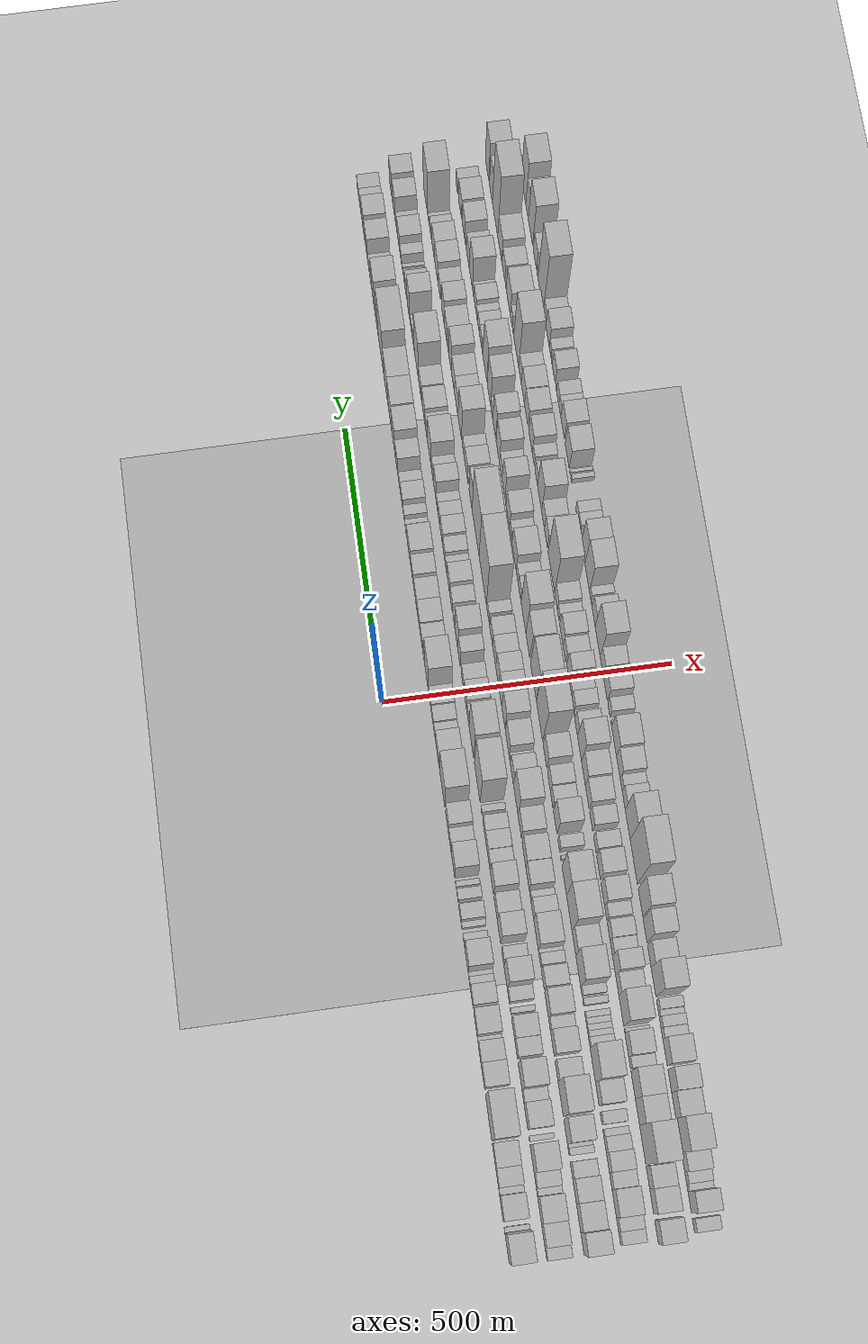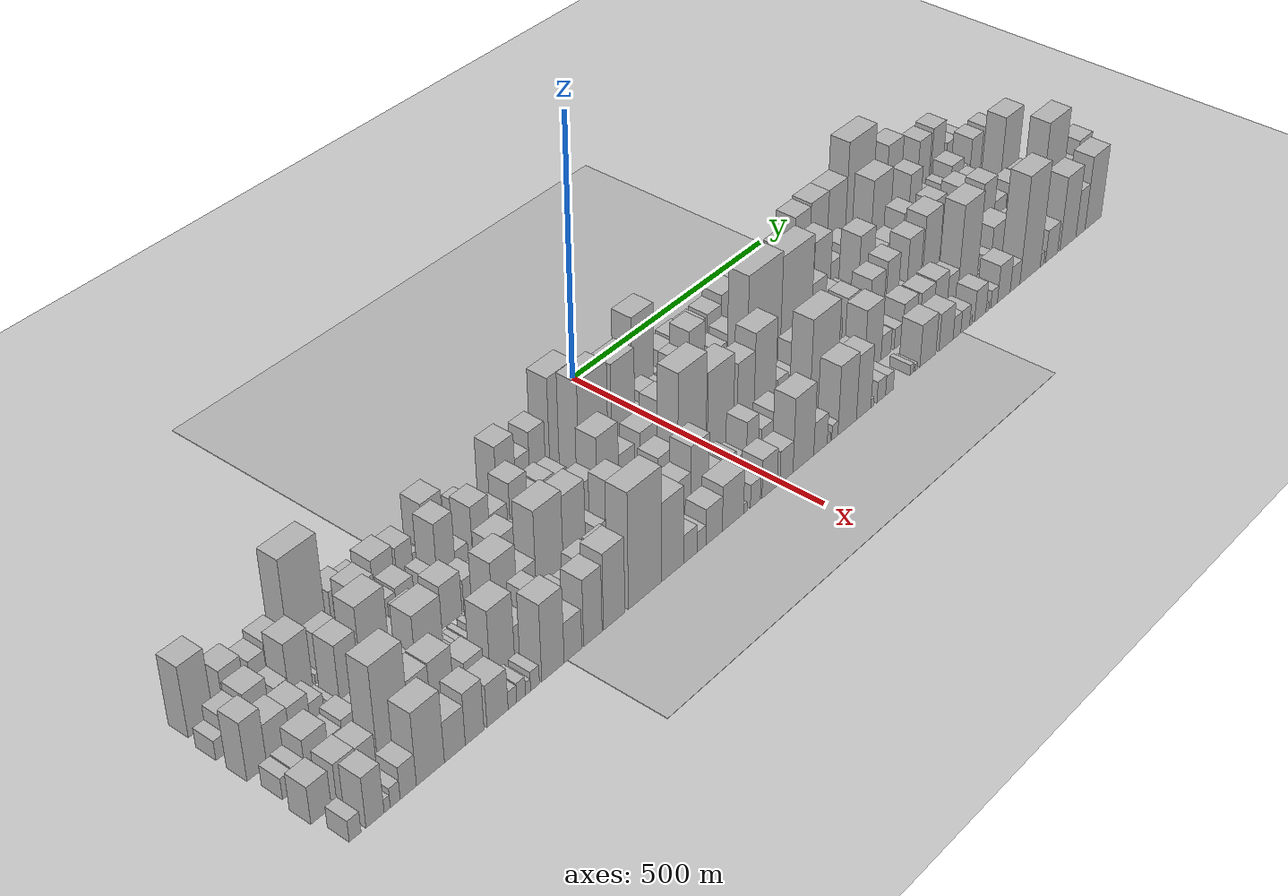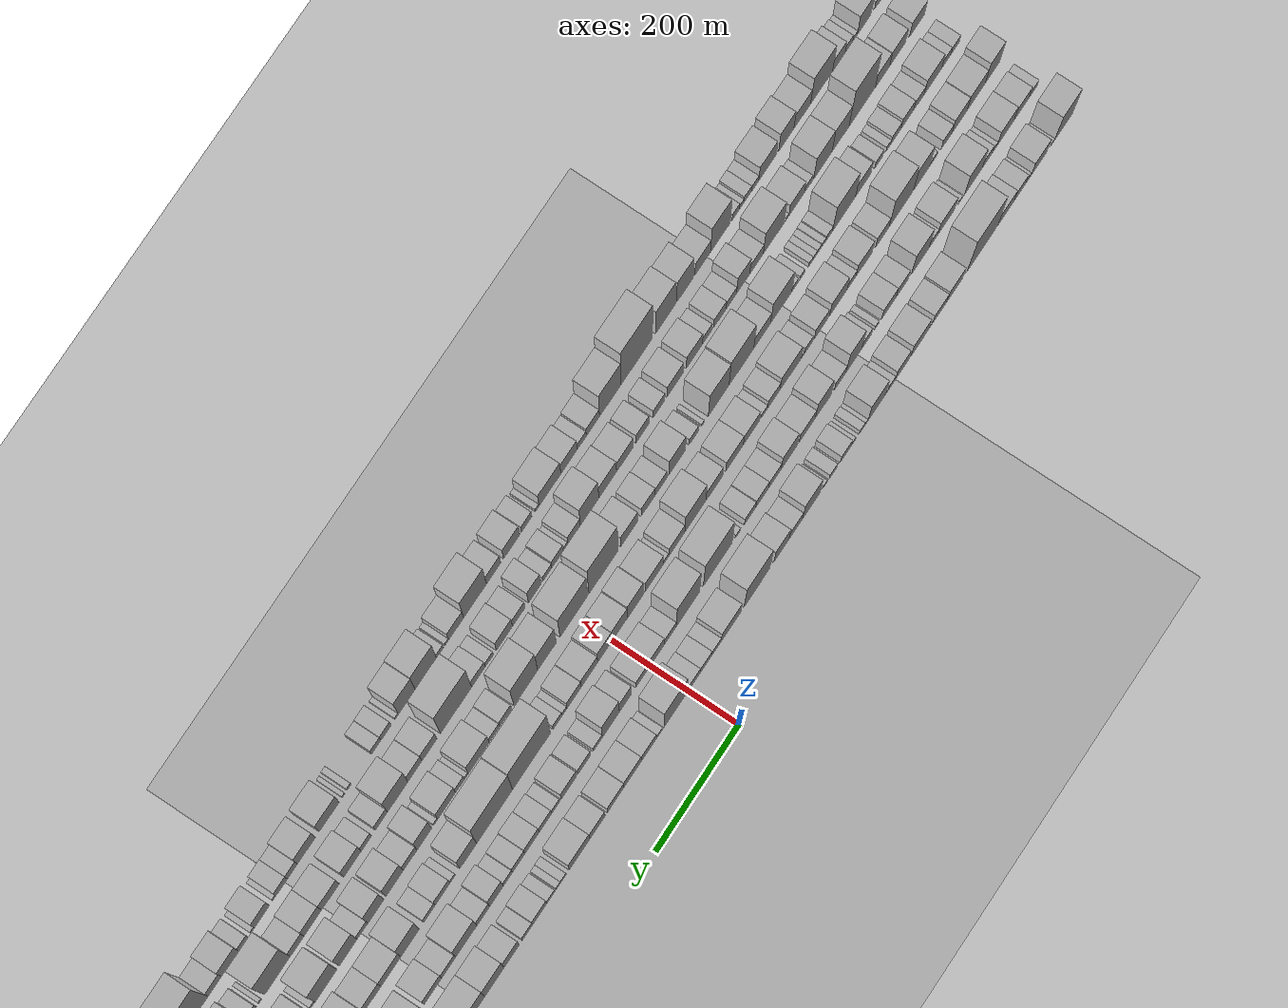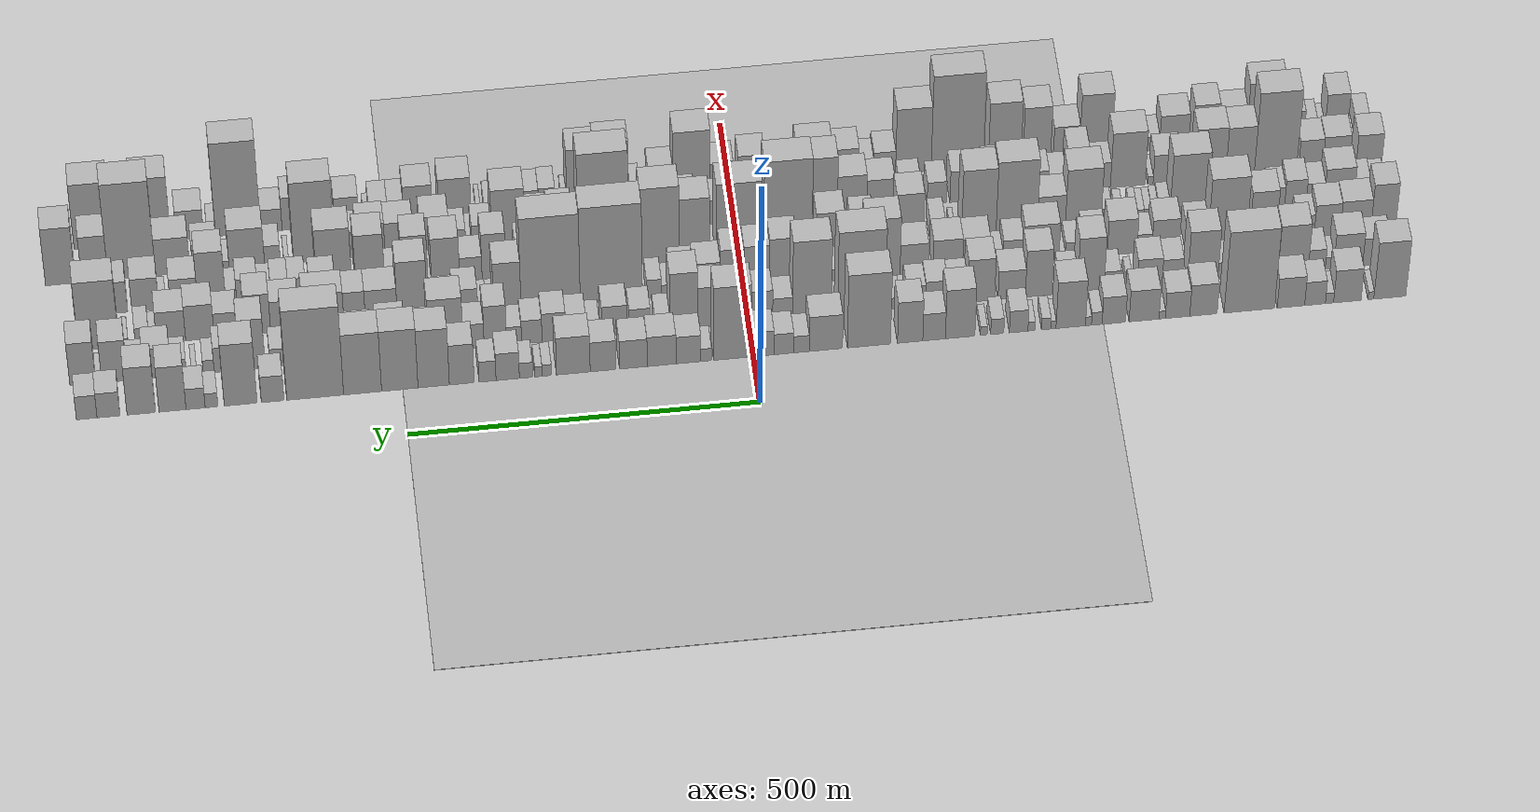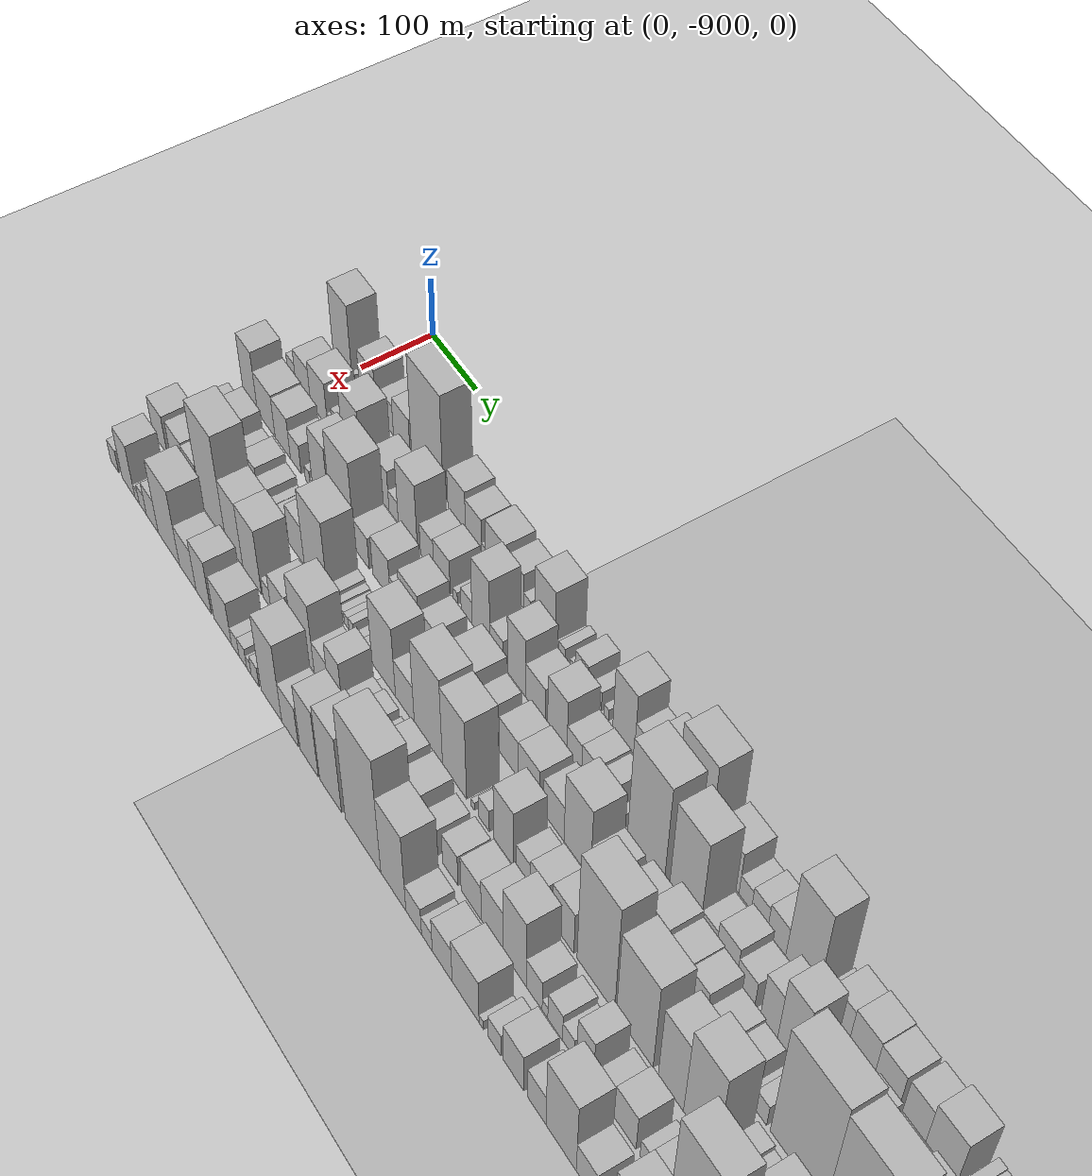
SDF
<?xml version="1.0" encoding="utf-8"?>

<sdf version="1.6">

   <world name="default">

      <gui fullscreen="0">

         <camera name="user_camera">

            <pose>-15 0 4.57585 0 0 0</pose>

            <view_controller>orbit</view_controller>

         </camera>

      </gui>

      <scene>

         <sky>

           <clouds>

             <speed>12</speed>

           </clouds>

         </sky>

         <ambient>0.4 0.4 0.4 1</ambient>

         <background>0.7 0.7 0.7 1</background>

         <shadows>1</shadows>

      </scene>

      <gravity>0 0 -9.8066</gravity>

      <magnetic_field>6e-06 2.3e-05 -4.2e-05</magnetic_field>

      <physics default="0" name="default_physics" type="ode">

         <ode>

            <solver>

               <type>quick</type>

               <iters>10</iters>

               <sor>1.0</sor>

               <use_dynamic_moi_rescaling>0</use_dynamic_moi_rescaling>

            </solver>

            <constraints>

               <cfm>0</cfm>

               <erp>0.2</erp>

               <contact_max_correcting_vel>100</contact_max_correcting_vel>

               <contact_surface_layer>0.001</contact_surface_layer>

            </constraints>

         </ode>

         <max_step_size>0.004</max_step_size>

         <real_time_factor>1</real_time_factor>

         <real_time_update_rate>250</real_time_update_rate>

      </physics>

      <light name="sun" type="directional">

         <cast_shadows>1</cast_shadows>

         <pose>0 0 10 0 0 0</pose>

         <diffuse>0.8 0.8 0.8 1</diffuse>

         <specular>0.2 0.2 0.2 1</specular>

         <attenuation>

            <range>1000</range>

            <constant>0.9</constant>

            <linear>0.01</linear>

            <quadratic>0.001</quadratic>

         </attenuation>

         <direction>-0.5 0.1 -0.9</direction>

      </light>

      <include>

         <name>ground_plane_1</name>

         <uri>model://HANNAS_ground_plane</uri>

         <pose>0 0 0  0 0 0</pose>

      </include>

      <include>

         <name>ground_plane_2</name>

         <uri>model://HANNAS_ground_plane</uri>

         <pose>100 0 0  0 0 0</pose>

      </include>

      <model name="building_1">

         <static>1</static>

         <pose frame="">100.0000 -911.9034 0 0.000000 0.000000 0.000000</pose>

         <link name="link">

            <pose frame="">0 0 66.00 0 0 0</pose>

            <collision name="collision">

               <geometry>

                  <box>

                     <size>40.0000 46.1933 132.0000</size>

                  </box>

               </geometry>

               <max_contacts>10</max_contacts>

               <surface>

                  <contact>

                     <ode/>

                  </contact>

                  <bounce/>

                  <friction>

                     <torsional>

                        <ode/>

                     </torsional>

                     <ode/>

                  </friction>

               </surface>

            </collision>

            <visual name="visual">

               <cast_shadows>0</cast_shadows>

               <geometry>

                  <box>

                     <size>40.0000 46.1933 132.0000</size>

                  </box>

               </geometry>

               <material>

                  <script>

                     <uri>model://HANNAS_wall/materials/scripts</uri>

                     <uri>model://HANNAS_wall/materials/textures</uri>

                     <name>vrc/HANNAS_wall</name>

                  </script>

               </material>

            </visual>

            <self_collide>0</self_collide>

            <enable_wind>0</enable_wind>

            <kinematic>0</kinematic>

         </link>

      </model>

      <model name="building_2">

         <static>1</static>

         <pose frame="">100.0000 -884.6747 0 0.000000 0.000000 0.000000</pose>

         <link name="link">

            <pose frame="">0 0 9.00 0 0 0</pose>

            <collision name="collision">

               <geometry>

                  <box>

                     <size>40.0000 8.2640 18.0000</size>

                  </box>

               </geometry>

               <max_contacts>10</max_contacts>

               <surface>

                  <contact>

                     <ode/>

                  </contact>

                  <bounce/>

                  <friction>

                     <torsional>

                        <ode/>

                     </torsional>

                     <ode/>

                  </friction>

               </surface>

            </collision>

            <visual name="visual">

               <cast_shadows>0</cast_shadows>

               <geometry>

                  <box>

                     <size>40.0000 8.2640 18.0000</size>

                  </box>

               </geometry>

               <material>

                  <script>

                     <uri>model://HANNAS_wall/materials/scripts</uri>

                     <uri>model://HANNAS_wall/materials/textures</uri>

                     <name>vrc/HANNAS_wall</name>

                  </script>

               </material>

            </visual>

            <self_collide>0</self_collide>

            <enable_wind>0</enable_wind>

            <kinematic>0</kinematic>

         </link>

      </model>

      <model name="building_3">

         <static>1</static>

         <pose frame="">100.0000 -850.7324 0 0.000000 0.000000 0.000000</pose>

         <link name="link">

            <pose frame="">0 0 37.50 0 0 0</pose>

            <collision name="collision">

               <geometry>

                  <box>

                     <size>40.0000 39.6207 75.0000</size>

                  </box>

               </geometry>

               <max_contacts>10</max_contacts>

               <surface>

                  <contact>

                     <ode/>

                  </contact>

                  <bounce/>

                  <friction>

                     <torsional>

                        <ode/>

                     </torsional>

                     <ode/>

                  </friction>

               </surface>

            </collision>

            <visual name="visual">

               <cast_shadows>0</cast_shadows>

               <geometry>

                  <box>

                     <size>40.0000 39.6207 75.0000</size>

                  </box>

               </geometry>

               <material>

                  <script>

                     <uri>model://HANNAS_wall/materials/scripts</uri>

                     <uri>model://HANNAS_wall/materials/textures</uri>

                     <name>vrc/HANNAS_wall</name>

                  </script>

               </material>

            </visual>

            <self_collide>0</self_collide>

            <enable_wind>0</enable_wind>

            <kinematic>0</kinematic>

         </link>

      </model>

      <model name="building_4">

         <static>1</static>

         <pose frame="">100.0000 -825.0080 0 0.000000 0.000000 0.000000</pose>

         <link name="link">

            <pose frame="">0 0 12.00 0 0 0</pose>

            <collision name="collision">

               <geometry>

                  <box>

                     <size>40.0000 11.8280 24.0000</size>

                  </box>

               </geometry>

               <max_contacts>10</max_contacts>

               <surface>

                  <contact>

                     <ode/>

                  </contact>

                  <bounce/>

                  <friction>

                     <torsional>

                        <ode/>

                     </torsional>

                     <ode/>

                  </friction>

               </surface>

            </collision>

            <visual name="visual">

               <cast_shadows>0</cast_shadows>

               <geometry>

                  <box>

                     <size>40.0000 11.8280 24.0000</size>

                  </box>

               </geometry>

               <material>

                  <script>

                     <uri>model://HANNAS_wall/materials/scripts</uri>

                     <uri>model://HANNAS_wall/materials/textures</uri>

                     <name>vrc/HANNAS_wall</name>

                  </script>

               </material>

            </visual>

            <self_collide>0</self_collide>

            <enable_wind>0</enable_wind>

            <kinematic>0</kinematic>

         </link>

      </model>

      <model name="building_5">

         <static>1</static>

         <pose frame="">100.0000 -804.1436 0 0.000000 0.000000 0.000000</pose>

         <link name="link">

            <pose frame="">0 0 27.00 0 0 0</pose>

            <collision name="collision">

               <geometry>

                  <box>

                     <size>40.0000 29.9008 54.0000</size>

                  </box>

               </geometry>

               <max_contacts>10</max_contacts>

               <surface>

                  <contact>

                     <ode/>

                  </contact>

                  <bounce/>

                  <friction>

                     <torsional>

                        <ode/>

                     </torsional>

                     <ode/>

                  </friction>

               </surface>

            </collision>

            <visual name="visual">

               <cast_shadows>0</cast_shadows>

               <geometry>

                  <box>

                     <size>40.0000 29.9008 54.0000</size>

                  </box>

               </geometry>

               <material>

                  <script>

                     <uri>model://HANNAS_wall/materials/scripts</uri>

                     <uri>model://HANNAS_wall/materials/textures</uri>

                     <name>vrc/HANNAS_wall</name>

                  </script>

               </material>

            </visual>

            <self_collide>0</self_collide>

            <enable_wind>0</enable_wind>

            <kinematic>0</kinematic>

         </link>

      </model>

      <model name="building_6">

         <static>1</static>

         <pose frame="">100.0000 -769.4569 0 0.000000 0.000000 0.000000</pose>

         <link name="link">

            <pose frame="">0 0 34.50 0 0 0</pose>

            <collision name="collision">

               <geometry>

                  <box>

                     <size>40.0000 39.4728 69.0000</size>

                  </box>

               </geometry>

               <max_contacts>10</max_contacts>

               <surface>

                  <contact>

                     <ode/>

                  </contact>

                  <bounce/>

                  <friction>

                     <torsional>

                        <ode/>

                     </torsional>

                     <ode/>

                  </friction>

               </surface>

            </collision>

            <visual name="visual">

               <cast_shadows>0</cast_shadows>

               <geometry>

                  <box>

                     <size>40.0000 39.4728 69.0000</size>

                  </box>

               </geometry>

               <material>

                  <script>

                     <uri>model://HANNAS_wall/materials/scripts</uri>

                     <uri>model://HANNAS_wall/materials/textures</uri>

                     <name>vrc/HANNAS_wall</name>

                  </script>

               </material>

            </visual>

            <self_collide>0</self_collide>

            <enable_wind>0</enable_wind>

            <kinematic>0</kinematic>

         </link>

      </model>

      <model name="building_7">

         <static>1</static>

         <pose frame="">100.0000 -709.4943 0 0.000000 0.000000 0.000000</pose>

         <link name="link">

            <pose frame="">0 0 94.50 0 0 0</pose>

            <collision name="collision">

               <geometry>

                  <box>

                     <size>40.0000 72.4522 189.0000</size>

                  </box>

               </geometry>

               <max_contacts>10</max_contacts>

               <surface>

                  <contact>

                     <ode/>

                  </contact>

                  <bounce/>

                  <friction>

                     <torsional>

                        <ode/>

                     </torsional>

                     <ode/>

                  </friction>

               </surface>

            </collision>

            <visual name="visual">

               <cast_shadows>0</cast_shadows>

               <geometry>

                  <box>

                     <size>40.0000 72.4522 189.0000</size>

                  </box>

               </geometry>

               <material>

                  <script>

                     <uri>model://HANNAS_wall/materials/scripts</uri>

                     <uri>model://HANNAS_wall/materials/textures</uri>

                     <name>vrc/HANNAS_wall</name>

                  </script>

               </material>

            </visual>

            <self_collide>0</self_collide>

            <enable_wind>0</enable_wind>

            <kinematic>0</kinematic>

         </link>

      </model>

      <model name="building_8">

         <static>1</static>

         <pose frame="">100.0000 -643.5530 0 0.000000 0.000000 0.000000</pose>

         <link name="link">

            <pose frame="">0 0 36.00 0 0 0</pose>

            <collision name="collision">

               <geometry>

                  <box>

                     <size>40.0000 39.4304 72.0000</size>

                  </box>

               </geometry>

               <max_contacts>10</max_contacts>

               <surface>

                  <contact>

                     <ode/>

                  </contact>

                  <bounce/>

                  <friction>

                     <torsional>

                        <ode/>

                     </torsional>

                     <ode/>

                  </friction>

               </surface>

            </collision>

            <visual name="visual">

               <cast_shadows>0</cast_shadows>

               <geometry>

                  <box>

                     <size>40.0000 39.4304 72.0000</size>

                  </box>

               </geometry>

               <material>

                  <script>

                     <uri>model://HANNAS_wall/materials/scripts</uri>

                     <uri>model://HANNAS_wall/materials/textures</uri>

                     <name>vrc/HANNAS_wall</name>

                  </script>

               </material>

            </visual>

            <self_collide>0</self_collide>

            <enable_wind>0</enable_wind>

            <kinematic>0</kinematic>

         </link>

      </model>

      <model name="building_9">

         <static>1</static>

         <pose frame="">100.0000 -606.2515 0 0.000000 0.000000 0.000000</pose>

         <link name="link">

            <pose frame="">0 0 30.00 0 0 0</pose>

            <collision name="collision">

               <geometry>

                  <box>

                     <size>40.0000 35.1727 60.0000</size>

                  </box>

               </geometry>

               <max_contacts>10</max_contacts>

               <surface>

                  <contact>

                     <ode/>

                  </contact>

                  <bounce/>

                  <friction>

                     <torsional>

                        <ode/>

                     </torsional>

                     <ode/>

                  </friction>

               </surface>

            </collision>

            <visual name="visual">

               <cast_shadows>0</cast_shadows>

               <geometry>

                  <box>

                     <size>40.0000 35.1727 60.0000</size>

                  </box>

               </geometry>

               <material>

                  <script>

                     <uri>model://HANNAS_wall/materials/scripts</uri>

                     <uri>model://HANNAS_wall/materials/textures</uri>

                     <name>vrc/HANNAS_wall</name>

                  </script>

               </material>

            </visual>

            <self_collide>0</self_collide>

            <enable_wind>0</enable_wind>

            <kinematic>0</kinematic>

         </link>

      </model>

      <model name="building_10">

         <static>1</static>

         <pose frame="">100.0000 -584.1855 0 0.000000 0.000000 0.000000</pose>

         <link name="link">

            <pose frame="">0 0 9.00 0 0 0</pose>

            <collision name="collision">

               <geometry>

                  <box>

                     <size>40.0000 8.9594 18.0000</size>

                  </box>

               </geometry>

               <max_contacts>10</max_contacts>

               <surface>

                  <contact>

                     <ode/>

                  </contact>

                  <bounce/>

                  <friction>

                     <torsional>

                        <ode/>

                     </torsional>

                     <ode/>

                  </friction>

               </surface>

            </collision>

            <visual name="visual">

               <cast_shadows>0</cast_shadows>

               <geometry>

                  <box>

                     <size>40.0000 8.9594 18.0000</size>

                  </box>

               </geometry>

               <material>

                  <script>

                     <uri>model://HANNAS_wall/materials/scripts</uri>

                     <uri>model://HANNAS_wall/materials/textures</uri>

                     <name>vrc/HANNAS_wall</name>

                  </script>

               </material>

            </visual>

            <self_collide>0</self_collide>

            <enable_wind>0</enable_wind>

            <kinematic>0</kinematic>

         </link>

      </model>

      <model name="building_11">

         <static>1</static>

         <pose frame="">100.0000 -558.2118 0 0.000000 0.000000 0.000000</pose>

         <link name="link">

            <pose frame="">0 0 36.00 0 0 0</pose>

            <collision name="collision">

               <geometry>

                  <box>

                     <size>40.0000 42.9881 72.0000</size>

                  </box>

               </geometry>

               <max_contacts>10</max_contacts>

               <surface>

                  <contact>

                     <ode/>

                  </contact>

                  <bounce/>

                  <friction>

                     <torsional>

                        <ode/>

                     </torsional>

                     <ode/>

                  </friction>

               </surface>

            </collision>

            <visual name="visual">

               <cast_shadows>0</cast_shadows>

               <geometry>

                  <box>

                     <size>40.0000 42.9881 72.0000</size>

                  </box>

               </geometry>

               <material>

                  <script>

                     <uri>model://HANNAS_wall/materials/scripts</uri>

                     <uri>model://HANNAS_wall/materials/textures</uri>

                     <name>vrc/HANNAS_wall</name>

                  </script>

               </material>

            </visual>

            <self_collide>0</self_collide>

            <enable_wind>0</enable_wind>

            <kinematic>0</kinematic>

         </link>

      </model>

      <model name="building_12">

         <static>1</static>

         <pose frame="">100.0000 -514.8309 0 0.000000 0.000000 0.000000</pose>

         <link name="link">

            <pose frame="">0 0 31.50 0 0 0</pose>

            <collision name="collision">

               <geometry>

                  <box>

                     <size>40.0000 33.7736 63.0000</size>

                  </box>

               </geometry>

               <max_contacts>10</max_contacts>

               <surface>

                  <contact>

                     <ode/>

                  </contact>

                  <bounce/>

                  <friction>

                     <torsional>

                        <ode/>

                     </torsional>

                     <ode/>

                  </friction>

               </surface>

            </collision>

            <visual name="visual">

               <cast_shadows>0</cast_shadows>

               <geometry>

                  <box>

                     <size>40.0000 33.7736 63.0000</size>

                  </box>

               </geometry>

               <material>

                  <script>

                     <uri>model://HANNAS_wall/materials/scripts</uri>

                     <uri>model://HANNAS_wall/materials/textures</uri>

                     <name>vrc/HANNAS_wall</name>

                  </script>

               </material>

            </visual>

            <self_collide>0</self_collide>

            <enable_wind>0</enable_wind>

            <kinematic>0</kinematic>

         </link>

      </model>

      <model name="building_13">

         <static>1</static>

         <pose frame="">100.0000 -490.3333 0 0.000000 0.000000 0.000000</pose>

         <link name="link">

            <pose frame="">0 0 15.00 0 0 0</pose>

            <collision name="collision">

               <geometry>

                  <box>

                     <size>40.0000 15.2217 30.0000</size>

                  </box>

               </geometry>

               <max_contacts>10</max_contacts>

               <surface>

                  <contact>

                     <ode/>

                  </contact>

                  <bounce/>

                  <friction>

                     <torsional>

                        <ode/>

                     </torsional>

                     <ode/>

                  </friction>

               </surface>

            </collision>

            <visual name="visual">

               <cast_shadows>0</cast_shadows>

               <geometry>

                  <box>

                     <size>40.0000 15.2217 30.0000</size>

                  </box>

               </geometry>

               <material>

                  <script>

                     <uri>model://HANNAS_wall/materials/scripts</uri>

                     <uri>model://HANNAS_wall/materials/textures</uri>

                     <name>vrc/HANNAS_wall</name>

                  </script>

               </material>

            </visual>

            <self_collide>0</self_collide>

            <enable_wind>0</enable_wind>

            <kinematic>0</kinematic>

         </link>

      </model>

      <model name="building_14">

         <static>1</static>

         <pose frame="">100.0000 -478.3659 0 0.000000 0.000000 0.000000</pose>

         <link name="link">

            <pose frame="">0 0 10.50 0 0 0</pose>

            <collision name="collision">

               <geometry>

                  <box>

                     <size>40.0000 8.7132 21.0000</size>

                  </box>

               </geometry>

               <max_contacts>10</max_contacts>

               <surface>

                  <contact>

                     <ode/>

                  </contact>

                  <bounce/>

                  <friction>

                     <torsional>

                        <ode/>

                     </torsional>

                     <ode/>

                  </friction>

               </surface>

            </collision>

            <visual name="visual">

               <cast_shadows>0</cast_shadows>

               <geometry>

                  <box>

                     <size>40.0000 8.7132 21.0000</size>

                  </box>

               </geometry>

               <material>

                  <script>

                     <uri>model://HANNAS_wall/materials/scripts</uri>

                     <uri>model://HANNAS_wall/materials/textures</uri>

                     <name>vrc/HANNAS_wall</name>

                  </script>

               </material>

            </visual>

            <self_collide>0</self_collide>

            <enable_wind>0</enable_wind>

            <kinematic>0</kinematic>

         </link>

      </model>

      <model name="building_15">

         <static>1</static>

         <pose frame="">100.0000 -452.8902 0 0.000000 0.000000 0.000000</pose>

         <link name="link">

            <pose frame="">0 0 54.00 0 0 0</pose>

            <collision name="collision">

               <geometry>

                  <box>

                     <size>40.0000 42.2380 108.0000</size>

                  </box>

               </geometry>

               <max_contacts>10</max_contacts>

               <surface>

                  <contact>

                     <ode/>

                  </contact>

                  <bounce/>

                  <friction>

                     <torsional>

                        <ode/>

                     </torsional>

                     <ode/>

                  </friction>

               </surface>

            </collision>

            <visual name="visual">

               <cast_shadows>0</cast_shadows>

               <geometry>

                  <box>

                     <size>40.0000 42.2380 108.0000</size>

                  </box>

               </geometry>

               <material>

                  <script>

                     <uri>model://HANNAS_wall/materials/scripts</uri>

                     <uri>model://HANNAS_wall/materials/textures</uri>

                     <name>vrc/HANNAS_wall</name>

                  </script>

               </material>

            </visual>

            <self_collide>0</self_collide>

            <enable_wind>0</enable_wind>

            <kinematic>0</kinematic>

         </link>

      </model>

      <model name="building_16">

         <static>1</static>

         <pose frame="">100.0000 -427.9753 0 0.000000 0.000000 0.000000</pose>

         <link name="link">

            <pose frame="">0 0 9.00 0 0 0</pose>

            <collision name="collision">

               <geometry>

                  <box>

                     <size>40.0000 7.5918 18.0000</size>

                  </box>

               </geometry>

               <max_contacts>10</max_contacts>

               <surface>

                  <contact>

                     <ode/>

                  </contact>

                  <bounce/>

                  <friction>

                     <torsional>

                        <ode/>

                     </torsional>

                     <ode/>

                  </friction>

               </surface>

            </collision>

            <visual name="visual">

               <cast_shadows>0</cast_shadows>

               <geometry>

                  <box>

                     <size>40.0000 7.5918 18.0000</size>

                  </box>

               </geometry>

               <material>

                  <script>

                     <uri>model://HANNAS_wall/materials/scripts</uri>

                     <uri>model://HANNAS_wall/materials/textures</uri>

                     <name>vrc/HANNAS_wall</name>

                  </script>

               </material>

            </visual>

            <self_collide>0</self_collide>

            <enable_wind>0</enable_wind>

            <kinematic>0</kinematic>

         </link>

      </model>

      <model name="building_17">

         <static>1</static>

         <pose frame="">100.0000 -417.6089 0 0.000000 0.000000 0.000000</pose>

         <link name="link">

            <pose frame="">0 0 13.50 0 0 0</pose>

            <collision name="collision">

               <geometry>

                  <box>

                     <size>40.0000 13.1411 27.0000</size>

                  </box>

               </geometry>

               <max_contacts>10</max_contacts>

               <surface>

                  <contact>

                     <ode/>

                  </contact>

                  <bounce/>

                  <friction>

                     <torsional>

                        <ode/>

                     </torsional>

                     <ode/>

                  </friction>

               </surface>

            </collision>

            <visual name="visual">

               <cast_shadows>0</cast_shadows>

               <geometry>

                  <box>

                     <size>40.0000 13.1411 27.0000</size>

                  </box>

               </geometry>

               <material>

                  <script>

                     <uri>model://HANNAS_wall/materials/scripts</uri>

                     <uri>model://HANNAS_wall/materials/textures</uri>

                     <name>vrc/HANNAS_wall</name>

                  </script>

               </material>

            </visual>

            <self_collide>0</self_collide>

            <enable_wind>0</enable_wind>

            <kinematic>0</kinematic>

         </link>

      </model>

      <model name="building_18">

         <static>1</static>

         <pose frame="">100.0000 -396.8019 0 0.000000 0.000000 0.000000</pose>

         <link name="link">

            <pose frame="">0 0 10.50 0 0 0</pose>

            <collision name="collision">

               <geometry>

                  <box>

                     <size>40.0000 10.4727 21.0000</size>

                  </box>

               </geometry>

               <max_contacts>10</max_contacts>

               <surface>

                  <contact>

                     <ode/>

                  </contact>

                  <bounce/>

                  <friction>

                     <torsional>

                        <ode/>

                     </torsional>

                     <ode/>

                  </friction>

               </surface>

            </collision>

            <visual name="visual">

               <cast_shadows>0</cast_shadows>

               <geometry>

                  <box>

                     <size>40.0000 10.4727 21.0000</size>

                  </box>

               </geometry>

               <material>

                  <script>

                     <uri>model://HANNAS_wall/materials/scripts</uri>

                     <uri>model://HANNAS_wall/materials/textures</uri>

                     <name>vrc/HANNAS_wall</name>

                  </script>

               </material>

            </visual>

            <self_collide>0</self_collide>

            <enable_wind>0</enable_wind>

            <kinematic>0</kinematic>

         </link>

      </model>

      <model name="building_19">

         <static>1</static>

         <pose frame="">100.0000 -378.2339 0 0.000000 0.000000 0.000000</pose>

         <link name="link">

            <pose frame="">0 0 25.50 0 0 0</pose>

            <collision name="collision">

               <geometry>

                  <box>

                     <size>40.0000 26.6633 51.0000</size>

                  </box>

               </geometry>

               <max_contacts>10</max_contacts>

               <surface>

                  <contact>

                     <ode/>

                  </contact>

                  <bounce/>

                  <friction>

                     <torsional>

                        <ode/>

                     </torsional>

                     <ode/>

                  </friction>

               </surface>

            </collision>

            <visual name="visual">

               <cast_shadows>0</cast_shadows>

               <geometry>

                  <box>

                     <size>40.0000 26.6633 51.0000</size>

                  </box>

               </geometry>

               <material>

                  <script>

                     <uri>model://HANNAS_wall/materials/scripts</uri>

                     <uri>model://HANNAS_wall/materials/textures</uri>

                     <name>vrc/HANNAS_wall</name>

                  </script>

               </material>

            </visual>

            <self_collide>0</self_collide>

            <enable_wind>0</enable_wind>

            <kinematic>0</kinematic>

         </link>

      </model>

      <model name="building_20">

         <static>1</static>

         <pose frame="">100.0000 -347.5182 0 0.000000 0.000000 0.000000</pose>

         <link name="link">

            <pose frame="">0 0 18.00 0 0 0</pose>

            <collision name="collision">

               <geometry>

                  <box>

                     <size>40.0000 18.7680 36.0000</size>

                  </box>

               </geometry>

               <max_contacts>10</max_contacts>

               <surface>

                  <contact>

                     <ode/>

                  </contact>

                  <bounce/>

                  <friction>

                     <torsional>

                        <ode/>

                     </torsional>

                     <ode/>

                  </friction>

               </surface>

            </collision>

            <visual name="visual">

               <cast_shadows>0</cast_shadows>

               <geometry>

                  <box>

                     <size>40.0000 18.7680 36.0000</size>

                  </box>

               </geometry>

               <material>

                  <script>

                     <uri>model://HANNAS_wall/materials/scripts</uri>

                     <uri>model://HANNAS_wall/materials/textures</uri>

                     <name>vrc/HANNAS_wall</name>

                  </script>

               </material>

            </visual>

            <self_collide>0</self_collide>

            <enable_wind>0</enable_wind>

            <kinematic>0</kinematic>

         </link>

      </model>

      <model name="building_21">

         <static>1</static>

         <pose frame="">100.0000 -328.2891 0 0.000000 0.000000 0.000000</pose>

         <link name="link">

            <pose frame="">0 0 10.50 0 0 0</pose>

            <collision name="collision">

               <geometry>

                  <box>

                     <size>40.0000 9.6902 21.0000</size>

                  </box>

               </geometry>

               <max_contacts>10</max_contacts>

               <surface>

                  <contact>

                     <ode/>

                  </contact>

                  <bounce/>

                  <friction>

                     <torsional>

                        <ode/>

                     </torsional>

                     <ode/>

                  </friction>

               </surface>

            </collision>

            <visual name="visual">

               <cast_shadows>0</cast_shadows>

               <geometry>

                  <box>

                     <size>40.0000 9.6902 21.0000</size>

                  </box>

               </geometry>

               <material>

                  <script>

                     <uri>model://HANNAS_wall/materials/scripts</uri>

                     <uri>model://HANNAS_wall/materials/textures</uri>

                     <name>vrc/HANNAS_wall</name>

                  </script>

               </material>

            </visual>

            <self_collide>0</self_collide>

            <enable_wind>0</enable_wind>

            <kinematic>0</kinematic>

         </link>

      </model>

      <model name="building_22">

         <static>1</static>

         <pose frame="">100.0000 -294.3488 0 0.000000 0.000000 0.000000</pose>

         <link name="link">

            <pose frame="">0 0 57.00 0 0 0</pose>

            <collision name="collision">

               <geometry>

                  <box>

                     <size>40.0000 42.1904 114.0000</size>

                  </box>

               </geometry>

               <max_contacts>10</max_contacts>

               <surface>

                  <contact>

                     <ode/>

                  </contact>

                  <bounce/>

                  <friction>

                     <torsional>

                        <ode/>

                     </torsional>

                     <ode/>

                  </friction>

               </surface>

            </collision>

            <visual name="visual">

               <cast_shadows>0</cast_shadows>

               <geometry>

                  <box>

                     <size>40.0000 42.1904 114.0000</size>

                  </box>

               </geometry>

               <material>

                  <script>

                     <uri>model://HANNAS_wall/materials/scripts</uri>

                     <uri>model://HANNAS_wall/materials/textures</uri>

                     <name>vrc/HANNAS_wall</name>

                  </script>

               </material>

            </visual>

            <self_collide>0</self_collide>

            <enable_wind>0</enable_wind>

            <kinematic>0</kinematic>

         </link>

      </model>

      <model name="building_23">

         <static>1</static>

         <pose frame="">100.0000 -257.0880 0 0.000000 0.000000 0.000000</pose>

         <link name="link">

            <pose frame="">0 0 31.50 0 0 0</pose>

            <collision name="collision">

               <geometry>

                  <box>

                     <size>40.0000 32.3312 63.0000</size>

                  </box>

               </geometry>

               <max_contacts>10</max_contacts>

               <surface>

                  <contact>

                     <ode/>

                  </contact>

                  <bounce/>

                  <friction>

                     <torsional>

                        <ode/>

                     </torsional>

                     <ode/>

                  </friction>

               </surface>

            </collision>

            <visual name="visual">

               <cast_shadows>0</cast_shadows>

               <geometry>

                  <box>

                     <size>40.0000 32.3312 63.0000</size>

                  </box>

               </geometry>

               <material>

                  <script>

                     <uri>model://HANNAS_wall/materials/scripts</uri>

                     <uri>model://HANNAS_wall/materials/textures</uri>

                     <name>vrc/HANNAS_wall</name>

                  </script>

               </material>

            </visual>

            <self_collide>0</self_collide>

            <enable_wind>0</enable_wind>

            <kinematic>0</kinematic>

         </link>

      </model>

      <model name="building_24">

         <static>1</static>

         <pose frame="">100.0000 -222.8376 0 0.000000 0.000000 0.000000</pose>

         <link name="link">

            <pose frame="">0 0 48.00 0 0 0</pose>

            <collision name="collision">

               <geometry>

                  <box>

                     <size>40.0000 36.1696 96.0000</size>

                  </box>

               </geometry>

               <max_contacts>10</max_contacts>

               <surface>

                  <contact>

                     <ode/>

                  </contact>

                  <bounce/>

                  <friction>

                     <torsional>

                        <ode/>

                     </torsional>

                     <ode/>

                  </friction>

               </surface>

            </collision>

            <visual name="visual">

               <cast_shadows>0</cast_shadows>

               <geometry>

                  <box>

                     <size>40.0000 36.1696 96.0000</size>

                  </box>

               </geometry>

               <material>

                  <script>

                     <uri>model://HANNAS_wall/materials/scripts</uri>

                     <uri>model://HANNAS_wall/materials/textures</uri>

                     <name>vrc/HANNAS_wall</name>

                  </script>

               </material>

            </visual>

            <self_collide>0</self_collide>

            <enable_wind>0</enable_wind>

            <kinematic>0</kinematic>

         </link>

      </model>

      <model name="building_25">

         <static>1</static>

         <pose frame="">100.0000 -163.9431 0 0.000000 0.000000 0.000000</pose>

         <link name="link">

            <pose frame="">0 0 85.50 0 0 0</pose>

            <collision name="collision">

               <geometry>

                  <box>

                     <size>40.0000 61.6196 171.0000</size>

                  </box>

               </geometry>

               <max_contacts>10</max_contacts>

               <surface>

                  <contact>

                     <ode/>

                  </contact>

                  <bounce/>

                  <friction>

                     <torsional>

                        <ode/>

                     </torsional>

                     <ode/>

                  </friction>

               </surface>

            </collision>

            <visual name="visual">

               <cast_shadows>0</cast_shadows>

               <geometry>

                  <box>

                     <size>40.0000 61.6196 171.0000</size>

                  </box>

               </geometry>

               <material>

                  <script>

                     <uri>model://HANNAS_wall/materials/scripts</uri>

                     <uri>model://HANNAS_wall/materials/textures</uri>

                     <name>vrc/HANNAS_wall</name>

                  </script>

               </material>

            </visual>

            <self_collide>0</self_collide>

            <enable_wind>0</enable_wind>

            <kinematic>0</kinematic>

         </link>

      </model>

      <model name="building_26">

         <static>1</static>

         <pose frame="">100.0000 -102.3194 0 0.000000 0.000000 0.000000</pose>

         <link name="link">

            <pose frame="">0 0 40.50 0 0 0</pose>

            <collision name="collision">

               <geometry>

                  <box>

                     <size>40.0000 47.6278 81.0000</size>

                  </box>

               </geometry>

               <max_contacts>10</max_contacts>

               <surface>

                  <contact>

                     <ode/>

                  </contact>

                  <bounce/>

                  <friction>

                     <torsional>

                        <ode/>

                     </torsional>

                     <ode/>

                  </friction>

               </surface>

            </collision>

            <visual name="visual">

               <cast_shadows>0</cast_shadows>

               <geometry>

                  <box>

                     <size>40.0000 47.6278 81.0000</size>

                  </box>

               </geometry>

               <material>

                  <script>

                     <uri>model://HANNAS_wall/materials/scripts</uri>

                     <uri>model://HANNAS_wall/materials/textures</uri>

                     <name>vrc/HANNAS_wall</name>

                  </script>

               </material>

            </visual>

            <self_collide>0</self_collide>

            <enable_wind>0</enable_wind>

            <kinematic>0</kinematic>

         </link>

      </model>

      <model name="building_27">

         <static>1</static>

         <pose frame="">100.0000 -67.4744 0 0.000000 0.000000 0.000000</pose>

         <link name="link">

            <pose frame="">0 0 19.50 0 0 0</pose>

            <collision name="collision">

               <geometry>

                  <box>

                     <size>40.0000 22.0623 39.0000</size>

                  </box>

               </geometry>

               <max_contacts>10</max_contacts>

               <surface>

                  <contact>

                     <ode/>

                  </contact>

                  <bounce/>

                  <friction>

                     <torsional>

                        <ode/>

                     </torsional>

                     <ode/>

                  </friction>

               </surface>

            </collision>

            <visual name="visual">

               <cast_shadows>0</cast_shadows>

               <geometry>

                  <box>

                     <size>40.0000 22.0623 39.0000</size>

                  </box>

               </geometry>

               <material>

                  <script>

                     <uri>model://HANNAS_wall/materials/scripts</uri>

                     <uri>model://HANNAS_wall/materials/textures</uri>

                     <name>vrc/HANNAS_wall</name>

                  </script>

               </material>

            </visual>

            <self_collide>0</self_collide>

            <enable_wind>0</enable_wind>

            <kinematic>0</kinematic>

         </link>

      </model>

      <model name="building_28">

         <static>1</static>

         <pose frame="">100.0000 -42.3867 0 0.000000 0.000000 0.000000</pose>

         <link name="link">

            <pose frame="">0 0 24.00 0 0 0</pose>

            <collision name="collision">

               <geometry>

                  <box>

                     <size>40.0000 28.1130 48.0000</size>

                  </box>

               </geometry>

               <max_contacts>10</max_contacts>

               <surface>

                  <contact>

                     <ode/>

                  </contact>

                  <bounce/>

                  <friction>

                     <torsional>

                        <ode/>

                     </torsional>

                     <ode/>

                  </friction>

               </surface>

            </collision>

            <visual name="visual">

               <cast_shadows>0</cast_shadows>

               <geometry>

                  <box>

                     <size>40.0000 28.1130 48.0000</size>

                  </box>

               </geometry>

               <material>

                  <script>

                     <uri>model://HANNAS_wall/materials/scripts</uri>

                     <uri>model://HANNAS_wall/materials/textures</uri>

                     <name>vrc/HANNAS_wall</name>

                  </script>

               </material>

            </visual>

            <self_collide>0</self_collide>

            <enable_wind>0</enable_wind>

            <kinematic>0</kinematic>

         </link>

      </model>

      <model name="building_29">

         <static>1</static>

         <pose frame="">100.0000 -12.2893 0 0.000000 0.000000 0.000000</pose>

         <link name="link">

            <pose frame="">0 0 28.50 0 0 0</pose>

            <collision name="collision">

               <geometry>

                  <box>

                     <size>40.0000 32.0819 57.0000</size>

                  </box>

               </geometry>

               <max_contacts>10</max_contacts>

               <surface>

                  <contact>

                     <ode/>

                  </contact>

                  <bounce/>

                  <friction>

                     <torsional>

                        <ode/>

                     </torsional>

                     <ode/>

                  </friction>

               </surface>

            </collision>

            <visual name="visual">

               <cast_shadows>0</cast_shadows>

               <geometry>

                  <box>

                     <size>40.0000 32.0819 57.0000</size>

                  </box>

               </geometry>

               <material>

                  <script>

                     <uri>model://HANNAS_wall/materials/scripts</uri>

                     <uri>model://HANNAS_wall/materials/textures</uri>

                     <name>vrc/HANNAS_wall</name>

                  </script>

               </material>

            </visual>

            <self_collide>0</self_collide>

            <enable_wind>0</enable_wind>

            <kinematic>0</kinematic>

         </link>

      </model>

      <model name="building_30">

         <static>1</static>

         <pose frame="">100.0000 30.7416 0 0.000000 0.000000 0.000000</pose>

         <link name="link">

            <pose frame="">0 0 85.50 0 0 0</pose>

            <collision name="collision">

               <geometry>

                  <box>

                     <size>40.0000 53.9798 171.0000</size>

                  </box>

               </geometry>

               <max_contacts>10</max_contacts>

               <surface>

                  <contact>

                     <ode/>

                  </contact>

                  <bounce/>

                  <friction>

                     <torsional>

                        <ode/>

                     </torsional>

                     <ode/>

                  </friction>

               </surface>

            </collision>

            <visual name="visual">

               <cast_shadows>0</cast_shadows>

               <geometry>

                  <box>

                     <size>40.0000 53.9798 171.0000</size>

                  </box>

               </geometry>

               <material>

                  <script>

                     <uri>model://HANNAS_wall/materials/scripts</uri>

                     <uri>model://HANNAS_wall/materials/textures</uri>

                     <name>vrc/HANNAS_wall</name>

                  </script>

               </material>

            </visual>

            <self_collide>0</self_collide>

            <enable_wind>0</enable_wind>

            <kinematic>0</kinematic>

         </link>

      </model>

      <model name="building_31">

         <static>1</static>

         <pose frame="">100.0000 68.3412 0 0.000000 0.000000 0.000000</pose>

         <link name="link">

            <pose frame="">0 0 15.00 0 0 0</pose>

            <collision name="collision">

               <geometry>

                  <box>

                     <size>40.0000 15.2195 30.0000</size>

                  </box>

               </geometry>

               <max_contacts>10</max_contacts>

               <surface>

                  <contact>

                     <ode/>

                  </contact>

                  <bounce/>

                  <friction>

                     <torsional>

                        <ode/>

                     </torsional>

                     <ode/>

                  </friction>

               </surface>

            </collision>

            <visual name="visual">

               <cast_shadows>0</cast_shadows>

               <geometry>

                  <box>

                     <size>40.0000 15.2195 30.0000</size>

                  </box>

               </geometry>

               <material>

                  <script>

                     <uri>model://HANNAS_wall/materials/scripts</uri>

                     <uri>model://HANNAS_wall/materials/textures</uri>

                     <name>vrc/HANNAS_wall</name>

                  </script>

               </material>

            </visual>

            <self_collide>0</self_collide>

            <enable_wind>0</enable_wind>

            <kinematic>0</kinematic>

         </link>

      </model>

      <model name="building_32">

         <static>1</static>

         <pose frame="">100.0000 93.6684 0 0.000000 0.000000 0.000000</pose>

         <link name="link">

            <pose frame="">0 0 31.50 0 0 0</pose>

            <collision name="collision">

               <geometry>

                  <box>

                     <size>40.0000 35.4347 63.0000</size>

                  </box>

               </geometry>

               <max_contacts>10</max_contacts>

               <surface>

                  <contact>

                     <ode/>

                  </contact>

                  <bounce/>

                  <friction>

                     <torsional>

                        <ode/>

                     </torsional>

                     <ode/>

                  </friction>

               </surface>

            </collision>

            <visual name="visual">

               <cast_shadows>0</cast_shadows>

               <geometry>

                  <box>

                     <size>40.0000 35.4347 63.0000</size>

                  </box>

               </geometry>

               <material>

                  <script>

                     <uri>model://HANNAS_wall/materials/scripts</uri>

                     <uri>model://HANNAS_wall/materials/textures</uri>

                     <name>vrc/HANNAS_wall</name>

                  </script>

               </material>

            </visual>

            <self_collide>0</self_collide>

            <enable_wind>0</enable_wind>

            <kinematic>0</kinematic>

         </link>

      </model>

      <model name="building_33">

         <static>1</static>

         <pose frame="">100.0000 131.9155 0 0.000000 0.000000 0.000000</pose>

         <link name="link">

            <pose frame="">0 0 34.50 0 0 0</pose>

            <collision name="collision">

               <geometry>

                  <box>

                     <size>40.0000 41.0596 69.0000</size>

                  </box>

               </geometry>

               <max_contacts>10</max_contacts>

               <surface>

                  <contact>

                     <ode/>

                  </contact>

                  <bounce/>

                  <friction>

                     <torsional>

                        <ode/>

                     </torsional>

                     <ode/>

                  </friction>

               </surface>

            </collision>

            <visual name="visual">

               <cast_shadows>0</cast_shadows>

               <geometry>

                  <box>

                     <size>40.0000 41.0596 69.0000</size>

                  </box>

               </geometry>

               <material>

                  <script>

                     <uri>model://HANNAS_wall/materials/scripts</uri>

                     <uri>model://HANNAS_wall/materials/textures</uri>

                     <name>vrc/HANNAS_wall</name>

                  </script>

               </material>

            </visual>

            <self_collide>0</self_collide>

            <enable_wind>0</enable_wind>

            <kinematic>0</kinematic>

         </link>

      </model>

      <model name="building_34">

         <static>1</static>

         <pose frame="">100.0000 172.2062 0 0.000000 0.000000 0.000000</pose>

         <link name="link">

            <pose frame="">0 0 33.00 0 0 0</pose>

            <collision name="collision">

               <geometry>

                  <box>

                     <size>40.0000 39.5216 66.0000</size>

                  </box>

               </geometry>

               <max_contacts>10</max_contacts>

               <surface>

                  <contact>

                     <ode/>

                  </contact>

                  <bounce/>

                  <friction>

                     <torsional>

                        <ode/>

                     </torsional>

                     <ode/>

                  </friction>

               </surface>

            </collision>

            <visual name="visual">

               <cast_shadows>0</cast_shadows>

               <geometry>

                  <box>

                     <size>40.0000 39.5216 66.0000</size>

                  </box>

               </geometry>

               <material>

                  <script>

                     <uri>model://HANNAS_wall/materials/scripts</uri>

                     <uri>model://HANNAS_wall/materials/textures</uri>

                     <name>vrc/HANNAS_wall</name>

                  </script>

               </material>

            </visual>

            <self_collide>0</self_collide>

            <enable_wind>0</enable_wind>

            <kinematic>0</kinematic>

         </link>

      </model>

      <model name="building_35">

         <static>1</static>

         <pose frame="">100.0000 215.3011 0 0.000000 0.000000 0.000000</pose>

         <link name="link">

            <pose frame="">0 0 34.50 0 0 0</pose>

            <collision name="collision">

               <geometry>

                  <box>

                     <size>40.0000 36.6681 69.0000</size>

                  </box>

               </geometry>

               <max_contacts>10</max_contacts>

               <surface>

                  <contact>

                     <ode/>

                  </contact>

                  <bounce/>

                  <friction>

                     <torsional>

                        <ode/>

                     </torsional>

                     <ode/>

                  </friction>

               </surface>

            </collision>

            <visual name="visual">

               <cast_shadows>0</cast_shadows>

               <geometry>

                  <box>

                     <size>40.0000 36.6681 69.0000</size>

                  </box>

               </geometry>

               <material>

                  <script>

                     <uri>model://HANNAS_wall/materials/scripts</uri>

                     <uri>model://HANNAS_wall/materials/textures</uri>

                     <name>vrc/HANNAS_wall</name>

                  </script>

               </material>

            </visual>

            <self_collide>0</self_collide>

            <enable_wind>0</enable_wind>

            <kinematic>0</kinematic>

         </link>

      </model>

      <model name="building_36">

         <static>1</static>

         <pose frame="">100.0000 257.6188 0 0.000000 0.000000 0.000000</pose>

         <link name="link">

            <pose frame="">0 0 43.50 0 0 0</pose>

            <collision name="collision">

               <geometry>

                  <box>

                     <size>40.0000 47.9673 87.0000</size>

                  </box>

               </geometry>

               <max_contacts>10</max_contacts>

               <surface>

                  <contact>

                     <ode/>

                  </contact>

                  <bounce/>

                  <friction>

                     <torsional>

                        <ode/>

                     </torsional>

                     <ode/>

                  </friction>

               </surface>

            </collision>

            <visual name="visual">

               <cast_shadows>0</cast_shadows>

               <geometry>

                  <box>

                     <size>40.0000 47.9673 87.0000</size>

                  </box>

               </geometry>

               <material>

                  <script>

                     <uri>model://HANNAS_wall/materials/scripts</uri>

                     <uri>model://HANNAS_wall/materials/textures</uri>

                     <name>vrc/HANNAS_wall</name>

                  </script>

               </material>

            </visual>

            <self_collide>0</self_collide>

            <enable_wind>0</enable_wind>

            <kinematic>0</kinematic>

         </link>

      </model>

      <model name="building_37">

         <static>1</static>

         <pose frame="">100.0000 295.2699 0 0.000000 0.000000 0.000000</pose>

         <link name="link">

            <pose frame="">0 0 13.50 0 0 0</pose>

            <collision name="collision">

               <geometry>

                  <box>

                     <size>40.0000 13.3350 27.0000</size>

                  </box>

               </geometry>

               <max_contacts>10</max_contacts>

               <surface>

                  <contact>

                     <ode/>

                  </contact>

                  <bounce/>

                  <friction>

                     <torsional>

                        <ode/>

                     </torsional>

                     <ode/>

                  </friction>

               </surface>

            </collision>

            <visual name="visual">

               <cast_shadows>0</cast_shadows>

               <geometry>

                  <box>

                     <size>40.0000 13.3350 27.0000</size>

                  </box>

               </geometry>

               <material>

                  <script>

                     <uri>model://HANNAS_wall/materials/scripts</uri>

                     <uri>model://HANNAS_wall/materials/textures</uri>

                     <name>vrc/HANNAS_wall</name>

                  </script>

               </material>

            </visual>

            <self_collide>0</self_collide>

            <enable_wind>0</enable_wind>

            <kinematic>0</kinematic>

         </link>

      </model>

      <model name="building_38">

         <static>1</static>

         <pose frame="">100.0000 307.1243 0 0.000000 0.000000 0.000000</pose>

         <link name="link">

            <pose frame="">0 0 12.00 0 0 0</pose>

            <collision name="collision">

               <geometry>

                  <box>

                     <size>40.0000 10.3738 24.0000</size>

                  </box>

               </geometry>

               <max_contacts>10</max_contacts>

               <surface>

                  <contact>

                     <ode/>

                  </contact>

                  <bounce/>

                  <friction>

                     <torsional>

                        <ode/>

                     </torsional>

                     <ode/>

                  </friction>

               </surface>

            </collision>

            <visual name="visual">

               <cast_shadows>0</cast_shadows>

               <geometry>

                  <box>

                     <size>40.0000 10.3738 24.0000</size>

                  </box>

               </geometry>

               <material>

                  <script>

                     <uri>model://HANNAS_wall/materials/scripts</uri>

                     <uri>model://HANNAS_wall/materials/textures</uri>

                     <name>vrc/HANNAS_wall</name>

                  </script>

               </material>

            </visual>

            <self_collide>0</self_collide>

            <enable_wind>0</enable_wind>

            <kinematic>0</kinematic>

         </link>

      </model>

      <model name="building_39">

         <static>1</static>

         <pose frame="">100.0000 324.8237 0 0.000000 0.000000 0.000000</pose>

         <link name="link">

            <pose frame="">0 0 18.00 0 0 0</pose>

            <collision name="collision">

               <geometry>

                  <box>

                     <size>40.0000 19.0250 36.0000</size>

                  </box>

               </geometry>

               <max_contacts>10</max_contacts>

               <surface>

                  <contact>

                     <ode/>

                  </contact>

                  <bounce/>

                  <friction>

                     <torsional>

                        <ode/>

                     </torsional>

                     <ode/>

                  </friction>

               </surface>

            </collision>

            <visual name="visual">

               <cast_shadows>0</cast_shadows>

               <geometry>

                  <box>

                     <size>40.0000 19.0250 36.0000</size>

                  </box>

               </geometry>

               <material>

                  <script>

                     <uri>model://HANNAS_wall/materials/scripts</uri>

                     <uri>model://HANNAS_wall/materials/textures</uri>

                     <name>vrc/HANNAS_wall</name>

                  </script>

               </material>

            </visual>

            <self_collide>0</self_collide>

            <enable_wind>0</enable_wind>

            <kinematic>0</kinematic>

         </link>

      </model>

      <model name="building_40">

         <static>1</static>

         <pose frame="">100.0000 350.9183 0 0.000000 0.000000 0.000000</pose>

         <link name="link">

            <pose frame="">0 0 31.50 0 0 0</pose>

            <collision name="collision">

               <geometry>

                  <box>

                     <size>40.0000 33.1642 63.0000</size>

                  </box>

               </geometry>

               <max_contacts>10</max_contacts>

               <surface>

                  <contact>

                     <ode/>

                  </contact>

                  <bounce/>

                  <friction>

                     <torsional>

                        <ode/>

                     </torsional>

                     <ode/>

                  </friction>

               </surface>

            </collision>

            <visual name="visual">

               <cast_shadows>0</cast_shadows>

               <geometry>

                  <box>

                     <size>40.0000 33.1642 63.0000</size>

                  </box>

               </geometry>

               <material>

                  <script>

                     <uri>model://HANNAS_wall/materials/scripts</uri>

                     <uri>model://HANNAS_wall/materials/textures</uri>

                     <name>vrc/HANNAS_wall</name>

                  </script>

               </material>

            </visual>

            <self_collide>0</self_collide>

            <enable_wind>0</enable_wind>

            <kinematic>0</kinematic>

         </link>

      </model>

      <model name="building_41">

         <static>1</static>

         <pose frame="">100.0000 379.5309 0 0.000000 0.000000 0.000000</pose>

         <link name="link">

            <pose frame="">0 0 24.00 0 0 0</pose>

            <collision name="collision">

               <geometry>

                  <box>

                     <size>40.0000 24.0609 48.0000</size>

                  </box>

               </geometry>

               <max_contacts>10</max_contacts>

               <surface>

                  <contact>

                     <ode/>

                  </contact>

                  <bounce/>

                  <friction>

                     <torsional>

                        <ode/>

                     </torsional>

                     <ode/>

                  </friction>

               </surface>

            </collision>

            <visual name="visual">

               <cast_shadows>0</cast_shadows>

               <geometry>

                  <box>

                     <size>40.0000 24.0609 48.0000</size>

                  </box>

               </geometry>

               <material>

                  <script>

                     <uri>model://HANNAS_wall/materials/scripts</uri>

                     <uri>model://HANNAS_wall/materials/textures</uri>

                     <name>vrc/HANNAS_wall</name>

                  </script>

               </material>

            </visual>

            <self_collide>0</self_collide>

            <enable_wind>0</enable_wind>

            <kinematic>0</kinematic>

         </link>

      </model>

      <model name="building_42">

         <static>1</static>

         <pose frame="">100.0000 416.1725 0 0.000000 0.000000 0.000000</pose>

         <link name="link">

            <pose frame="">0 0 46.50 0 0 0</pose>

            <collision name="collision">

               <geometry>

                  <box>

                     <size>40.0000 35.2223 93.0000</size>

                  </box>

               </geometry>

               <max_contacts>10</max_contacts>

               <surface>

                  <contact>

                     <ode/>

                  </contact>

                  <bounce/>

                  <friction>

                     <torsional>

                        <ode/>

                     </torsional>

                     <ode/>

                  </friction>

               </surface>

            </collision>

            <visual name="visual">

               <cast_shadows>0</cast_shadows>

               <geometry>

                  <box>

                     <size>40.0000 35.2223 93.0000</size>

                  </box>

               </geometry>

               <material>

                  <script>

                     <uri>model://HANNAS_wall/materials/scripts</uri>

                     <uri>model://HANNAS_wall/materials/textures</uri>

                     <name>vrc/HANNAS_wall</name>

                  </script>

               </material>

            </visual>

            <self_collide>0</self_collide>

            <enable_wind>0</enable_wind>

            <kinematic>0</kinematic>

         </link>

      </model>

      <model name="building_43">

         <static>1</static>

         <pose frame="">100.0000 456.0497 0 0.000000 0.000000 0.000000</pose>

         <link name="link">

            <pose frame="">0 0 67.50 0 0 0</pose>

            <collision name="collision">

               <geometry>

                  <box>

                     <size>40.0000 44.5321 135.0000</size>

                  </box>

               </geometry>

               <max_contacts>10</max_contacts>

               <surface>

                  <contact>

                     <ode/>

                  </contact>

                  <bounce/>

                  <friction>

                     <torsional>

                        <ode/>

                     </torsional>

                     <ode/>

                  </friction>

               </surface>

            </collision>

            <visual name="visual">

               <cast_shadows>0</cast_shadows>

               <geometry>

                  <box>

                     <size>40.0000 44.5321 135.0000</size>

                  </box>

               </geometry>

               <material>

                  <script>

                     <uri>model://HANNAS_wall/materials/scripts</uri>

                     <uri>model://HANNAS_wall/materials/textures</uri>

                     <name>vrc/HANNAS_wall</name>

                  </script>

               </material>

            </visual>

            <self_collide>0</self_collide>

            <enable_wind>0</enable_wind>

            <kinematic>0</kinematic>

         </link>

      </model>

      <model name="building_44">

         <static>1</static>

         <pose frame="">100.0000 504.1337 0 0.000000 0.000000 0.000000</pose>

         <link name="link">

            <pose frame="">0 0 70.50 0 0 0</pose>

            <collision name="collision">

               <geometry>

                  <box>

                     <size>40.0000 51.6360 141.0000</size>

                  </box>

               </geometry>

               <max_contacts>10</max_contacts>

               <surface>

                  <contact>

                     <ode/>

                  </contact>

                  <bounce/>

                  <friction>

                     <torsional>

                        <ode/>

                     </torsional>

                     <ode/>

                  </friction>

               </surface>

            </collision>

            <visual name="visual">

               <cast_shadows>0</cast_shadows>

               <geometry>

                  <box>

                     <size>40.0000 51.6360 141.0000</size>

                  </box>

               </geometry>

               <material>

                  <script>

                     <uri>model://HANNAS_wall/materials/scripts</uri>

                     <uri>model://HANNAS_wall/materials/textures</uri>

                     <name>vrc/HANNAS_wall</name>

                  </script>

               </material>

            </visual>

            <self_collide>0</self_collide>

            <enable_wind>0</enable_wind>

            <kinematic>0</kinematic>

         </link>

      </model>

      <model name="building_45">

         <static>1</static>

         <pose frame="">100.0000 556.8525 0 0.000000 0.000000 0.000000</pose>

         <link name="link">

            <pose frame="">0 0 70.50 0 0 0</pose>

            <collision name="collision">

               <geometry>

                  <box>

                     <size>40.0000 53.8015 141.0000</size>

                  </box>

               </geometry>

               <max_contacts>10</max_contacts>

               <surface>

                  <contact>

                     <ode/>

                  </contact>

                  <bounce/>

                  <friction>

                     <torsional>

                        <ode/>

                     </torsional>

                     <ode/>

                  </friction>

               </surface>

            </collision>

            <visual name="visual">

               <cast_shadows>0</cast_shadows>

               <geometry>

                  <box>

                     <size>40.0000 53.8015 141.0000</size>

                  </box>

               </geometry>

               <material>

                  <script>

                     <uri>model://HANNAS_wall/materials/scripts</uri>

                     <uri>model://HANNAS_wall/materials/textures</uri>

                     <name>vrc/HANNAS_wall</name>

                  </script>

               </material>

            </visual>

            <self_collide>0</self_collide>

            <enable_wind>0</enable_wind>

            <kinematic>0</kinematic>

         </link>

      </model>

      <model name="building_46">

         <static>1</static>

         <pose frame="">100.0000 624.0056 0 0.000000 0.000000 0.000000</pose>

         <link name="link">

            <pose frame="">0 0 105.00 0 0 0</pose>

            <collision name="collision">

               <geometry>

                  <box>

                     <size>40.0000 80.5047 210.0000</size>

                  </box>

               </geometry>

               <max_contacts>10</max_contacts>

               <surface>

                  <contact>

                     <ode/>

                  </contact>

                  <bounce/>

                  <friction>

                     <torsional>

                        <ode/>

                     </torsional>

                     <ode/>

                  </friction>

               </surface>

            </collision>

            <visual name="visual">

               <cast_shadows>0</cast_shadows>

               <geometry>

                  <box>

                     <size>40.0000 80.5047 210.0000</size>

                  </box>

               </geometry>

               <material>

                  <script>

                     <uri>model://HANNAS_wall/materials/scripts</uri>

                     <uri>model://HANNAS_wall/materials/textures</uri>

                     <name>vrc/HANNAS_wall</name>

                  </script>

               </material>

            </visual>

            <self_collide>0</self_collide>

            <enable_wind>0</enable_wind>

            <kinematic>0</kinematic>

         </link>

      </model>

      <model name="building_47">

         <static>1</static>

         <pose frame="">100.0000 684.2631 0 0.000000 0.000000 0.000000</pose>

         <link name="link">

            <pose frame="">0 0 30.00 0 0 0</pose>

            <collision name="collision">

               <geometry>

                  <box>

                     <size>40.0000 32.0104 60.0000</size>

                  </box>

               </geometry>

               <max_contacts>10</max_contacts>

               <surface>

                  <contact>

                     <ode/>

                  </contact>

                  <bounce/>

                  <friction>

                     <torsional>

                        <ode/>

                     </torsional>

                     <ode/>

                  </friction>

               </surface>

            </collision>

            <visual name="visual">

               <cast_shadows>0</cast_shadows>

               <geometry>

                  <box>

                     <size>40.0000 32.0104 60.0000</size>

                  </box>

               </geometry>

               <material>

                  <script>

                     <uri>model://HANNAS_wall/materials/scripts</uri>

                     <uri>model://HANNAS_wall/materials/textures</uri>

                     <name>vrc/HANNAS_wall</name>

                  </script>

               </material>

            </visual>

            <self_collide>0</self_collide>

            <enable_wind>0</enable_wind>

            <kinematic>0</kinematic>

         </link>

      </model>

      <model name="building_48">

         <static>1</static>

         <pose frame="">100.0000 729.4753 0 0.000000 0.000000 0.000000</pose>

         <link name="link">

            <pose frame="">0 0 72.00 0 0 0</pose>

            <collision name="collision">

               <geometry>

                  <box>

                     <size>40.0000 46.4140 144.0000</size>

                  </box>

               </geometry>

               <max_contacts>10</max_contacts>

               <surface>

                  <contact>

                     <ode/>

                  </contact>

                  <bounce/>

                  <friction>

                     <torsional>

                        <ode/>

                     </torsional>

                     <ode/>

                  </friction>

               </surface>

            </collision>

            <visual name="visual">

               <cast_shadows>0</cast_shadows>

               <geometry>

                  <box>

                     <size>40.0000 46.4140 144.0000</size>

                  </box>

               </geometry>

               <material>

                  <script>

                     <uri>model://HANNAS_wall/materials/scripts</uri>

                     <uri>model://HANNAS_wall/materials/textures</uri>

                     <name>vrc/HANNAS_wall</name>

                  </script>

               </material>

            </visual>

            <self_collide>0</self_collide>

            <enable_wind>0</enable_wind>

            <kinematic>0</kinematic>

         </link>

      </model>

      <model name="building_49">

         <static>1</static>

         <pose frame="">100.0000 770.7109 0 0.000000 0.000000 0.000000</pose>

         <link name="link">

            <pose frame="">0 0 16.50 0 0 0</pose>

            <collision name="collision">

               <geometry>

                  <box>

                     <size>40.0000 18.0574 33.0000</size>

                  </box>

               </geometry>

               <max_contacts>10</max_contacts>

               <surface>

                  <contact>

                     <ode/>

                  </contact>

                  <bounce/>

                  <friction>

                     <torsional>

                        <ode/>

                     </torsional>

                     <ode/>

                  </friction>

               </surface>

            </collision>

            <visual name="visual">

               <cast_shadows>0</cast_shadows>

               <geometry>

                  <box>

                     <size>40.0000 18.0574 33.0000</size>

                  </box>

               </geometry>

               <material>

                  <script>

                     <uri>model://HANNAS_wall/materials/scripts</uri>

                     <uri>model://HANNAS_wall/materials/textures</uri>

                     <name>vrc/HANNAS_wall</name>

                  </script>

               </material>

            </visual>

            <self_collide>0</self_collide>

            <enable_wind>0</enable_wind>

            <kinematic>0</kinematic>

         </link>

      </model>

      <model name="building_50">

         <static>1</static>

         <pose frame="">100.0000 793.2319 0 0.000000 0.000000 0.000000</pose>

         <link name="link">

            <pose frame="">0 0 24.00 0 0 0</pose>

            <collision name="collision">

               <geometry>

                  <box>

                     <size>40.0000 26.9845 48.0000</size>

                  </box>

               </geometry>

               <max_contacts>10</max_contacts>

               <surface>

                  <contact>

                     <ode/>

                  </contact>

                  <bounce/>

                  <friction>

                     <torsional>

                        <ode/>

                     </torsional>

                     <ode/>

                  </friction>

               </surface>

            </collision>

            <visual name="visual">

               <cast_shadows>0</cast_shadows>

               <geometry>

                  <box>

                     <size>40.0000 26.9845 48.0000</size>

                  </box>

               </geometry>

               <material>

                  <script>

                     <uri>model://HANNAS_wall/materials/scripts</uri>

                     <uri>model://HANNAS_wall/materials/textures</uri>

                     <name>vrc/HANNAS_wall</name>

                  </script>

               </material>

            </visual>

            <self_collide>0</self_collide>

            <enable_wind>0</enable_wind>

            <kinematic>0</kinematic>

         </link>

      </model>

      <model name="building_51">

         <static>1</static>

         <pose frame="">100.0000 825.8351 0 0.000000 0.000000 0.000000</pose>

         <link name="link">

            <pose frame="">0 0 52.50 0 0 0</pose>

            <collision name="collision">

               <geometry>

                  <box>

                     <size>40.0000 38.2219 105.0000</size>

                  </box>

               </geometry>

               <max_contacts>10</max_contacts>

               <surface>

                  <contact>

                     <ode/>

                  </contact>

                  <bounce/>

                  <friction>

                     <torsional>

                        <ode/>

                     </torsional>

                     <ode/>

                  </friction>

               </surface>

            </collision>

            <visual name="visual">

               <cast_shadows>0</cast_shadows>

               <geometry>

                  <box>

                     <size>40.0000 38.2219 105.0000</size>

                  </box>

               </geometry>

               <material>

                  <script>

                     <uri>model://HANNAS_wall/materials/scripts</uri>

                     <uri>model://HANNAS_wall/materials/textures</uri>

                     <name>vrc/HANNAS_wall</name>

                  </script>

               </material>

            </visual>

            <self_collide>0</self_collide>

            <enable_wind>0</enable_wind>

            <kinematic>0</kinematic>

         </link>

      </model>

      <model name="building_52">

         <static>1</static>

         <pose frame="">100.0000 870.0385 0 0.000000 0.000000 0.000000</pose>

         <link name="link">

            <pose frame="">0 0 55.50 0 0 0</pose>

            <collision name="collision">

               <geometry>

                  <box>

                     <size>40.0000 40.1848 111.0000</size>

                  </box>

               </geometry>

               <max_contacts>10</max_contacts>

               <surface>

                  <contact>

                     <ode/>

                  </contact>

                  <bounce/>

                  <friction>

                     <torsional>

                        <ode/>

                     </torsional>

                     <ode/>

                  </friction>

               </surface>

            </collision>

            <visual name="visual">

               <cast_shadows>0</cast_shadows>

               <geometry>

                  <box>

                     <size>40.0000 40.1848 111.0000</size>

                  </box>

               </geometry>

               <material>

                  <script>

                     <uri>model://HANNAS_wall/materials/scripts</uri>

                     <uri>model://HANNAS_wall/materials/textures</uri>

                     <name>vrc/HANNAS_wall</name>

                  </script>

               </material>

            </visual>

            <self_collide>0</self_collide>

            <enable_wind>0</enable_wind>

            <kinematic>0</kinematic>

         </link>

      </model>

      <model name="building_53">

         <static>1</static>

         <pose frame="">100.0000 916.3152 0 0.000000 0.000000 0.000000</pose>

         <link name="link">

            <pose frame="">0 0 28.50 0 0 0</pose>

            <collision name="collision">

               <geometry>

                  <box>

                     <size>40.0000 32.3685 57.0000</size>

                  </box>

               </geometry>

               <max_contacts>10</max_contacts>

               <surface>

                  <contact>

                     <ode/>

                  </contact>

                  <bounce/>

                  <friction>

                     <torsional>

                        <ode/>

                     </torsional>

                     <ode/>

                  </friction>

               </surface>

            </collision>

            <visual name="visual">

               <cast_shadows>0</cast_shadows>

               <geometry>

                  <box>

                     <size>40.0000 32.3685 57.0000</size>

                  </box>

               </geometry>

               <material>

                  <script>

                     <uri>model://HANNAS_wall/materials/scripts</uri>

                     <uri>model://HANNAS_wall/materials/textures</uri>

                     <name>vrc/HANNAS_wall</name>

                  </script>

               </material>

            </visual>

            <self_collide>0</self_collide>

            <enable_wind>0</enable_wind>

            <kinematic>0</kinematic>

         </link>

      </model>

      <model name="building_54">

         <static>1</static>

         <pose frame="">100.0000 947.0214 0 0.000000 0.000000 0.000000</pose>

         <link name="link">

            <pose frame="">0 0 27.00 0 0 0</pose>

            <collision name="collision">

               <geometry>

                  <box>

                     <size>40.0000 29.0439 54.0000</size>

                  </box>

               </geometry>

               <max_contacts>10</max_contacts>

               <surface>

                  <contact>

                     <ode/>

                  </contact>

                  <bounce/>

                  <friction>

                     <torsional>

                        <ode/>

                     </torsional>

                     <ode/>

                  </friction>

               </surface>

            </collision>

            <visual name="visual">

               <cast_shadows>0</cast_shadows>

               <geometry>

                  <box>

                     <size>40.0000 29.0439 54.0000</size>

                  </box>

               </geometry>

               <material>

                  <script>

                     <uri>model://HANNAS_wall/materials/scripts</uri>

                     <uri>model://HANNAS_wall/materials/textures</uri>

                     <name>vrc/HANNAS_wall</name>

                  </script>

               </material>

            </visual>

            <self_collide>0</self_collide>

            <enable_wind>0</enable_wind>

            <kinematic>0</kinematic>

         </link>

      </model>

      <model name="building_55">

         <static>1</static>

         <pose frame="">160.0000 -929.8320 0 0.000000 0.000000 0.000000</pose>

         <link name="link">

            <pose frame="">0 0 18.00 0 0 0</pose>

            <collision name="collision">

               <geometry>

                  <box>

                     <size>40.0000 20.3360 36.0000</size>

                  </box>

               </geometry>

               <max_contacts>10</max_contacts>

               <surface>

                  <contact>

                     <ode/>

                  </contact>

                  <bounce/>

                  <friction>

                     <torsional>

                        <ode/>

                     </torsional>

                     <ode/>

                  </friction>

               </surface>

            </collision>

            <visual name="visual">

               <cast_shadows>0</cast_shadows>

               <geometry>

                  <box>

                     <size>40.0000 20.3360 36.0000</size>

                  </box>

               </geometry>

               <material>

                  <script>

                     <uri>model://HANNAS_wall/materials/scripts</uri>

                     <uri>model://HANNAS_wall/materials/textures</uri>

                     <name>vrc/HANNAS_wall</name>

                  </script>

               </material>

            </visual>

            <self_collide>0</self_collide>

            <enable_wind>0</enable_wind>

            <kinematic>0</kinematic>

         </link>

      </model>

      <model name="building_56">

         <static>1</static>

         <pose frame="">160.0000 -901.0765 0 0.000000 0.000000 0.000000</pose>

         <link name="link">

            <pose frame="">0 0 31.50 0 0 0</pose>

            <collision name="collision">

               <geometry>

                  <box>

                     <size>40.0000 37.1749 63.0000</size>

                  </box>

               </geometry>

               <max_contacts>10</max_contacts>

               <surface>

                  <contact>

                     <ode/>

                  </contact>

                  <bounce/>

                  <friction>

                     <torsional>

                        <ode/>

                     </torsional>

                     <ode/>

                  </friction>

               </surface>

            </collision>

            <visual name="visual">

               <cast_shadows>0</cast_shadows>

               <geometry>

                  <box>

                     <size>40.0000 37.1749 63.0000</size>

                  </box>

               </geometry>

               <material>

                  <script>

                     <uri>model://HANNAS_wall/materials/scripts</uri>

                     <uri>model://HANNAS_wall/materials/textures</uri>

                     <name>vrc/HANNAS_wall</name>

                  </script>

               </material>

            </visual>

            <self_collide>0</self_collide>

            <enable_wind>0</enable_wind>

            <kinematic>0</kinematic>

         </link>

      </model>

      <model name="building_57">

         <static>1</static>

         <pose frame="">160.0000 -861.5806 0 0.000000 0.000000 0.000000</pose>

         <link name="link">

            <pose frame="">0 0 39.00 0 0 0</pose>

            <collision name="collision">

               <geometry>

                  <box>

                     <size>40.0000 41.8168 78.0000</size>

                  </box>

               </geometry>

               <max_contacts>10</max_contacts>

               <surface>

                  <contact>

                     <ode/>

                  </contact>

                  <bounce/>

                  <friction>

                     <torsional>

                        <ode/>

                     </torsional>

                     <ode/>

                  </friction>

               </surface>

            </collision>

            <visual name="visual">

               <cast_shadows>0</cast_shadows>

               <geometry>

                  <box>

                     <size>40.0000 41.8168 78.0000</size>

                  </box>

               </geometry>

               <material>

                  <script>

                     <uri>model://HANNAS_wall/materials/scripts</uri>

                     <uri>model://HANNAS_wall/materials/textures</uri>

                     <name>vrc/HANNAS_wall</name>

                  </script>

               </material>

            </visual>

            <self_collide>0</self_collide>

            <enable_wind>0</enable_wind>

            <kinematic>0</kinematic>

         </link>

      </model>

      <model name="building_58">

         <static>1</static>

         <pose frame="">160.0000 -834.5997 0 0.000000 0.000000 0.000000</pose>

         <link name="link">

            <pose frame="">0 0 13.50 0 0 0</pose>

            <collision name="collision">

               <geometry>

                  <box>

                     <size>40.0000 12.1451 27.0000</size>

                  </box>

               </geometry>

               <max_contacts>10</max_contacts>

               <surface>

                  <contact>

                     <ode/>

                  </contact>

                  <bounce/>

                  <friction>

                     <torsional>

                        <ode/>

                     </torsional>

                     <ode/>

                  </friction>

               </surface>

            </collision>

            <visual name="visual">

               <cast_shadows>0</cast_shadows>

               <geometry>

                  <box>

                     <size>40.0000 12.1451 27.0000</size>

                  </box>

               </geometry>

               <material>

                  <script>

                     <uri>model://HANNAS_wall/materials/scripts</uri>

                     <uri>model://HANNAS_wall/materials/textures</uri>

                     <name>vrc/HANNAS_wall</name>

                  </script>

               </material>

            </visual>

            <self_collide>0</self_collide>

            <enable_wind>0</enable_wind>

            <kinematic>0</kinematic>

         </link>

      </model>

      <model name="building_59">

         <static>1</static>

         <pose frame="">160.0000 -816.1241 0 0.000000 0.000000 0.000000</pose>

         <link name="link">

            <pose frame="">0 0 24.00 0 0 0</pose>

            <collision name="collision">

               <geometry>

                  <box>

                     <size>40.0000 24.8060 48.0000</size>

                  </box>

               </geometry>

               <max_contacts>10</max_contacts>

               <surface>

                  <contact>

                     <ode/>

                  </contact>

                  <bounce/>

                  <friction>

                     <torsional>

                        <ode/>

                     </torsional>

                     <ode/>

                  </friction>

               </surface>

            </collision>

            <visual name="visual">

               <cast_shadows>0</cast_shadows>

               <geometry>

                  <box>

                     <size>40.0000 24.8060 48.0000</size>

                  </box>

               </geometry>

               <material>

                  <script>

                     <uri>model://HANNAS_wall/materials/scripts</uri>

                     <uri>model://HANNAS_wall/materials/textures</uri>

                     <name>vrc/HANNAS_wall</name>

                  </script>

               </material>

            </visual>

            <self_collide>0</self_collide>

            <enable_wind>0</enable_wind>

            <kinematic>0</kinematic>

         </link>

      </model>

      <model name="building_60">

         <static>1</static>

         <pose frame="">160.0000 -781.9410 0 0.000000 0.000000 0.000000</pose>

         <link name="link">

            <pose frame="">0 0 55.50 0 0 0</pose>

            <collision name="collision">

               <geometry>

                  <box>

                     <size>40.0000 43.5602 111.0000</size>

                  </box>

               </geometry>

               <max_contacts>10</max_contacts>

               <surface>

                  <contact>

                     <ode/>

                  </contact>

                  <bounce/>

                  <friction>

                     <torsional>

                        <ode/>

                     </torsional>

                     <ode/>

                  </friction>

               </surface>

            </collision>

            <visual name="visual">

               <cast_shadows>0</cast_shadows>

               <geometry>

                  <box>

                     <size>40.0000 43.5602 111.0000</size>

                  </box>

               </geometry>

               <material>

                  <script>

                     <uri>model://HANNAS_wall/materials/scripts</uri>

                     <uri>model://HANNAS_wall/materials/textures</uri>

                     <name>vrc/HANNAS_wall</name>

                  </script>

               </material>

            </visual>

            <self_collide>0</self_collide>

            <enable_wind>0</enable_wind>

            <kinematic>0</kinematic>

         </link>

      </model>

      <model name="building_61">

         <static>1</static>

         <pose frame="">160.0000 -750.7499 0 0.000000 0.000000 0.000000</pose>

         <link name="link">

            <pose frame="">0 0 9.00 0 0 0</pose>

            <collision name="collision">

               <geometry>

                  <box>

                     <size>40.0000 8.8219 18.0000</size>

                  </box>

               </geometry>

               <max_contacts>10</max_contacts>

               <surface>

                  <contact>

                     <ode/>

                  </contact>

                  <bounce/>

                  <friction>

                     <torsional>

                        <ode/>

                     </torsional>

                     <ode/>

                  </friction>

               </surface>

            </collision>

            <visual name="visual">

               <cast_shadows>0</cast_shadows>

               <geometry>

                  <box>

                     <size>40.0000 8.8219 18.0000</size>

                  </box>

               </geometry>

               <material>

                  <script>

                     <uri>model://HANNAS_wall/materials/scripts</uri>

                     <uri>model://HANNAS_wall/materials/textures</uri>

                     <name>vrc/HANNAS_wall</name>

                  </script>

               </material>

            </visual>

            <self_collide>0</self_collide>

            <enable_wind>0</enable_wind>

            <kinematic>0</kinematic>

         </link>

      </model>

      <model name="building_62">

         <static>1</static>

         <pose frame="">160.0000 -715.4975 0 0.000000 0.000000 0.000000</pose>

         <link name="link">

            <pose frame="">0 0 36.00 0 0 0</pose>

            <collision name="collision">

               <geometry>

                  <box>

                     <size>40.0000 41.6830 72.0000</size>

                  </box>

               </geometry>

               <max_contacts>10</max_contacts>

               <surface>

                  <contact>

                     <ode/>

                  </contact>

                  <bounce/>

                  <friction>

                     <torsional>

                        <ode/>

                     </torsional>

                     <ode/>

                  </friction>

               </surface>

            </collision>

            <visual name="visual">

               <cast_shadows>0</cast_shadows>

               <geometry>

                  <box>

                     <size>40.0000 41.6830 72.0000</size>

                  </box>

               </geometry>

               <material>

                  <script>

                     <uri>model://HANNAS_wall/materials/scripts</uri>

                     <uri>model://HANNAS_wall/materials/textures</uri>

                     <name>vrc/HANNAS_wall</name>

                  </script>

               </material>

            </visual>

            <self_collide>0</self_collide>

            <enable_wind>0</enable_wind>

            <kinematic>0</kinematic>

         </link>

      </model>

      <model name="building_63">

         <static>1</static>

         <pose frame="">160.0000 -683.9865 0 0.000000 0.000000 0.000000</pose>

         <link name="link">

            <pose frame="">0 0 19.50 0 0 0</pose>

            <collision name="collision">

               <geometry>

                  <box>

                     <size>40.0000 21.3389 39.0000</size>

                  </box>

               </geometry>

               <max_contacts>10</max_contacts>

               <surface>

                  <contact>

                     <ode/>

                  </contact>

                  <bounce/>

                  <friction>

                     <torsional>

                        <ode/>

                     </torsional>

                     <ode/>

                  </friction>

               </surface>

            </collision>

            <visual name="visual">

               <cast_shadows>0</cast_shadows>

               <geometry>

                  <box>

                     <size>40.0000 21.3389 39.0000</size>

                  </box>

               </geometry>

               <material>

                  <script>

                     <uri>model://HANNAS_wall/materials/scripts</uri>

                     <uri>model://HANNAS_wall/materials/textures</uri>

                     <name>vrc/HANNAS_wall</name>

                  </script>

               </material>

            </visual>

            <self_collide>0</self_collide>

            <enable_wind>0</enable_wind>

            <kinematic>0</kinematic>

         </link>

      </model>

      <model name="building_64">

         <static>1</static>

         <pose frame="">160.0000 -651.5729 0 0.000000 0.000000 0.000000</pose>

         <link name="link">

            <pose frame="">0 0 58.50 0 0 0</pose>

            <collision name="collision">

               <geometry>

                  <box>

                     <size>40.0000 43.4884 117.0000</size>

                  </box>

               </geometry>

               <max_contacts>10</max_contacts>

               <surface>

                  <contact>

                     <ode/>

                  </contact>

                  <bounce/>

                  <friction>

                     <torsional>

                        <ode/>

                     </torsional>

                     <ode/>

                  </friction>

               </surface>

            </collision>

            <visual name="visual">

               <cast_shadows>0</cast_shadows>

               <geometry>

                  <box>

                     <size>40.0000 43.4884 117.0000</size>

                  </box>

               </geometry>

               <material>

                  <script>

                     <uri>model://HANNAS_wall/materials/scripts</uri>

                     <uri>model://HANNAS_wall/materials/textures</uri>

                     <name>vrc/HANNAS_wall</name>

                  </script>

               </material>

            </visual>

            <self_collide>0</self_collide>

            <enable_wind>0</enable_wind>

            <kinematic>0</kinematic>

         </link>

      </model>

      <model name="building_65">

         <static>1</static>

         <pose frame="">160.0000 -607.8178 0 0.000000 0.000000 0.000000</pose>

         <link name="link">

            <pose frame="">0 0 28.50 0 0 0</pose>

            <collision name="collision">

               <geometry>

                  <box>

                     <size>40.0000 30.0216 57.0000</size>

                  </box>

               </geometry>

               <max_contacts>10</max_contacts>

               <surface>

                  <contact>

                     <ode/>

                  </contact>

                  <bounce/>

                  <friction>

                     <torsional>

                        <ode/>

                     </torsional>

                     <ode/>

                  </friction>

               </surface>

            </collision>

            <visual name="visual">

               <cast_shadows>0</cast_shadows>

               <geometry>

                  <box>

                     <size>40.0000 30.0216 57.0000</size>

                  </box>

               </geometry>

               <material>

                  <script>

                     <uri>model://HANNAS_wall/materials/scripts</uri>

                     <uri>model://HANNAS_wall/materials/textures</uri>

                     <name>vrc/HANNAS_wall</name>

                  </script>

               </material>

            </visual>

            <self_collide>0</self_collide>

            <enable_wind>0</enable_wind>

            <kinematic>0</kinematic>

         </link>

      </model>

      <model name="building_66">

         <static>1</static>

         <pose frame="">160.0000 -574.7486 0 0.000000 0.000000 0.000000</pose>

         <link name="link">

            <pose frame="">0 0 31.50 0 0 0</pose>

            <collision name="collision">

               <geometry>

                  <box>

                     <size>40.0000 36.1169 63.0000</size>

                  </box>

               </geometry>

               <max_contacts>10</max_contacts>

               <surface>

                  <contact>

                     <ode/>

                  </contact>

                  <bounce/>

                  <friction>

                     <torsional>

                        <ode/>

                     </torsional>

                     <ode/>

                  </friction>

               </surface>

            </collision>

            <visual name="visual">

               <cast_shadows>0</cast_shadows>

               <geometry>

                  <box>

                     <size>40.0000 36.1169 63.0000</size>

                  </box>

               </geometry>

               <material>

                  <script>

                     <uri>model://HANNAS_wall/materials/scripts</uri>

                     <uri>model://HANNAS_wall/materials/textures</uri>

                     <name>vrc/HANNAS_wall</name>

                  </script>

               </material>

            </visual>

            <self_collide>0</self_collide>

            <enable_wind>0</enable_wind>

            <kinematic>0</kinematic>

         </link>

      </model>

      <model name="building_67">

         <static>1</static>

         <pose frame="">160.0000 -545.8588 0 0.000000 0.000000 0.000000</pose>

         <link name="link">

            <pose frame="">0 0 10.50 0 0 0</pose>

            <collision name="collision">

               <geometry>

                  <box>

                     <size>40.0000 9.6627 21.0000</size>

                  </box>

               </geometry>

               <max_contacts>10</max_contacts>

               <surface>

                  <contact>

                     <ode/>

                  </contact>

                  <bounce/>

                  <friction>

                     <torsional>

                        <ode/>

                     </torsional>

                     <ode/>

                  </friction>

               </surface>

            </collision>

            <visual name="visual">

               <cast_shadows>0</cast_shadows>

               <geometry>

                  <box>

                     <size>40.0000 9.6627 21.0000</size>

                  </box>

               </geometry>

               <material>

                  <script>

                     <uri>model://HANNAS_wall/materials/scripts</uri>

                     <uri>model://HANNAS_wall/materials/textures</uri>

                     <name>vrc/HANNAS_wall</name>

                  </script>

               </material>

            </visual>

            <self_collide>0</self_collide>

            <enable_wind>0</enable_wind>

            <kinematic>0</kinematic>

         </link>

      </model>

      <model name="building_68">

         <static>1</static>

         <pose frame="">160.0000 -521.0621 0 0.000000 0.000000 0.000000</pose>

         <link name="link">

            <pose frame="">0 0 21.00 0 0 0</pose>

            <collision name="collision">

               <geometry>

                  <box>

                     <size>40.0000 23.9307 42.0000</size>

                  </box>

               </geometry>

               <max_contacts>10</max_contacts>

               <surface>

                  <contact>

                     <ode/>

                  </contact>

                  <bounce/>

                  <friction>

                     <torsional>

                        <ode/>

                     </torsional>

                     <ode/>

                  </friction>

               </surface>

            </collision>

            <visual name="visual">

               <cast_shadows>0</cast_shadows>

               <geometry>

                  <box>

                     <size>40.0000 23.9307 42.0000</size>

                  </box>

               </geometry>

               <material>

                  <script>

                     <uri>model://HANNAS_wall/materials/scripts</uri>

                     <uri>model://HANNAS_wall/materials/textures</uri>

                     <name>vrc/HANNAS_wall</name>

                  </script>

               </material>

            </visual>

            <self_collide>0</self_collide>

            <enable_wind>0</enable_wind>

            <kinematic>0</kinematic>

         </link>

      </model>

      <model name="building_69">

         <static>1</static>

         <pose frame="">160.0000 -489.9883 0 0.000000 0.000000 0.000000</pose>

         <link name="link">

            <pose frame="">0 0 63.00 0 0 0</pose>

            <collision name="collision">

               <geometry>

                  <box>

                     <size>40.0000 38.2169 126.0000</size>

                  </box>

               </geometry>

               <max_contacts>10</max_contacts>

               <surface>

                  <contact>

                     <ode/>

                  </contact>

                  <bounce/>

                  <friction>

                     <torsional>

                        <ode/>

                     </torsional>

                     <ode/>

                  </friction>

               </surface>

            </collision>

            <visual name="visual">

               <cast_shadows>0</cast_shadows>

               <geometry>

                  <box>

                     <size>40.0000 38.2169 126.0000</size>

                  </box>

               </geometry>

               <material>

                  <script>

                     <uri>model://HANNAS_wall/materials/scripts</uri>

                     <uri>model://HANNAS_wall/materials/textures</uri>

                     <name>vrc/HANNAS_wall</name>

                  </script>

               </material>

            </visual>

            <self_collide>0</self_collide>

            <enable_wind>0</enable_wind>

            <kinematic>0</kinematic>

         </link>

      </model>

      <model name="building_70">

         <static>1</static>

         <pose frame="">160.0000 -456.9344 0 0.000000 0.000000 0.000000</pose>

         <link name="link">

            <pose frame="">0 0 24.00 0 0 0</pose>

            <collision name="collision">

               <geometry>

                  <box>

                     <size>40.0000 27.8911 48.0000</size>

                  </box>

               </geometry>

               <max_contacts>10</max_contacts>

               <surface>

                  <contact>

                     <ode/>

                  </contact>

                  <bounce/>

                  <friction>

                     <torsional>

                        <ode/>

                     </torsional>

                     <ode/>

                  </friction>

               </surface>

            </collision>

            <visual name="visual">

               <cast_shadows>0</cast_shadows>

               <geometry>

                  <box>

                     <size>40.0000 27.8911 48.0000</size>

                  </box>

               </geometry>

               <material>

                  <script>

                     <uri>model://HANNAS_wall/materials/scripts</uri>

                     <uri>model://HANNAS_wall/materials/textures</uri>

                     <name>vrc/HANNAS_wall</name>

                  </script>

               </material>

            </visual>

            <self_collide>0</self_collide>

            <enable_wind>0</enable_wind>

            <kinematic>0</kinematic>

         </link>

      </model>

      <model name="building_71">

         <static>1</static>

         <pose frame="">160.0000 -414.9935 0 0.000000 0.000000 0.000000</pose>

         <link name="link">

            <pose frame="">0 0 54.00 0 0 0</pose>

            <collision name="collision">

               <geometry>

                  <box>

                     <size>40.0000 37.9908 108.0000</size>

                  </box>

               </geometry>

               <max_contacts>10</max_contacts>

               <surface>

                  <contact>

                     <ode/>

                  </contact>

                  <bounce/>

                  <friction>

                     <torsional>

                        <ode/>

                     </torsional>

                     <ode/>

                  </friction>

               </surface>

            </collision>

            <visual name="visual">

               <cast_shadows>0</cast_shadows>

               <geometry>

                  <box>

                     <size>40.0000 37.9908 108.0000</size>

                  </box>

               </geometry>

               <material>

                  <script>

                     <uri>model://HANNAS_wall/materials/scripts</uri>

                     <uri>model://HANNAS_wall/materials/textures</uri>

                     <name>vrc/HANNAS_wall</name>

                  </script>

               </material>

            </visual>

            <self_collide>0</self_collide>

            <enable_wind>0</enable_wind>

            <kinematic>0</kinematic>

         </link>

      </model>

      <model name="building_72">

         <static>1</static>

         <pose frame="">160.0000 -376.3970 0 0.000000 0.000000 0.000000</pose>

         <link name="link">

            <pose frame="">0 0 33.00 0 0 0</pose>

            <collision name="collision">

               <geometry>

                  <box>

                     <size>40.0000 39.2020 66.0000</size>

                  </box>

               </geometry>

               <max_contacts>10</max_contacts>

               <surface>

                  <contact>

                     <ode/>

                  </contact>

                  <bounce/>

                  <friction>

                     <torsional>

                        <ode/>

                     </torsional>

                     <ode/>

                  </friction>

               </surface>

            </collision>

            <visual name="visual">

               <cast_shadows>0</cast_shadows>

               <geometry>

                  <box>

                     <size>40.0000 39.2020 66.0000</size>

                  </box>

               </geometry>

               <material>

                  <script>

                     <uri>model://HANNAS_wall/materials/scripts</uri>

                     <uri>model://HANNAS_wall/materials/textures</uri>

                     <name>vrc/HANNAS_wall</name>

                  </script>

               </material>

            </visual>

            <self_collide>0</self_collide>

            <enable_wind>0</enable_wind>

            <kinematic>0</kinematic>

         </link>

      </model>

      <model name="building_73">

         <static>1</static>

         <pose frame="">160.0000 -332.3566 0 0.000000 0.000000 0.000000</pose>

         <link name="link">

            <pose frame="">0 0 49.50 0 0 0</pose>

            <collision name="collision">

               <geometry>

                  <box>

                     <size>40.0000 38.8789 99.0000</size>

                  </box>

               </geometry>

               <max_contacts>10</max_contacts>

               <surface>

                  <contact>

                     <ode/>

                  </contact>

                  <bounce/>

                  <friction>

                     <torsional>

                        <ode/>

                     </torsional>

                     <ode/>

                  </friction>

               </surface>

            </collision>

            <visual name="visual">

               <cast_shadows>0</cast_shadows>

               <geometry>

                  <box>

                     <size>40.0000 38.8789 99.0000</size>

                  </box>

               </geometry>

               <material>

                  <script>

                     <uri>model://HANNAS_wall/materials/scripts</uri>

                     <uri>model://HANNAS_wall/materials/textures</uri>

                     <name>vrc/HANNAS_wall</name>

                  </script>

               </material>

            </visual>

            <self_collide>0</self_collide>

            <enable_wind>0</enable_wind>

            <kinematic>0</kinematic>

         </link>

      </model>

      <model name="building_74">

         <static>1</static>

         <pose frame="">160.0000 -298.2942 0 0.000000 0.000000 0.000000</pose>

         <link name="link">

            <pose frame="">0 0 27.00 0 0 0</pose>

            <collision name="collision">

               <geometry>

                  <box>

                     <size>40.0000 29.2459 54.0000</size>

                  </box>

               </geometry>

               <max_contacts>10</max_contacts>

               <surface>

                  <contact>

                     <ode/>

                  </contact>

                  <bounce/>

                  <friction>

                     <torsional>

                        <ode/>

                     </torsional>

                     <ode/>

                  </friction>

               </surface>

            </collision>

            <visual name="visual">

               <cast_shadows>0</cast_shadows>

               <geometry>

                  <box>

                     <size>40.0000 29.2459 54.0000</size>

                  </box>

               </geometry>

               <material>

                  <script>

                     <uri>model://HANNAS_wall/materials/scripts</uri>

                     <uri>model://HANNAS_wall/materials/textures</uri>

                     <name>vrc/HANNAS_wall</name>

                  </script>

               </material>

            </visual>

            <self_collide>0</self_collide>

            <enable_wind>0</enable_wind>

            <kinematic>0</kinematic>

         </link>

      </model>

      <model name="building_75">

         <static>1</static>

         <pose frame="">160.0000 -268.0857 0 0.000000 0.000000 0.000000</pose>

         <link name="link">

            <pose frame="">0 0 28.50 0 0 0</pose>

            <collision name="collision">

               <geometry>

                  <box>

                     <size>40.0000 31.1709 57.0000</size>

                  </box>

               </geometry>

               <max_contacts>10</max_contacts>

               <surface>

                  <contact>

                     <ode/>

                  </contact>

                  <bounce/>

                  <friction>

                     <torsional>

                        <ode/>

                     </torsional>

                     <ode/>

                  </friction>

               </surface>

            </collision>

            <visual name="visual">

               <cast_shadows>0</cast_shadows>

               <geometry>

                  <box>

                     <size>40.0000 31.1709 57.0000</size>

                  </box>

               </geometry>

               <material>

                  <script>

                     <uri>model://HANNAS_wall/materials/scripts</uri>

                     <uri>model://HANNAS_wall/materials/textures</uri>

                     <name>vrc/HANNAS_wall</name>

                  </script>

               </material>

            </visual>

            <self_collide>0</self_collide>

            <enable_wind>0</enable_wind>

            <kinematic>0</kinematic>

         </link>

      </model>

      <model name="building_76">

         <static>1</static>

         <pose frame="">160.0000 -238.7552 0 0.000000 0.000000 0.000000</pose>

         <link name="link">

            <pose frame="">0 0 25.50 0 0 0</pose>

            <collision name="collision">

               <geometry>

                  <box>

                     <size>40.0000 27.4902 51.0000</size>

                  </box>

               </geometry>

               <max_contacts>10</max_contacts>

               <surface>

                  <contact>

                     <ode/>

                  </contact>

                  <bounce/>

                  <friction>

                     <torsional>

                        <ode/>

                     </torsional>

                     <ode/>

                  </friction>

               </surface>

            </collision>

            <visual name="visual">

               <cast_shadows>0</cast_shadows>

               <geometry>

                  <box>

                     <size>40.0000 27.4902 51.0000</size>

                  </box>

               </geometry>

               <material>

                  <script>

                     <uri>model://HANNAS_wall/materials/scripts</uri>

                     <uri>model://HANNAS_wall/materials/textures</uri>

                     <name>vrc/HANNAS_wall</name>

                  </script>

               </material>

            </visual>

            <self_collide>0</self_collide>

            <enable_wind>0</enable_wind>

            <kinematic>0</kinematic>

         </link>

      </model>

      <model name="building_77">

         <static>1</static>

         <pose frame="">160.0000 -210.0299 0 0.000000 0.000000 0.000000</pose>

         <link name="link">

            <pose frame="">0 0 13.50 0 0 0</pose>

            <collision name="collision">

               <geometry>

                  <box>

                     <size>40.0000 11.9604 27.0000</size>

                  </box>

               </geometry>

               <max_contacts>10</max_contacts>

               <surface>

                  <contact>

                     <ode/>

                  </contact>

                  <bounce/>

                  <friction>

                     <torsional>

                        <ode/>

                     </torsional>

                     <ode/>

                  </friction>

               </surface>

            </collision>

            <visual name="visual">

               <cast_shadows>0</cast_shadows>

               <geometry>

                  <box>

                     <size>40.0000 11.9604 27.0000</size>

                  </box>

               </geometry>

               <material>

                  <script>

                     <uri>model://HANNAS_wall/materials/scripts</uri>

                     <uri>model://HANNAS_wall/materials/textures</uri>

                     <name>vrc/HANNAS_wall</name>

                  </script>

               </material>

            </visual>

            <self_collide>0</self_collide>

            <enable_wind>0</enable_wind>

            <kinematic>0</kinematic>

         </link>

      </model>

      <model name="building_78">

         <static>1</static>

         <pose frame="">160.0000 -160.8202 0 0.000000 0.000000 0.000000</pose>

         <link name="link">

            <pose frame="">0 0 96.00 0 0 0</pose>

            <collision name="collision">

               <geometry>

                  <box>

                     <size>40.0000 68.4589 192.0000</size>

                  </box>

               </geometry>

               <max_contacts>10</max_contacts>

               <surface>

                  <contact>

                     <ode/>

                  </contact>

                  <bounce/>

                  <friction>

                     <torsional>

                        <ode/>

                     </torsional>

                     <ode/>

                  </friction>

               </surface>

            </collision>

            <visual name="visual">

               <cast_shadows>0</cast_shadows>

               <geometry>

                  <box>

                     <size>40.0000 68.4589 192.0000</size>

                  </box>

               </geometry>

               <material>

                  <script>

                     <uri>model://HANNAS_wall/materials/scripts</uri>

                     <uri>model://HANNAS_wall/materials/textures</uri>

                     <name>vrc/HANNAS_wall</name>

                  </script>

               </material>

            </visual>

            <self_collide>0</self_collide>

            <enable_wind>0</enable_wind>

            <kinematic>0</kinematic>

         </link>

      </model>

      <model name="building_79">

         <static>1</static>

         <pose frame="">160.0000 -89.7848 0 0.000000 0.000000 0.000000</pose>

         <link name="link">

            <pose frame="">0 0 90.00 0 0 0</pose>

            <collision name="collision">

               <geometry>

                  <box>

                     <size>40.0000 55.6120 180.0000</size>

                  </box>

               </geometry>

               <max_contacts>10</max_contacts>

               <surface>

                  <contact>

                     <ode/>

                  </contact>

                  <bounce/>

                  <friction>

                     <torsional>

                        <ode/>

                     </torsional>

                     <ode/>

                  </friction>

               </surface>

            </collision>

            <visual name="visual">

               <cast_shadows>0</cast_shadows>

               <geometry>

                  <box>

                     <size>40.0000 55.6120 180.0000</size>

                  </box>

               </geometry>

               <material>

                  <script>

                     <uri>model://HANNAS_wall/materials/scripts</uri>

                     <uri>model://HANNAS_wall/materials/textures</uri>

                     <name>vrc/HANNAS_wall</name>

                  </script>

               </material>

            </visual>

            <self_collide>0</self_collide>

            <enable_wind>0</enable_wind>

            <kinematic>0</kinematic>

         </link>

      </model>

      <model name="building_80">

         <static>1</static>

         <pose frame="">160.0000 -47.7329 0 0.000000 0.000000 0.000000</pose>

         <link name="link">

            <pose frame="">0 0 25.50 0 0 0</pose>

            <collision name="collision">

               <geometry>

                  <box>

                     <size>40.0000 28.4916 51.0000</size>

                  </box>

               </geometry>

               <max_contacts>10</max_contacts>

               <surface>

                  <contact>

                     <ode/>

                  </contact>

                  <bounce/>

                  <friction>

                     <torsional>

                        <ode/>

                     </torsional>

                     <ode/>

                  </friction>

               </surface>

            </collision>

            <visual name="visual">

               <cast_shadows>0</cast_shadows>

               <geometry>

                  <box>

                     <size>40.0000 28.4916 51.0000</size>

                  </box>

               </geometry>

               <material>

                  <script>

                     <uri>model://HANNAS_wall/materials/scripts</uri>

                     <uri>model://HANNAS_wall/materials/textures</uri>

                     <name>vrc/HANNAS_wall</name>

                  </script>

               </material>

            </visual>

            <self_collide>0</self_collide>

            <enable_wind>0</enable_wind>

            <kinematic>0</kinematic>

         </link>

      </model>

      <model name="building_81">

         <static>1</static>

         <pose frame="">160.0000 -15.4796 0 0.000000 0.000000 0.000000</pose>

         <link name="link">

            <pose frame="">0 0 36.00 0 0 0</pose>

            <collision name="collision">

               <geometry>

                  <box>

                     <size>40.0000 36.0150 72.0000</size>

                  </box>

               </geometry>

               <max_contacts>10</max_contacts>

               <surface>

                  <contact>

                     <ode/>

                  </contact>

                  <bounce/>

                  <friction>

                     <torsional>

                        <ode/>

                     </torsional>

                     <ode/>

                  </friction>

               </surface>

            </collision>

            <visual name="visual">

               <cast_shadows>0</cast_shadows>

               <geometry>

                  <box>

                     <size>40.0000 36.0150 72.0000</size>

                  </box>

               </geometry>

               <material>

                  <script>

                     <uri>model://HANNAS_wall/materials/scripts</uri>

                     <uri>model://HANNAS_wall/materials/textures</uri>

                     <name>vrc/HANNAS_wall</name>

                  </script>

               </material>

            </visual>

            <self_collide>0</self_collide>

            <enable_wind>0</enable_wind>

            <kinematic>0</kinematic>

         </link>

      </model>

      <model name="building_82">

         <static>1</static>

         <pose frame="">160.0000 18.4405 0 0.000000 0.000000 0.000000</pose>

         <link name="link">

            <pose frame="">0 0 27.00 0 0 0</pose>

            <collision name="collision">

               <geometry>

                  <box>

                     <size>40.0000 31.8252 54.0000</size>

                  </box>

               </geometry>

               <max_contacts>10</max_contacts>

               <surface>

                  <contact>

                     <ode/>

                  </contact>

                  <bounce/>

                  <friction>

                     <torsional>

                        <ode/>

                     </torsional>

                     <ode/>

                  </friction>

               </surface>

            </collision>

            <visual name="visual">

               <cast_shadows>0</cast_shadows>

               <geometry>

                  <box>

                     <size>40.0000 31.8252 54.0000</size>

                  </box>

               </geometry>

               <material>

                  <script>

                     <uri>model://HANNAS_wall/materials/scripts</uri>

                     <uri>model://HANNAS_wall/materials/textures</uri>

                     <name>vrc/HANNAS_wall</name>

                  </script>

               </material>

            </visual>

            <self_collide>0</self_collide>

            <enable_wind>0</enable_wind>

            <kinematic>0</kinematic>

         </link>

      </model>

      <model name="building_83">

         <static>1</static>

         <pose frame="">160.0000 58.7880 0 0.000000 0.000000 0.000000</pose>

         <link name="link">

            <pose frame="">0 0 46.50 0 0 0</pose>

            <collision name="collision">

               <geometry>

                  <box>

                     <size>40.0000 28.8698 93.0000</size>

                  </box>

               </geometry>

               <max_contacts>10</max_contacts>

               <surface>

                  <contact>

                     <ode/>

                  </contact>

                  <bounce/>

                  <friction>

                     <torsional>

                        <ode/>

                     </torsional>

                     <ode/>

                  </friction>

               </surface>

            </collision>

            <visual name="visual">

               <cast_shadows>0</cast_shadows>

               <geometry>

                  <box>

                     <size>40.0000 28.8698 93.0000</size>

                  </box>

               </geometry>

               <material>

                  <script>

                     <uri>model://HANNAS_wall/materials/scripts</uri>

                     <uri>model://HANNAS_wall/materials/textures</uri>

                     <name>vrc/HANNAS_wall</name>

                  </script>

               </material>

            </visual>

            <self_collide>0</self_collide>

            <enable_wind>0</enable_wind>

            <kinematic>0</kinematic>

         </link>

      </model>

      <model name="building_84">

         <static>1</static>

         <pose frame="">160.0000 93.4086 0 0.000000 0.000000 0.000000</pose>

         <link name="link">

            <pose frame="">0 0 66.00 0 0 0</pose>

            <collision name="collision">

               <geometry>

                  <box>

                     <size>40.0000 40.3714 132.0000</size>

                  </box>

               </geometry>

               <max_contacts>10</max_contacts>

               <surface>

                  <contact>

                     <ode/>

                  </contact>

                  <bounce/>

                  <friction>

                     <torsional>

                        <ode/>

                     </torsional>

                     <ode/>

                  </friction>

               </surface>

            </collision>

            <visual name="visual">

               <cast_shadows>0</cast_shadows>

               <geometry>

                  <box>

                     <size>40.0000 40.3714 132.0000</size>

                  </box>

               </geometry>

               <material>

                  <script>

                     <uri>model://HANNAS_wall/materials/scripts</uri>

                     <uri>model://HANNAS_wall/materials/textures</uri>

                     <name>vrc/HANNAS_wall</name>

                  </script>

               </material>

            </visual>

            <self_collide>0</self_collide>

            <enable_wind>0</enable_wind>

            <kinematic>0</kinematic>

         </link>

      </model>

      <model name="building_85">

         <static>1</static>

         <pose frame="">160.0000 124.3804 0 0.000000 0.000000 0.000000</pose>

         <link name="link">

            <pose frame="">0 0 18.00 0 0 0</pose>

            <collision name="collision">

               <geometry>

                  <box>

                     <size>40.0000 21.5722 36.0000</size>

                  </box>

               </geometry>

               <max_contacts>10</max_contacts>

               <surface>

                  <contact>

                     <ode/>

                  </contact>

                  <bounce/>

                  <friction>

                     <torsional>

                        <ode/>

                     </torsional>

                     <ode/>

                  </friction>

               </surface>

            </collision>

            <visual name="visual">

               <cast_shadows>0</cast_shadows>

               <geometry>

                  <box>

                     <size>40.0000 21.5722 36.0000</size>

                  </box>

               </geometry>

               <material>

                  <script>

                     <uri>model://HANNAS_wall/materials/scripts</uri>

                     <uri>model://HANNAS_wall/materials/textures</uri>

                     <name>vrc/HANNAS_wall</name>

                  </script>

               </material>

            </visual>

            <self_collide>0</self_collide>

            <enable_wind>0</enable_wind>

            <kinematic>0</kinematic>

         </link>

      </model>

      <model name="building_86">

         <static>1</static>

         <pose frame="">160.0000 156.3313 0 0.000000 0.000000 0.000000</pose>

         <link name="link">

            <pose frame="">0 0 28.50 0 0 0</pose>

            <collision name="collision">

               <geometry>

                  <box>

                     <size>40.0000 30.3295 57.0000</size>

                  </box>

               </geometry>

               <max_contacts>10</max_contacts>

               <surface>

                  <contact>

                     <ode/>

                  </contact>

                  <bounce/>

                  <friction>

                     <torsional>

                        <ode/>

                     </torsional>

                     <ode/>

                  </friction>

               </surface>

            </collision>

            <visual name="visual">

               <cast_shadows>0</cast_shadows>

               <geometry>

                  <box>

                     <size>40.0000 30.3295 57.0000</size>

                  </box>

               </geometry>

               <material>

                  <script>

                     <uri>model://HANNAS_wall/materials/scripts</uri>

                     <uri>model://HANNAS_wall/materials/textures</uri>

                     <name>vrc/HANNAS_wall</name>

                  </script>

               </material>

            </visual>

            <self_collide>0</self_collide>

            <enable_wind>0</enable_wind>

            <kinematic>0</kinematic>

         </link>

      </model>

      <model name="building_87">

         <static>1</static>

         <pose frame="">160.0000 192.6110 0 0.000000 0.000000 0.000000</pose>

         <link name="link">

            <pose frame="">0 0 34.50 0 0 0</pose>

            <collision name="collision">

               <geometry>

                  <box>

                     <size>40.0000 36.2298 69.0000</size>

                  </box>

               </geometry>

               <max_contacts>10</max_contacts>

               <surface>

                  <contact>

                     <ode/>

                  </contact>

                  <bounce/>

                  <friction>

                     <torsional>

                        <ode/>

                     </torsional>

                     <ode/>

                  </friction>

               </surface>

            </collision>

            <visual name="visual">

               <cast_shadows>0</cast_shadows>

               <geometry>

                  <box>

                     <size>40.0000 36.2298 69.0000</size>

                  </box>

               </geometry>

               <material>

                  <script>

                     <uri>model://HANNAS_wall/materials/scripts</uri>

                     <uri>model://HANNAS_wall/materials/textures</uri>

                     <name>vrc/HANNAS_wall</name>

                  </script>

               </material>

            </visual>

            <self_collide>0</self_collide>

            <enable_wind>0</enable_wind>

            <kinematic>0</kinematic>

         </link>

      </model>

      <model name="building_88">

         <static>1</static>

         <pose frame="">160.0000 223.4874 0 0.000000 0.000000 0.000000</pose>

         <link name="link">

            <pose frame="">0 0 18.00 0 0 0</pose>

            <collision name="collision">

               <geometry>

                  <box>

                     <size>40.0000 19.5230 36.0000</size>

                  </box>

               </geometry>

               <max_contacts>10</max_contacts>

               <surface>

                  <contact>

                     <ode/>

                  </contact>

                  <bounce/>

                  <friction>

                     <torsional>

                        <ode/>

                     </torsional>

                     <ode/>

                  </friction>

               </surface>

            </collision>

            <visual name="visual">

               <cast_shadows>0</cast_shadows>

               <geometry>

                  <box>

                     <size>40.0000 19.5230 36.0000</size>

                  </box>

               </geometry>

               <material>

                  <script>

                     <uri>model://HANNAS_wall/materials/scripts</uri>

                     <uri>model://HANNAS_wall/materials/textures</uri>

                     <name>vrc/HANNAS_wall</name>

                  </script>

               </material>

            </visual>

            <self_collide>0</self_collide>

            <enable_wind>0</enable_wind>

            <kinematic>0</kinematic>

         </link>

      </model>

      <model name="building_89">

         <static>1</static>

         <pose frame="">160.0000 247.8006 0 0.000000 0.000000 0.000000</pose>

         <link name="link">

            <pose frame="">0 0 27.00 0 0 0</pose>

            <collision name="collision">

               <geometry>

                  <box>

                     <size>40.0000 29.1033 54.0000</size>

                  </box>

               </geometry>

               <max_contacts>10</max_contacts>

               <surface>

                  <contact>

                     <ode/>

                  </contact>

                  <bounce/>

                  <friction>

                     <torsional>

                        <ode/>

                     </torsional>

                     <ode/>

                  </friction>

               </surface>

            </collision>

            <visual name="visual">

               <cast_shadows>0</cast_shadows>

               <geometry>

                  <box>

                     <size>40.0000 29.1033 54.0000</size>

                  </box>

               </geometry>

               <material>

                  <script>

                     <uri>model://HANNAS_wall/materials/scripts</uri>

                     <uri>model://HANNAS_wall/materials/textures</uri>

                     <name>vrc/HANNAS_wall</name>

                  </script>

               </material>

            </visual>

            <self_collide>0</self_collide>

            <enable_wind>0</enable_wind>

            <kinematic>0</kinematic>

         </link>

      </model>

      <model name="building_90">

         <static>1</static>

         <pose frame="">160.0000 279.1996 0 0.000000 0.000000 0.000000</pose>

         <link name="link">

            <pose frame="">0 0 33.00 0 0 0</pose>

            <collision name="collision">

               <geometry>

                  <box>

                     <size>40.0000 33.6947 66.0000</size>

                  </box>

               </geometry>

               <max_contacts>10</max_contacts>

               <surface>

                  <contact>

                     <ode/>

                  </contact>

                  <bounce/>

                  <friction>

                     <torsional>

                        <ode/>

                     </torsional>

                     <ode/>

                  </friction>

               </surface>

            </collision>

            <visual name="visual">

               <cast_shadows>0</cast_shadows>

               <geometry>

                  <box>

                     <size>40.0000 33.6947 66.0000</size>

                  </box>

               </geometry>

               <material>

                  <script>

                     <uri>model://HANNAS_wall/materials/scripts</uri>

                     <uri>model://HANNAS_wall/materials/textures</uri>

                     <name>vrc/HANNAS_wall</name>

                  </script>

               </material>

            </visual>

            <self_collide>0</self_collide>

            <enable_wind>0</enable_wind>

            <kinematic>0</kinematic>

         </link>

      </model>

      <model name="building_91">

         <static>1</static>

         <pose frame="">160.0000 310.6237 0 0.000000 0.000000 0.000000</pose>

         <link name="link">

            <pose frame="">0 0 27.00 0 0 0</pose>

            <collision name="collision">

               <geometry>

                  <box>

                     <size>40.0000 29.1536 54.0000</size>

                  </box>

               </geometry>

               <max_contacts>10</max_contacts>

               <surface>

                  <contact>

                     <ode/>

                  </contact>

                  <bounce/>

                  <friction>

                     <torsional>

                        <ode/>

                     </torsional>

                     <ode/>

                  </friction>

               </surface>

            </collision>

            <visual name="visual">

               <cast_shadows>0</cast_shadows>

               <geometry>

                  <box>

                     <size>40.0000 29.1536 54.0000</size>

                  </box>

               </geometry>

               <material>

                  <script>

                     <uri>model://HANNAS_wall/materials/scripts</uri>

                     <uri>model://HANNAS_wall/materials/textures</uri>

                     <name>vrc/HANNAS_wall</name>

                  </script>

               </material>

            </visual>

            <self_collide>0</self_collide>

            <enable_wind>0</enable_wind>

            <kinematic>0</kinematic>

         </link>

      </model>

      <model name="building_92">

         <static>1</static>

         <pose frame="">160.0000 335.8627 0 0.000000 0.000000 0.000000</pose>

         <link name="link">

            <pose frame="">0 0 21.00 0 0 0</pose>

            <collision name="collision">

               <geometry>

                  <box>

                     <size>40.0000 21.3245 42.0000</size>

                  </box>

               </geometry>

               <max_contacts>10</max_contacts>

               <surface>

                  <contact>

                     <ode/>

                  </contact>

                  <bounce/>

                  <friction>

                     <torsional>

                        <ode/>

                     </torsional>

                     <ode/>

                  </friction>

               </surface>

            </collision>

            <visual name="visual">

               <cast_shadows>0</cast_shadows>

               <geometry>

                  <box>

                     <size>40.0000 21.3245 42.0000</size>

                  </box>

               </geometry>

               <material>

                  <script>

                     <uri>model://HANNAS_wall/materials/scripts</uri>

                     <uri>model://HANNAS_wall/materials/textures</uri>

                     <name>vrc/HANNAS_wall</name>

                  </script>

               </material>

            </visual>

            <self_collide>0</self_collide>

            <enable_wind>0</enable_wind>

            <kinematic>0</kinematic>

         </link>

      </model>

      <model name="building_93">

         <static>1</static>

         <pose frame="">160.0000 362.5273 0 0.000000 0.000000 0.000000</pose>

         <link name="link">

            <pose frame="">0 0 48.00 0 0 0</pose>

            <collision name="collision">

               <geometry>

                  <box>

                     <size>40.0000 32.0047 96.0000</size>

                  </box>

               </geometry>

               <max_contacts>10</max_contacts>

               <surface>

                  <contact>

                     <ode/>

                  </contact>

                  <bounce/>

                  <friction>

                     <torsional>

                        <ode/>

                     </torsional>

                     <ode/>

                  </friction>

               </surface>

            </collision>

            <visual name="visual">

               <cast_shadows>0</cast_shadows>

               <geometry>

                  <box>

                     <size>40.0000 32.0047 96.0000</size>

                  </box>

               </geometry>

               <material>

                  <script>

                     <uri>model://HANNAS_wall/materials/scripts</uri>

                     <uri>model://HANNAS_wall/materials/textures</uri>

                     <name>vrc/HANNAS_wall</name>

                  </script>

               </material>

            </visual>

            <self_collide>0</self_collide>

            <enable_wind>0</enable_wind>

            <kinematic>0</kinematic>

         </link>

      </model>

      <model name="building_94">

         <static>1</static>

         <pose frame="">160.0000 393.4113 0 0.000000 0.000000 0.000000</pose>

         <link name="link">

            <pose frame="">0 0 28.50 0 0 0</pose>

            <collision name="collision">

               <geometry>

                  <box>

                     <size>40.0000 29.7634 57.0000</size>

                  </box>

               </geometry>

               <max_contacts>10</max_contacts>

               <surface>

                  <contact>

                     <ode/>

                  </contact>

                  <bounce/>

                  <friction>

                     <torsional>

                        <ode/>

                     </torsional>

                     <ode/>

                  </friction>

               </surface>

            </collision>

            <visual name="visual">

               <cast_shadows>0</cast_shadows>

               <geometry>

                  <box>

                     <size>40.0000 29.7634 57.0000</size>

                  </box>

               </geometry>

               <material>

                  <script>

                     <uri>model://HANNAS_wall/materials/scripts</uri>

                     <uri>model://HANNAS_wall/materials/textures</uri>

                     <name>vrc/HANNAS_wall</name>

                  </script>

               </material>

            </visual>

            <self_collide>0</self_collide>

            <enable_wind>0</enable_wind>

            <kinematic>0</kinematic>

         </link>

      </model>

      <model name="building_95">

         <static>1</static>

         <pose frame="">160.0000 432.8601 0 0.000000 0.000000 0.000000</pose>

         <link name="link">

            <pose frame="">0 0 61.50 0 0 0</pose>

            <collision name="collision">

               <geometry>

                  <box>

                     <size>40.0000 49.1340 123.0000</size>

                  </box>

               </geometry>

               <max_contacts>10</max_contacts>

               <surface>

                  <contact>

                     <ode/>

                  </contact>

                  <bounce/>

                  <friction>

                     <torsional>

                        <ode/>

                     </torsional>

                     <ode/>

                  </friction>

               </surface>

            </collision>

            <visual name="visual">

               <cast_shadows>0</cast_shadows>

               <geometry>

                  <box>

                     <size>40.0000 49.1340 123.0000</size>

                  </box>

               </geometry>

               <material>

                  <script>

                     <uri>model://HANNAS_wall/materials/scripts</uri>

                     <uri>model://HANNAS_wall/materials/textures</uri>

                     <name>vrc/HANNAS_wall</name>

                  </script>

               </material>

            </visual>

            <self_collide>0</self_collide>

            <enable_wind>0</enable_wind>

            <kinematic>0</kinematic>

         </link>

      </model>

      <model name="building_96">

         <static>1</static>

         <pose frame="">160.0000 473.5806 0 0.000000 0.000000 0.000000</pose>

         <link name="link">

            <pose frame="">0 0 28.50 0 0 0</pose>

            <collision name="collision">

               <geometry>

                  <box>

                     <size>40.0000 32.3071 57.0000</size>

                  </box>

               </geometry>

               <max_contacts>10</max_contacts>

               <surface>

                  <contact>

                     <ode/>

                  </contact>

                  <bounce/>

                  <friction>

                     <torsional>

                        <ode/>

                     </torsional>

                     <ode/>

                  </friction>

               </surface>

            </collision>

            <visual name="visual">

               <cast_shadows>0</cast_shadows>

               <geometry>

                  <box>

                     <size>40.0000 32.3071 57.0000</size>

                  </box>

               </geometry>

               <material>

                  <script>

                     <uri>model://HANNAS_wall/materials/scripts</uri>

                     <uri>model://HANNAS_wall/materials/textures</uri>

                     <name>vrc/HANNAS_wall</name>

                  </script>

               </material>

            </visual>

            <self_collide>0</self_collide>

            <enable_wind>0</enable_wind>

            <kinematic>0</kinematic>

         </link>

      </model>

      <model name="building_97">

         <static>1</static>

         <pose frame="">160.0000 510.1602 0 0.000000 0.000000 0.000000</pose>

         <link name="link">

            <pose frame="">0 0 37.50 0 0 0</pose>

            <collision name="collision">

               <geometry>

                  <box>

                     <size>40.0000 40.8520 75.0000</size>

                  </box>

               </geometry>

               <max_contacts>10</max_contacts>

               <surface>

                  <contact>

                     <ode/>

                  </contact>

                  <bounce/>

                  <friction>

                     <torsional>

                        <ode/>

                     </torsional>

                     <ode/>

                  </friction>

               </surface>

            </collision>

            <visual name="visual">

               <cast_shadows>0</cast_shadows>

               <geometry>

                  <box>

                     <size>40.0000 40.8520 75.0000</size>

                  </box>

               </geometry>

               <material>

                  <script>

                     <uri>model://HANNAS_wall/materials/scripts</uri>

                     <uri>model://HANNAS_wall/materials/textures</uri>

                     <name>vrc/HANNAS_wall</name>

                  </script>

               </material>

            </visual>

            <self_collide>0</self_collide>

            <enable_wind>0</enable_wind>

            <kinematic>0</kinematic>

         </link>

      </model>

      <model name="building_98">

         <static>1</static>

         <pose frame="">160.0000 556.1377 0 0.000000 0.000000 0.000000</pose>

         <link name="link">

            <pose frame="">0 0 31.50 0 0 0</pose>

            <collision name="collision">

               <geometry>

                  <box>

                     <size>40.0000 37.1031 63.0000</size>

                  </box>

               </geometry>

               <max_contacts>10</max_contacts>

               <surface>

                  <contact>

                     <ode/>

                  </contact>

                  <bounce/>

                  <friction>

                     <torsional>

                        <ode/>

                     </torsional>

                     <ode/>

                  </friction>

               </surface>

            </collision>

            <visual name="visual">

               <cast_shadows>0</cast_shadows>

               <geometry>

                  <box>

                     <size>40.0000 37.1031 63.0000</size>

                  </box>

               </geometry>

               <material>

                  <script>

                     <uri>model://HANNAS_wall/materials/scripts</uri>

                     <uri>model://HANNAS_wall/materials/textures</uri>

                     <name>vrc/HANNAS_wall</name>

                  </script>

               </material>

            </visual>

            <self_collide>0</self_collide>

            <enable_wind>0</enable_wind>

            <kinematic>0</kinematic>

         </link>

      </model>

      <model name="building_99">

         <static>1</static>

         <pose frame="">160.0000 603.3203 0 0.000000 0.000000 0.000000</pose>

         <link name="link">

            <pose frame="">0 0 81.00 0 0 0</pose>

            <collision name="collision">

               <geometry>

                  <box>

                     <size>40.0000 57.2620 162.0000</size>

                  </box>

               </geometry>

               <max_contacts>10</max_contacts>

               <surface>

                  <contact>

                     <ode/>

                  </contact>

                  <bounce/>

                  <friction>

                     <torsional>

                        <ode/>

                     </torsional>

                     <ode/>

                  </friction>

               </surface>

            </collision>

            <visual name="visual">

               <cast_shadows>0</cast_shadows>

               <geometry>

                  <box>

                     <size>40.0000 57.2620 162.0000</size>

                  </box>

               </geometry>

               <material>

                  <script>

                     <uri>model://HANNAS_wall/materials/scripts</uri>

                     <uri>model://HANNAS_wall/materials/textures</uri>

                     <name>vrc/HANNAS_wall</name>

                  </script>

               </material>

            </visual>

            <self_collide>0</self_collide>

            <enable_wind>0</enable_wind>

            <kinematic>0</kinematic>

         </link>

      </model>

      <model name="building_100">

         <static>1</static>

         <pose frame="">160.0000 645.9640 0 0.000000 0.000000 0.000000</pose>

         <link name="link">

            <pose frame="">0 0 25.50 0 0 0</pose>

            <collision name="collision">

               <geometry>

                  <box>

                     <size>40.0000 28.0254 51.0000</size>

                  </box>

               </geometry>

               <max_contacts>10</max_contacts>

               <surface>

                  <contact>

                     <ode/>

                  </contact>

                  <bounce/>

                  <friction>

                     <torsional>

                        <ode/>

                     </torsional>

                     <ode/>

                  </friction>

               </surface>

            </collision>

            <visual name="visual">

               <cast_shadows>0</cast_shadows>

               <geometry>

                  <box>

                     <size>40.0000 28.0254 51.0000</size>

                  </box>

               </geometry>

               <material>

                  <script>

                     <uri>model://HANNAS_wall/materials/scripts</uri>

                     <uri>model://HANNAS_wall/materials/textures</uri>

                     <name>vrc/HANNAS_wall</name>

                  </script>

               </material>

            </visual>

            <self_collide>0</self_collide>

            <enable_wind>0</enable_wind>

            <kinematic>0</kinematic>

         </link>

      </model>

      <model name="building_101">

         <static>1</static>

         <pose frame="">160.0000 671.3291 0 0.000000 0.000000 0.000000</pose>

         <link name="link">

            <pose frame="">0 0 21.00 0 0 0</pose>

            <collision name="collision">

               <geometry>

                  <box>

                     <size>40.0000 22.7048 42.0000</size>

                  </box>

               </geometry>

               <max_contacts>10</max_contacts>

               <surface>

                  <contact>

                     <ode/>

                  </contact>

                  <bounce/>

                  <friction>

                     <torsional>

                        <ode/>

                     </torsional>

                     <ode/>

                  </friction>

               </surface>

            </collision>

            <visual name="visual">

               <cast_shadows>0</cast_shadows>

               <geometry>

                  <box>

                     <size>40.0000 22.7048 42.0000</size>

                  </box>

               </geometry>

               <material>

                  <script>

                     <uri>model://HANNAS_wall/materials/scripts</uri>

                     <uri>model://HANNAS_wall/materials/textures</uri>

                     <name>vrc/HANNAS_wall</name>

                  </script>

               </material>

            </visual>

            <self_collide>0</self_collide>

            <enable_wind>0</enable_wind>

            <kinematic>0</kinematic>

         </link>

      </model>

      <model name="building_102">

         <static>1</static>

         <pose frame="">160.0000 707.9195 0 0.000000 0.000000 0.000000</pose>

         <link name="link">

            <pose frame="">0 0 58.50 0 0 0</pose>

            <collision name="collision">

               <geometry>

                  <box>

                     <size>40.0000 36.4761 117.0000</size>

                  </box>

               </geometry>

               <max_contacts>10</max_contacts>

               <surface>

                  <contact>

                     <ode/>

                  </contact>

                  <bounce/>

                  <friction>

                     <torsional>

                        <ode/>

                     </torsional>

                     <ode/>

                  </friction>

               </surface>

            </collision>

            <visual name="visual">

               <cast_shadows>0</cast_shadows>

               <geometry>

                  <box>

                     <size>40.0000 36.4761 117.0000</size>

                  </box>

               </geometry>

               <material>

                  <script>

                     <uri>model://HANNAS_wall/materials/scripts</uri>

                     <uri>model://HANNAS_wall/materials/textures</uri>

                     <name>vrc/HANNAS_wall</name>

                  </script>

               </material>

            </visual>

            <self_collide>0</self_collide>

            <enable_wind>0</enable_wind>

            <kinematic>0</kinematic>

         </link>

      </model>

      <model name="building_103">

         <static>1</static>

         <pose frame="">160.0000 747.2715 0 0.000000 0.000000 0.000000</pose>

         <link name="link">

            <pose frame="">0 0 28.50 0 0 0</pose>

            <collision name="collision">

               <geometry>

                  <box>

                     <size>40.0000 30.2279 57.0000</size>

                  </box>

               </geometry>

               <max_contacts>10</max_contacts>

               <surface>

                  <contact>

                     <ode/>

                  </contact>

                  <bounce/>

                  <friction>

                     <torsional>

                        <ode/>

                     </torsional>

                     <ode/>

                  </friction>

               </surface>

            </collision>

            <visual name="visual">

               <cast_shadows>0</cast_shadows>

               <geometry>

                  <box>

                     <size>40.0000 30.2279 57.0000</size>

                  </box>

               </geometry>

               <material>

                  <script>

                     <uri>model://HANNAS_wall/materials/scripts</uri>

                     <uri>model://HANNAS_wall/materials/textures</uri>

                     <name>vrc/HANNAS_wall</name>

                  </script>

               </material>

            </visual>

            <self_collide>0</self_collide>

            <enable_wind>0</enable_wind>

            <kinematic>0</kinematic>

         </link>

      </model>

      <model name="building_104">

         <static>1</static>

         <pose frame="">160.0000 770.1640 0 0.000000 0.000000 0.000000</pose>

         <link name="link">

            <pose frame="">0 0 15.00 0 0 0</pose>

            <collision name="collision">

               <geometry>

                  <box>

                     <size>40.0000 15.5571 30.0000</size>

                  </box>

               </geometry>

               <max_contacts>10</max_contacts>

               <surface>

                  <contact>

                     <ode/>

                  </contact>

                  <bounce/>

                  <friction>

                     <torsional>

                        <ode/>

                     </torsional>

                     <ode/>

                  </friction>

               </surface>

            </collision>

            <visual name="visual">

               <cast_shadows>0</cast_shadows>

               <geometry>

                  <box>

                     <size>40.0000 15.5571 30.0000</size>

                  </box>

               </geometry>

               <material>

                  <script>

                     <uri>model://HANNAS_wall/materials/scripts</uri>

                     <uri>model://HANNAS_wall/materials/textures</uri>

                     <name>vrc/HANNAS_wall</name>

                  </script>

               </material>

            </visual>

            <self_collide>0</self_collide>

            <enable_wind>0</enable_wind>

            <kinematic>0</kinematic>

         </link>

      </model>

      <model name="building_105">

         <static>1</static>

         <pose frame="">160.0000 790.7027 0 0.000000 0.000000 0.000000</pose>

         <link name="link">

            <pose frame="">0 0 9.00 0 0 0</pose>

            <collision name="collision">

               <geometry>

                  <box>

                     <size>40.0000 7.5204 18.0000</size>

                  </box>

               </geometry>

               <max_contacts>10</max_contacts>

               <surface>

                  <contact>

                     <ode/>

                  </contact>

                  <bounce/>

                  <friction>

                     <torsional>

                        <ode/>

                     </torsional>

                     <ode/>

                  </friction>

               </surface>

            </collision>

            <visual name="visual">

               <cast_shadows>0</cast_shadows>

               <geometry>

                  <box>

                     <size>40.0000 7.5204 18.0000</size>

                  </box>

               </geometry>

               <material>

                  <script>

                     <uri>model://HANNAS_wall/materials/scripts</uri>

                     <uri>model://HANNAS_wall/materials/textures</uri>

                     <name>vrc/HANNAS_wall</name>

                  </script>

               </material>

            </visual>

            <self_collide>0</self_collide>

            <enable_wind>0</enable_wind>

            <kinematic>0</kinematic>

         </link>

      </model>

      <model name="building_106">

         <static>1</static>

         <pose frame="">160.0000 812.2842 0 0.000000 0.000000 0.000000</pose>

         <link name="link">

            <pose frame="">0 0 19.50 0 0 0</pose>

            <collision name="collision">

               <geometry>

                  <box>

                     <size>40.0000 21.6426 39.0000</size>

                  </box>

               </geometry>

               <max_contacts>10</max_contacts>

               <surface>

                  <contact>

                     <ode/>

                  </contact>

                  <bounce/>

                  <friction>

                     <torsional>

                        <ode/>

                     </torsional>

                     <ode/>

                  </friction>

               </surface>

            </collision>

            <visual name="visual">

               <cast_shadows>0</cast_shadows>

               <geometry>

                  <box>

                     <size>40.0000 21.6426 39.0000</size>

                  </box>

               </geometry>

               <material>

                  <script>

                     <uri>model://HANNAS_wall/materials/scripts</uri>

                     <uri>model://HANNAS_wall/materials/textures</uri>

                     <name>vrc/HANNAS_wall</name>

                  </script>

               </material>

            </visual>

            <self_collide>0</self_collide>

            <enable_wind>0</enable_wind>

            <kinematic>0</kinematic>

         </link>

      </model>

      <model name="building_107">

         <static>1</static>

         <pose frame="">160.0000 842.6018 0 0.000000 0.000000 0.000000</pose>

         <link name="link">

            <pose frame="">0 0 34.50 0 0 0</pose>

            <collision name="collision">

               <geometry>

                  <box>

                     <size>40.0000 38.9927 69.0000</size>

                  </box>

               </geometry>

               <max_contacts>10</max_contacts>

               <surface>

                  <contact>

                     <ode/>

                  </contact>

                  <bounce/>

                  <friction>

                     <torsional>

                        <ode/>

                     </torsional>

                     <ode/>

                  </friction>

               </surface>

            </collision>

            <visual name="visual">

               <cast_shadows>0</cast_shadows>

               <geometry>

                  <box>

                     <size>40.0000 38.9927 69.0000</size>

                  </box>

               </geometry>

               <material>

                  <script>

                     <uri>model://HANNAS_wall/materials/scripts</uri>

                     <uri>model://HANNAS_wall/materials/textures</uri>

                     <name>vrc/HANNAS_wall</name>

                  </script>

               </material>

            </visual>

            <self_collide>0</self_collide>

            <enable_wind>0</enable_wind>

            <kinematic>0</kinematic>

         </link>

      </model>

      <model name="building_108">

         <static>1</static>

         <pose frame="">160.0000 873.6828 0 0.000000 0.000000 0.000000</pose>

         <link name="link">

            <pose frame="">0 0 21.00 0 0 0</pose>

            <collision name="collision">

               <geometry>

                  <box>

                     <size>40.0000 23.1692 42.0000</size>

                  </box>

               </geometry>

               <max_contacts>10</max_contacts>

               <surface>

                  <contact>

                     <ode/>

                  </contact>

                  <bounce/>

                  <friction>

                     <torsional>

                        <ode/>

                     </torsional>

                     <ode/>

                  </friction>

               </surface>

            </collision>

            <visual name="visual">

               <cast_shadows>0</cast_shadows>

               <geometry>

                  <box>

                     <size>40.0000 23.1692 42.0000</size>

                  </box>

               </geometry>

               <material>

                  <script>

                     <uri>model://HANNAS_wall/materials/scripts</uri>

                     <uri>model://HANNAS_wall/materials/textures</uri>

                     <name>vrc/HANNAS_wall</name>

                  </script>

               </material>

            </visual>

            <self_collide>0</self_collide>

            <enable_wind>0</enable_wind>

            <kinematic>0</kinematic>

         </link>

      </model>

      <model name="building_109">

         <static>1</static>

         <pose frame="">160.0000 903.3991 0 0.000000 0.000000 0.000000</pose>

         <link name="link">

            <pose frame="">0 0 48.00 0 0 0</pose>

            <collision name="collision">

               <geometry>

                  <box>

                     <size>40.0000 36.2635 96.0000</size>

                  </box>

               </geometry>

               <max_contacts>10</max_contacts>

               <surface>

                  <contact>

                     <ode/>

                  </contact>

                  <bounce/>

                  <friction>

                     <torsional>

                        <ode/>

                     </torsional>

                     <ode/>

                  </friction>

               </surface>

            </collision>

            <visual name="visual">

               <cast_shadows>0</cast_shadows>

               <geometry>

                  <box>

                     <size>40.0000 36.2635 96.0000</size>

                  </box>

               </geometry>

               <material>

                  <script>

                     <uri>model://HANNAS_wall/materials/scripts</uri>

                     <uri>model://HANNAS_wall/materials/textures</uri>

                     <name>vrc/HANNAS_wall</name>

                  </script>

               </material>

            </visual>

            <self_collide>0</self_collide>

            <enable_wind>0</enable_wind>

            <kinematic>0</kinematic>

         </link>

      </model>

      <model name="building_110">

         <static>1</static>

         <pose frame="">160.0000 925.8365 0 0.000000 0.000000 0.000000</pose>

         <link name="link">

            <pose frame="">0 0 9.00 0 0 0</pose>

            <collision name="collision">

               <geometry>

                  <box>

                     <size>40.0000 8.6113 18.0000</size>

                  </box>

               </geometry>

               <max_contacts>10</max_contacts>

               <surface>

                  <contact>

                     <ode/>

                  </contact>

                  <bounce/>

                  <friction>

                     <torsional>

                        <ode/>

                     </torsional>

                     <ode/>

                  </friction>

               </surface>

            </collision>

            <visual name="visual">

               <cast_shadows>0</cast_shadows>

               <geometry>

                  <box>

                     <size>40.0000 8.6113 18.0000</size>

                  </box>

               </geometry>

               <material>

                  <script>

                     <uri>model://HANNAS_wall/materials/scripts</uri>

                     <uri>model://HANNAS_wall/materials/textures</uri>

                     <name>vrc/HANNAS_wall</name>

                  </script>

               </material>

            </visual>

            <self_collide>0</self_collide>

            <enable_wind>0</enable_wind>

            <kinematic>0</kinematic>

         </link>

      </model>

      <model name="building_111">

         <static>1</static>

         <pose frame="">160.0000 948.3806 0 0.000000 0.000000 0.000000</pose>

         <link name="link">

            <pose frame="">0 0 49.50 0 0 0</pose>

            <collision name="collision">

               <geometry>

                  <box>

                     <size>40.0000 36.4768 99.0000</size>

                  </box>

               </geometry>

               <max_contacts>10</max_contacts>

               <surface>

                  <contact>

                     <ode/>

                  </contact>

                  <bounce/>

                  <friction>

                     <torsional>

                        <ode/>

                     </torsional>

                     <ode/>

                  </friction>

               </surface>

            </collision>

            <visual name="visual">

               <cast_shadows>0</cast_shadows>

               <geometry>

                  <box>

                     <size>40.0000 36.4768 99.0000</size>

                  </box>

               </geometry>

               <material>

                  <script>

                     <uri>model://HANNAS_wall/materials/scripts</uri>

                     <uri>model://HANNAS_wall/materials/textures</uri>

                     <name>vrc/HANNAS_wall</name>

                  </script>

               </material>

            </visual>

            <self_collide>0</self_collide>

            <enable_wind>0</enable_wind>

            <kinematic>0</kinematic>

         </link>

      </model>

      <model name="building_112">

         <static>1</static>

         <pose frame="">220.0000 -921.9320 0 0.000000 0.000000 0.000000</pose>

         <link name="link">

            <pose frame="">0 0 54.00 0 0 0</pose>

            <collision name="collision">

               <geometry>

                  <box>

                     <size>40.0000 36.1359 108.0000</size>

                  </box>

               </geometry>

               <max_contacts>10</max_contacts>

               <surface>

                  <contact>

                     <ode/>

                  </contact>

                  <bounce/>

                  <friction>

                     <torsional>

                        <ode/>

                     </torsional>

                     <ode/>

                  </friction>

               </surface>

            </collision>

            <visual name="visual">

               <cast_shadows>0</cast_shadows>

               <geometry>

                  <box>

                     <size>40.0000 36.1359 108.0000</size>

                  </box>

               </geometry>

               <material>

                  <script>

                     <uri>model://HANNAS_wall/materials/scripts</uri>

                     <uri>model://HANNAS_wall/materials/textures</uri>

                     <name>vrc/HANNAS_wall</name>

                  </script>

               </material>

            </visual>

            <self_collide>0</self_collide>

            <enable_wind>0</enable_wind>

            <kinematic>0</kinematic>

         </link>

      </model>

      <model name="building_113">

         <static>1</static>

         <pose frame="">220.0000 -881.8180 0 0.000000 0.000000 0.000000</pose>

         <link name="link">

            <pose frame="">0 0 37.50 0 0 0</pose>

            <collision name="collision">

               <geometry>

                  <box>

                     <size>40.0000 44.0921 75.0000</size>

                  </box>

               </geometry>

               <max_contacts>10</max_contacts>

               <surface>

                  <contact>

                     <ode/>

                  </contact>

                  <bounce/>

                  <friction>

                     <torsional>

                        <ode/>

                     </torsional>

                     <ode/>

                  </friction>

               </surface>

            </collision>

            <visual name="visual">

               <cast_shadows>0</cast_shadows>

               <geometry>

                  <box>

                     <size>40.0000 44.0921 75.0000</size>

                  </box>

               </geometry>

               <material>

                  <script>

                     <uri>model://HANNAS_wall/materials/scripts</uri>

                     <uri>model://HANNAS_wall/materials/textures</uri>

                     <name>vrc/HANNAS_wall</name>

                  </script>

               </material>

            </visual>

            <self_collide>0</self_collide>

            <enable_wind>0</enable_wind>

            <kinematic>0</kinematic>

         </link>

      </model>

      <model name="building_114">

         <static>1</static>

         <pose frame="">220.0000 -840.7847 0 0.000000 0.000000 0.000000</pose>

         <link name="link">

            <pose frame="">0 0 36.00 0 0 0</pose>

            <collision name="collision">

               <geometry>

                  <box>

                     <size>40.0000 37.9745 72.0000</size>

                  </box>

               </geometry>

               <max_contacts>10</max_contacts>

               <surface>

                  <contact>

                     <ode/>

                  </contact>

                  <bounce/>

                  <friction>

                     <torsional>

                        <ode/>

                     </torsional>

                     <ode/>

                  </friction>

               </surface>

            </collision>

            <visual name="visual">

               <cast_shadows>0</cast_shadows>

               <geometry>

                  <box>

                     <size>40.0000 37.9745 72.0000</size>

                  </box>

               </geometry>

               <material>

                  <script>

                     <uri>model://HANNAS_wall/materials/scripts</uri>

                     <uri>model://HANNAS_wall/materials/textures</uri>

                     <name>vrc/HANNAS_wall</name>

                  </script>

               </material>

            </visual>

            <self_collide>0</self_collide>

            <enable_wind>0</enable_wind>

            <kinematic>0</kinematic>

         </link>

      </model>

      <model name="building_115">

         <static>1</static>

         <pose frame="">220.0000 -808.6441 0 0.000000 0.000000 0.000000</pose>

         <link name="link">

            <pose frame="">0 0 25.50 0 0 0</pose>

            <collision name="collision">

               <geometry>

                  <box>

                     <size>40.0000 26.3066 51.0000</size>

                  </box>

               </geometry>

               <max_contacts>10</max_contacts>

               <surface>

                  <contact>

                     <ode/>

                  </contact>

                  <bounce/>

                  <friction>

                     <torsional>

                        <ode/>

                     </torsional>

                     <ode/>

                  </friction>

               </surface>

            </collision>

            <visual name="visual">

               <cast_shadows>0</cast_shadows>

               <geometry>

                  <box>

                     <size>40.0000 26.3066 51.0000</size>

                  </box>

               </geometry>

               <material>

                  <script>

                     <uri>model://HANNAS_wall/materials/scripts</uri>

                     <uri>model://HANNAS_wall/materials/textures</uri>

                     <name>vrc/HANNAS_wall</name>

                  </script>

               </material>

            </visual>

            <self_collide>0</self_collide>

            <enable_wind>0</enable_wind>

            <kinematic>0</kinematic>

         </link>

      </model>

      <model name="building_116">

         <static>1</static>

         <pose frame="">220.0000 -779.5999 0 0.000000 0.000000 0.000000</pose>

         <link name="link">

            <pose frame="">0 0 13.50 0 0 0</pose>

            <collision name="collision">

               <geometry>

                  <box>

                     <size>40.0000 11.7818 27.0000</size>

                  </box>

               </geometry>

               <max_contacts>10</max_contacts>

               <surface>

                  <contact>

                     <ode/>

                  </contact>

                  <bounce/>

                  <friction>

                     <torsional>

                        <ode/>

                     </torsional>

                     <ode/>

                  </friction>

               </surface>

            </collision>

            <visual name="visual">

               <cast_shadows>0</cast_shadows>

               <geometry>

                  <box>

                     <size>40.0000 11.7818 27.0000</size>

                  </box>

               </geometry>

               <material>

                  <script>

                     <uri>model://HANNAS_wall/materials/scripts</uri>

                     <uri>model://HANNAS_wall/materials/textures</uri>

                     <name>vrc/HANNAS_wall</name>

                  </script>

               </material>

            </visual>

            <self_collide>0</self_collide>

            <enable_wind>0</enable_wind>

            <kinematic>0</kinematic>

         </link>

      </model>

      <model name="building_117">

         <static>1</static>

         <pose frame="">220.0000 -770.2798 0 0.000000 0.000000 0.000000</pose>

         <link name="link">

            <pose frame="">0 0 7.50 0 0 0</pose>

            <collision name="collision">

               <geometry>

                  <box>

                     <size>40.0000 6.8584 15.0000</size>

                  </box>

               </geometry>

               <max_contacts>10</max_contacts>

               <surface>

                  <contact>

                     <ode/>

                  </contact>

                  <bounce/>

                  <friction>

                     <torsional>

                        <ode/>

                     </torsional>

                     <ode/>

                  </friction>

               </surface>

            </collision>

            <visual name="visual">

               <cast_shadows>0</cast_shadows>

               <geometry>

                  <box>

                     <size>40.0000 6.8584 15.0000</size>

                  </box>

               </geometry>

               <material>

                  <script>

                     <uri>model://HANNAS_wall/materials/scripts</uri>

                     <uri>model://HANNAS_wall/materials/textures</uri>

                     <name>vrc/HANNAS_wall</name>

                  </script>

               </material>

            </visual>

            <self_collide>0</self_collide>

            <enable_wind>0</enable_wind>

            <kinematic>0</kinematic>

         </link>

      </model>

      <model name="building_118">

         <static>1</static>

         <pose frame="">220.0000 -747.2744 0 0.000000 0.000000 0.000000</pose>

         <link name="link">

            <pose frame="">0 0 58.50 0 0 0</pose>

            <collision name="collision">

               <geometry>

                  <box>

                     <size>40.0000 39.1526 117.0000</size>

                  </box>

               </geometry>

               <max_contacts>10</max_contacts>

               <surface>

                  <contact>

                     <ode/>

                  </contact>

                  <bounce/>

                  <friction>

                     <torsional>

                        <ode/>

                     </torsional>

                     <ode/>

                  </friction>

               </surface>

            </collision>

            <visual name="visual">

               <cast_shadows>0</cast_shadows>

               <geometry>

                  <box>

                     <size>40.0000 39.1526 117.0000</size>

                  </box>

               </geometry>

               <material>

                  <script>

                     <uri>model://HANNAS_wall/materials/scripts</uri>

                     <uri>model://HANNAS_wall/materials/textures</uri>

                     <name>vrc/HANNAS_wall</name>

                  </script>

               </material>

            </visual>

            <self_collide>0</self_collide>

            <enable_wind>0</enable_wind>

            <kinematic>0</kinematic>

         </link>

      </model>

      <model name="building_119">

         <static>1</static>

         <pose frame="">220.0000 -695.6660 0 0.000000 0.000000 0.000000</pose>

         <link name="link">

            <pose frame="">0 0 78.00 0 0 0</pose>

            <collision name="collision">

               <geometry>

                  <box>

                     <size>40.0000 56.0641 156.0000</size>

                  </box>

               </geometry>

               <max_contacts>10</max_contacts>

               <surface>

                  <contact>

                     <ode/>

                  </contact>

                  <bounce/>

                  <friction>

                     <torsional>

                        <ode/>

                     </torsional>

                     <ode/>

                  </friction>

               </surface>

            </collision>

            <visual name="visual">

               <cast_shadows>0</cast_shadows>

               <geometry>

                  <box>

                     <size>40.0000 56.0641 156.0000</size>

                  </box>

               </geometry>

               <material>

                  <script>

                     <uri>model://HANNAS_wall/materials/scripts</uri>

                     <uri>model://HANNAS_wall/materials/textures</uri>

                     <name>vrc/HANNAS_wall</name>

                  </script>

               </material>

            </visual>

            <self_collide>0</self_collide>

            <enable_wind>0</enable_wind>

            <kinematic>0</kinematic>

         </link>

      </model>

      <model name="building_120">

         <static>1</static>

         <pose frame="">220.0000 -651.1069 0 0.000000 0.000000 0.000000</pose>

         <link name="link">

            <pose frame="">0 0 28.50 0 0 0</pose>

            <collision name="collision">

               <geometry>

                  <box>

                     <size>40.0000 33.0542 57.0000</size>

                  </box>

               </geometry>

               <max_contacts>10</max_contacts>

               <surface>

                  <contact>

                     <ode/>

                  </contact>

                  <bounce/>

                  <friction>

                     <torsional>

                        <ode/>

                     </torsional>

                     <ode/>

                  </friction>

               </surface>

            </collision>

            <visual name="visual">

               <cast_shadows>0</cast_shadows>

               <geometry>

                  <box>

                     <size>40.0000 33.0542 57.0000</size>

                  </box>

               </geometry>

               <material>

                  <script>

                     <uri>model://HANNAS_wall/materials/scripts</uri>

                     <uri>model://HANNAS_wall/materials/textures</uri>

                     <name>vrc/HANNAS_wall</name>

                  </script>

               </material>

            </visual>

            <self_collide>0</self_collide>

            <enable_wind>0</enable_wind>

            <kinematic>0</kinematic>

         </link>

      </model>

      <model name="building_121">

         <static>1</static>

         <pose frame="">220.0000 -606.7290 0 0.000000 0.000000 0.000000</pose>

         <link name="link">

            <pose frame="">0 0 36.00 0 0 0</pose>

            <collision name="collision">

               <geometry>

                  <box>

                     <size>40.0000 39.7016 72.0000</size>

                  </box>

               </geometry>

               <max_contacts>10</max_contacts>

               <surface>

                  <contact>

                     <ode/>

                  </contact>

                  <bounce/>

                  <friction>

                     <torsional>

                        <ode/>

                     </torsional>

                     <ode/>

                  </friction>

               </surface>

            </collision>

            <visual name="visual">

               <cast_shadows>0</cast_shadows>

               <geometry>

                  <box>

                     <size>40.0000 39.7016 72.0000</size>

                  </box>

               </geometry>

               <material>

                  <script>

                     <uri>model://HANNAS_wall/materials/scripts</uri>

                     <uri>model://HANNAS_wall/materials/textures</uri>

                     <name>vrc/HANNAS_wall</name>

                  </script>

               </material>

            </visual>

            <self_collide>0</self_collide>

            <enable_wind>0</enable_wind>

            <kinematic>0</kinematic>

         </link>

      </model>

      <model name="building_122">

         <static>1</static>

         <pose frame="">220.0000 -576.0609 0 0.000000 0.000000 0.000000</pose>

         <link name="link">

            <pose frame="">0 0 21.00 0 0 0</pose>

            <collision name="collision">

               <geometry>

                  <box>

                     <size>40.0000 21.6346 42.0000</size>

                  </box>

               </geometry>

               <max_contacts>10</max_contacts>

               <surface>

                  <contact>

                     <ode/>

                  </contact>

                  <bounce/>

                  <friction>

                     <torsional>

                        <ode/>

                     </torsional>

                     <ode/>

                  </friction>

               </surface>

            </collision>

            <visual name="visual">

               <cast_shadows>0</cast_shadows>

               <geometry>

                  <box>

                     <size>40.0000 21.6346 42.0000</size>

                  </box>

               </geometry>

               <material>

                  <script>

                     <uri>model://HANNAS_wall/materials/scripts</uri>

                     <uri>model://HANNAS_wall/materials/textures</uri>

                     <name>vrc/HANNAS_wall</name>

                  </script>

               </material>

            </visual>

            <self_collide>0</self_collide>

            <enable_wind>0</enable_wind>

            <kinematic>0</kinematic>

         </link>

      </model>

      <model name="building_123">

         <static>1</static>

         <pose frame="">220.0000 -543.8619 0 0.000000 0.000000 0.000000</pose>

         <link name="link">

            <pose frame="">0 0 40.50 0 0 0</pose>

            <collision name="collision">

               <geometry>

                  <box>

                     <size>40.0000 42.7633 81.0000</size>

                  </box>

               </geometry>

               <max_contacts>10</max_contacts>

               <surface>

                  <contact>

                     <ode/>

                  </contact>

                  <bounce/>

                  <friction>

                     <torsional>

                        <ode/>

                     </torsional>

                     <ode/>

                  </friction>

               </surface>

            </collision>

            <visual name="visual">

               <cast_shadows>0</cast_shadows>

               <geometry>

                  <box>

                     <size>40.0000 42.7633 81.0000</size>

                  </box>

               </geometry>

               <material>

                  <script>

                     <uri>model://HANNAS_wall/materials/scripts</uri>

                     <uri>model://HANNAS_wall/materials/textures</uri>

                     <name>vrc/HANNAS_wall</name>

                  </script>

               </material>

            </visual>

            <self_collide>0</self_collide>

            <enable_wind>0</enable_wind>

            <kinematic>0</kinematic>

         </link>

      </model>

      <model name="building_124">

         <static>1</static>

         <pose frame="">220.0000 -501.8426 0 0.000000 0.000000 0.000000</pose>

         <link name="link">

            <pose frame="">0 0 30.00 0 0 0</pose>

            <collision name="collision">

               <geometry>

                  <box>

                     <size>40.0000 33.2753 60.0000</size>

                  </box>

               </geometry>

               <max_contacts>10</max_contacts>

               <surface>

                  <contact>

                     <ode/>

                  </contact>

                  <bounce/>

                  <friction>

                     <torsional>

                        <ode/>

                     </torsional>

                     <ode/>

                  </friction>

               </surface>

            </collision>

            <visual name="visual">

               <cast_shadows>0</cast_shadows>

               <geometry>

                  <box>

                     <size>40.0000 33.2753 60.0000</size>

                  </box>

               </geometry>

               <material>

                  <script>

                     <uri>model://HANNAS_wall/materials/scripts</uri>

                     <uri>model://HANNAS_wall/materials/textures</uri>

                     <name>vrc/HANNAS_wall</name>

                  </script>

               </material>

            </visual>

            <self_collide>0</self_collide>

            <enable_wind>0</enable_wind>

            <kinematic>0</kinematic>

         </link>

      </model>

      <model name="building_125">

         <static>1</static>

         <pose frame="">220.0000 -471.3613 0 0.000000 0.000000 0.000000</pose>

         <link name="link">

            <pose frame="">0 0 19.50 0 0 0</pose>

            <collision name="collision">

               <geometry>

                  <box>

                     <size>40.0000 19.6873 39.0000</size>

                  </box>

               </geometry>

               <max_contacts>10</max_contacts>

               <surface>

                  <contact>

                     <ode/>

                  </contact>

                  <bounce/>

                  <friction>

                     <torsional>

                        <ode/>

                     </torsional>

                     <ode/>

                  </friction>

               </surface>

            </collision>

            <visual name="visual">

               <cast_shadows>0</cast_shadows>

               <geometry>

                  <box>

                     <size>40.0000 19.6873 39.0000</size>

                  </box>

               </geometry>

               <material>

                  <script>

                     <uri>model://HANNAS_wall/materials/scripts</uri>

                     <uri>model://HANNAS_wall/materials/textures</uri>

                     <name>vrc/HANNAS_wall</name>

                  </script>

               </material>

            </visual>

            <self_collide>0</self_collide>

            <enable_wind>0</enable_wind>

            <kinematic>0</kinematic>

         </link>

      </model>

      <model name="building_126">

         <static>1</static>

         <pose frame="">220.0000 -457.1339 0 0.000000 0.000000 0.000000</pose>

         <link name="link">

            <pose frame="">0 0 9.00 0 0 0</pose>

            <collision name="collision">

               <geometry>

                  <box>

                     <size>40.0000 8.7676 18.0000</size>

                  </box>

               </geometry>

               <max_contacts>10</max_contacts>

               <surface>

                  <contact>

                     <ode/>

                  </contact>

                  <bounce/>

                  <friction>

                     <torsional>

                        <ode/>

                     </torsional>

                     <ode/>

                  </friction>

               </surface>

            </collision>

            <visual name="visual">

               <cast_shadows>0</cast_shadows>

               <geometry>

                  <box>

                     <size>40.0000 8.7676 18.0000</size>

                  </box>

               </geometry>

               <material>

                  <script>

                     <uri>model://HANNAS_wall/materials/scripts</uri>

                     <uri>model://HANNAS_wall/materials/textures</uri>

                     <name>vrc/HANNAS_wall</name>

                  </script>

               </material>

            </visual>

            <self_collide>0</self_collide>

            <enable_wind>0</enable_wind>

            <kinematic>0</kinematic>

         </link>

      </model>

      <model name="building_127">

         <static>1</static>

         <pose frame="">220.0000 -427.3146 0 0.000000 0.000000 0.000000</pose>

         <link name="link">

            <pose frame="">0 0 43.50 0 0 0</pose>

            <collision name="collision">

               <geometry>

                  <box>

                     <size>40.0000 50.8711 87.0000</size>

                  </box>

               </geometry>

               <max_contacts>10</max_contacts>

               <surface>

                  <contact>

                     <ode/>

                  </contact>

                  <bounce/>

                  <friction>

                     <torsional>

                        <ode/>

                     </torsional>

                     <ode/>

                  </friction>

               </surface>

            </collision>

            <visual name="visual">

               <cast_shadows>0</cast_shadows>

               <geometry>

                  <box>

                     <size>40.0000 50.8711 87.0000</size>

                  </box>

               </geometry>

               <material>

                  <script>

                     <uri>model://HANNAS_wall/materials/scripts</uri>

                     <uri>model://HANNAS_wall/materials/textures</uri>

                     <name>vrc/HANNAS_wall</name>

                  </script>

               </material>

            </visual>

            <self_collide>0</self_collide>

            <enable_wind>0</enable_wind>

            <kinematic>0</kinematic>

         </link>

      </model>

      <model name="building_128">

         <static>1</static>

         <pose frame="">220.0000 -386.9462 0 0.000000 0.000000 0.000000</pose>

         <link name="link">

            <pose frame="">0 0 28.50 0 0 0</pose>

            <collision name="collision">

               <geometry>

                  <box>

                     <size>40.0000 29.8656 57.0000</size>

                  </box>

               </geometry>

               <max_contacts>10</max_contacts>

               <surface>

                  <contact>

                     <ode/>

                  </contact>

                  <bounce/>

                  <friction>

                     <torsional>

                        <ode/>

                     </torsional>

                     <ode/>

                  </friction>

               </surface>

            </collision>

            <visual name="visual">

               <cast_shadows>0</cast_shadows>

               <geometry>

                  <box>

                     <size>40.0000 29.8656 57.0000</size>

                  </box>

               </geometry>

               <material>

                  <script>

                     <uri>model://HANNAS_wall/materials/scripts</uri>

                     <uri>model://HANNAS_wall/materials/textures</uri>

                     <name>vrc/HANNAS_wall</name>

                  </script>

               </material>

            </visual>

            <self_collide>0</self_collide>

            <enable_wind>0</enable_wind>

            <kinematic>0</kinematic>

         </link>

      </model>

      <model name="building_129">

         <static>1</static>

         <pose frame="">220.0000 -364.4570 0 0.000000 0.000000 0.000000</pose>

         <link name="link">

            <pose frame="">0 0 15.00 0 0 0</pose>

            <collision name="collision">

               <geometry>

                  <box>

                     <size>40.0000 15.1128 30.0000</size>

                  </box>

               </geometry>

               <max_contacts>10</max_contacts>

               <surface>

                  <contact>

                     <ode/>

                  </contact>

                  <bounce/>

                  <friction>

                     <torsional>

                        <ode/>

                     </torsional>

                     <ode/>

                  </friction>

               </surface>

            </collision>

            <visual name="visual">

               <cast_shadows>0</cast_shadows>

               <geometry>

                  <box>

                     <size>40.0000 15.1128 30.0000</size>

                  </box>

               </geometry>

               <material>

                  <script>

                     <uri>model://HANNAS_wall/materials/scripts</uri>

                     <uri>model://HANNAS_wall/materials/textures</uri>

                     <name>vrc/HANNAS_wall</name>

                  </script>

               </material>

            </visual>

            <self_collide>0</self_collide>

            <enable_wind>0</enable_wind>

            <kinematic>0</kinematic>

         </link>

      </model>

      <model name="building_130">

         <static>1</static>

         <pose frame="">220.0000 -333.3176 0 0.000000 0.000000 0.000000</pose>

         <link name="link">

            <pose frame="">0 0 34.50 0 0 0</pose>

            <collision name="collision">

               <geometry>

                  <box>

                     <size>40.0000 39.1660 69.0000</size>

                  </box>

               </geometry>

               <max_contacts>10</max_contacts>

               <surface>

                  <contact>

                     <ode/>

                  </contact>

                  <bounce/>

                  <friction>

                     <torsional>

                        <ode/>

                     </torsional>

                     <ode/>

                  </friction>

               </surface>

            </collision>

            <visual name="visual">

               <cast_shadows>0</cast_shadows>

               <geometry>

                  <box>

                     <size>40.0000 39.1660 69.0000</size>

                  </box>

               </geometry>

               <material>

                  <script>

                     <uri>model://HANNAS_wall/materials/scripts</uri>

                     <uri>model://HANNAS_wall/materials/textures</uri>

                     <name>vrc/HANNAS_wall</name>

                  </script>

               </material>

            </visual>

            <self_collide>0</self_collide>

            <enable_wind>0</enable_wind>

            <kinematic>0</kinematic>

         </link>

      </model>

      <model name="building_131">

         <static>1</static>

         <pose frame="">220.0000 -292.5128 0 0.000000 0.000000 0.000000</pose>

         <link name="link">

            <pose frame="">0 0 36.00 0 0 0</pose>

            <collision name="collision">

               <geometry>

                  <box>

                     <size>40.0000 42.4435 72.0000</size>

                  </box>

               </geometry>

               <max_contacts>10</max_contacts>

               <surface>

                  <contact>

                     <ode/>

                  </contact>

                  <bounce/>

                  <friction>

                     <torsional>

                        <ode/>

                     </torsional>

                     <ode/>

                  </friction>

               </surface>

            </collision>

            <visual name="visual">

               <cast_shadows>0</cast_shadows>

               <geometry>

                  <box>

                     <size>40.0000 42.4435 72.0000</size>

                  </box>

               </geometry>

               <material>

                  <script>

                     <uri>model://HANNAS_wall/materials/scripts</uri>

                     <uri>model://HANNAS_wall/materials/textures</uri>

                     <name>vrc/HANNAS_wall</name>

                  </script>

               </material>

            </visual>

            <self_collide>0</self_collide>

            <enable_wind>0</enable_wind>

            <kinematic>0</kinematic>

         </link>

      </model>

      <model name="building_132">

         <static>1</static>

         <pose frame="">220.0000 -243.9900 0 0.000000 0.000000 0.000000</pose>

         <link name="link">

            <pose frame="">0 0 34.50 0 0 0</pose>

            <collision name="collision">

               <geometry>

                  <box>

                     <size>40.0000 40.6020 69.0000</size>

                  </box>

               </geometry>

               <max_contacts>10</max_contacts>

               <surface>

                  <contact>

                     <ode/>

                  </contact>

                  <bounce/>

                  <friction>

                     <torsional>

                        <ode/>

                     </torsional>

                     <ode/>

                  </friction>

               </surface>

            </collision>

            <visual name="visual">

               <cast_shadows>0</cast_shadows>

               <geometry>

                  <box>

                     <size>40.0000 40.6020 69.0000</size>

                  </box>

               </geometry>

               <material>

                  <script>

                     <uri>model://HANNAS_wall/materials/scripts</uri>

                     <uri>model://HANNAS_wall/materials/textures</uri>

                     <name>vrc/HANNAS_wall</name>

                  </script>

               </material>

            </visual>

            <self_collide>0</self_collide>

            <enable_wind>0</enable_wind>

            <kinematic>0</kinematic>

         </link>

      </model>

      <model name="building_133">

         <static>1</static>

         <pose frame="">220.0000 -198.3228 0 0.000000 0.000000 0.000000</pose>

         <link name="link">

            <pose frame="">0 0 67.50 0 0 0</pose>

            <collision name="collision">

               <geometry>

                  <box>

                     <size>40.0000 50.7325 135.0000</size>

                  </box>

               </geometry>

               <max_contacts>10</max_contacts>

               <surface>

                  <contact>

                     <ode/>

                  </contact>

                  <bounce/>

                  <friction>

                     <torsional>

                        <ode/>

                     </torsional>

                     <ode/>

                  </friction>

               </surface>

            </collision>

            <visual name="visual">

               <cast_shadows>0</cast_shadows>

               <geometry>

                  <box>

                     <size>40.0000 50.7325 135.0000</size>

                  </box>

               </geometry>

               <material>

                  <script>

                     <uri>model://HANNAS_wall/materials/scripts</uri>

                     <uri>model://HANNAS_wall/materials/textures</uri>

                     <name>vrc/HANNAS_wall</name>

                  </script>

               </material>

            </visual>

            <self_collide>0</self_collide>

            <enable_wind>0</enable_wind>

            <kinematic>0</kinematic>

         </link>

      </model>

      <model name="building_134">

         <static>1</static>

         <pose frame="">220.0000 -153.9247 0 0.000000 0.000000 0.000000</pose>

         <link name="link">

            <pose frame="">0 0 34.50 0 0 0</pose>

            <collision name="collision">

               <geometry>

                  <box>

                     <size>40.0000 38.0637 69.0000</size>

                  </box>

               </geometry>

               <max_contacts>10</max_contacts>

               <surface>

                  <contact>

                     <ode/>

                  </contact>

                  <bounce/>

                  <friction>

                     <torsional>

                        <ode/>

                     </torsional>

                     <ode/>

                  </friction>

               </surface>

            </collision>

            <visual name="visual">

               <cast_shadows>0</cast_shadows>

               <geometry>

                  <box>

                     <size>40.0000 38.0637 69.0000</size>

                  </box>

               </geometry>

               <material>

                  <script>

                     <uri>model://HANNAS_wall/materials/scripts</uri>

                     <uri>model://HANNAS_wall/materials/textures</uri>

                     <name>vrc/HANNAS_wall</name>

                  </script>

               </material>

            </visual>

            <self_collide>0</self_collide>

            <enable_wind>0</enable_wind>

            <kinematic>0</kinematic>

         </link>

      </model>

      <model name="building_135">

         <static>1</static>

         <pose frame="">220.0000 -128.4910 0 0.000000 0.000000 0.000000</pose>

         <link name="link">

            <pose frame="">0 0 13.50 0 0 0</pose>

            <collision name="collision">

               <geometry>

                  <box>

                     <size>40.0000 12.8037 27.0000</size>

                  </box>

               </geometry>

               <max_contacts>10</max_contacts>

               <surface>

                  <contact>

                     <ode/>

                  </contact>

                  <bounce/>

                  <friction>

                     <torsional>

                        <ode/>

                     </torsional>

                     <ode/>

                  </friction>

               </surface>

            </collision>

            <visual name="visual">

               <cast_shadows>0</cast_shadows>

               <geometry>

                  <box>

                     <size>40.0000 12.8037 27.0000</size>

                  </box>

               </geometry>

               <material>

                  <script>

                     <uri>model://HANNAS_wall/materials/scripts</uri>

                     <uri>model://HANNAS_wall/materials/textures</uri>

                     <name>vrc/HANNAS_wall</name>

                  </script>

               </material>

            </visual>

            <self_collide>0</self_collide>

            <enable_wind>0</enable_wind>

            <kinematic>0</kinematic>

         </link>

      </model>

      <model name="building_136">

         <static>1</static>

         <pose frame="">220.0000 -100.1214 0 0.000000 0.000000 0.000000</pose>

         <link name="link">

            <pose frame="">0 0 40.50 0 0 0</pose>

            <collision name="collision">

               <geometry>

                  <box>

                     <size>40.0000 43.9356 81.0000</size>

                  </box>

               </geometry>

               <max_contacts>10</max_contacts>

               <surface>

                  <contact>

                     <ode/>

                  </contact>

                  <bounce/>

                  <friction>

                     <torsional>

                        <ode/>

                     </torsional>

                     <ode/>

                  </friction>

               </surface>

            </collision>

            <visual name="visual">

               <cast_shadows>0</cast_shadows>

               <geometry>

                  <box>

                     <size>40.0000 43.9356 81.0000</size>

                  </box>

               </geometry>

               <material>

                  <script>

                     <uri>model://HANNAS_wall/materials/scripts</uri>

                     <uri>model://HANNAS_wall/materials/textures</uri>

                     <name>vrc/HANNAS_wall</name>

                  </script>

               </material>

            </visual>

            <self_collide>0</self_collide>

            <enable_wind>0</enable_wind>

            <kinematic>0</kinematic>

         </link>

      </model>

      <model name="building_137">

         <static>1</static>

         <pose frame="">220.0000 -55.1766 0 0.000000 0.000000 0.000000</pose>

         <link name="link">

            <pose frame="">0 0 55.50 0 0 0</pose>

            <collision name="collision">

               <geometry>

                  <box>

                     <size>40.0000 37.9541 111.0000</size>

                  </box>

               </geometry>

               <max_contacts>10</max_contacts>

               <surface>

                  <contact>

                     <ode/>

                  </contact>

                  <bounce/>

                  <friction>

                     <torsional>

                        <ode/>

                     </torsional>

                     <ode/>

                  </friction>

               </surface>

            </collision>

            <visual name="visual">

               <cast_shadows>0</cast_shadows>

               <geometry>

                  <box>

                     <size>40.0000 37.9541 111.0000</size>

                  </box>

               </geometry>

               <material>

                  <script>

                     <uri>model://HANNAS_wall/materials/scripts</uri>

                     <uri>model://HANNAS_wall/materials/textures</uri>

                     <name>vrc/HANNAS_wall</name>

                  </script>

               </material>

            </visual>

            <self_collide>0</self_collide>

            <enable_wind>0</enable_wind>

            <kinematic>0</kinematic>

         </link>

      </model>

      <model name="building_138">

         <static>1</static>

         <pose frame="">220.0000 -17.7515 0 0.000000 0.000000 0.000000</pose>

         <link name="link">

            <pose frame="">0 0 49.50 0 0 0</pose>

            <collision name="collision">

               <geometry>

                  <box>

                     <size>40.0000 36.8961 99.0000</size>

                  </box>

               </geometry>

               <max_contacts>10</max_contacts>

               <surface>

                  <contact>

                     <ode/>

                  </contact>

                  <bounce/>

                  <friction>

                     <torsional>

                        <ode/>

                     </torsional>

                     <ode/>

                  </friction>

               </surface>

            </collision>

            <visual name="visual">

               <cast_shadows>0</cast_shadows>

               <geometry>

                  <box>

                     <size>40.0000 36.8961 99.0000</size>

                  </box>

               </geometry>

               <material>

                  <script>

                     <uri>model://HANNAS_wall/materials/scripts</uri>

                     <uri>model://HANNAS_wall/materials/textures</uri>

                     <name>vrc/HANNAS_wall</name>

                  </script>

               </material>

            </visual>

            <self_collide>0</self_collide>

            <enable_wind>0</enable_wind>

            <kinematic>0</kinematic>

         </link>

      </model>

      <model name="building_139">

         <static>1</static>

         <pose frame="">220.0000 17.4846 0 0.000000 0.000000 0.000000</pose>

         <link name="link">

            <pose frame="">0 0 48.00 0 0 0</pose>

            <collision name="collision">

               <geometry>

                  <box>

                     <size>40.0000 33.5761 96.0000</size>

                  </box>

               </geometry>

               <max_contacts>10</max_contacts>

               <surface>

                  <contact>

                     <ode/>

                  </contact>

                  <bounce/>

                  <friction>

                     <torsional>

                        <ode/>

                     </torsional>

                     <ode/>

                  </friction>

               </surface>

            </collision>

            <visual name="visual">

               <cast_shadows>0</cast_shadows>

               <geometry>

                  <box>

                     <size>40.0000 33.5761 96.0000</size>

                  </box>

               </geometry>

               <material>

                  <script>

                     <uri>model://HANNAS_wall/materials/scripts</uri>

                     <uri>model://HANNAS_wall/materials/textures</uri>

                     <name>vrc/HANNAS_wall</name>

                  </script>

               </material>

            </visual>

            <self_collide>0</self_collide>

            <enable_wind>0</enable_wind>

            <kinematic>0</kinematic>

         </link>

      </model>

      <model name="building_140">

         <static>1</static>

         <pose frame="">220.0000 53.7973 0 0.000000 0.000000 0.000000</pose>

         <link name="link">

            <pose frame="">0 0 34.50 0 0 0</pose>

            <collision name="collision">

               <geometry>

                  <box>

                     <size>40.0000 39.0493 69.0000</size>

                  </box>

               </geometry>

               <max_contacts>10</max_contacts>

               <surface>

                  <contact>

                     <ode/>

                  </contact>

                  <bounce/>

                  <friction>

                     <torsional>

                        <ode/>

                     </torsional>

                     <ode/>

                  </friction>

               </surface>

            </collision>

            <visual name="visual">

               <cast_shadows>0</cast_shadows>

               <geometry>

                  <box>

                     <size>40.0000 39.0493 69.0000</size>

                  </box>

               </geometry>

               <material>

                  <script>

                     <uri>model://HANNAS_wall/materials/scripts</uri>

                     <uri>model://HANNAS_wall/materials/textures</uri>

                     <name>vrc/HANNAS_wall</name>

                  </script>

               </material>

            </visual>

            <self_collide>0</self_collide>

            <enable_wind>0</enable_wind>

            <kinematic>0</kinematic>

         </link>

      </model>

      <model name="building_141">

         <static>1</static>

         <pose frame="">220.0000 90.2574 0 0.000000 0.000000 0.000000</pose>

         <link name="link">

            <pose frame="">0 0 31.50 0 0 0</pose>

            <collision name="collision">

               <geometry>

                  <box>

                     <size>40.0000 33.8709 63.0000</size>

                  </box>

               </geometry>

               <max_contacts>10</max_contacts>

               <surface>

                  <contact>

                     <ode/>

                  </contact>

                  <bounce/>

                  <friction>

                     <torsional>

                        <ode/>

                     </torsional>

                     <ode/>

                  </friction>

               </surface>

            </collision>

            <visual name="visual">

               <cast_shadows>0</cast_shadows>

               <geometry>

                  <box>

                     <size>40.0000 33.8709 63.0000</size>

                  </box>

               </geometry>

               <material>

                  <script>

                     <uri>model://HANNAS_wall/materials/scripts</uri>

                     <uri>model://HANNAS_wall/materials/textures</uri>

                     <name>vrc/HANNAS_wall</name>

                  </script>

               </material>

            </visual>

            <self_collide>0</self_collide>

            <enable_wind>0</enable_wind>

            <kinematic>0</kinematic>

         </link>

      </model>

      <model name="building_142">

         <static>1</static>

         <pose frame="">220.0000 113.0393 0 0.000000 0.000000 0.000000</pose>

         <link name="link">

            <pose frame="">0 0 13.50 0 0 0</pose>

            <collision name="collision">

               <geometry>

                  <box>

                     <size>40.0000 11.6929 27.0000</size>

                  </box>

               </geometry>

               <max_contacts>10</max_contacts>

               <surface>

                  <contact>

                     <ode/>

                  </contact>

                  <bounce/>

                  <friction>

                     <torsional>

                        <ode/>

                     </torsional>

                     <ode/>

                  </friction>

               </surface>

            </collision>

            <visual name="visual">

               <cast_shadows>0</cast_shadows>

               <geometry>

                  <box>

                     <size>40.0000 11.6929 27.0000</size>

                  </box>

               </geometry>

               <material>

                  <script>

                     <uri>model://HANNAS_wall/materials/scripts</uri>

                     <uri>model://HANNAS_wall/materials/textures</uri>

                     <name>vrc/HANNAS_wall</name>

                  </script>

               </material>

            </visual>

            <self_collide>0</self_collide>

            <enable_wind>0</enable_wind>

            <kinematic>0</kinematic>

         </link>

      </model>

      <model name="building_143">

         <static>1</static>

         <pose frame="">220.0000 129.5388 0 0.000000 0.000000 0.000000</pose>

         <link name="link">

            <pose frame="">0 0 21.00 0 0 0</pose>

            <collision name="collision">

               <geometry>

                  <box>

                     <size>40.0000 21.3060 42.0000</size>

                  </box>

               </geometry>

               <max_contacts>10</max_contacts>

               <surface>

                  <contact>

                     <ode/>

                  </contact>

                  <bounce/>

                  <friction>

                     <torsional>

                        <ode/>

                     </torsional>

                     <ode/>

                  </friction>

               </surface>

            </collision>

            <visual name="visual">

               <cast_shadows>0</cast_shadows>

               <geometry>

                  <box>

                     <size>40.0000 21.3060 42.0000</size>

                  </box>

               </geometry>

               <material>

                  <script>

                     <uri>model://HANNAS_wall/materials/scripts</uri>

                     <uri>model://HANNAS_wall/materials/textures</uri>

                     <name>vrc/HANNAS_wall</name>

                  </script>

               </material>

            </visual>

            <self_collide>0</self_collide>

            <enable_wind>0</enable_wind>

            <kinematic>0</kinematic>

         </link>

      </model>

      <model name="building_144">

         <static>1</static>

         <pose frame="">220.0000 190.7078 0 0.000000 0.000000 0.000000</pose>

         <link name="link">

            <pose frame="">0 0 112.50 0 0 0</pose>

            <collision name="collision">

               <geometry>

                  <box>

                     <size>40.0000 89.0320 225.0000</size>

                  </box>

               </geometry>

               <max_contacts>10</max_contacts>

               <surface>

                  <contact>

                     <ode/>

                  </contact>

                  <bounce/>

                  <friction>

                     <torsional>

                        <ode/>

                     </torsional>

                     <ode/>

                  </friction>

               </surface>

            </collision>

            <visual name="visual">

               <cast_shadows>0</cast_shadows>

               <geometry>

                  <box>

                     <size>40.0000 89.0320 225.0000</size>

                  </box>

               </geometry>

               <material>

                  <script>

                     <uri>model://HANNAS_wall/materials/scripts</uri>

                     <uri>model://HANNAS_wall/materials/textures</uri>

                     <name>vrc/HANNAS_wall</name>

                  </script>

               </material>

            </visual>

            <self_collide>0</self_collide>

            <enable_wind>0</enable_wind>

            <kinematic>0</kinematic>

         </link>

      </model>

      <model name="building_145">

         <static>1</static>

         <pose frame="">220.0000 277.5758 0 0.000000 0.000000 0.000000</pose>

         <link name="link">

            <pose frame="">0 0 106.50 0 0 0</pose>

            <collision name="collision">

               <geometry>

                  <box>

                     <size>40.0000 84.7039 213.0000</size>

                  </box>

               </geometry>

               <max_contacts>10</max_contacts>

               <surface>

                  <contact>

                     <ode/>

                  </contact>

                  <bounce/>

                  <friction>

                     <torsional>

                        <ode/>

                     </torsional>

                     <ode/>

                  </friction>

               </surface>

            </collision>

            <visual name="visual">

               <cast_shadows>0</cast_shadows>

               <geometry>

                  <box>

                     <size>40.0000 84.7039 213.0000</size>

                  </box>

               </geometry>

               <material>

                  <script>

                     <uri>model://HANNAS_wall/materials/scripts</uri>

                     <uri>model://HANNAS_wall/materials/textures</uri>

                     <name>vrc/HANNAS_wall</name>

                  </script>

               </material>

            </visual>

            <self_collide>0</self_collide>

            <enable_wind>0</enable_wind>

            <kinematic>0</kinematic>

         </link>

      </model>

      <model name="building_146">

         <static>1</static>

         <pose frame="">220.0000 339.4947 0 0.000000 0.000000 0.000000</pose>

         <link name="link">

            <pose frame="">0 0 57.00 0 0 0</pose>

            <collision name="collision">

               <geometry>

                  <box>

                     <size>40.0000 39.1339 114.0000</size>

                  </box>

               </geometry>

               <max_contacts>10</max_contacts>

               <surface>

                  <contact>

                     <ode/>

                  </contact>

                  <bounce/>

                  <friction>

                     <torsional>

                        <ode/>

                     </torsional>

                     <ode/>

                  </friction>

               </surface>

            </collision>

            <visual name="visual">

               <cast_shadows>0</cast_shadows>

               <geometry>

                  <box>

                     <size>40.0000 39.1339 114.0000</size>

                  </box>

               </geometry>

               <material>

                  <script>

                     <uri>model://HANNAS_wall/materials/scripts</uri>

                     <uri>model://HANNAS_wall/materials/textures</uri>

                     <name>vrc/HANNAS_wall</name>

                  </script>

               </material>

            </visual>

            <self_collide>0</self_collide>

            <enable_wind>0</enable_wind>

            <kinematic>0</kinematic>

         </link>

      </model>

      <model name="building_147">

         <static>1</static>

         <pose frame="">220.0000 375.3607 0 0.000000 0.000000 0.000000</pose>

         <link name="link">

            <pose frame="">0 0 13.50 0 0 0</pose>

            <collision name="collision">

               <geometry>

                  <box>

                     <size>40.0000 12.5982 27.0000</size>

                  </box>

               </geometry>

               <max_contacts>10</max_contacts>

               <surface>

                  <contact>

                     <ode/>

                  </contact>

                  <bounce/>

                  <friction>

                     <torsional>

                        <ode/>

                     </torsional>

                     <ode/>

                  </friction>

               </surface>

            </collision>

            <visual name="visual">

               <cast_shadows>0</cast_shadows>

               <geometry>

                  <box>

                     <size>40.0000 12.5982 27.0000</size>

                  </box>

               </geometry>

               <material>

                  <script>

                     <uri>model://HANNAS_wall/materials/scripts</uri>

                     <uri>model://HANNAS_wall/materials/textures</uri>

                     <name>vrc/HANNAS_wall</name>

                  </script>

               </material>

            </visual>

            <self_collide>0</self_collide>

            <enable_wind>0</enable_wind>

            <kinematic>0</kinematic>

         </link>

      </model>

      <model name="building_148">

         <static>1</static>

         <pose frame="">220.0000 399.1715 0 0.000000 0.000000 0.000000</pose>

         <link name="link">

            <pose frame="">0 0 30.00 0 0 0</pose>

            <collision name="collision">

               <geometry>

                  <box>

                     <size>40.0000 35.0233 60.0000</size>

                  </box>

               </geometry>

               <max_contacts>10</max_contacts>

               <surface>

                  <contact>

                     <ode/>

                  </contact>

                  <bounce/>

                  <friction>

                     <torsional>

                        <ode/>

                     </torsional>

                     <ode/>

                  </friction>

               </surface>

            </collision>

            <visual name="visual">

               <cast_shadows>0</cast_shadows>

               <geometry>

                  <box>

                     <size>40.0000 35.0233 60.0000</size>

                  </box>

               </geometry>

               <material>

                  <script>

                     <uri>model://HANNAS_wall/materials/scripts</uri>

                     <uri>model://HANNAS_wall/materials/textures</uri>

                     <name>vrc/HANNAS_wall</name>

                  </script>

               </material>

            </visual>

            <self_collide>0</self_collide>

            <enable_wind>0</enable_wind>

            <kinematic>0</kinematic>

         </link>

      </model>

      <model name="building_149">

         <static>1</static>

         <pose frame="">220.0000 429.8828 0 0.000000 0.000000 0.000000</pose>

         <link name="link">

            <pose frame="">0 0 22.50 0 0 0</pose>

            <collision name="collision">

               <geometry>

                  <box>

                     <size>40.0000 26.3994 45.0000</size>

                  </box>

               </geometry>

               <max_contacts>10</max_contacts>

               <surface>

                  <contact>

                     <ode/>

                  </contact>

                  <bounce/>

                  <friction>

                     <torsional>

                        <ode/>

                     </torsional>

                     <ode/>

                  </friction>

               </surface>

            </collision>

            <visual name="visual">

               <cast_shadows>0</cast_shadows>

               <geometry>

                  <box>

                     <size>40.0000 26.3994 45.0000</size>

                  </box>

               </geometry>

               <material>

                  <script>

                     <uri>model://HANNAS_wall/materials/scripts</uri>

                     <uri>model://HANNAS_wall/materials/textures</uri>

                     <name>vrc/HANNAS_wall</name>

                  </script>

               </material>

            </visual>

            <self_collide>0</self_collide>

            <enable_wind>0</enable_wind>

            <kinematic>0</kinematic>

         </link>

      </model>

      <model name="building_150">

         <static>1</static>

         <pose frame="">220.0000 474.7419 0 0.000000 0.000000 0.000000</pose>

         <link name="link">

            <pose frame="">0 0 69.00 0 0 0</pose>

            <collision name="collision">

               <geometry>

                  <box>

                     <size>40.0000 43.3186 138.0000</size>

                  </box>

               </geometry>

               <max_contacts>10</max_contacts>

               <surface>

                  <contact>

                     <ode/>

                  </contact>

                  <bounce/>

                  <friction>

                     <torsional>

                        <ode/>

                     </torsional>

                     <ode/>

                  </friction>

               </surface>

            </collision>

            <visual name="visual">

               <cast_shadows>0</cast_shadows>

               <geometry>

                  <box>

                     <size>40.0000 43.3186 138.0000</size>

                  </box>

               </geometry>

               <material>

                  <script>

                     <uri>model://HANNAS_wall/materials/scripts</uri>

                     <uri>model://HANNAS_wall/materials/textures</uri>

                     <name>vrc/HANNAS_wall</name>

                  </script>

               </material>

            </visual>

            <self_collide>0</self_collide>

            <enable_wind>0</enable_wind>

            <kinematic>0</kinematic>

         </link>

      </model>

      <model name="building_151">

         <static>1</static>

         <pose frame="">220.0000 519.2101 0 0.000000 0.000000 0.000000</pose>

         <link name="link">

            <pose frame="">0 0 39.00 0 0 0</pose>

            <collision name="collision">

               <geometry>

                  <box>

                     <size>40.0000 45.6178 78.0000</size>

                  </box>

               </geometry>

               <max_contacts>10</max_contacts>

               <surface>

                  <contact>

                     <ode/>

                  </contact>

                  <bounce/>

                  <friction>

                     <torsional>

                        <ode/>

                     </torsional>

                     <ode/>

                  </friction>

               </surface>

            </collision>

            <visual name="visual">

               <cast_shadows>0</cast_shadows>

               <geometry>

                  <box>

                     <size>40.0000 45.6178 78.0000</size>

                  </box>

               </geometry>

               <material>

                  <script>

                     <uri>model://HANNAS_wall/materials/scripts</uri>

                     <uri>model://HANNAS_wall/materials/textures</uri>

                     <name>vrc/HANNAS_wall</name>

                  </script>

               </material>

            </visual>

            <self_collide>0</self_collide>

            <enable_wind>0</enable_wind>

            <kinematic>0</kinematic>

         </link>

      </model>

      <model name="building_152">

         <static>1</static>

         <pose frame="">220.0000 561.8938 0 0.000000 0.000000 0.000000</pose>

         <link name="link">

            <pose frame="">0 0 39.00 0 0 0</pose>

            <collision name="collision">

               <geometry>

                  <box>

                     <size>40.0000 39.7496 78.0000</size>

                  </box>

               </geometry>

               <max_contacts>10</max_contacts>

               <surface>

                  <contact>

                     <ode/>

                  </contact>

                  <bounce/>

                  <friction>

                     <torsional>

                        <ode/>

                     </torsional>

                     <ode/>

                  </friction>

               </surface>

            </collision>

            <visual name="visual">

               <cast_shadows>0</cast_shadows>

               <geometry>

                  <box>

                     <size>40.0000 39.7496 78.0000</size>

                  </box>

               </geometry>

               <material>

                  <script>

                     <uri>model://HANNAS_wall/materials/scripts</uri>

                     <uri>model://HANNAS_wall/materials/textures</uri>

                     <name>vrc/HANNAS_wall</name>

                  </script>

               </material>

            </visual>

            <self_collide>0</self_collide>

            <enable_wind>0</enable_wind>

            <kinematic>0</kinematic>

         </link>

      </model>

      <model name="building_153">

         <static>1</static>

         <pose frame="">220.0000 600.1336 0 0.000000 0.000000 0.000000</pose>

         <link name="link">

            <pose frame="">0 0 58.50 0 0 0</pose>

            <collision name="collision">

               <geometry>

                  <box>

                     <size>40.0000 36.7301 117.0000</size>

                  </box>

               </geometry>

               <max_contacts>10</max_contacts>

               <surface>

                  <contact>

                     <ode/>

                  </contact>

                  <bounce/>

                  <friction>

                     <torsional>

                        <ode/>

                     </torsional>

                     <ode/>

                  </friction>

               </surface>

            </collision>

            <visual name="visual">

               <cast_shadows>0</cast_shadows>

               <geometry>

                  <box>

                     <size>40.0000 36.7301 117.0000</size>

                  </box>

               </geometry>

               <material>

                  <script>

                     <uri>model://HANNAS_wall/materials/scripts</uri>

                     <uri>model://HANNAS_wall/materials/textures</uri>

                     <name>vrc/HANNAS_wall</name>

                  </script>

               </material>

            </visual>

            <self_collide>0</self_collide>

            <enable_wind>0</enable_wind>

            <kinematic>0</kinematic>

         </link>

      </model>

      <model name="building_154">

         <static>1</static>

         <pose frame="">220.0000 627.1324 0 0.000000 0.000000 0.000000</pose>

         <link name="link">

            <pose frame="">0 0 16.50 0 0 0</pose>

            <collision name="collision">

               <geometry>

                  <box>

                     <size>40.0000 17.2674 33.0000</size>

                  </box>

               </geometry>

               <max_contacts>10</max_contacts>

               <surface>

                  <contact>

                     <ode/>

                  </contact>

                  <bounce/>

                  <friction>

                     <torsional>

                        <ode/>

                     </torsional>

                     <ode/>

                  </friction>

               </surface>

            </collision>

            <visual name="visual">

               <cast_shadows>0</cast_shadows>

               <geometry>

                  <box>

                     <size>40.0000 17.2674 33.0000</size>

                  </box>

               </geometry>

               <material>

                  <script>

                     <uri>model://HANNAS_wall/materials/scripts</uri>

                     <uri>model://HANNAS_wall/materials/textures</uri>

                     <name>vrc/HANNAS_wall</name>

                  </script>

               </material>

            </visual>

            <self_collide>0</self_collide>

            <enable_wind>0</enable_wind>

            <kinematic>0</kinematic>

         </link>

      </model>

      <model name="building_155">

         <static>1</static>

         <pose frame="">220.0000 656.4556 0 0.000000 0.000000 0.000000</pose>

         <link name="link">

            <pose frame="">0 0 36.00 0 0 0</pose>

            <collision name="collision">

               <geometry>

                  <box>

                     <size>40.0000 41.3791 72.0000</size>

                  </box>

               </geometry>

               <max_contacts>10</max_contacts>

               <surface>

                  <contact>

                     <ode/>

                  </contact>

                  <bounce/>

                  <friction>

                     <torsional>

                        <ode/>

                     </torsional>

                     <ode/>

                  </friction>

               </surface>

            </collision>

            <visual name="visual">

               <cast_shadows>0</cast_shadows>

               <geometry>

                  <box>

                     <size>40.0000 41.3791 72.0000</size>

                  </box>

               </geometry>

               <material>

                  <script>

                     <uri>model://HANNAS_wall/materials/scripts</uri>

                     <uri>model://HANNAS_wall/materials/textures</uri>

                     <name>vrc/HANNAS_wall</name>

                  </script>

               </material>

            </visual>

            <self_collide>0</self_collide>

            <enable_wind>0</enable_wind>

            <kinematic>0</kinematic>

         </link>

      </model>

      <model name="building_156">

         <static>1</static>

         <pose frame="">220.0000 695.4463 0 0.000000 0.000000 0.000000</pose>

         <link name="link">

            <pose frame="">0 0 46.50 0 0 0</pose>

            <collision name="collision">

               <geometry>

                  <box>

                     <size>40.0000 36.6023 93.0000</size>

                  </box>

               </geometry>

               <max_contacts>10</max_contacts>

               <surface>

                  <contact>

                     <ode/>

                  </contact>

                  <bounce/>

                  <friction>

                     <torsional>

                        <ode/>

                     </torsional>

                     <ode/>

                  </friction>

               </surface>

            </collision>

            <visual name="visual">

               <cast_shadows>0</cast_shadows>

               <geometry>

                  <box>

                     <size>40.0000 36.6023 93.0000</size>

                  </box>

               </geometry>

               <material>

                  <script>

                     <uri>model://HANNAS_wall/materials/scripts</uri>

                     <uri>model://HANNAS_wall/materials/textures</uri>

                     <name>vrc/HANNAS_wall</name>

                  </script>

               </material>

            </visual>

            <self_collide>0</self_collide>

            <enable_wind>0</enable_wind>

            <kinematic>0</kinematic>

         </link>

      </model>

      <model name="building_157">

         <static>1</static>

         <pose frame="">220.0000 740.6428 0 0.000000 0.000000 0.000000</pose>

         <link name="link">

            <pose frame="">0 0 28.50 0 0 0</pose>

            <collision name="collision">

               <geometry>

                  <box>

                     <size>40.0000 33.7906 57.0000</size>

                  </box>

               </geometry>

               <max_contacts>10</max_contacts>

               <surface>

                  <contact>

                     <ode/>

                  </contact>

                  <bounce/>

                  <friction>

                     <torsional>

                        <ode/>

                     </torsional>

                     <ode/>

                  </friction>

               </surface>

            </collision>

            <visual name="visual">

               <cast_shadows>0</cast_shadows>

               <geometry>

                  <box>

                     <size>40.0000 33.7906 57.0000</size>

                  </box>

               </geometry>

               <material>

                  <script>

                     <uri>model://HANNAS_wall/materials/scripts</uri>

                     <uri>model://HANNAS_wall/materials/textures</uri>

                     <name>vrc/HANNAS_wall</name>

                  </script>

               </material>

            </visual>

            <self_collide>0</self_collide>

            <enable_wind>0</enable_wind>

            <kinematic>0</kinematic>

         </link>

      </model>

      <model name="building_158">

         <static>1</static>

         <pose frame="">220.0000 777.8901 0 0.000000 0.000000 0.000000</pose>

         <link name="link">

            <pose frame="">0 0 40.50 0 0 0</pose>

            <collision name="collision">

               <geometry>

                  <box>

                     <size>40.0000 40.7040 81.0000</size>

                  </box>

               </geometry>

               <max_contacts>10</max_contacts>

               <surface>

                  <contact>

                     <ode/>

                  </contact>

                  <bounce/>

                  <friction>

                     <torsional>

                        <ode/>

                     </torsional>

                     <ode/>

                  </friction>

               </surface>

            </collision>

            <visual name="visual">

               <cast_shadows>0</cast_shadows>

               <geometry>

                  <box>

                     <size>40.0000 40.7040 81.0000</size>

                  </box>

               </geometry>

               <material>

                  <script>

                     <uri>model://HANNAS_wall/materials/scripts</uri>

                     <uri>model://HANNAS_wall/materials/textures</uri>

                     <name>vrc/HANNAS_wall</name>

                  </script>

               </material>

            </visual>

            <self_collide>0</self_collide>

            <enable_wind>0</enable_wind>

            <kinematic>0</kinematic>

         </link>

      </model>

      <model name="building_159">

         <static>1</static>

         <pose frame="">220.0000 818.8765 0 0.000000 0.000000 0.000000</pose>

         <link name="link">

            <pose frame="">0 0 36.00 0 0 0</pose>

            <collision name="collision">

               <geometry>

                  <box>

                     <size>40.0000 41.2688 72.0000</size>

                  </box>

               </geometry>

               <max_contacts>10</max_contacts>

               <surface>

                  <contact>

                     <ode/>

                  </contact>

                  <bounce/>

                  <friction>

                     <torsional>

                        <ode/>

                     </torsional>

                     <ode/>

                  </friction>

               </surface>

            </collision>

            <visual name="visual">

               <cast_shadows>0</cast_shadows>

               <geometry>

                  <box>

                     <size>40.0000 41.2688 72.0000</size>

                  </box>

               </geometry>

               <material>

                  <script>

                     <uri>model://HANNAS_wall/materials/scripts</uri>

                     <uri>model://HANNAS_wall/materials/textures</uri>

                     <name>vrc/HANNAS_wall</name>

                  </script>

               </material>

            </visual>

            <self_collide>0</self_collide>

            <enable_wind>0</enable_wind>

            <kinematic>0</kinematic>

         </link>

      </model>

      <model name="building_160">

         <static>1</static>

         <pose frame="">220.0000 844.7683 0 0.000000 0.000000 0.000000</pose>

         <link name="link">

            <pose frame="">0 0 12.00 0 0 0</pose>

            <collision name="collision">

               <geometry>

                  <box>

                     <size>40.0000 10.5148 24.0000</size>

                  </box>

               </geometry>

               <max_contacts>10</max_contacts>

               <surface>

                  <contact>

                     <ode/>

                  </contact>

                  <bounce/>

                  <friction>

                     <torsional>

                        <ode/>

                     </torsional>

                     <ode/>

                  </friction>

               </surface>

            </collision>

            <visual name="visual">

               <cast_shadows>0</cast_shadows>

               <geometry>

                  <box>

                     <size>40.0000 10.5148 24.0000</size>

                  </box>

               </geometry>

               <material>

                  <script>

                     <uri>model://HANNAS_wall/materials/scripts</uri>

                     <uri>model://HANNAS_wall/materials/textures</uri>

                     <name>vrc/HANNAS_wall</name>

                  </script>

               </material>

            </visual>

            <self_collide>0</self_collide>

            <enable_wind>0</enable_wind>

            <kinematic>0</kinematic>

         </link>

      </model>

      <model name="building_161">

         <static>1</static>

         <pose frame="">220.0000 859.9335 0 0.000000 0.000000 0.000000</pose>

         <link name="link">

            <pose frame="">0 0 19.50 0 0 0</pose>

            <collision name="collision">

               <geometry>

                  <box>

                     <size>40.0000 19.8157 39.0000</size>

                  </box>

               </geometry>

               <max_contacts>10</max_contacts>

               <surface>

                  <contact>

                     <ode/>

                  </contact>

                  <bounce/>

                  <friction>

                     <torsional>

                        <ode/>

                     </torsional>

                     <ode/>

                  </friction>

               </surface>

            </collision>

            <visual name="visual">

               <cast_shadows>0</cast_shadows>

               <geometry>

                  <box>

                     <size>40.0000 19.8157 39.0000</size>

                  </box>

               </geometry>

               <material>

                  <script>

                     <uri>model://HANNAS_wall/materials/scripts</uri>

                     <uri>model://HANNAS_wall/materials/textures</uri>

                     <name>vrc/HANNAS_wall</name>

                  </script>

               </material>

            </visual>

            <self_collide>0</self_collide>

            <enable_wind>0</enable_wind>

            <kinematic>0</kinematic>

         </link>

      </model>

      <model name="building_162">

         <static>1</static>

         <pose frame="">220.0000 883.7173 0 0.000000 0.000000 0.000000</pose>

         <link name="link">

            <pose frame="">0 0 9.00 0 0 0</pose>

            <collision name="collision">

               <geometry>

                  <box>

                     <size>40.0000 7.7518 18.0000</size>

                  </box>

               </geometry>

               <max_contacts>10</max_contacts>

               <surface>

                  <contact>

                     <ode/>

                  </contact>

                  <bounce/>

                  <friction>

                     <torsional>

                        <ode/>

                     </torsional>

                     <ode/>

                  </friction>

               </surface>

            </collision>

            <visual name="visual">

               <cast_shadows>0</cast_shadows>

               <geometry>

                  <box>

                     <size>40.0000 7.7518 18.0000</size>

                  </box>

               </geometry>

               <material>

                  <script>

                     <uri>model://HANNAS_wall/materials/scripts</uri>

                     <uri>model://HANNAS_wall/materials/textures</uri>

                     <name>vrc/HANNAS_wall</name>

                  </script>

               </material>

            </visual>

            <self_collide>0</self_collide>

            <enable_wind>0</enable_wind>

            <kinematic>0</kinematic>

         </link>

      </model>

      <model name="building_163">

         <static>1</static>

         <pose frame="">220.0000 921.4375 0 0.000000 0.000000 0.000000</pose>

         <link name="link">

            <pose frame="">0 0 79.50 0 0 0</pose>

            <collision name="collision">

               <geometry>

                  <box>

                     <size>40.0000 57.6886 159.0000</size>

                  </box>

               </geometry>

               <max_contacts>10</max_contacts>

               <surface>

                  <contact>

                     <ode/>

                  </contact>

                  <bounce/>

                  <friction>

                     <torsional>

                        <ode/>

                     </torsional>

                     <ode/>

                  </friction>

               </surface>

            </collision>

            <visual name="visual">

               <cast_shadows>0</cast_shadows>

               <geometry>

                  <box>

                     <size>40.0000 57.6886 159.0000</size>

                  </box>

               </geometry>

               <material>

                  <script>

                     <uri>model://HANNAS_wall/materials/scripts</uri>

                     <uri>model://HANNAS_wall/materials/textures</uri>

                     <name>vrc/HANNAS_wall</name>

                  </script>

               </material>

            </visual>

            <self_collide>0</self_collide>

            <enable_wind>0</enable_wind>

            <kinematic>0</kinematic>

         </link>

      </model>

      <model name="building_164">

         <static>1</static>

         <pose frame="">280.0000 -922.5126 0 0.000000 0.000000 0.000000</pose>

         <link name="link">

            <pose frame="">0 0 19.50 0 0 0</pose>

            <collision name="collision">

               <geometry>

                  <box>

                     <size>40.0000 20.9748 39.0000</size>

                  </box>

               </geometry>

               <max_contacts>10</max_contacts>

               <surface>

                  <contact>

                     <ode/>

                  </contact>

                  <bounce/>

                  <friction>

                     <torsional>

                        <ode/>

                     </torsional>

                     <ode/>

                  </friction>

               </surface>

            </collision>

            <visual name="visual">

               <cast_shadows>0</cast_shadows>

               <geometry>

                  <box>

                     <size>40.0000 20.9748 39.0000</size>

                  </box>

               </geometry>

               <material>

                  <script>

                     <uri>model://HANNAS_wall/materials/scripts</uri>

                     <uri>model://HANNAS_wall/materials/textures</uri>

                     <name>vrc/HANNAS_wall</name>

                  </script>

               </material>

            </visual>

            <self_collide>0</self_collide>

            <enable_wind>0</enable_wind>

            <kinematic>0</kinematic>

         </link>

      </model>

      <model name="building_165">

         <static>1</static>

         <pose frame="">280.0000 -900.9185 0 0.000000 0.000000 0.000000</pose>

         <link name="link">

            <pose frame="">0 0 21.00 0 0 0</pose>

            <collision name="collision">

               <geometry>

                  <box>

                     <size>40.0000 22.2135 42.0000</size>

                  </box>

               </geometry>

               <max_contacts>10</max_contacts>

               <surface>

                  <contact>

                     <ode/>

                  </contact>

                  <bounce/>

                  <friction>

                     <torsional>

                        <ode/>

                     </torsional>

                     <ode/>

                  </friction>

               </surface>

            </collision>

            <visual name="visual">

               <cast_shadows>0</cast_shadows>

               <geometry>

                  <box>

                     <size>40.0000 22.2135 42.0000</size>

                  </box>

               </geometry>

               <material>

                  <script>

                     <uri>model://HANNAS_wall/materials/scripts</uri>

                     <uri>model://HANNAS_wall/materials/textures</uri>

                     <name>vrc/HANNAS_wall</name>

                  </script>

               </material>

            </visual>

            <self_collide>0</self_collide>

            <enable_wind>0</enable_wind>

            <kinematic>0</kinematic>

         </link>

      </model>

      <model name="building_166">

         <static>1</static>

         <pose frame="">280.0000 -868.0560 0 0.000000 0.000000 0.000000</pose>

         <link name="link">

            <pose frame="">0 0 37.50 0 0 0</pose>

            <collision name="collision">

               <geometry>

                  <box>

                     <size>40.0000 43.5115 75.0000</size>

                  </box>

               </geometry>

               <max_contacts>10</max_contacts>

               <surface>

                  <contact>

                     <ode/>

                  </contact>

                  <bounce/>

                  <friction>

                     <torsional>

                        <ode/>

                     </torsional>

                     <ode/>

                  </friction>

               </surface>

            </collision>

            <visual name="visual">

               <cast_shadows>0</cast_shadows>

               <geometry>

                  <box>

                     <size>40.0000 43.5115 75.0000</size>

                  </box>

               </geometry>

               <material>

                  <script>

                     <uri>model://HANNAS_wall/materials/scripts</uri>

                     <uri>model://HANNAS_wall/materials/textures</uri>

                     <name>vrc/HANNAS_wall</name>

                  </script>

               </material>

            </visual>

            <self_collide>0</self_collide>

            <enable_wind>0</enable_wind>

            <kinematic>0</kinematic>

         </link>

      </model>

      <model name="building_167">

         <static>1</static>

         <pose frame="">280.0000 -833.1964 0 0.000000 0.000000 0.000000</pose>

         <link name="link">

            <pose frame="">0 0 22.50 0 0 0</pose>

            <collision name="collision">

               <geometry>

                  <box>

                     <size>40.0000 26.2076 45.0000</size>

                  </box>

               </geometry>

               <max_contacts>10</max_contacts>

               <surface>

                  <contact>

                     <ode/>

                  </contact>

                  <bounce/>

                  <friction>

                     <torsional>

                        <ode/>

                     </torsional>

                     <ode/>

                  </friction>

               </surface>

            </collision>

            <visual name="visual">

               <cast_shadows>0</cast_shadows>

               <geometry>

                  <box>

                     <size>40.0000 26.2076 45.0000</size>

                  </box>

               </geometry>

               <material>

                  <script>

                     <uri>model://HANNAS_wall/materials/scripts</uri>

                     <uri>model://HANNAS_wall/materials/textures</uri>

                     <name>vrc/HANNAS_wall</name>

                  </script>

               </material>

            </visual>

            <self_collide>0</self_collide>

            <enable_wind>0</enable_wind>

            <kinematic>0</kinematic>

         </link>

      </model>

      <model name="building_168">

         <static>1</static>

         <pose frame="">280.0000 -804.4616 0 0.000000 0.000000 0.000000</pose>

         <link name="link">

            <pose frame="">0 0 28.50 0 0 0</pose>

            <collision name="collision">

               <geometry>

                  <box>

                     <size>40.0000 31.2620 57.0000</size>

                  </box>

               </geometry>

               <max_contacts>10</max_contacts>

               <surface>

                  <contact>

                     <ode/>

                  </contact>

                  <bounce/>

                  <friction>

                     <torsional>

                        <ode/>

                     </torsional>

                     <ode/>

                  </friction>

               </surface>

            </collision>

            <visual name="visual">

               <cast_shadows>0</cast_shadows>

               <geometry>

                  <box>

                     <size>40.0000 31.2620 57.0000</size>

                  </box>

               </geometry>

               <material>

                  <script>

                     <uri>model://HANNAS_wall/materials/scripts</uri>

                     <uri>model://HANNAS_wall/materials/textures</uri>

                     <name>vrc/HANNAS_wall</name>

                  </script>

               </material>

            </visual>

            <self_collide>0</self_collide>

            <enable_wind>0</enable_wind>

            <kinematic>0</kinematic>

         </link>

      </model>

      <model name="building_169">

         <static>1</static>

         <pose frame="">280.0000 -776.5915 0 0.000000 0.000000 0.000000</pose>

         <link name="link">

            <pose frame="">0 0 21.00 0 0 0</pose>

            <collision name="collision">

               <geometry>

                  <box>

                     <size>40.0000 24.4782 42.0000</size>

                  </box>

               </geometry>

               <max_contacts>10</max_contacts>

               <surface>

                  <contact>

                     <ode/>

                  </contact>

                  <bounce/>

                  <friction>

                     <torsional>

                        <ode/>

                     </torsional>

                     <ode/>

                  </friction>

               </surface>

            </collision>

            <visual name="visual">

               <cast_shadows>0</cast_shadows>

               <geometry>

                  <box>

                     <size>40.0000 24.4782 42.0000</size>

                  </box>

               </geometry>

               <material>

                  <script>

                     <uri>model://HANNAS_wall/materials/scripts</uri>

                     <uri>model://HANNAS_wall/materials/textures</uri>

                     <name>vrc/HANNAS_wall</name>

                  </script>

               </material>

            </visual>

            <self_collide>0</self_collide>

            <enable_wind>0</enable_wind>

            <kinematic>0</kinematic>

         </link>

      </model>

      <model name="building_170">

         <static>1</static>

         <pose frame="">280.0000 -758.2121 0 0.000000 0.000000 0.000000</pose>

         <link name="link">

            <pose frame="">0 0 13.50 0 0 0</pose>

            <collision name="collision">

               <geometry>

                  <box>

                     <size>40.0000 12.2807 27.0000</size>

                  </box>

               </geometry>

               <max_contacts>10</max_contacts>

               <surface>

                  <contact>

                     <ode/>

                  </contact>

                  <bounce/>

                  <friction>

                     <torsional>

                        <ode/>

                     </torsional>

                     <ode/>

                  </friction>

               </surface>

            </collision>

            <visual name="visual">

               <cast_shadows>0</cast_shadows>

               <geometry>

                  <box>

                     <size>40.0000 12.2807 27.0000</size>

                  </box>

               </geometry>

               <material>

                  <script>

                     <uri>model://HANNAS_wall/materials/scripts</uri>

                     <uri>model://HANNAS_wall/materials/textures</uri>

                     <name>vrc/HANNAS_wall</name>

                  </script>

               </material>

            </visual>

            <self_collide>0</self_collide>

            <enable_wind>0</enable_wind>

            <kinematic>0</kinematic>

         </link>

      </model>

      <model name="building_171">

         <static>1</static>

         <pose frame="">280.0000 -734.9624 0 0.000000 0.000000 0.000000</pose>

         <link name="link">

            <pose frame="">0 0 18.00 0 0 0</pose>

            <collision name="collision">

               <geometry>

                  <box>

                     <size>40.0000 20.2188 36.0000</size>

                  </box>

               </geometry>

               <max_contacts>10</max_contacts>

               <surface>

                  <contact>

                     <ode/>

                  </contact>

                  <bounce/>

                  <friction>

                     <torsional>

                        <ode/>

                     </torsional>

                     <ode/>

                  </friction>

               </surface>

            </collision>

            <visual name="visual">

               <cast_shadows>0</cast_shadows>

               <geometry>

                  <box>

                     <size>40.0000 20.2188 36.0000</size>

                  </box>

               </geometry>

               <material>

                  <script>

                     <uri>model://HANNAS_wall/materials/scripts</uri>

                     <uri>model://HANNAS_wall/materials/textures</uri>

                     <name>vrc/HANNAS_wall</name>

                  </script>

               </material>

            </visual>

            <self_collide>0</self_collide>

            <enable_wind>0</enable_wind>

            <kinematic>0</kinematic>

         </link>

      </model>

      <model name="building_172">

         <static>1</static>

         <pose frame="">280.0000 -696.1133 0 0.000000 0.000000 0.000000</pose>

         <link name="link">

            <pose frame="">0 0 36.00 0 0 0</pose>

            <collision name="collision">

               <geometry>

                  <box>

                     <size>40.0000 37.4794 72.0000</size>

                  </box>

               </geometry>

               <max_contacts>10</max_contacts>

               <surface>

                  <contact>

                     <ode/>

                  </contact>

                  <bounce/>

                  <friction>

                     <torsional>

                        <ode/>

                     </torsional>

                     <ode/>

                  </friction>

               </surface>

            </collision>

            <visual name="visual">

               <cast_shadows>0</cast_shadows>

               <geometry>

                  <box>

                     <size>40.0000 37.4794 72.0000</size>

                  </box>

               </geometry>

               <material>

                  <script>

                     <uri>model://HANNAS_wall/materials/scripts</uri>

                     <uri>model://HANNAS_wall/materials/textures</uri>

                     <name>vrc/HANNAS_wall</name>

                  </script>

               </material>

            </visual>

            <self_collide>0</self_collide>

            <enable_wind>0</enable_wind>

            <kinematic>0</kinematic>

         </link>

      </model>

      <model name="building_173">

         <static>1</static>

         <pose frame="">280.0000 -649.6661 0 0.000000 0.000000 0.000000</pose>

         <link name="link">

            <pose frame="">0 0 70.50 0 0 0</pose>

            <collision name="collision">

               <geometry>

                  <box>

                     <size>40.0000 55.4148 141.0000</size>

                  </box>

               </geometry>

               <max_contacts>10</max_contacts>

               <surface>

                  <contact>

                     <ode/>

                  </contact>

                  <bounce/>

                  <friction>

                     <torsional>

                        <ode/>

                     </torsional>

                     <ode/>

                  </friction>

               </surface>

            </collision>

            <visual name="visual">

               <cast_shadows>0</cast_shadows>

               <geometry>

                  <box>

                     <size>40.0000 55.4148 141.0000</size>

                  </box>

               </geometry>

               <material>

                  <script>

                     <uri>model://HANNAS_wall/materials/scripts</uri>

                     <uri>model://HANNAS_wall/materials/textures</uri>

                     <name>vrc/HANNAS_wall</name>

                  </script>

               </material>

            </visual>

            <self_collide>0</self_collide>

            <enable_wind>0</enable_wind>

            <kinematic>0</kinematic>

         </link>

      </model>

      <model name="building_174">

         <static>1</static>

         <pose frame="">280.0000 -613.5714 0 0.000000 0.000000 0.000000</pose>

         <link name="link">

            <pose frame="">0 0 15.00 0 0 0</pose>

            <collision name="collision">

               <geometry>

                  <box>

                     <size>40.0000 16.7746 30.0000</size>

                  </box>

               </geometry>

               <max_contacts>10</max_contacts>

               <surface>

                  <contact>

                     <ode/>

                  </contact>

                  <bounce/>

                  <friction>

                     <torsional>

                        <ode/>

                     </torsional>

                     <ode/>

                  </friction>

               </surface>

            </collision>

            <visual name="visual">

               <cast_shadows>0</cast_shadows>

               <geometry>

                  <box>

                     <size>40.0000 16.7746 30.0000</size>

                  </box>

               </geometry>

               <material>

                  <script>

                     <uri>model://HANNAS_wall/materials/scripts</uri>

                     <uri>model://HANNAS_wall/materials/textures</uri>

                     <name>vrc/HANNAS_wall</name>

                  </script>

               </material>

            </visual>

            <self_collide>0</self_collide>

            <enable_wind>0</enable_wind>

            <kinematic>0</kinematic>

         </link>

      </model>

      <model name="building_175">

         <static>1</static>

         <pose frame="">280.0000 -600.0495 0 0.000000 0.000000 0.000000</pose>

         <link name="link">

            <pose frame="">0 0 12.00 0 0 0</pose>

            <collision name="collision">

               <geometry>

                  <box>

                     <size>40.0000 10.2691 24.0000</size>

                  </box>

               </geometry>

               <max_contacts>10</max_contacts>

               <surface>

                  <contact>

                     <ode/>

                  </contact>

                  <bounce/>

                  <friction>

                     <torsional>

                        <ode/>

                     </torsional>

                     <ode/>

                  </friction>

               </surface>

            </collision>

            <visual name="visual">

               <cast_shadows>0</cast_shadows>

               <geometry>

                  <box>

                     <size>40.0000 10.2691 24.0000</size>

                  </box>

               </geometry>

               <material>

                  <script>

                     <uri>model://HANNAS_wall/materials/scripts</uri>

                     <uri>model://HANNAS_wall/materials/textures</uri>

                     <name>vrc/HANNAS_wall</name>

                  </script>

               </material>

            </visual>

            <self_collide>0</self_collide>

            <enable_wind>0</enable_wind>

            <kinematic>0</kinematic>

         </link>

      </model>

      <model name="building_176">

         <static>1</static>

         <pose frame="">280.0000 -589.7692 0 0.000000 0.000000 0.000000</pose>

         <link name="link">

            <pose frame="">0 0 10.50 0 0 0</pose>

            <collision name="collision">

               <geometry>

                  <box>

                     <size>40.0000 10.2914 21.0000</size>

                  </box>

               </geometry>

               <max_contacts>10</max_contacts>

               <surface>

                  <contact>

                     <ode/>

                  </contact>

                  <bounce/>

                  <friction>

                     <torsional>

                        <ode/>

                     </torsional>

                     <ode/>

                  </friction>

               </surface>

            </collision>

            <visual name="visual">

               <cast_shadows>0</cast_shadows>

               <geometry>

                  <box>

                     <size>40.0000 10.2914 21.0000</size>

                  </box>

               </geometry>

               <material>

                  <script>

                     <uri>model://HANNAS_wall/materials/scripts</uri>

                     <uri>model://HANNAS_wall/materials/textures</uri>

                     <name>vrc/HANNAS_wall</name>

                  </script>

               </material>

            </visual>

            <self_collide>0</self_collide>

            <enable_wind>0</enable_wind>

            <kinematic>0</kinematic>

         </link>

      </model>

      <model name="building_177">

         <static>1</static>

         <pose frame="">280.0000 -579.3779 0 0.000000 0.000000 0.000000</pose>

         <link name="link">

            <pose frame="">0 0 10.50 0 0 0</pose>

            <collision name="collision">

               <geometry>

                  <box>

                     <size>40.0000 10.4911 21.0000</size>

                  </box>

               </geometry>

               <max_contacts>10</max_contacts>

               <surface>

                  <contact>

                     <ode/>

                  </contact>

                  <bounce/>

                  <friction>

                     <torsional>

                        <ode/>

                     </torsional>

                     <ode/>

                  </friction>

               </surface>

            </collision>

            <visual name="visual">

               <cast_shadows>0</cast_shadows>

               <geometry>

                  <box>

                     <size>40.0000 10.4911 21.0000</size>

                  </box>

               </geometry>

               <material>

                  <script>

                     <uri>model://HANNAS_wall/materials/scripts</uri>

                     <uri>model://HANNAS_wall/materials/textures</uri>

                     <name>vrc/HANNAS_wall</name>

                  </script>

               </material>

            </visual>

            <self_collide>0</self_collide>

            <enable_wind>0</enable_wind>

            <kinematic>0</kinematic>

         </link>

      </model>

      <model name="building_178">

         <static>1</static>

         <pose frame="">280.0000 -568.8739 0 0.000000 0.000000 0.000000</pose>

         <link name="link">

            <pose frame="">0 0 12.00 0 0 0</pose>

            <collision name="collision">

               <geometry>

                  <box>

                     <size>40.0000 10.5170 24.0000</size>

                  </box>

               </geometry>

               <max_contacts>10</max_contacts>

               <surface>

                  <contact>

                     <ode/>

                  </contact>

                  <bounce/>

                  <friction>

                     <torsional>

                        <ode/>

                     </torsional>

                     <ode/>

                  </friction>

               </surface>

            </collision>

            <visual name="visual">

               <cast_shadows>0</cast_shadows>

               <geometry>

                  <box>

                     <size>40.0000 10.5170 24.0000</size>

                  </box>

               </geometry>

               <material>

                  <script>

                     <uri>model://HANNAS_wall/materials/scripts</uri>

                     <uri>model://HANNAS_wall/materials/textures</uri>

                     <name>vrc/HANNAS_wall</name>

                  </script>

               </material>

            </visual>

            <self_collide>0</self_collide>

            <enable_wind>0</enable_wind>

            <kinematic>0</kinematic>

         </link>

      </model>

      <model name="building_179">

         <static>1</static>

         <pose frame="">280.0000 -547.7269 0 0.000000 0.000000 0.000000</pose>

         <link name="link">

            <pose frame="">0 0 12.00 0 0 0</pose>

            <collision name="collision">

               <geometry>

                  <box>

                     <size>40.0000 11.7770 24.0000</size>

                  </box>

               </geometry>

               <max_contacts>10</max_contacts>

               <surface>

                  <contact>

                     <ode/>

                  </contact>

                  <bounce/>

                  <friction>

                     <torsional>

                        <ode/>

                     </torsional>

                     <ode/>

                  </friction>

               </surface>

            </collision>

            <visual name="visual">

               <cast_shadows>0</cast_shadows>

               <geometry>

                  <box>

                     <size>40.0000 11.7770 24.0000</size>

                  </box>

               </geometry>

               <material>

                  <script>

                     <uri>model://HANNAS_wall/materials/scripts</uri>

                     <uri>model://HANNAS_wall/materials/textures</uri>

                     <name>vrc/HANNAS_wall</name>

                  </script>

               </material>

            </visual>

            <self_collide>0</self_collide>

            <enable_wind>0</enable_wind>

            <kinematic>0</kinematic>

         </link>

      </model>

      <model name="building_180">

         <static>1</static>

         <pose frame="">280.0000 -530.0136 0 0.000000 0.000000 0.000000</pose>

         <link name="link">

            <pose frame="">0 0 15.00 0 0 0</pose>

            <collision name="collision">

               <geometry>

                  <box>

                     <size>40.0000 15.6496 30.0000</size>

                  </box>

               </geometry>

               <max_contacts>10</max_contacts>

               <surface>

                  <contact>

                     <ode/>

                  </contact>

                  <bounce/>

                  <friction>

                     <torsional>

                        <ode/>

                     </torsional>

                     <ode/>

                  </friction>

               </surface>

            </collision>

            <visual name="visual">

               <cast_shadows>0</cast_shadows>

               <geometry>

                  <box>

                     <size>40.0000 15.6496 30.0000</size>

                  </box>

               </geometry>

               <material>

                  <script>

                     <uri>model://HANNAS_wall/materials/scripts</uri>

                     <uri>model://HANNAS_wall/materials/textures</uri>

                     <name>vrc/HANNAS_wall</name>

                  </script>

               </material>

            </visual>

            <self_collide>0</self_collide>

            <enable_wind>0</enable_wind>

            <kinematic>0</kinematic>

         </link>

      </model>

      <model name="building_181">

         <static>1</static>

         <pose frame="">280.0000 -496.3911 0 0.000000 0.000000 0.000000</pose>

         <link name="link">

            <pose frame="">0 0 64.50 0 0 0</pose>

            <collision name="collision">

               <geometry>

                  <box>

                     <size>40.0000 51.5954 129.0000</size>

                  </box>

               </geometry>

               <max_contacts>10</max_contacts>

               <surface>

                  <contact>

                     <ode/>

                  </contact>

                  <bounce/>

                  <friction>

                     <torsional>

                        <ode/>

                     </torsional>

                     <ode/>

                  </friction>

               </surface>

            </collision>

            <visual name="visual">

               <cast_shadows>0</cast_shadows>

               <geometry>

                  <box>

                     <size>40.0000 51.5954 129.0000</size>

                  </box>

               </geometry>

               <material>

                  <script>

                     <uri>model://HANNAS_wall/materials/scripts</uri>

                     <uri>model://HANNAS_wall/materials/textures</uri>

                     <name>vrc/HANNAS_wall</name>

                  </script>

               </material>

            </visual>

            <self_collide>0</self_collide>

            <enable_wind>0</enable_wind>

            <kinematic>0</kinematic>

         </link>

      </model>

      <model name="building_182">

         <static>1</static>

         <pose frame="">280.0000 -450.2005 0 0.000000 0.000000 0.000000</pose>

         <link name="link">

            <pose frame="">0 0 36.00 0 0 0</pose>

            <collision name="collision">

               <geometry>

                  <box>

                     <size>40.0000 40.7859 72.0000</size>

                  </box>

               </geometry>

               <max_contacts>10</max_contacts>

               <surface>

                  <contact>

                     <ode/>

                  </contact>

                  <bounce/>

                  <friction>

                     <torsional>

                        <ode/>

                     </torsional>

                     <ode/>

                  </friction>

               </surface>

            </collision>

            <visual name="visual">

               <cast_shadows>0</cast_shadows>

               <geometry>

                  <box>

                     <size>40.0000 40.7859 72.0000</size>

                  </box>

               </geometry>

               <material>

                  <script>

                     <uri>model://HANNAS_wall/materials/scripts</uri>

                     <uri>model://HANNAS_wall/materials/textures</uri>

                     <name>vrc/HANNAS_wall</name>

                  </script>

               </material>

            </visual>

            <self_collide>0</self_collide>

            <enable_wind>0</enable_wind>

            <kinematic>0</kinematic>

         </link>

      </model>

      <model name="building_183">

         <static>1</static>

         <pose frame="">280.0000 -400.0042 0 0.000000 0.000000 0.000000</pose>

         <link name="link">

            <pose frame="">0 0 81.00 0 0 0</pose>

            <collision name="collision">

               <geometry>

                  <box>

                     <size>40.0000 59.6065 162.0000</size>

                  </box>

               </geometry>

               <max_contacts>10</max_contacts>

               <surface>

                  <contact>

                     <ode/>

                  </contact>

                  <bounce/>

                  <friction>

                     <torsional>

                        <ode/>

                     </torsional>

                     <ode/>

                  </friction>

               </surface>

            </collision>

            <visual name="visual">

               <cast_shadows>0</cast_shadows>

               <geometry>

                  <box>

                     <size>40.0000 59.6065 162.0000</size>

                  </box>

               </geometry>

               <material>

                  <script>

                     <uri>model://HANNAS_wall/materials/scripts</uri>

                     <uri>model://HANNAS_wall/materials/textures</uri>

                     <name>vrc/HANNAS_wall</name>

                  </script>

               </material>

            </visual>

            <self_collide>0</self_collide>

            <enable_wind>0</enable_wind>

            <kinematic>0</kinematic>

         </link>

      </model>

      <model name="building_184">

         <static>1</static>

         <pose frame="">280.0000 -345.2645 0 0.000000 0.000000 0.000000</pose>

         <link name="link">

            <pose frame="">0 0 75.00 0 0 0</pose>

            <collision name="collision">

               <geometry>

                  <box>

                     <size>40.0000 49.8730 150.0000</size>

                  </box>

               </geometry>

               <max_contacts>10</max_contacts>

               <surface>

                  <contact>

                     <ode/>

                  </contact>

                  <bounce/>

                  <friction>

                     <torsional>

                        <ode/>

                     </torsional>

                     <ode/>

                  </friction>

               </surface>

            </collision>

            <visual name="visual">

               <cast_shadows>0</cast_shadows>

               <geometry>

                  <box>

                     <size>40.0000 49.8730 150.0000</size>

                  </box>

               </geometry>

               <material>

                  <script>

                     <uri>model://HANNAS_wall/materials/scripts</uri>

                     <uri>model://HANNAS_wall/materials/textures</uri>

                     <name>vrc/HANNAS_wall</name>

                  </script>

               </material>

            </visual>

            <self_collide>0</self_collide>

            <enable_wind>0</enable_wind>

            <kinematic>0</kinematic>

         </link>

      </model>

      <model name="building_185">

         <static>1</static>

         <pose frame="">280.0000 -307.7642 0 0.000000 0.000000 0.000000</pose>

         <link name="link">

            <pose frame="">0 0 7.50 0 0 0</pose>

            <collision name="collision">

               <geometry>

                  <box>

                     <size>40.0000 7.1277 15.0000</size>

                  </box>

               </geometry>

               <max_contacts>10</max_contacts>

               <surface>

                  <contact>

                     <ode/>

                  </contact>

                  <bounce/>

                  <friction>

                     <torsional>

                        <ode/>

                     </torsional>

                     <ode/>

                  </friction>

               </surface>

            </collision>

            <visual name="visual">

               <cast_shadows>0</cast_shadows>

               <geometry>

                  <box>

                     <size>40.0000 7.1277 15.0000</size>

                  </box>

               </geometry>

               <material>

                  <script>

                     <uri>model://HANNAS_wall/materials/scripts</uri>

                     <uri>model://HANNAS_wall/materials/textures</uri>

                     <name>vrc/HANNAS_wall</name>

                  </script>

               </material>

            </visual>

            <self_collide>0</self_collide>

            <enable_wind>0</enable_wind>

            <kinematic>0</kinematic>

         </link>

      </model>

      <model name="building_186">

         <static>1</static>

         <pose frame="">280.0000 -285.2788 0 0.000000 0.000000 0.000000</pose>

         <link name="link">

            <pose frame="">0 0 21.00 0 0 0</pose>

            <collision name="collision">

               <geometry>

                  <box>

                     <size>40.0000 21.8431 42.0000</size>

                  </box>

               </geometry>

               <max_contacts>10</max_contacts>

               <surface>

                  <contact>

                     <ode/>

                  </contact>

                  <bounce/>

                  <friction>

                     <torsional>

                        <ode/>

                     </torsional>

                     <ode/>

                  </friction>

               </surface>

            </collision>

            <visual name="visual">

               <cast_shadows>0</cast_shadows>

               <geometry>

                  <box>

                     <size>40.0000 21.8431 42.0000</size>

                  </box>

               </geometry>

               <material>

                  <script>

                     <uri>model://HANNAS_wall/materials/scripts</uri>

                     <uri>model://HANNAS_wall/materials/textures</uri>

                     <name>vrc/HANNAS_wall</name>

                  </script>

               </material>

            </visual>

            <self_collide>0</self_collide>

            <enable_wind>0</enable_wind>

            <kinematic>0</kinematic>

         </link>

      </model>

      <model name="building_187">

         <static>1</static>

         <pose frame="">280.0000 -245.5533 0 0.000000 0.000000 0.000000</pose>

         <link name="link">

            <pose frame="">0 0 54.00 0 0 0</pose>

            <collision name="collision">

               <geometry>

                  <box>

                     <size>40.0000 39.6078 108.0000</size>

                  </box>

               </geometry>

               <max_contacts>10</max_contacts>

               <surface>

                  <contact>

                     <ode/>

                  </contact>

                  <bounce/>

                  <friction>

                     <torsional>

                        <ode/>

                     </torsional>

                     <ode/>

                  </friction>

               </surface>

            </collision>

            <visual name="visual">

               <cast_shadows>0</cast_shadows>

               <geometry>

                  <box>

                     <size>40.0000 39.6078 108.0000</size>

                  </box>

               </geometry>

               <material>

                  <script>

                     <uri>model://HANNAS_wall/materials/scripts</uri>

                     <uri>model://HANNAS_wall/materials/textures</uri>

                     <name>vrc/HANNAS_wall</name>

                  </script>

               </material>

            </visual>

            <self_collide>0</self_collide>

            <enable_wind>0</enable_wind>

            <kinematic>0</kinematic>

         </link>

      </model>

      <model name="building_188">

         <static>1</static>

         <pose frame="">280.0000 -206.8441 0 0.000000 0.000000 0.000000</pose>

         <link name="link">

            <pose frame="">0 0 27.00 0 0 0</pose>

            <collision name="collision">

               <geometry>

                  <box>

                     <size>40.0000 27.8106 54.0000</size>

                  </box>

               </geometry>

               <max_contacts>10</max_contacts>

               <surface>

                  <contact>

                     <ode/>

                  </contact>

                  <bounce/>

                  <friction>

                     <torsional>

                        <ode/>

                     </torsional>

                     <ode/>

                  </friction>

               </surface>

            </collision>

            <visual name="visual">

               <cast_shadows>0</cast_shadows>

               <geometry>

                  <box>

                     <size>40.0000 27.8106 54.0000</size>

                  </box>

               </geometry>

               <material>

                  <script>

                     <uri>model://HANNAS_wall/materials/scripts</uri>

                     <uri>model://HANNAS_wall/materials/textures</uri>

                     <name>vrc/HANNAS_wall</name>

                  </script>

               </material>

            </visual>

            <self_collide>0</self_collide>

            <enable_wind>0</enable_wind>

            <kinematic>0</kinematic>

         </link>

      </model>

      <model name="building_189">

         <static>1</static>

         <pose frame="">280.0000 -176.1177 0 0.000000 0.000000 0.000000</pose>

         <link name="link">

            <pose frame="">0 0 31.50 0 0 0</pose>

            <collision name="collision">

               <geometry>

                  <box>

                     <size>40.0000 33.6422 63.0000</size>

                  </box>

               </geometry>

               <max_contacts>10</max_contacts>

               <surface>

                  <contact>

                     <ode/>

                  </contact>

                  <bounce/>

                  <friction>

                     <torsional>

                        <ode/>

                     </torsional>

                     <ode/>

                  </friction>

               </surface>

            </collision>

            <visual name="visual">

               <cast_shadows>0</cast_shadows>

               <geometry>

                  <box>

                     <size>40.0000 33.6422 63.0000</size>

                  </box>

               </geometry>

               <material>

                  <script>

                     <uri>model://HANNAS_wall/materials/scripts</uri>

                     <uri>model://HANNAS_wall/materials/textures</uri>

                     <name>vrc/HANNAS_wall</name>

                  </script>

               </material>

            </visual>

            <self_collide>0</self_collide>

            <enable_wind>0</enable_wind>

            <kinematic>0</kinematic>

         </link>

      </model>

      <model name="building_190">

         <static>1</static>

         <pose frame="">280.0000 -130.8653 0 0.000000 0.000000 0.000000</pose>

         <link name="link">

            <pose frame="">0 0 40.50 0 0 0</pose>

            <collision name="collision">

               <geometry>

                  <box>

                     <size>40.0000 40.8627 81.0000</size>

                  </box>

               </geometry>

               <max_contacts>10</max_contacts>

               <surface>

                  <contact>

                     <ode/>

                  </contact>

                  <bounce/>

                  <friction>

                     <torsional>

                        <ode/>

                     </torsional>

                     <ode/>

                  </friction>

               </surface>

            </collision>

            <visual name="visual">

               <cast_shadows>0</cast_shadows>

               <geometry>

                  <box>

                     <size>40.0000 40.8627 81.0000</size>

                  </box>

               </geometry>

               <material>

                  <script>

                     <uri>model://HANNAS_wall/materials/scripts</uri>

                     <uri>model://HANNAS_wall/materials/textures</uri>

                     <name>vrc/HANNAS_wall</name>

                  </script>

               </material>

            </visual>

            <self_collide>0</self_collide>

            <enable_wind>0</enable_wind>

            <kinematic>0</kinematic>

         </link>

      </model>

      <model name="building_191">

         <static>1</static>

         <pose frame="">280.0000 -69.7653 0 0.000000 0.000000 0.000000</pose>

         <link name="link">

            <pose frame="">0 0 106.50 0 0 0</pose>

            <collision name="collision">

               <geometry>

                  <box>

                     <size>40.0000 69.3373 213.0000</size>

                  </box>

               </geometry>

               <max_contacts>10</max_contacts>

               <surface>

                  <contact>

                     <ode/>

                  </contact>

                  <bounce/>

                  <friction>

                     <torsional>

                        <ode/>

                     </torsional>

                     <ode/>

                  </friction>

               </surface>

            </collision>

            <visual name="visual">

               <cast_shadows>0</cast_shadows>

               <geometry>

                  <box>

                     <size>40.0000 69.3373 213.0000</size>

                  </box>

               </geometry>

               <material>

                  <script>

                     <uri>model://HANNAS_wall/materials/scripts</uri>

                     <uri>model://HANNAS_wall/materials/textures</uri>

                     <name>vrc/HANNAS_wall</name>

                  </script>

               </material>

            </visual>

            <self_collide>0</self_collide>

            <enable_wind>0</enable_wind>

            <kinematic>0</kinematic>

         </link>

      </model>

      <model name="building_192">

         <static>1</static>

         <pose frame="">280.0000 0.7955 0 0.000000 0.000000 0.000000</pose>

         <link name="link">

            <pose frame="">0 0 85.50 0 0 0</pose>

            <collision name="collision">

               <geometry>

                  <box>

                     <size>40.0000 65.7843 171.0000</size>

                  </box>

               </geometry>

               <max_contacts>10</max_contacts>

               <surface>

                  <contact>

                     <ode/>

                  </contact>

                  <bounce/>

                  <friction>

                     <torsional>

                        <ode/>

                     </torsional>

                     <ode/>

                  </friction>

               </surface>

            </collision>

            <visual name="visual">

               <cast_shadows>0</cast_shadows>

               <geometry>

                  <box>

                     <size>40.0000 65.7843 171.0000</size>

                  </box>

               </geometry>

               <material>

                  <script>

                     <uri>model://HANNAS_wall/materials/scripts</uri>

                     <uri>model://HANNAS_wall/materials/textures</uri>

                     <name>vrc/HANNAS_wall</name>

                  </script>

               </material>

            </visual>

            <self_collide>0</self_collide>

            <enable_wind>0</enable_wind>

            <kinematic>0</kinematic>

         </link>

      </model>

      <model name="building_193">

         <static>1</static>

         <pose frame="">280.0000 64.5966 0 0.000000 0.000000 0.000000</pose>

         <link name="link">

            <pose frame="">0 0 72.00 0 0 0</pose>

            <collision name="collision">

               <geometry>

                  <box>

                     <size>40.0000 43.8179 144.0000</size>

                  </box>

               </geometry>

               <max_contacts>10</max_contacts>

               <surface>

                  <contact>

                     <ode/>

                  </contact>

                  <bounce/>

                  <friction>

                     <torsional>

                        <ode/>

                     </torsional>

                     <ode/>

                  </friction>

               </surface>

            </collision>

            <visual name="visual">

               <cast_shadows>0</cast_shadows>

               <geometry>

                  <box>

                     <size>40.0000 43.8179 144.0000</size>

                  </box>

               </geometry>

               <material>

                  <script>

                     <uri>model://HANNAS_wall/materials/scripts</uri>

                     <uri>model://HANNAS_wall/materials/textures</uri>

                     <name>vrc/HANNAS_wall</name>

                  </script>

               </material>

            </visual>

            <self_collide>0</self_collide>

            <enable_wind>0</enable_wind>

            <kinematic>0</kinematic>

         </link>

      </model>

      <model name="building_194">

         <static>1</static>

         <pose frame="">280.0000 114.5318 0 0.000000 0.000000 0.000000</pose>

         <link name="link">

            <pose frame="">0 0 88.50 0 0 0</pose>

            <collision name="collision">

               <geometry>

                  <box>

                     <size>40.0000 56.0524 177.0000</size>

                  </box>

               </geometry>

               <max_contacts>10</max_contacts>

               <surface>

                  <contact>

                     <ode/>

                  </contact>

                  <bounce/>

                  <friction>

                     <torsional>

                        <ode/>

                     </torsional>

                     <ode/>

                  </friction>

               </surface>

            </collision>

            <visual name="visual">

               <cast_shadows>0</cast_shadows>

               <geometry>

                  <box>

                     <size>40.0000 56.0524 177.0000</size>

                  </box>

               </geometry>

               <material>

                  <script>

                     <uri>model://HANNAS_wall/materials/scripts</uri>

                     <uri>model://HANNAS_wall/materials/textures</uri>

                     <name>vrc/HANNAS_wall</name>

                  </script>

               </material>

            </visual>

            <self_collide>0</self_collide>

            <enable_wind>0</enable_wind>

            <kinematic>0</kinematic>

         </link>

      </model>

      <model name="building_195">

         <static>1</static>

         <pose frame="">280.0000 161.8026 0 0.000000 0.000000 0.000000</pose>

         <link name="link">

            <pose frame="">0 0 25.50 0 0 0</pose>

            <collision name="collision">

               <geometry>

                  <box>

                     <size>40.0000 28.4892 51.0000</size>

                  </box>

               </geometry>

               <max_contacts>10</max_contacts>

               <surface>

                  <contact>

                     <ode/>

                  </contact>

                  <bounce/>

                  <friction>

                     <torsional>

                        <ode/>

                     </torsional>

                     <ode/>

                  </friction>

               </surface>

            </collision>

            <visual name="visual">

               <cast_shadows>0</cast_shadows>

               <geometry>

                  <box>

                     <size>40.0000 28.4892 51.0000</size>

                  </box>

               </geometry>

               <material>

                  <script>

                     <uri>model://HANNAS_wall/materials/scripts</uri>

                     <uri>model://HANNAS_wall/materials/textures</uri>

                     <name>vrc/HANNAS_wall</name>

                  </script>

               </material>

            </visual>

            <self_collide>0</self_collide>

            <enable_wind>0</enable_wind>

            <kinematic>0</kinematic>

         </link>

      </model>

      <model name="building_196">

         <static>1</static>

         <pose frame="">280.0000 188.4070 0 0.000000 0.000000 0.000000</pose>

         <link name="link">

            <pose frame="">0 0 21.00 0 0 0</pose>

            <collision name="collision">

               <geometry>

                  <box>

                     <size>40.0000 24.7196 42.0000</size>

                  </box>

               </geometry>

               <max_contacts>10</max_contacts>

               <surface>

                  <contact>

                     <ode/>

                  </contact>

                  <bounce/>

                  <friction>

                     <torsional>

                        <ode/>

                     </torsional>

                     <ode/>

                  </friction>

               </surface>

            </collision>

            <visual name="visual">

               <cast_shadows>0</cast_shadows>

               <geometry>

                  <box>

                     <size>40.0000 24.7196 42.0000</size>

                  </box>

               </geometry>

               <material>

                  <script>

                     <uri>model://HANNAS_wall/materials/scripts</uri>

                     <uri>model://HANNAS_wall/materials/textures</uri>

                     <name>vrc/HANNAS_wall</name>

                  </script>

               </material>

            </visual>

            <self_collide>0</self_collide>

            <enable_wind>0</enable_wind>

            <kinematic>0</kinematic>

         </link>

      </model>

      <model name="building_197">

         <static>1</static>

         <pose frame="">280.0000 225.4956 0 0.000000 0.000000 0.000000</pose>

         <link name="link">

            <pose frame="">0 0 43.50 0 0 0</pose>

            <collision name="collision">

               <geometry>

                  <box>

                     <size>40.0000 49.4577 87.0000</size>

                  </box>

               </geometry>

               <max_contacts>10</max_contacts>

               <surface>

                  <contact>

                     <ode/>

                  </contact>

                  <bounce/>

                  <friction>

                     <torsional>

                        <ode/>

                     </torsional>

                     <ode/>

                  </friction>

               </surface>

            </collision>

            <visual name="visual">

               <cast_shadows>0</cast_shadows>

               <geometry>

                  <box>

                     <size>40.0000 49.4577 87.0000</size>

                  </box>

               </geometry>

               <material>

                  <script>

                     <uri>model://HANNAS_wall/materials/scripts</uri>

                     <uri>model://HANNAS_wall/materials/textures</uri>

                     <name>vrc/HANNAS_wall</name>

                  </script>

               </material>

            </visual>

            <self_collide>0</self_collide>

            <enable_wind>0</enable_wind>

            <kinematic>0</kinematic>

         </link>

      </model>

      <model name="building_198">

         <static>1</static>

         <pose frame="">280.0000 254.4181 0 0.000000 0.000000 0.000000</pose>

         <link name="link">

            <pose frame="">0 0 9.00 0 0 0</pose>

            <collision name="collision">

               <geometry>

                  <box>

                     <size>40.0000 8.3874 18.0000</size>

                  </box>

               </geometry>

               <max_contacts>10</max_contacts>

               <surface>

                  <contact>

                     <ode/>

                  </contact>

                  <bounce/>

                  <friction>

                     <torsional>

                        <ode/>

                     </torsional>

                     <ode/>

                  </friction>

               </surface>

            </collision>

            <visual name="visual">

               <cast_shadows>0</cast_shadows>

               <geometry>

                  <box>

                     <size>40.0000 8.3874 18.0000</size>

                  </box>

               </geometry>

               <material>

                  <script>

                     <uri>model://HANNAS_wall/materials/scripts</uri>

                     <uri>model://HANNAS_wall/materials/textures</uri>

                     <name>vrc/HANNAS_wall</name>

                  </script>

               </material>

            </visual>

            <self_collide>0</self_collide>

            <enable_wind>0</enable_wind>

            <kinematic>0</kinematic>

         </link>

      </model>

      <model name="building_199">

         <static>1</static>

         <pose frame="">280.0000 269.2435 0 0.000000 0.000000 0.000000</pose>

         <link name="link">

            <pose frame="">0 0 21.00 0 0 0</pose>

            <collision name="collision">

               <geometry>

                  <box>

                     <size>40.0000 21.2634 42.0000</size>

                  </box>

               </geometry>

               <max_contacts>10</max_contacts>

               <surface>

                  <contact>

                     <ode/>

                  </contact>

                  <bounce/>

                  <friction>

                     <torsional>

                        <ode/>

                     </torsional>

                     <ode/>

                  </friction>

               </surface>

            </collision>

            <visual name="visual">

               <cast_shadows>0</cast_shadows>

               <geometry>

                  <box>

                     <size>40.0000 21.2634 42.0000</size>

                  </box>

               </geometry>

               <material>

                  <script>

                     <uri>model://HANNAS_wall/materials/scripts</uri>

                     <uri>model://HANNAS_wall/materials/textures</uri>

                     <name>vrc/HANNAS_wall</name>

                  </script>

               </material>

            </visual>

            <self_collide>0</self_collide>

            <enable_wind>0</enable_wind>

            <kinematic>0</kinematic>

         </link>

      </model>

      <model name="building_200">

         <static>1</static>

         <pose frame="">280.0000 300.8464 0 0.000000 0.000000 0.000000</pose>

         <link name="link">

            <pose frame="">0 0 37.50 0 0 0</pose>

            <collision name="collision">

               <geometry>

                  <box>

                     <size>40.0000 41.9424 75.0000</size>

                  </box>

               </geometry>

               <max_contacts>10</max_contacts>

               <surface>

                  <contact>

                     <ode/>

                  </contact>

                  <bounce/>

                  <friction>

                     <torsional>

                        <ode/>

                     </torsional>

                     <ode/>

                  </friction>

               </surface>

            </collision>

            <visual name="visual">

               <cast_shadows>0</cast_shadows>

               <geometry>

                  <box>

                     <size>40.0000 41.9424 75.0000</size>

                  </box>

               </geometry>

               <material>

                  <script>

                     <uri>model://HANNAS_wall/materials/scripts</uri>

                     <uri>model://HANNAS_wall/materials/textures</uri>

                     <name>vrc/HANNAS_wall</name>

                  </script>

               </material>

            </visual>

            <self_collide>0</self_collide>

            <enable_wind>0</enable_wind>

            <kinematic>0</kinematic>

         </link>

      </model>

      <model name="building_201">

         <static>1</static>

         <pose frame="">280.0000 326.6216 0 0.000000 0.000000 0.000000</pose>

         <link name="link">

            <pose frame="">0 0 10.50 0 0 0</pose>

            <collision name="collision">

               <geometry>

                  <box>

                     <size>40.0000 9.6080 21.0000</size>

                  </box>

               </geometry>

               <max_contacts>10</max_contacts>

               <surface>

                  <contact>

                     <ode/>

                  </contact>

                  <bounce/>

                  <friction>

                     <torsional>

                        <ode/>

                     </torsional>

                     <ode/>

                  </friction>

               </surface>

            </collision>

            <visual name="visual">

               <cast_shadows>0</cast_shadows>

               <geometry>

                  <box>

                     <size>40.0000 9.6080 21.0000</size>

                  </box>

               </geometry>

               <material>

                  <script>

                     <uri>model://HANNAS_wall/materials/scripts</uri>

                     <uri>model://HANNAS_wall/materials/textures</uri>

                     <name>vrc/HANNAS_wall</name>

                  </script>

               </material>

            </visual>

            <self_collide>0</self_collide>

            <enable_wind>0</enable_wind>

            <kinematic>0</kinematic>

         </link>

      </model>

      <model name="building_202">

         <static>1</static>

         <pose frame="">280.0000 352.5852 0 0.000000 0.000000 0.000000</pose>

         <link name="link">

            <pose frame="">0 0 52.50 0 0 0</pose>

            <collision name="collision">

               <geometry>

                  <box>

                     <size>40.0000 34.3192 105.0000</size>

                  </box>

               </geometry>

               <max_contacts>10</max_contacts>

               <surface>

                  <contact>

                     <ode/>

                  </contact>

                  <bounce/>

                  <friction>

                     <torsional>

                        <ode/>

                     </torsional>

                     <ode/>

                  </friction>

               </surface>

            </collision>

            <visual name="visual">

               <cast_shadows>0</cast_shadows>

               <geometry>

                  <box>

                     <size>40.0000 34.3192 105.0000</size>

                  </box>

               </geometry>

               <material>

                  <script>

                     <uri>model://HANNAS_wall/materials/scripts</uri>

                     <uri>model://HANNAS_wall/materials/textures</uri>

                     <name>vrc/HANNAS_wall</name>

                  </script>

               </material>

            </visual>

            <self_collide>0</self_collide>

            <enable_wind>0</enable_wind>

            <kinematic>0</kinematic>

         </link>

      </model>

      <model name="building_203">

         <static>1</static>

         <pose frame="">280.0000 385.8009 0 0.000000 0.000000 0.000000</pose>

         <link name="link">

            <pose frame="">0 0 27.00 0 0 0</pose>

            <collision name="collision">

               <geometry>

                  <box>

                     <size>40.0000 32.1122 54.0000</size>

                  </box>

               </geometry>

               <max_contacts>10</max_contacts>

               <surface>

                  <contact>

                     <ode/>

                  </contact>

                  <bounce/>

                  <friction>

                     <torsional>

                        <ode/>

                     </torsional>

                     <ode/>

                  </friction>

               </surface>

            </collision>

            <visual name="visual">

               <cast_shadows>0</cast_shadows>

               <geometry>

                  <box>

                     <size>40.0000 32.1122 54.0000</size>

                  </box>

               </geometry>

               <material>

                  <script>

                     <uri>model://HANNAS_wall/materials/scripts</uri>

                     <uri>model://HANNAS_wall/materials/textures</uri>

                     <name>vrc/HANNAS_wall</name>

                  </script>

               </material>

            </visual>

            <self_collide>0</self_collide>

            <enable_wind>0</enable_wind>

            <kinematic>0</kinematic>

         </link>

      </model>

      <model name="building_204">

         <static>1</static>

         <pose frame="">280.0000 422.0167 0 0.000000 0.000000 0.000000</pose>

         <link name="link">

            <pose frame="">0 0 52.50 0 0 0</pose>

            <collision name="collision">

               <geometry>

                  <box>

                     <size>40.0000 40.3195 105.0000</size>

                  </box>

               </geometry>

               <max_contacts>10</max_contacts>

               <surface>

                  <contact>

                     <ode/>

                  </contact>

                  <bounce/>

                  <friction>

                     <torsional>

                        <ode/>

                     </torsional>

                     <ode/>

                  </friction>

               </surface>

            </collision>

            <visual name="visual">

               <cast_shadows>0</cast_shadows>

               <geometry>

                  <box>

                     <size>40.0000 40.3195 105.0000</size>

                  </box>

               </geometry>

               <material>

                  <script>

                     <uri>model://HANNAS_wall/materials/scripts</uri>

                     <uri>model://HANNAS_wall/materials/textures</uri>

                     <name>vrc/HANNAS_wall</name>

                  </script>

               </material>

            </visual>

            <self_collide>0</self_collide>

            <enable_wind>0</enable_wind>

            <kinematic>0</kinematic>

         </link>

      </model>

      <model name="building_205">

         <static>1</static>

         <pose frame="">280.0000 465.6377 0 0.000000 0.000000 0.000000</pose>

         <link name="link">

            <pose frame="">0 0 58.50 0 0 0</pose>

            <collision name="collision">

               <geometry>

                  <box>

                     <size>40.0000 36.9226 117.0000</size>

                  </box>

               </geometry>

               <max_contacts>10</max_contacts>

               <surface>

                  <contact>

                     <ode/>

                  </contact>

                  <bounce/>

                  <friction>

                     <torsional>

                        <ode/>

                     </torsional>

                     <ode/>

                  </friction>

               </surface>

            </collision>

            <visual name="visual">

               <cast_shadows>0</cast_shadows>

               <geometry>

                  <box>

                     <size>40.0000 36.9226 117.0000</size>

                  </box>

               </geometry>

               <material>

                  <script>

                     <uri>model://HANNAS_wall/materials/scripts</uri>

                     <uri>model://HANNAS_wall/materials/textures</uri>

                     <name>vrc/HANNAS_wall</name>

                  </script>

               </material>

            </visual>

            <self_collide>0</self_collide>

            <enable_wind>0</enable_wind>

            <kinematic>0</kinematic>

         </link>

      </model>

      <model name="building_206">

         <static>1</static>

         <pose frame="">280.0000 496.5172 0 0.000000 0.000000 0.000000</pose>

         <link name="link">

            <pose frame="">0 0 21.00 0 0 0</pose>

            <collision name="collision">

               <geometry>

                  <box>

                     <size>40.0000 24.8364 42.0000</size>

                  </box>

               </geometry>

               <max_contacts>10</max_contacts>

               <surface>

                  <contact>

                     <ode/>

                  </contact>

                  <bounce/>

                  <friction>

                     <torsional>

                        <ode/>

                     </torsional>

                     <ode/>

                  </friction>

               </surface>

            </collision>

            <visual name="visual">

               <cast_shadows>0</cast_shadows>

               <geometry>

                  <box>

                     <size>40.0000 24.8364 42.0000</size>

                  </box>

               </geometry>

               <material>

                  <script>

                     <uri>model://HANNAS_wall/materials/scripts</uri>

                     <uri>model://HANNAS_wall/materials/textures</uri>

                     <name>vrc/HANNAS_wall</name>

                  </script>

               </material>

            </visual>

            <self_collide>0</self_collide>

            <enable_wind>0</enable_wind>

            <kinematic>0</kinematic>

         </link>

      </model>

      <model name="building_207">

         <static>1</static>

         <pose frame="">280.0000 529.7742 0 0.000000 0.000000 0.000000</pose>

         <link name="link">

            <pose frame="">0 0 64.50 0 0 0</pose>

            <collision name="collision">

               <geometry>

                  <box>

                     <size>40.0000 41.6775 129.0000</size>

                  </box>

               </geometry>

               <max_contacts>10</max_contacts>

               <surface>

                  <contact>

                     <ode/>

                  </contact>

                  <bounce/>

                  <friction>

                     <torsional>

                        <ode/>

                     </torsional>

                     <ode/>

                  </friction>

               </surface>

            </collision>

            <visual name="visual">

               <cast_shadows>0</cast_shadows>

               <geometry>

                  <box>

                     <size>40.0000 41.6775 129.0000</size>

                  </box>

               </geometry>

               <material>

                  <script>

                     <uri>model://HANNAS_wall/materials/scripts</uri>

                     <uri>model://HANNAS_wall/materials/textures</uri>

                     <name>vrc/HANNAS_wall</name>

                  </script>

               </material>

            </visual>

            <self_collide>0</self_collide>

            <enable_wind>0</enable_wind>

            <kinematic>0</kinematic>

         </link>

      </model>

      <model name="building_208">

         <static>1</static>

         <pose frame="">280.0000 580.8505 0 0.000000 0.000000 0.000000</pose>

         <link name="link">

            <pose frame="">0 0 75.00 0 0 0</pose>

            <collision name="collision">

               <geometry>

                  <box>

                     <size>40.0000 50.4751 150.0000</size>

                  </box>

               </geometry>

               <max_contacts>10</max_contacts>

               <surface>

                  <contact>

                     <ode/>

                  </contact>

                  <bounce/>

                  <friction>

                     <torsional>

                        <ode/>

                     </torsional>

                     <ode/>

                  </friction>

               </surface>

            </collision>

            <visual name="visual">

               <cast_shadows>0</cast_shadows>

               <geometry>

                  <box>

                     <size>40.0000 50.4751 150.0000</size>

                  </box>

               </geometry>

               <material>

                  <script>

                     <uri>model://HANNAS_wall/materials/scripts</uri>

                     <uri>model://HANNAS_wall/materials/textures</uri>

                     <name>vrc/HANNAS_wall</name>

                  </script>

               </material>

            </visual>

            <self_collide>0</self_collide>

            <enable_wind>0</enable_wind>

            <kinematic>0</kinematic>

         </link>

      </model>

      <model name="building_209">

         <static>1</static>

         <pose frame="">280.0000 611.5061 0 0.000000 0.000000 0.000000</pose>

         <link name="link">

            <pose frame="">0 0 13.50 0 0 0</pose>

            <collision name="collision">

               <geometry>

                  <box>

                     <size>40.0000 10.8360 27.0000</size>

                  </box>

               </geometry>

               <max_contacts>10</max_contacts>

               <surface>

                  <contact>

                     <ode/>

                  </contact>

                  <bounce/>

                  <friction>

                     <torsional>

                        <ode/>

                     </torsional>

                     <ode/>

                  </friction>

               </surface>

            </collision>

            <visual name="visual">

               <cast_shadows>0</cast_shadows>

               <geometry>

                  <box>

                     <size>40.0000 10.8360 27.0000</size>

                  </box>

               </geometry>

               <material>

                  <script>

                     <uri>model://HANNAS_wall/materials/scripts</uri>

                     <uri>model://HANNAS_wall/materials/textures</uri>

                     <name>vrc/HANNAS_wall</name>

                  </script>

               </material>

            </visual>

            <self_collide>0</self_collide>

            <enable_wind>0</enable_wind>

            <kinematic>0</kinematic>

         </link>

      </model>

      <model name="building_210">

         <static>1</static>

         <pose frame="">280.0000 634.4693 0 0.000000 0.000000 0.000000</pose>

         <link name="link">

            <pose frame="">0 0 21.00 0 0 0</pose>

            <collision name="collision">

               <geometry>

                  <box>

                     <size>40.0000 25.0905 42.0000</size>

                  </box>

               </geometry>

               <max_contacts>10</max_contacts>

               <surface>

                  <contact>

                     <ode/>

                  </contact>

                  <bounce/>

                  <friction>

                     <torsional>

                        <ode/>

                     </torsional>

                     <ode/>

                  </friction>

               </surface>

            </collision>

            <visual name="visual">

               <cast_shadows>0</cast_shadows>

               <geometry>

                  <box>

                     <size>40.0000 25.0905 42.0000</size>

                  </box>

               </geometry>

               <material>

                  <script>

                     <uri>model://HANNAS_wall/materials/scripts</uri>

                     <uri>model://HANNAS_wall/materials/textures</uri>

                     <name>vrc/HANNAS_wall</name>

                  </script>

               </material>

            </visual>

            <self_collide>0</self_collide>

            <enable_wind>0</enable_wind>

            <kinematic>0</kinematic>

         </link>

      </model>

      <model name="building_211">

         <static>1</static>

         <pose frame="">280.0000 659.4440 0 0.000000 0.000000 0.000000</pose>

         <link name="link">

            <pose frame="">0 0 21.00 0 0 0</pose>

            <collision name="collision">

               <geometry>

                  <box>

                     <size>40.0000 24.8589 42.0000</size>

                  </box>

               </geometry>

               <max_contacts>10</max_contacts>

               <surface>

                  <contact>

                     <ode/>

                  </contact>

                  <bounce/>

                  <friction>

                     <torsional>

                        <ode/>

                     </torsional>

                     <ode/>

                  </friction>

               </surface>

            </collision>

            <visual name="visual">

               <cast_shadows>0</cast_shadows>

               <geometry>

                  <box>

                     <size>40.0000 24.8589 42.0000</size>

                  </box>

               </geometry>

               <material>

                  <script>

                     <uri>model://HANNAS_wall/materials/scripts</uri>

                     <uri>model://HANNAS_wall/materials/textures</uri>

                     <name>vrc/HANNAS_wall</name>

                  </script>

               </material>

            </visual>

            <self_collide>0</self_collide>

            <enable_wind>0</enable_wind>

            <kinematic>0</kinematic>

         </link>

      </model>

      <model name="building_212">

         <static>1</static>

         <pose frame="">280.0000 681.1554 0 0.000000 0.000000 0.000000</pose>

         <link name="link">

            <pose frame="">0 0 16.50 0 0 0</pose>

            <collision name="collision">

               <geometry>

                  <box>

                     <size>40.0000 18.5639 33.0000</size>

                  </box>

               </geometry>

               <max_contacts>10</max_contacts>

               <surface>

                  <contact>

                     <ode/>

                  </contact>

                  <bounce/>

                  <friction>

                     <torsional>

                        <ode/>

                     </torsional>

                     <ode/>

                  </friction>

               </surface>

            </collision>

            <visual name="visual">

               <cast_shadows>0</cast_shadows>

               <geometry>

                  <box>

                     <size>40.0000 18.5639 33.0000</size>

                  </box>

               </geometry>

               <material>

                  <script>

                     <uri>model://HANNAS_wall/materials/scripts</uri>

                     <uri>model://HANNAS_wall/materials/textures</uri>

                     <name>vrc/HANNAS_wall</name>

                  </script>

               </material>

            </visual>

            <self_collide>0</self_collide>

            <enable_wind>0</enable_wind>

            <kinematic>0</kinematic>

         </link>

      </model>

      <model name="building_213">

         <static>1</static>

         <pose frame="">280.0000 705.6825 0 0.000000 0.000000 0.000000</pose>

         <link name="link">

            <pose frame="">0 0 25.50 0 0 0</pose>

            <collision name="collision">

               <geometry>

                  <box>

                     <size>40.0000 30.4902 51.0000</size>

                  </box>

               </geometry>

               <max_contacts>10</max_contacts>

               <surface>

                  <contact>

                     <ode/>

                  </contact>

                  <bounce/>

                  <friction>

                     <torsional>

                        <ode/>

                     </torsional>

                     <ode/>

                  </friction>

               </surface>

            </collision>

            <visual name="visual">

               <cast_shadows>0</cast_shadows>

               <geometry>

                  <box>

                     <size>40.0000 30.4902 51.0000</size>

                  </box>

               </geometry>

               <material>

                  <script>

                     <uri>model://HANNAS_wall/materials/scripts</uri>

                     <uri>model://HANNAS_wall/materials/textures</uri>

                     <name>vrc/HANNAS_wall</name>

                  </script>

               </material>

            </visual>

            <self_collide>0</self_collide>

            <enable_wind>0</enable_wind>

            <kinematic>0</kinematic>

         </link>

      </model>

      <model name="building_214">

         <static>1</static>

         <pose frame="">280.0000 728.7130 0 0.000000 0.000000 0.000000</pose>

         <link name="link">

            <pose frame="">0 0 15.00 0 0 0</pose>

            <collision name="collision">

               <geometry>

                  <box>

                     <size>40.0000 15.5707 30.0000</size>

                  </box>

               </geometry>

               <max_contacts>10</max_contacts>

               <surface>

                  <contact>

                     <ode/>

                  </contact>

                  <bounce/>

                  <friction>

                     <torsional>

                        <ode/>

                     </torsional>

                     <ode/>

                  </friction>

               </surface>

            </collision>

            <visual name="visual">

               <cast_shadows>0</cast_shadows>

               <geometry>

                  <box>

                     <size>40.0000 15.5707 30.0000</size>

                  </box>

               </geometry>

               <material>

                  <script>

                     <uri>model://HANNAS_wall/materials/scripts</uri>

                     <uri>model://HANNAS_wall/materials/textures</uri>

                     <name>vrc/HANNAS_wall</name>

                  </script>

               </material>

            </visual>

            <self_collide>0</self_collide>

            <enable_wind>0</enable_wind>

            <kinematic>0</kinematic>

         </link>

      </model>

      <model name="building_215">

         <static>1</static>

         <pose frame="">280.0000 756.4574 0 0.000000 0.000000 0.000000</pose>

         <link name="link">

            <pose frame="">0 0 61.50 0 0 0</pose>

            <collision name="collision">

               <geometry>

                  <box>

                     <size>40.0000 39.9183 123.0000</size>

                  </box>

               </geometry>

               <max_contacts>10</max_contacts>

               <surface>

                  <contact>

                     <ode/>

                  </contact>

                  <bounce/>

                  <friction>

                     <torsional>

                        <ode/>

                     </torsional>

                     <ode/>

                  </friction>

               </surface>

            </collision>

            <visual name="visual">

               <cast_shadows>0</cast_shadows>

               <geometry>

                  <box>

                     <size>40.0000 39.9183 123.0000</size>

                  </box>

               </geometry>

               <material>

                  <script>

                     <uri>model://HANNAS_wall/materials/scripts</uri>

                     <uri>model://HANNAS_wall/materials/textures</uri>

                     <name>vrc/HANNAS_wall</name>

                  </script>

               </material>

            </visual>

            <self_collide>0</self_collide>

            <enable_wind>0</enable_wind>

            <kinematic>0</kinematic>

         </link>

      </model>

      <model name="building_216">

         <static>1</static>

         <pose frame="">280.0000 795.9183 0 0.000000 0.000000 0.000000</pose>

         <link name="link">

            <pose frame="">0 0 33.00 0 0 0</pose>

            <collision name="collision">

               <geometry>

                  <box>

                     <size>40.0000 39.0035 66.0000</size>

                  </box>

               </geometry>

               <max_contacts>10</max_contacts>

               <surface>

                  <contact>

                     <ode/>

                  </contact>

                  <bounce/>

                  <friction>

                     <torsional>

                        <ode/>

                     </torsional>

                     <ode/>

                  </friction>

               </surface>

            </collision>

            <visual name="visual">

               <cast_shadows>0</cast_shadows>

               <geometry>

                  <box>

                     <size>40.0000 39.0035 66.0000</size>

                  </box>

               </geometry>

               <material>

                  <script>

                     <uri>model://HANNAS_wall/materials/scripts</uri>

                     <uri>model://HANNAS_wall/materials/textures</uri>

                     <name>vrc/HANNAS_wall</name>

                  </script>

               </material>

            </visual>

            <self_collide>0</self_collide>

            <enable_wind>0</enable_wind>

            <kinematic>0</kinematic>

         </link>

      </model>

      <model name="building_217">

         <static>1</static>

         <pose frame="">280.0000 826.6223 0 0.000000 0.000000 0.000000</pose>

         <link name="link">

            <pose frame="">0 0 12.00 0 0 0</pose>

            <collision name="collision">

               <geometry>

                  <box>

                     <size>40.0000 10.4045 24.0000</size>

                  </box>

               </geometry>

               <max_contacts>10</max_contacts>

               <surface>

                  <contact>

                     <ode/>

                  </contact>

                  <bounce/>

                  <friction>

                     <torsional>

                        <ode/>

                     </torsional>

                     <ode/>

                  </friction>

               </surface>

            </collision>

            <visual name="visual">

               <cast_shadows>0</cast_shadows>

               <geometry>

                  <box>

                     <size>40.0000 10.4045 24.0000</size>

                  </box>

               </geometry>

               <material>

                  <script>

                     <uri>model://HANNAS_wall/materials/scripts</uri>

                     <uri>model://HANNAS_wall/materials/textures</uri>

                     <name>vrc/HANNAS_wall</name>

                  </script>

               </material>

            </visual>

            <self_collide>0</self_collide>

            <enable_wind>0</enable_wind>

            <kinematic>0</kinematic>

         </link>

      </model>

      <model name="building_218">

         <static>1</static>

         <pose frame="">280.0000 851.1427 0 0.000000 0.000000 0.000000</pose>

         <link name="link">

            <pose frame="">0 0 37.50 0 0 0</pose>

            <collision name="collision">

               <geometry>

                  <box>

                     <size>40.0000 38.6363 75.0000</size>

                  </box>

               </geometry>

               <max_contacts>10</max_contacts>

               <surface>

                  <contact>

                     <ode/>

                  </contact>

                  <bounce/>

                  <friction>

                     <torsional>

                        <ode/>

                     </torsional>

                     <ode/>

                  </friction>

               </surface>

            </collision>

            <visual name="visual">

               <cast_shadows>0</cast_shadows>

               <geometry>

                  <box>

                     <size>40.0000 38.6363 75.0000</size>

                  </box>

               </geometry>

               <material>

                  <script>

                     <uri>model://HANNAS_wall/materials/scripts</uri>

                     <uri>model://HANNAS_wall/materials/textures</uri>

                     <name>vrc/HANNAS_wall</name>

                  </script>

               </material>

            </visual>

            <self_collide>0</self_collide>

            <enable_wind>0</enable_wind>

            <kinematic>0</kinematic>

         </link>

      </model>

      <model name="building_219">

         <static>1</static>

         <pose frame="">280.0000 897.7607 0 0.000000 0.000000 0.000000</pose>

         <link name="link">

            <pose frame="">0 0 36.00 0 0 0</pose>

            <collision name="collision">

               <geometry>

                  <box>

                     <size>40.0000 42.5996 72.0000</size>

                  </box>

               </geometry>

               <max_contacts>10</max_contacts>

               <surface>

                  <contact>

                     <ode/>

                  </contact>

                  <bounce/>

                  <friction>

                     <torsional>

                        <ode/>

                     </torsional>

                     <ode/>

                  </friction>

               </surface>

            </collision>

            <visual name="visual">

               <cast_shadows>0</cast_shadows>

               <geometry>

                  <box>

                     <size>40.0000 42.5996 72.0000</size>

                  </box>

               </geometry>

               <material>

                  <script>

                     <uri>model://HANNAS_wall/materials/scripts</uri>

                     <uri>model://HANNAS_wall/materials/textures</uri>

                     <name>vrc/HANNAS_wall</name>

                  </script>

               </material>

            </visual>

            <self_collide>0</self_collide>

            <enable_wind>0</enable_wind>

            <kinematic>0</kinematic>

         </link>

      </model>

      <model name="building_220">

         <static>1</static>

         <pose frame="">280.0000 939.0841 0 0.000000 0.000000 0.000000</pose>

         <link name="link">

            <pose frame="">0 0 24.00 0 0 0</pose>

            <collision name="collision">

               <geometry>

                  <box>

                     <size>40.0000 26.0473 48.0000</size>

                  </box>

               </geometry>

               <max_contacts>10</max_contacts>

               <surface>

                  <contact>

                     <ode/>

                  </contact>

                  <bounce/>

                  <friction>

                     <torsional>

                        <ode/>

                     </torsional>

                     <ode/>

                  </friction>

               </surface>

            </collision>

            <visual name="visual">

               <cast_shadows>0</cast_shadows>

               <geometry>

                  <box>

                     <size>40.0000 26.0473 48.0000</size>

                  </box>

               </geometry>

               <material>

                  <script>

                     <uri>model://HANNAS_wall/materials/scripts</uri>

                     <uri>model://HANNAS_wall/materials/textures</uri>

                     <name>vrc/HANNAS_wall</name>

                  </script>

               </material>

            </visual>

            <self_collide>0</self_collide>

            <enable_wind>0</enable_wind>

            <kinematic>0</kinematic>

         </link>

      </model>

      <model name="building_221">

         <static>1</static>

         <pose frame="">340.0000 -921.2879 0 0.000000 0.000000 0.000000</pose>

         <link name="link">

            <pose frame="">0 0 34.50 0 0 0</pose>

            <collision name="collision">

               <geometry>

                  <box>

                     <size>40.0000 37.4241 69.0000</size>

                  </box>

               </geometry>

               <max_contacts>10</max_contacts>

               <surface>

                  <contact>

                     <ode/>

                  </contact>

                  <bounce/>

                  <friction>

                     <torsional>

                        <ode/>

                     </torsional>

                     <ode/>

                  </friction>

               </surface>

            </collision>

            <visual name="visual">

               <cast_shadows>0</cast_shadows>

               <geometry>

                  <box>

                     <size>40.0000 37.4241 69.0000</size>

                  </box>

               </geometry>

               <material>

                  <script>

                     <uri>model://HANNAS_wall/materials/scripts</uri>

                     <uri>model://HANNAS_wall/materials/textures</uri>

                     <name>vrc/HANNAS_wall</name>

                  </script>

               </material>

            </visual>

            <self_collide>0</self_collide>

            <enable_wind>0</enable_wind>

            <kinematic>0</kinematic>

         </link>

      </model>

      <model name="building_222">

         <static>1</static>

         <pose frame="">340.0000 -873.0959 0 0.000000 0.000000 0.000000</pose>

         <link name="link">

            <pose frame="">0 0 36.00 0 0 0</pose>

            <collision name="collision">

               <geometry>

                  <box>

                     <size>40.0000 38.9600 72.0000</size>

                  </box>

               </geometry>

               <max_contacts>10</max_contacts>

               <surface>

                  <contact>

                     <ode/>

                  </contact>

                  <bounce/>

                  <friction>

                     <torsional>

                        <ode/>

                     </torsional>

                     <ode/>

                  </friction>

               </surface>

            </collision>

            <visual name="visual">

               <cast_shadows>0</cast_shadows>

               <geometry>

                  <box>

                     <size>40.0000 38.9600 72.0000</size>

                  </box>

               </geometry>

               <material>

                  <script>

                     <uri>model://HANNAS_wall/materials/scripts</uri>

                     <uri>model://HANNAS_wall/materials/textures</uri>

                     <name>vrc/HANNAS_wall</name>

                  </script>

               </material>

            </visual>

            <self_collide>0</self_collide>

            <enable_wind>0</enable_wind>

            <kinematic>0</kinematic>

         </link>

      </model>

      <model name="building_223">

         <static>1</static>

         <pose frame="">340.0000 -835.9283 0 0.000000 0.000000 0.000000</pose>

         <link name="link">

            <pose frame="">0 0 34.50 0 0 0</pose>

            <collision name="collision">

               <geometry>

                  <box>

                     <size>40.0000 35.3753 69.0000</size>

                  </box>

               </geometry>

               <max_contacts>10</max_contacts>

               <surface>

                  <contact>

                     <ode/>

                  </contact>

                  <bounce/>

                  <friction>

                     <torsional>

                        <ode/>

                     </torsional>

                     <ode/>

                  </friction>

               </surface>

            </collision>

            <visual name="visual">

               <cast_shadows>0</cast_shadows>

               <geometry>

                  <box>

                     <size>40.0000 35.3753 69.0000</size>

                  </box>

               </geometry>

               <material>

                  <script>

                     <uri>model://HANNAS_wall/materials/scripts</uri>

                     <uri>model://HANNAS_wall/materials/textures</uri>

                     <name>vrc/HANNAS_wall</name>

                  </script>

               </material>

            </visual>

            <self_collide>0</self_collide>

            <enable_wind>0</enable_wind>

            <kinematic>0</kinematic>

         </link>

      </model>

      <model name="building_224">

         <static>1</static>

         <pose frame="">340.0000 -784.5029 0 0.000000 0.000000 0.000000</pose>

         <link name="link">

            <pose frame="">0 0 94.50 0 0 0</pose>

            <collision name="collision">

               <geometry>

                  <box>

                     <size>40.0000 61.4755 189.0000</size>

                  </box>

               </geometry>

               <max_contacts>10</max_contacts>

               <surface>

                  <contact>

                     <ode/>

                  </contact>

                  <bounce/>

                  <friction>

                     <torsional>

                        <ode/>

                     </torsional>

                     <ode/>

                  </friction>

               </surface>

            </collision>

            <visual name="visual">

               <cast_shadows>0</cast_shadows>

               <geometry>

                  <box>

                     <size>40.0000 61.4755 189.0000</size>

                  </box>

               </geometry>

               <material>

                  <script>

                     <uri>model://HANNAS_wall/materials/scripts</uri>

                     <uri>model://HANNAS_wall/materials/textures</uri>

                     <name>vrc/HANNAS_wall</name>

                  </script>

               </material>

            </visual>

            <self_collide>0</self_collide>

            <enable_wind>0</enable_wind>

            <kinematic>0</kinematic>

         </link>

      </model>

      <model name="building_225">

         <static>1</static>

         <pose frame="">340.0000 -732.9835 0 0.000000 0.000000 0.000000</pose>

         <link name="link">

            <pose frame="">0 0 57.00 0 0 0</pose>

            <collision name="collision">

               <geometry>

                  <box>

                     <size>40.0000 41.5632 114.0000</size>

                  </box>

               </geometry>

               <max_contacts>10</max_contacts>

               <surface>

                  <contact>

                     <ode/>

                  </contact>

                  <bounce/>

                  <friction>

                     <torsional>

                        <ode/>

                     </torsional>

                     <ode/>

                  </friction>

               </surface>

            </collision>

            <visual name="visual">

               <cast_shadows>0</cast_shadows>

               <geometry>

                  <box>

                     <size>40.0000 41.5632 114.0000</size>

                  </box>

               </geometry>

               <material>

                  <script>

                     <uri>model://HANNAS_wall/materials/scripts</uri>

                     <uri>model://HANNAS_wall/materials/textures</uri>

                     <name>vrc/HANNAS_wall</name>

                  </script>

               </material>

            </visual>

            <self_collide>0</self_collide>

            <enable_wind>0</enable_wind>

            <kinematic>0</kinematic>

         </link>

      </model>

      <model name="building_226">

         <static>1</static>

         <pose frame="">340.0000 -689.6282 0 0.000000 0.000000 0.000000</pose>

         <link name="link">

            <pose frame="">0 0 58.50 0 0 0</pose>

            <collision name="collision">

               <geometry>

                  <box>

                     <size>40.0000 45.1474 117.0000</size>

                  </box>

               </geometry>

               <max_contacts>10</max_contacts>

               <surface>

                  <contact>

                     <ode/>

                  </contact>

                  <bounce/>

                  <friction>

                     <torsional>

                        <ode/>

                     </torsional>

                     <ode/>

                  </friction>

               </surface>

            </collision>

            <visual name="visual">

               <cast_shadows>0</cast_shadows>

               <geometry>

                  <box>

                     <size>40.0000 45.1474 117.0000</size>

                  </box>

               </geometry>

               <material>

                  <script>

                     <uri>model://HANNAS_wall/materials/scripts</uri>

                     <uri>model://HANNAS_wall/materials/textures</uri>

                     <name>vrc/HANNAS_wall</name>

                  </script>

               </material>

            </visual>

            <self_collide>0</self_collide>

            <enable_wind>0</enable_wind>

            <kinematic>0</kinematic>

         </link>

      </model>

      <model name="building_227">

         <static>1</static>

         <pose frame="">340.0000 -654.5815 0 0.000000 0.000000 0.000000</pose>

         <link name="link">

            <pose frame="">0 0 18.00 0 0 0</pose>

            <collision name="collision">

               <geometry>

                  <box>

                     <size>40.0000 18.9459 36.0000</size>

                  </box>

               </geometry>

               <max_contacts>10</max_contacts>

               <surface>

                  <contact>

                     <ode/>

                  </contact>

                  <bounce/>

                  <friction>

                     <torsional>

                        <ode/>

                     </torsional>

                     <ode/>

                  </friction>

               </surface>

            </collision>

            <visual name="visual">

               <cast_shadows>0</cast_shadows>

               <geometry>

                  <box>

                     <size>40.0000 18.9459 36.0000</size>

                  </box>

               </geometry>

               <material>

                  <script>

                     <uri>model://HANNAS_wall/materials/scripts</uri>

                     <uri>model://HANNAS_wall/materials/textures</uri>

                     <name>vrc/HANNAS_wall</name>

                  </script>

               </material>

            </visual>

            <self_collide>0</self_collide>

            <enable_wind>0</enable_wind>

            <kinematic>0</kinematic>

         </link>

      </model>

      <model name="building_228">

         <static>1</static>

         <pose frame="">340.0000 -625.8190 0 0.000000 0.000000 0.000000</pose>

         <link name="link">

            <pose frame="">0 0 33.00 0 0 0</pose>

            <collision name="collision">

               <geometry>

                  <box>

                     <size>40.0000 38.5791 66.0000</size>

                  </box>

               </geometry>

               <max_contacts>10</max_contacts>

               <surface>

                  <contact>

                     <ode/>

                  </contact>

                  <bounce/>

                  <friction>

                     <torsional>

                        <ode/>

                     </torsional>

                     <ode/>

                  </friction>

               </surface>

            </collision>

            <visual name="visual">

               <cast_shadows>0</cast_shadows>

               <geometry>

                  <box>

                     <size>40.0000 38.5791 66.0000</size>

                  </box>

               </geometry>

               <material>

                  <script>

                     <uri>model://HANNAS_wall/materials/scripts</uri>

                     <uri>model://HANNAS_wall/materials/textures</uri>

                     <name>vrc/HANNAS_wall</name>

                  </script>

               </material>

            </visual>

            <self_collide>0</self_collide>

            <enable_wind>0</enable_wind>

            <kinematic>0</kinematic>

         </link>

      </model>

      <model name="building_229">

         <static>1</static>

         <pose frame="">340.0000 -602.5983 0 0.000000 0.000000 0.000000</pose>

         <link name="link">

            <pose frame="">0 0 9.00 0 0 0</pose>

            <collision name="collision">

               <geometry>

                  <box>

                     <size>40.0000 7.8624 18.0000</size>

                  </box>

               </geometry>

               <max_contacts>10</max_contacts>

               <surface>

                  <contact>

                     <ode/>

                  </contact>

                  <bounce/>

                  <friction>

                     <torsional>

                        <ode/>

                     </torsional>

                     <ode/>

                  </friction>

               </surface>

            </collision>

            <visual name="visual">

               <cast_shadows>0</cast_shadows>

               <geometry>

                  <box>

                     <size>40.0000 7.8624 18.0000</size>

                  </box>

               </geometry>

               <material>

                  <script>

                     <uri>model://HANNAS_wall/materials/scripts</uri>

                     <uri>model://HANNAS_wall/materials/textures</uri>

                     <name>vrc/HANNAS_wall</name>

                  </script>

               </material>

            </visual>

            <self_collide>0</self_collide>

            <enable_wind>0</enable_wind>

            <kinematic>0</kinematic>

         </link>

      </model>

      <model name="building_230">

         <static>1</static>

         <pose frame="">340.0000 -569.4708 0 0.000000 0.000000 0.000000</pose>

         <link name="link">

            <pose frame="">0 0 63.00 0 0 0</pose>

            <collision name="collision">

               <geometry>

                  <box>

                     <size>40.0000 50.3926 126.0000</size>

                  </box>

               </geometry>

               <max_contacts>10</max_contacts>

               <surface>

                  <contact>

                     <ode/>

                  </contact>

                  <bounce/>

                  <friction>

                     <torsional>

                        <ode/>

                     </torsional>

                     <ode/>

                  </friction>

               </surface>

            </collision>

            <visual name="visual">

               <cast_shadows>0</cast_shadows>

               <geometry>

                  <box>

                     <size>40.0000 50.3926 126.0000</size>

                  </box>

               </geometry>

               <material>

                  <script>

                     <uri>model://HANNAS_wall/materials/scripts</uri>

                     <uri>model://HANNAS_wall/materials/textures</uri>

                     <name>vrc/HANNAS_wall</name>

                  </script>

               </material>

            </visual>

            <self_collide>0</self_collide>

            <enable_wind>0</enable_wind>

            <kinematic>0</kinematic>

         </link>

      </model>

      <model name="building_231">

         <static>1</static>

         <pose frame="">340.0000 -527.8419 0 0.000000 0.000000 0.000000</pose>

         <link name="link">

            <pose frame="">0 0 30.00 0 0 0</pose>

            <collision name="collision">

               <geometry>

                  <box>

                     <size>40.0000 32.8651 60.0000</size>

                  </box>

               </geometry>

               <max_contacts>10</max_contacts>

               <surface>

                  <contact>

                     <ode/>

                  </contact>

                  <bounce/>

                  <friction>

                     <torsional>

                        <ode/>

                     </torsional>

                     <ode/>

                  </friction>

               </surface>

            </collision>

            <visual name="visual">

               <cast_shadows>0</cast_shadows>

               <geometry>

                  <box>

                     <size>40.0000 32.8651 60.0000</size>

                  </box>

               </geometry>

               <material>

                  <script>

                     <uri>model://HANNAS_wall/materials/scripts</uri>

                     <uri>model://HANNAS_wall/materials/textures</uri>

                     <name>vrc/HANNAS_wall</name>

                  </script>

               </material>

            </visual>

            <self_collide>0</self_collide>

            <enable_wind>0</enable_wind>

            <kinematic>0</kinematic>

         </link>

      </model>

      <model name="building_232">

         <static>1</static>

         <pose frame="">340.0000 -495.5004 0 0.000000 0.000000 0.000000</pose>

         <link name="link">

            <pose frame="">0 0 49.50 0 0 0</pose>

            <collision name="collision">

               <geometry>

                  <box>

                     <size>40.0000 31.8179 99.0000</size>

                  </box>

               </geometry>

               <max_contacts>10</max_contacts>

               <surface>

                  <contact>

                     <ode/>

                  </contact>

                  <bounce/>

                  <friction>

                     <torsional>

                        <ode/>

                     </torsional>

                     <ode/>

                  </friction>

               </surface>

            </collision>

            <visual name="visual">

               <cast_shadows>0</cast_shadows>

               <geometry>

                  <box>

                     <size>40.0000 31.8179 99.0000</size>

                  </box>

               </geometry>

               <material>

                  <script>

                     <uri>model://HANNAS_wall/materials/scripts</uri>

                     <uri>model://HANNAS_wall/materials/textures</uri>

                     <name>vrc/HANNAS_wall</name>

                  </script>

               </material>

            </visual>

            <self_collide>0</self_collide>

            <enable_wind>0</enable_wind>

            <kinematic>0</kinematic>

         </link>

      </model>

      <model name="building_233">

         <static>1</static>

         <pose frame="">340.0000 -466.9998 0 0.000000 0.000000 0.000000</pose>

         <link name="link">

            <pose frame="">0 0 22.50 0 0 0</pose>

            <collision name="collision">

               <geometry>

                  <box>

                     <size>40.0000 25.1833 45.0000</size>

                  </box>

               </geometry>

               <max_contacts>10</max_contacts>

               <surface>

                  <contact>

                     <ode/>

                  </contact>

                  <bounce/>

                  <friction>

                     <torsional>

                        <ode/>

                     </torsional>

                     <ode/>

                  </friction>

               </surface>

            </collision>

            <visual name="visual">

               <cast_shadows>0</cast_shadows>

               <geometry>

                  <box>

                     <size>40.0000 25.1833 45.0000</size>

                  </box>

               </geometry>

               <material>

                  <script>

                     <uri>model://HANNAS_wall/materials/scripts</uri>

                     <uri>model://HANNAS_wall/materials/textures</uri>

                     <name>vrc/HANNAS_wall</name>

                  </script>

               </material>

            </visual>

            <self_collide>0</self_collide>

            <enable_wind>0</enable_wind>

            <kinematic>0</kinematic>

         </link>

      </model>

      <model name="building_234">

         <static>1</static>

         <pose frame="">340.0000 -439.2403 0 0.000000 0.000000 0.000000</pose>

         <link name="link">

            <pose frame="">0 0 27.00 0 0 0</pose>

            <collision name="collision">

               <geometry>

                  <box>

                     <size>40.0000 30.3358 54.0000</size>

                  </box>

               </geometry>

               <max_contacts>10</max_contacts>

               <surface>

                  <contact>

                     <ode/>

                  </contact>

                  <bounce/>

                  <friction>

                     <torsional>

                        <ode/>

                     </torsional>

                     <ode/>

                  </friction>

               </surface>

            </collision>

            <visual name="visual">

               <cast_shadows>0</cast_shadows>

               <geometry>

                  <box>

                     <size>40.0000 30.3358 54.0000</size>

                  </box>

               </geometry>

               <material>

                  <script>

                     <uri>model://HANNAS_wall/materials/scripts</uri>

                     <uri>model://HANNAS_wall/materials/textures</uri>

                     <name>vrc/HANNAS_wall</name>

                  </script>

               </material>

            </visual>

            <self_collide>0</self_collide>

            <enable_wind>0</enable_wind>

            <kinematic>0</kinematic>

         </link>

      </model>

      <model name="building_235">

         <static>1</static>

         <pose frame="">340.0000 -408.3772 0 0.000000 0.000000 0.000000</pose>

         <link name="link">

            <pose frame="">0 0 22.50 0 0 0</pose>

            <collision name="collision">

               <geometry>

                  <box>

                     <size>40.0000 23.3903 45.0000</size>

                  </box>

               </geometry>

               <max_contacts>10</max_contacts>

               <surface>

                  <contact>

                     <ode/>

                  </contact>

                  <bounce/>

                  <friction>

                     <torsional>

                        <ode/>

                     </torsional>

                     <ode/>

                  </friction>

               </surface>

            </collision>

            <visual name="visual">

               <cast_shadows>0</cast_shadows>

               <geometry>

                  <box>

                     <size>40.0000 23.3903 45.0000</size>

                  </box>

               </geometry>

               <material>

                  <script>

                     <uri>model://HANNAS_wall/materials/scripts</uri>

                     <uri>model://HANNAS_wall/materials/textures</uri>

                     <name>vrc/HANNAS_wall</name>

                  </script>

               </material>

            </visual>

            <self_collide>0</self_collide>

            <enable_wind>0</enable_wind>

            <kinematic>0</kinematic>

         </link>

      </model>

      <model name="building_236">

         <static>1</static>

         <pose frame="">340.0000 -377.3782 0 0.000000 0.000000 0.000000</pose>

         <link name="link">

            <pose frame="">0 0 37.50 0 0 0</pose>

            <collision name="collision">

               <geometry>

                  <box>

                     <size>40.0000 38.6078 75.0000</size>

                  </box>

               </geometry>

               <max_contacts>10</max_contacts>

               <surface>

                  <contact>

                     <ode/>

                  </contact>

                  <bounce/>

                  <friction>

                     <torsional>

                        <ode/>

                     </torsional>

                     <ode/>

                  </friction>

               </surface>

            </collision>

            <visual name="visual">

               <cast_shadows>0</cast_shadows>

               <geometry>

                  <box>

                     <size>40.0000 38.6078 75.0000</size>

                  </box>

               </geometry>

               <material>

                  <script>

                     <uri>model://HANNAS_wall/materials/scripts</uri>

                     <uri>model://HANNAS_wall/materials/textures</uri>

                     <name>vrc/HANNAS_wall</name>

                  </script>

               </material>

            </visual>

            <self_collide>0</self_collide>

            <enable_wind>0</enable_wind>

            <kinematic>0</kinematic>

         </link>

      </model>

      <model name="building_237">

         <static>1</static>

         <pose frame="">340.0000 -331.2438 0 0.000000 0.000000 0.000000</pose>

         <link name="link">

            <pose frame="">0 0 36.00 0 0 0</pose>

            <collision name="collision">

               <geometry>

                  <box>

                     <size>40.0000 39.6609 72.0000</size>

                  </box>

               </geometry>

               <max_contacts>10</max_contacts>

               <surface>

                  <contact>

                     <ode/>

                  </contact>

                  <bounce/>

                  <friction>

                     <torsional>

                        <ode/>

                     </torsional>

                     <ode/>

                  </friction>

               </surface>

            </collision>

            <visual name="visual">

               <cast_shadows>0</cast_shadows>

               <geometry>

                  <box>

                     <size>40.0000 39.6609 72.0000</size>

                  </box>

               </geometry>

               <material>

                  <script>

                     <uri>model://HANNAS_wall/materials/scripts</uri>

                     <uri>model://HANNAS_wall/materials/textures</uri>

                     <name>vrc/HANNAS_wall</name>

                  </script>

               </material>

            </visual>

            <self_collide>0</self_collide>

            <enable_wind>0</enable_wind>

            <kinematic>0</kinematic>

         </link>

      </model>

      <model name="building_238">

         <static>1</static>

         <pose frame="">340.0000 -292.4407 0 0.000000 0.000000 0.000000</pose>

         <link name="link">

            <pose frame="">0 0 25.50 0 0 0</pose>

            <collision name="collision">

               <geometry>

                  <box>

                     <size>40.0000 27.9452 51.0000</size>

                  </box>

               </geometry>

               <max_contacts>10</max_contacts>

               <surface>

                  <contact>

                     <ode/>

                  </contact>

                  <bounce/>

                  <friction>

                     <torsional>

                        <ode/>

                     </torsional>

                     <ode/>

                  </friction>

               </surface>

            </collision>

            <visual name="visual">

               <cast_shadows>0</cast_shadows>

               <geometry>

                  <box>

                     <size>40.0000 27.9452 51.0000</size>

                  </box>

               </geometry>

               <material>

                  <script>

                     <uri>model://HANNAS_wall/materials/scripts</uri>

                     <uri>model://HANNAS_wall/materials/textures</uri>

                     <name>vrc/HANNAS_wall</name>

                  </script>

               </material>

            </visual>

            <self_collide>0</self_collide>

            <enable_wind>0</enable_wind>

            <kinematic>0</kinematic>

         </link>

      </model>

      <model name="building_239">

         <static>1</static>

         <pose frame="">340.0000 -252.8162 0 0.000000 0.000000 0.000000</pose>

         <link name="link">

            <pose frame="">0 0 30.00 0 0 0</pose>

            <collision name="collision">

               <geometry>

                  <box>

                     <size>40.0000 31.3039 60.0000</size>

                  </box>

               </geometry>

               <max_contacts>10</max_contacts>

               <surface>

                  <contact>

                     <ode/>

                  </contact>

                  <bounce/>

                  <friction>

                     <torsional>

                        <ode/>

                     </torsional>

                     <ode/>

                  </friction>

               </surface>

            </collision>

            <visual name="visual">

               <cast_shadows>0</cast_shadows>

               <geometry>

                  <box>

                     <size>40.0000 31.3039 60.0000</size>

                  </box>

               </geometry>

               <material>

                  <script>

                     <uri>model://HANNAS_wall/materials/scripts</uri>

                     <uri>model://HANNAS_wall/materials/textures</uri>

                     <name>vrc/HANNAS_wall</name>

                  </script>

               </material>

            </visual>

            <self_collide>0</self_collide>

            <enable_wind>0</enable_wind>

            <kinematic>0</kinematic>

         </link>

      </model>

      <model name="building_240">

         <static>1</static>

         <pose frame="">340.0000 -210.9634 0 0.000000 0.000000 0.000000</pose>

         <link name="link">

            <pose frame="">0 0 34.50 0 0 0</pose>

            <collision name="collision">

               <geometry>

                  <box>

                     <size>40.0000 40.4017 69.0000</size>

                  </box>

               </geometry>

               <max_contacts>10</max_contacts>

               <surface>

                  <contact>

                     <ode/>

                  </contact>

                  <bounce/>

                  <friction>

                     <torsional>

                        <ode/>

                     </torsional>

                     <ode/>

                  </friction>

               </surface>

            </collision>

            <visual name="visual">

               <cast_shadows>0</cast_shadows>

               <geometry>

                  <box>

                     <size>40.0000 40.4017 69.0000</size>

                  </box>

               </geometry>

               <material>

                  <script>

                     <uri>model://HANNAS_wall/materials/scripts</uri>

                     <uri>model://HANNAS_wall/materials/textures</uri>

                     <name>vrc/HANNAS_wall</name>

                  </script>

               </material>

            </visual>

            <self_collide>0</self_collide>

            <enable_wind>0</enable_wind>

            <kinematic>0</kinematic>

         </link>

      </model>

      <model name="building_241">

         <static>1</static>

         <pose frame="">340.0000 -169.6190 0 0.000000 0.000000 0.000000</pose>

         <link name="link">

            <pose frame="">0 0 42.00 0 0 0</pose>

            <collision name="collision">

               <geometry>

                  <box>

                     <size>40.0000 42.2873 84.0000</size>

                  </box>

               </geometry>

               <max_contacts>10</max_contacts>

               <surface>

                  <contact>

                     <ode/>

                  </contact>

                  <bounce/>

                  <friction>

                     <torsional>

                        <ode/>

                     </torsional>

                     <ode/>

                  </friction>

               </surface>

            </collision>

            <visual name="visual">

               <cast_shadows>0</cast_shadows>

               <geometry>

                  <box>

                     <size>40.0000 42.2873 84.0000</size>

                  </box>

               </geometry>

               <material>

                  <script>

                     <uri>model://HANNAS_wall/materials/scripts</uri>

                     <uri>model://HANNAS_wall/materials/textures</uri>

                     <name>vrc/HANNAS_wall</name>

                  </script>

               </material>

            </visual>

            <self_collide>0</self_collide>

            <enable_wind>0</enable_wind>

            <kinematic>0</kinematic>

         </link>

      </model>

      <model name="building_242">

         <static>1</static>

         <pose frame="">340.0000 -126.4937 0 0.000000 0.000000 0.000000</pose>

         <link name="link">

            <pose frame="">0 0 66.00 0 0 0</pose>

            <collision name="collision">

               <geometry>

                  <box>

                     <size>40.0000 43.9632 132.0000</size>

                  </box>

               </geometry>

               <max_contacts>10</max_contacts>

               <surface>

                  <contact>

                     <ode/>

                  </contact>

                  <bounce/>

                  <friction>

                     <torsional>

                        <ode/>

                     </torsional>

                     <ode/>

                  </friction>

               </surface>

            </collision>

            <visual name="visual">

               <cast_shadows>0</cast_shadows>

               <geometry>

                  <box>

                     <size>40.0000 43.9632 132.0000</size>

                  </box>

               </geometry>

               <material>

                  <script>

                     <uri>model://HANNAS_wall/materials/scripts</uri>

                     <uri>model://HANNAS_wall/materials/textures</uri>

                     <name>vrc/HANNAS_wall</name>

                  </script>

               </material>

            </visual>

            <self_collide>0</self_collide>

            <enable_wind>0</enable_wind>

            <kinematic>0</kinematic>

         </link>

      </model>

      <model name="building_243">

         <static>1</static>

         <pose frame="">340.0000 -89.5100 0 0.000000 0.000000 0.000000</pose>

         <link name="link">

            <pose frame="">0 0 30.00 0 0 0</pose>

            <collision name="collision">

               <geometry>

                  <box>

                     <size>40.0000 30.0044 60.0000</size>

                  </box>

               </geometry>

               <max_contacts>10</max_contacts>

               <surface>

                  <contact>

                     <ode/>

                  </contact>

                  <bounce/>

                  <friction>

                     <torsional>

                        <ode/>

                     </torsional>

                     <ode/>

                  </friction>

               </surface>

            </collision>

            <visual name="visual">

               <cast_shadows>0</cast_shadows>

               <geometry>

                  <box>

                     <size>40.0000 30.0044 60.0000</size>

                  </box>

               </geometry>

               <material>

                  <script>

                     <uri>model://HANNAS_wall/materials/scripts</uri>

                     <uri>model://HANNAS_wall/materials/textures</uri>

                     <name>vrc/HANNAS_wall</name>

                  </script>

               </material>

            </visual>

            <self_collide>0</self_collide>

            <enable_wind>0</enable_wind>

            <kinematic>0</kinematic>

         </link>

      </model>

      <model name="building_244">

         <static>1</static>

         <pose frame="">340.0000 -69.2455 0 0.000000 0.000000 0.000000</pose>

         <link name="link">

            <pose frame="">0 0 12.00 0 0 0</pose>

            <collision name="collision">

               <geometry>

                  <box>

                     <size>40.0000 10.5246 24.0000</size>

                  </box>

               </geometry>

               <max_contacts>10</max_contacts>

               <surface>

                  <contact>

                     <ode/>

                  </contact>

                  <bounce/>

                  <friction>

                     <torsional>

                        <ode/>

                     </torsional>

                     <ode/>

                  </friction>

               </surface>

            </collision>

            <visual name="visual">

               <cast_shadows>0</cast_shadows>

               <geometry>

                  <box>

                     <size>40.0000 10.5246 24.0000</size>

                  </box>

               </geometry>

               <material>

                  <script>

                     <uri>model://HANNAS_wall/materials/scripts</uri>

                     <uri>model://HANNAS_wall/materials/textures</uri>

                     <name>vrc/HANNAS_wall</name>

                  </script>

               </material>

            </visual>

            <self_collide>0</self_collide>

            <enable_wind>0</enable_wind>

            <kinematic>0</kinematic>

         </link>

      </model>

      <model name="building_245">

         <static>1</static>

         <pose frame="">340.0000 -50.3882 0 0.000000 0.000000 0.000000</pose>

         <link name="link">

            <pose frame="">0 0 27.00 0 0 0</pose>

            <collision name="collision">

               <geometry>

                  <box>

                     <size>40.0000 27.1899 54.0000</size>

                  </box>

               </geometry>

               <max_contacts>10</max_contacts>

               <surface>

                  <contact>

                     <ode/>

                  </contact>

                  <bounce/>

                  <friction>

                     <torsional>

                        <ode/>

                     </torsional>

                     <ode/>

                  </friction>

               </surface>

            </collision>

            <visual name="visual">

               <cast_shadows>0</cast_shadows>

               <geometry>

                  <box>

                     <size>40.0000 27.1899 54.0000</size>

                  </box>

               </geometry>

               <material>

                  <script>

                     <uri>model://HANNAS_wall/materials/scripts</uri>

                     <uri>model://HANNAS_wall/materials/textures</uri>

                     <name>vrc/HANNAS_wall</name>

                  </script>

               </material>

            </visual>

            <self_collide>0</self_collide>

            <enable_wind>0</enable_wind>

            <kinematic>0</kinematic>

         </link>

      </model>

      <model name="building_246">

         <static>1</static>

         <pose frame="">340.0000 -25.9913 0 0.000000 0.000000 0.000000</pose>

         <link name="link">

            <pose frame="">0 0 19.50 0 0 0</pose>

            <collision name="collision">

               <geometry>

                  <box>

                     <size>40.0000 21.6040 39.0000</size>

                  </box>

               </geometry>

               <max_contacts>10</max_contacts>

               <surface>

                  <contact>

                     <ode/>

                  </contact>

                  <bounce/>

                  <friction>

                     <torsional>

                        <ode/>

                     </torsional>

                     <ode/>

                  </friction>

               </surface>

            </collision>

            <visual name="visual">

               <cast_shadows>0</cast_shadows>

               <geometry>

                  <box>

                     <size>40.0000 21.6040 39.0000</size>

                  </box>

               </geometry>

               <material>

                  <script>

                     <uri>model://HANNAS_wall/materials/scripts</uri>

                     <uri>model://HANNAS_wall/materials/textures</uri>

                     <name>vrc/HANNAS_wall</name>

                  </script>

               </material>

            </visual>

            <self_collide>0</self_collide>

            <enable_wind>0</enable_wind>

            <kinematic>0</kinematic>

         </link>

      </model>

      <model name="building_247">

         <static>1</static>

         <pose frame="">340.0000 3.8026 0 0.000000 0.000000 0.000000</pose>

         <link name="link">

            <pose frame="">0 0 46.50 0 0 0</pose>

            <collision name="collision">

               <geometry>

                  <box>

                     <size>40.0000 29.9836 93.0000</size>

                  </box>

               </geometry>

               <max_contacts>10</max_contacts>

               <surface>

                  <contact>

                     <ode/>

                  </contact>

                  <bounce/>

                  <friction>

                     <torsional>

                        <ode/>

                     </torsional>

                     <ode/>

                  </friction>

               </surface>

            </collision>

            <visual name="visual">

               <cast_shadows>0</cast_shadows>

               <geometry>

                  <box>

                     <size>40.0000 29.9836 93.0000</size>

                  </box>

               </geometry>

               <material>

                  <script>

                     <uri>model://HANNAS_wall/materials/scripts</uri>

                     <uri>model://HANNAS_wall/materials/textures</uri>

                     <name>vrc/HANNAS_wall</name>

                  </script>

               </material>

            </visual>

            <self_collide>0</self_collide>

            <enable_wind>0</enable_wind>

            <kinematic>0</kinematic>

         </link>

      </model>

      <model name="building_248">

         <static>1</static>

         <pose frame="">340.0000 41.5917 0 0.000000 0.000000 0.000000</pose>

         <link name="link">

            <pose frame="">0 0 28.50 0 0 0</pose>

            <collision name="collision">

               <geometry>

                  <box>

                     <size>40.0000 29.5946 57.0000</size>

                  </box>

               </geometry>

               <max_contacts>10</max_contacts>

               <surface>

                  <contact>

                     <ode/>

                  </contact>

                  <bounce/>

                  <friction>

                     <torsional>

                        <ode/>

                     </torsional>

                     <ode/>

                  </friction>

               </surface>

            </collision>

            <visual name="visual">

               <cast_shadows>0</cast_shadows>

               <geometry>

                  <box>

                     <size>40.0000 29.5946 57.0000</size>

                  </box>

               </geometry>

               <material>

                  <script>

                     <uri>model://HANNAS_wall/materials/scripts</uri>

                     <uri>model://HANNAS_wall/materials/textures</uri>

                     <name>vrc/HANNAS_wall</name>

                  </script>

               </material>

            </visual>

            <self_collide>0</self_collide>

            <enable_wind>0</enable_wind>

            <kinematic>0</kinematic>

         </link>

      </model>

      <model name="building_249">

         <static>1</static>

         <pose frame="">340.0000 75.4449 0 0.000000 0.000000 0.000000</pose>

         <link name="link">

            <pose frame="">0 0 36.00 0 0 0</pose>

            <collision name="collision">

               <geometry>

                  <box>

                     <size>40.0000 38.1119 72.0000</size>

                  </box>

               </geometry>

               <max_contacts>10</max_contacts>

               <surface>

                  <contact>

                     <ode/>

                  </contact>

                  <bounce/>

                  <friction>

                     <torsional>

                        <ode/>

                     </torsional>

                     <ode/>

                  </friction>

               </surface>

            </collision>

            <visual name="visual">

               <cast_shadows>0</cast_shadows>

               <geometry>

                  <box>

                     <size>40.0000 38.1119 72.0000</size>

                  </box>

               </geometry>

               <material>

                  <script>

                     <uri>model://HANNAS_wall/materials/scripts</uri>

                     <uri>model://HANNAS_wall/materials/textures</uri>

                     <name>vrc/HANNAS_wall</name>

                  </script>

               </material>

            </visual>

            <self_collide>0</self_collide>

            <enable_wind>0</enable_wind>

            <kinematic>0</kinematic>

         </link>

      </model>

      <model name="building_250">

         <static>1</static>

         <pose frame="">340.0000 111.2304 0 0.000000 0.000000 0.000000</pose>

         <link name="link">

            <pose frame="">0 0 18.00 0 0 0</pose>

            <collision name="collision">

               <geometry>

                  <box>

                     <size>40.0000 19.4590 36.0000</size>

                  </box>

               </geometry>

               <max_contacts>10</max_contacts>

               <surface>

                  <contact>

                     <ode/>

                  </contact>

                  <bounce/>

                  <friction>

                     <torsional>

                        <ode/>

                     </torsional>

                     <ode/>

                  </friction>

               </surface>

            </collision>

            <visual name="visual">

               <cast_shadows>0</cast_shadows>

               <geometry>

                  <box>

                     <size>40.0000 19.4590 36.0000</size>

                  </box>

               </geometry>

               <material>

                  <script>

                     <uri>model://HANNAS_wall/materials/scripts</uri>

                     <uri>model://HANNAS_wall/materials/textures</uri>

                     <name>vrc/HANNAS_wall</name>

                  </script>

               </material>

            </visual>

            <self_collide>0</self_collide>

            <enable_wind>0</enable_wind>

            <kinematic>0</kinematic>

         </link>

      </model>

      <model name="building_251">

         <static>1</static>

         <pose frame="">340.0000 137.0272 0 0.000000 0.000000 0.000000</pose>

         <link name="link">

            <pose frame="">0 0 27.00 0 0 0</pose>

            <collision name="collision">

               <geometry>

                  <box>

                     <size>40.0000 32.1346 54.0000</size>

                  </box>

               </geometry>

               <max_contacts>10</max_contacts>

               <surface>

                  <contact>

                     <ode/>

                  </contact>

                  <bounce/>

                  <friction>

                     <torsional>

                        <ode/>

                     </torsional>

                     <ode/>

                  </friction>

               </surface>

            </collision>

            <visual name="visual">

               <cast_shadows>0</cast_shadows>

               <geometry>

                  <box>

                     <size>40.0000 32.1346 54.0000</size>

                  </box>

               </geometry>

               <material>

                  <script>

                     <uri>model://HANNAS_wall/materials/scripts</uri>

                     <uri>model://HANNAS_wall/materials/textures</uri>

                     <name>vrc/HANNAS_wall</name>

                  </script>

               </material>

            </visual>

            <self_collide>0</self_collide>

            <enable_wind>0</enable_wind>

            <kinematic>0</kinematic>

         </link>

      </model>

      <model name="building_252">

         <static>1</static>

         <pose frame="">340.0000 189.7437 0 0.000000 0.000000 0.000000</pose>

         <link name="link">

            <pose frame="">0 0 96.00 0 0 0</pose>

            <collision name="collision">

               <geometry>

                  <box>

                     <size>40.0000 73.2983 192.0000</size>

                  </box>

               </geometry>

               <max_contacts>10</max_contacts>

               <surface>

                  <contact>

                     <ode/>

                  </contact>

                  <bounce/>

                  <friction>

                     <torsional>

                        <ode/>

                     </torsional>

                     <ode/>

                  </friction>

               </surface>

            </collision>

            <visual name="visual">

               <cast_shadows>0</cast_shadows>

               <geometry>

                  <box>

                     <size>40.0000 73.2983 192.0000</size>

                  </box>

               </geometry>

               <material>

                  <script>

                     <uri>model://HANNAS_wall/materials/scripts</uri>

                     <uri>model://HANNAS_wall/materials/textures</uri>

                     <name>vrc/HANNAS_wall</name>

                  </script>

               </material>

            </visual>

            <self_collide>0</self_collide>

            <enable_wind>0</enable_wind>

            <kinematic>0</kinematic>

         </link>

      </model>

      <model name="building_253">

         <static>1</static>

         <pose frame="">340.0000 251.9464 0 0.000000 0.000000 0.000000</pose>

         <link name="link">

            <pose frame="">0 0 33.00 0 0 0</pose>

            <collision name="collision">

               <geometry>

                  <box>

                     <size>40.0000 35.1072 66.0000</size>

                  </box>

               </geometry>

               <max_contacts>10</max_contacts>

               <surface>

                  <contact>

                     <ode/>

                  </contact>

                  <bounce/>

                  <friction>

                     <torsional>

                        <ode/>

                     </torsional>

                     <ode/>

                  </friction>

               </surface>

            </collision>

            <visual name="visual">

               <cast_shadows>0</cast_shadows>

               <geometry>

                  <box>

                     <size>40.0000 35.1072 66.0000</size>

                  </box>

               </geometry>

               <material>

                  <script>

                     <uri>model://HANNAS_wall/materials/scripts</uri>

                     <uri>model://HANNAS_wall/materials/textures</uri>

                     <name>vrc/HANNAS_wall</name>

                  </script>

               </material>

            </visual>

            <self_collide>0</self_collide>

            <enable_wind>0</enable_wind>

            <kinematic>0</kinematic>

         </link>

      </model>

      <model name="building_254">

         <static>1</static>

         <pose frame="">340.0000 285.9244 0 0.000000 0.000000 0.000000</pose>

         <link name="link">

            <pose frame="">0 0 30.00 0 0 0</pose>

            <collision name="collision">

               <geometry>

                  <box>

                     <size>40.0000 32.8487 60.0000</size>

                  </box>

               </geometry>

               <max_contacts>10</max_contacts>

               <surface>

                  <contact>

                     <ode/>

                  </contact>

                  <bounce/>

                  <friction>

                     <torsional>

                        <ode/>

                     </torsional>

                     <ode/>

                  </friction>

               </surface>

            </collision>

            <visual name="visual">

               <cast_shadows>0</cast_shadows>

               <geometry>

                  <box>

                     <size>40.0000 32.8487 60.0000</size>

                  </box>

               </geometry>

               <material>

                  <script>

                     <uri>model://HANNAS_wall/materials/scripts</uri>

                     <uri>model://HANNAS_wall/materials/textures</uri>

                     <name>vrc/HANNAS_wall</name>

                  </script>

               </material>

            </visual>

            <self_collide>0</self_collide>

            <enable_wind>0</enable_wind>

            <kinematic>0</kinematic>

         </link>

      </model>

      <model name="building_255">

         <static>1</static>

         <pose frame="">340.0000 326.2312 0 0.000000 0.000000 0.000000</pose>

         <link name="link">

            <pose frame="">0 0 63.00 0 0 0</pose>

            <collision name="collision">

               <geometry>

                  <box>

                     <size>40.0000 47.7650 126.0000</size>

                  </box>

               </geometry>

               <max_contacts>10</max_contacts>

               <surface>

                  <contact>

                     <ode/>

                  </contact>

                  <bounce/>

                  <friction>

                     <torsional>

                        <ode/>

                     </torsional>

                     <ode/>

                  </friction>

               </surface>

            </collision>

            <visual name="visual">

               <cast_shadows>0</cast_shadows>

               <geometry>

                  <box>

                     <size>40.0000 47.7650 126.0000</size>

                  </box>

               </geometry>

               <material>

                  <script>

                     <uri>model://HANNAS_wall/materials/scripts</uri>

                     <uri>model://HANNAS_wall/materials/textures</uri>

                     <name>vrc/HANNAS_wall</name>

                  </script>

               </material>

            </visual>

            <self_collide>0</self_collide>

            <enable_wind>0</enable_wind>

            <kinematic>0</kinematic>

         </link>

      </model>

      <model name="building_256">

         <static>1</static>

         <pose frame="">340.0000 364.3178 0 0.000000 0.000000 0.000000</pose>

         <link name="link">

            <pose frame="">0 0 24.00 0 0 0</pose>

            <collision name="collision">

               <geometry>

                  <box>

                     <size>40.0000 28.4082 48.0000</size>

                  </box>

               </geometry>

               <max_contacts>10</max_contacts>

               <surface>

                  <contact>

                     <ode/>

                  </contact>

                  <bounce/>

                  <friction>

                     <torsional>

                        <ode/>

                     </torsional>

                     <ode/>

                  </friction>

               </surface>

            </collision>

            <visual name="visual">

               <cast_shadows>0</cast_shadows>

               <geometry>

                  <box>

                     <size>40.0000 28.4082 48.0000</size>

                  </box>

               </geometry>

               <material>

                  <script>

                     <uri>model://HANNAS_wall/materials/scripts</uri>

                     <uri>model://HANNAS_wall/materials/textures</uri>

                     <name>vrc/HANNAS_wall</name>

                  </script>

               </material>

            </visual>

            <self_collide>0</self_collide>

            <enable_wind>0</enable_wind>

            <kinematic>0</kinematic>

         </link>

      </model>

      <model name="building_257">

         <static>1</static>

         <pose frame="">340.0000 399.3369 0 0.000000 0.000000 0.000000</pose>

         <link name="link">

            <pose frame="">0 0 21.00 0 0 0</pose>

            <collision name="collision">

               <geometry>

                  <box>

                     <size>40.0000 23.6300 42.0000</size>

                  </box>

               </geometry>

               <max_contacts>10</max_contacts>

               <surface>

                  <contact>

                     <ode/>

                  </contact>

                  <bounce/>

                  <friction>

                     <torsional>

                        <ode/>

                     </torsional>

                     <ode/>

                  </friction>

               </surface>

            </collision>

            <visual name="visual">

               <cast_shadows>0</cast_shadows>

               <geometry>

                  <box>

                     <size>40.0000 23.6300 42.0000</size>

                  </box>

               </geometry>

               <material>

                  <script>

                     <uri>model://HANNAS_wall/materials/scripts</uri>

                     <uri>model://HANNAS_wall/materials/textures</uri>

                     <name>vrc/HANNAS_wall</name>

                  </script>

               </material>

            </visual>

            <self_collide>0</self_collide>

            <enable_wind>0</enable_wind>

            <kinematic>0</kinematic>

         </link>

      </model>

      <model name="building_258">

         <static>1</static>

         <pose frame="">340.0000 431.6374 0 0.000000 0.000000 0.000000</pose>

         <link name="link">

            <pose frame="">0 0 39.00 0 0 0</pose>

            <collision name="collision">

               <geometry>

                  <box>

                     <size>40.0000 40.9709 78.0000</size>

                  </box>

               </geometry>

               <max_contacts>10</max_contacts>

               <surface>

                  <contact>

                     <ode/>

                  </contact>

                  <bounce/>

                  <friction>

                     <torsional>

                        <ode/>

                     </torsional>

                     <ode/>

                  </friction>

               </surface>

            </collision>

            <visual name="visual">

               <cast_shadows>0</cast_shadows>

               <geometry>

                  <box>

                     <size>40.0000 40.9709 78.0000</size>

                  </box>

               </geometry>

               <material>

                  <script>

                     <uri>model://HANNAS_wall/materials/scripts</uri>

                     <uri>model://HANNAS_wall/materials/textures</uri>

                     <name>vrc/HANNAS_wall</name>

                  </script>

               </material>

            </visual>

            <self_collide>0</self_collide>

            <enable_wind>0</enable_wind>

            <kinematic>0</kinematic>

         </link>

      </model>

      <model name="building_259">

         <static>1</static>

         <pose frame="">340.0000 482.7915 0 0.000000 0.000000 0.000000</pose>

         <link name="link">

            <pose frame="">0 0 36.00 0 0 0</pose>

            <collision name="collision">

               <geometry>

                  <box>

                     <size>40.0000 41.3374 72.0000</size>

                  </box>

               </geometry>

               <max_contacts>10</max_contacts>

               <surface>

                  <contact>

                     <ode/>

                  </contact>

                  <bounce/>

                  <friction>

                     <torsional>

                        <ode/>

                     </torsional>

                     <ode/>

                  </friction>

               </surface>

            </collision>

            <visual name="visual">

               <cast_shadows>0</cast_shadows>

               <geometry>

                  <box>

                     <size>40.0000 41.3374 72.0000</size>

                  </box>

               </geometry>

               <material>

                  <script>

                     <uri>model://HANNAS_wall/materials/scripts</uri>

                     <uri>model://HANNAS_wall/materials/textures</uri>

                     <name>vrc/HANNAS_wall</name>

                  </script>

               </material>

            </visual>

            <self_collide>0</self_collide>

            <enable_wind>0</enable_wind>

            <kinematic>0</kinematic>

         </link>

      </model>

      <model name="building_260">

         <static>1</static>

         <pose frame="">340.0000 523.7398 0 0.000000 0.000000 0.000000</pose>

         <link name="link">

            <pose frame="">0 0 37.50 0 0 0</pose>

            <collision name="collision">

               <geometry>

                  <box>

                     <size>40.0000 40.5592 75.0000</size>

                  </box>

               </geometry>

               <max_contacts>10</max_contacts>

               <surface>

                  <contact>

                     <ode/>

                  </contact>

                  <bounce/>

                  <friction>

                     <torsional>

                        <ode/>

                     </torsional>

                     <ode/>

                  </friction>

               </surface>

            </collision>

            <visual name="visual">

               <cast_shadows>0</cast_shadows>

               <geometry>

                  <box>

                     <size>40.0000 40.5592 75.0000</size>

                  </box>

               </geometry>

               <material>

                  <script>

                     <uri>model://HANNAS_wall/materials/scripts</uri>

                     <uri>model://HANNAS_wall/materials/textures</uri>

                     <name>vrc/HANNAS_wall</name>

                  </script>

               </material>

            </visual>

            <self_collide>0</self_collide>

            <enable_wind>0</enable_wind>

            <kinematic>0</kinematic>

         </link>

      </model>

      <model name="building_261">

         <static>1</static>

         <pose frame="">340.0000 559.7546 0 0.000000 0.000000 0.000000</pose>

         <link name="link">

            <pose frame="">0 0 30.00 0 0 0</pose>

            <collision name="collision">

               <geometry>

                  <box>

                     <size>40.0000 31.4705 60.0000</size>

                  </box>

               </geometry>

               <max_contacts>10</max_contacts>

               <surface>

                  <contact>

                     <ode/>

                  </contact>

                  <bounce/>

                  <friction>

                     <torsional>

                        <ode/>

                     </torsional>

                     <ode/>

                  </friction>

               </surface>

            </collision>

            <visual name="visual">

               <cast_shadows>0</cast_shadows>

               <geometry>

                  <box>

                     <size>40.0000 31.4705 60.0000</size>

                  </box>

               </geometry>

               <material>

                  <script>

                     <uri>model://HANNAS_wall/materials/scripts</uri>

                     <uri>model://HANNAS_wall/materials/textures</uri>

                     <name>vrc/HANNAS_wall</name>

                  </script>

               </material>

            </visual>

            <self_collide>0</self_collide>

            <enable_wind>0</enable_wind>

            <kinematic>0</kinematic>

         </link>

      </model>

      <model name="building_262">

         <static>1</static>

         <pose frame="">340.0000 605.0865 0 0.000000 0.000000 0.000000</pose>

         <link name="link">

            <pose frame="">0 0 93.00 0 0 0</pose>

            <collision name="collision">

               <geometry>

                  <box>

                     <size>40.0000 59.1932 186.0000</size>

                  </box>

               </geometry>

               <max_contacts>10</max_contacts>

               <surface>

                  <contact>

                     <ode/>

                  </contact>

                  <bounce/>

                  <friction>

                     <torsional>

                        <ode/>

                     </torsional>

                     <ode/>

                  </friction>

               </surface>

            </collision>

            <visual name="visual">

               <cast_shadows>0</cast_shadows>

               <geometry>

                  <box>

                     <size>40.0000 59.1932 186.0000</size>

                  </box>

               </geometry>

               <material>

                  <script>

                     <uri>model://HANNAS_wall/materials/scripts</uri>

                     <uri>model://HANNAS_wall/materials/textures</uri>

                     <name>vrc/HANNAS_wall</name>

                  </script>

               </material>

            </visual>

            <self_collide>0</self_collide>

            <enable_wind>0</enable_wind>

            <kinematic>0</kinematic>

         </link>

      </model>

      <model name="building_263">

         <static>1</static>

         <pose frame="">340.0000 645.1104 0 0.000000 0.000000 0.000000</pose>

         <link name="link">

            <pose frame="">0 0 7.50 0 0 0</pose>

            <collision name="collision">

               <geometry>

                  <box>

                     <size>40.0000 6.8544 15.0000</size>

                  </box>

               </geometry>

               <max_contacts>10</max_contacts>

               <surface>

                  <contact>

                     <ode/>

                  </contact>

                  <bounce/>

                  <friction>

                     <torsional>

                        <ode/>

                     </torsional>

                     <ode/>

                  </friction>

               </surface>

            </collision>

            <visual name="visual">

               <cast_shadows>0</cast_shadows>

               <geometry>

                  <box>

                     <size>40.0000 6.8544 15.0000</size>

                  </box>

               </geometry>

               <material>

                  <script>

                     <uri>model://HANNAS_wall/materials/scripts</uri>

                     <uri>model://HANNAS_wall/materials/textures</uri>

                     <name>vrc/HANNAS_wall</name>

                  </script>

               </material>

            </visual>

            <self_collide>0</self_collide>

            <enable_wind>0</enable_wind>

            <kinematic>0</kinematic>

         </link>

      </model>

      <model name="building_264">

         <static>1</static>

         <pose frame="">340.0000 664.8765 0 0.000000 0.000000 0.000000</pose>

         <link name="link">

            <pose frame="">0 0 22.50 0 0 0</pose>

            <collision name="collision">

               <geometry>

                  <box>

                     <size>40.0000 22.6779 45.0000</size>

                  </box>

               </geometry>

               <max_contacts>10</max_contacts>

               <surface>

                  <contact>

                     <ode/>

                  </contact>

                  <bounce/>

                  <friction>

                     <torsional>

                        <ode/>

                     </torsional>

                     <ode/>

                  </friction>

               </surface>

            </collision>

            <visual name="visual">

               <cast_shadows>0</cast_shadows>

               <geometry>

                  <box>

                     <size>40.0000 22.6779 45.0000</size>

                  </box>

               </geometry>

               <material>

                  <script>

                     <uri>model://HANNAS_wall/materials/scripts</uri>

                     <uri>model://HANNAS_wall/materials/textures</uri>

                     <name>vrc/HANNAS_wall</name>

                  </script>

               </material>

            </visual>

            <self_collide>0</self_collide>

            <enable_wind>0</enable_wind>

            <kinematic>0</kinematic>

         </link>

      </model>

      <model name="building_265">

         <static>1</static>

         <pose frame="">340.0000 701.6146 0 0.000000 0.000000 0.000000</pose>

         <link name="link">

            <pose frame="">0 0 45.00 0 0 0</pose>

            <collision name="collision">

               <geometry>

                  <box>

                     <size>40.0000 50.7983 90.0000</size>

                  </box>

               </geometry>

               <max_contacts>10</max_contacts>

               <surface>

                  <contact>

                     <ode/>

                  </contact>

                  <bounce/>

                  <friction>

                     <torsional>

                        <ode/>

                     </torsional>

                     <ode/>

                  </friction>

               </surface>

            </collision>

            <visual name="visual">

               <cast_shadows>0</cast_shadows>

               <geometry>

                  <box>

                     <size>40.0000 50.7983 90.0000</size>

                  </box>

               </geometry>

               <material>

                  <script>

                     <uri>model://HANNAS_wall/materials/scripts</uri>

                     <uri>model://HANNAS_wall/materials/textures</uri>

                     <name>vrc/HANNAS_wall</name>

                  </script>

               </material>

            </visual>

            <self_collide>0</self_collide>

            <enable_wind>0</enable_wind>

            <kinematic>0</kinematic>

         </link>

      </model>

      <model name="building_266">

         <static>1</static>

         <pose frame="">340.0000 731.3748 0 0.000000 0.000000 0.000000</pose>

         <link name="link">

            <pose frame="">0 0 9.00 0 0 0</pose>

            <collision name="collision">

               <geometry>

                  <box>

                     <size>40.0000 8.7220 18.0000</size>

                  </box>

               </geometry>

               <max_contacts>10</max_contacts>

               <surface>

                  <contact>

                     <ode/>

                  </contact>

                  <bounce/>

                  <friction>

                     <torsional>

                        <ode/>

                     </torsional>

                     <ode/>

                  </friction>

               </surface>

            </collision>

            <visual name="visual">

               <cast_shadows>0</cast_shadows>

               <geometry>

                  <box>

                     <size>40.0000 8.7220 18.0000</size>

                  </box>

               </geometry>

               <material>

                  <script>

                     <uri>model://HANNAS_wall/materials/scripts</uri>

                     <uri>model://HANNAS_wall/materials/textures</uri>

                     <name>vrc/HANNAS_wall</name>

                  </script>

               </material>

            </visual>

            <self_collide>0</self_collide>

            <enable_wind>0</enable_wind>

            <kinematic>0</kinematic>

         </link>

      </model>

      <model name="building_267">

         <static>1</static>

         <pose frame="">340.0000 760.8385 0 0.000000 0.000000 0.000000</pose>

         <link name="link">

            <pose frame="">0 0 31.50 0 0 0</pose>

            <collision name="collision">

               <geometry>

                  <box>

                     <size>40.0000 36.2054 63.0000</size>

                  </box>

               </geometry>

               <max_contacts>10</max_contacts>

               <surface>

                  <contact>

                     <ode/>

                  </contact>

                  <bounce/>

                  <friction>

                     <torsional>

                        <ode/>

                     </torsional>

                     <ode/>

                  </friction>

               </surface>

            </collision>

            <visual name="visual">

               <cast_shadows>0</cast_shadows>

               <geometry>

                  <box>

                     <size>40.0000 36.2054 63.0000</size>

                  </box>

               </geometry>

               <material>

                  <script>

                     <uri>model://HANNAS_wall/materials/scripts</uri>

                     <uri>model://HANNAS_wall/materials/textures</uri>

                     <name>vrc/HANNAS_wall</name>

                  </script>

               </material>

            </visual>

            <self_collide>0</self_collide>

            <enable_wind>0</enable_wind>

            <kinematic>0</kinematic>

         </link>

      </model>

      <model name="building_268">

         <static>1</static>

         <pose frame="">340.0000 807.5757 0 0.000000 0.000000 0.000000</pose>

         <link name="link">

            <pose frame="">0 0 42.00 0 0 0</pose>

            <collision name="collision">

               <geometry>

                  <box>

                     <size>40.0000 49.2691 84.0000</size>

                  </box>

               </geometry>

               <max_contacts>10</max_contacts>

               <surface>

                  <contact>

                     <ode/>

                  </contact>

                  <bounce/>

                  <friction>

                     <torsional>

                        <ode/>

                     </torsional>

                     <ode/>

                  </friction>

               </surface>

            </collision>

            <visual name="visual">

               <cast_shadows>0</cast_shadows>

               <geometry>

                  <box>

                     <size>40.0000 49.2691 84.0000</size>

                  </box>

               </geometry>

               <material>

                  <script>

                     <uri>model://HANNAS_wall/materials/scripts</uri>

                     <uri>model://HANNAS_wall/materials/textures</uri>

                     <name>vrc/HANNAS_wall</name>

                  </script>

               </material>

            </visual>

            <self_collide>0</self_collide>

            <enable_wind>0</enable_wind>

            <kinematic>0</kinematic>

         </link>

      </model>

      <model name="building_269">

         <static>1</static>

         <pose frame="">340.0000 866.1755 0 0.000000 0.000000 0.000000</pose>

         <link name="link">

            <pose frame="">0 0 111.00 0 0 0</pose>

            <collision name="collision">

               <geometry>

                  <box>

                     <size>40.0000 67.9304 222.0000</size>

                  </box>

               </geometry>

               <max_contacts>10</max_contacts>

               <surface>

                  <contact>

                     <ode/>

                  </contact>

                  <bounce/>

                  <friction>

                     <torsional>

                        <ode/>

                     </torsional>

                     <ode/>

                  </friction>

               </surface>

            </collision>

            <visual name="visual">

               <cast_shadows>0</cast_shadows>

               <geometry>

                  <box>

                     <size>40.0000 67.9304 222.0000</size>

                  </box>

               </geometry>

               <material>

                  <script>

                     <uri>model://HANNAS_wall/materials/scripts</uri>

                     <uri>model://HANNAS_wall/materials/textures</uri>

                     <name>vrc/HANNAS_wall</name>

                  </script>

               </material>

            </visual>

            <self_collide>0</self_collide>

            <enable_wind>0</enable_wind>

            <kinematic>0</kinematic>

         </link>

      </model>

      <model name="building_270">

         <static>1</static>

         <pose frame="">340.0000 919.0198 0 0.000000 0.000000 0.000000</pose>

         <link name="link">

            <pose frame="">0 0 52.50 0 0 0</pose>

            <collision name="collision">

               <geometry>

                  <box>

                     <size>40.0000 37.7582 105.0000</size>

                  </box>

               </geometry>

               <max_contacts>10</max_contacts>

               <surface>

                  <contact>

                     <ode/>

                  </contact>

                  <bounce/>

                  <friction>

                     <torsional>

                        <ode/>

                     </torsional>

                     <ode/>

                  </friction>

               </surface>

            </collision>

            <visual name="visual">

               <cast_shadows>0</cast_shadows>

               <geometry>

                  <box>

                     <size>40.0000 37.7582 105.0000</size>

                  </box>

               </geometry>

               <material>

                  <script>

                     <uri>model://HANNAS_wall/materials/scripts</uri>

                     <uri>model://HANNAS_wall/materials/textures</uri>

                     <name>vrc/HANNAS_wall</name>

                  </script>

               </material>

            </visual>

            <self_collide>0</self_collide>

            <enable_wind>0</enable_wind>

            <kinematic>0</kinematic>

         </link>

      </model>

      <model name="building_271">

         <static>1</static>

         <pose frame="">340.0000 968.2472 0 0.000000 0.000000 0.000000</pose>

         <link name="link">

            <pose frame="">0 0 66.00 0 0 0</pose>

            <collision name="collision">

               <geometry>

                  <box>

                     <size>40.0000 42.6966 132.0000</size>

                  </box>

               </geometry>

               <max_contacts>10</max_contacts>

               <surface>

                  <contact>

                     <ode/>

                  </contact>

                  <bounce/>

                  <friction>

                     <torsional>

                        <ode/>

                     </torsional>

                     <ode/>

                  </friction>

               </surface>

            </collision>

            <visual name="visual">

               <cast_shadows>0</cast_shadows>

               <geometry>

                  <box>

                     <size>40.0000 42.6966 132.0000</size>

                  </box>

               </geometry>

               <material>

                  <script>

                     <uri>model://HANNAS_wall/materials/scripts</uri>

                     <uri>model://HANNAS_wall/materials/textures</uri>

                     <name>vrc/HANNAS_wall</name>

                  </script>

               </material>

            </visual>

            <self_collide>0</self_collide>

            <enable_wind>0</enable_wind>

            <kinematic>0</kinematic>

         </link>

      </model>

      <model name="building_272">

         <static>1</static>

         <pose frame="">400.0000 -919.2366 0 0.000000 0.000000 0.000000</pose>

         <link name="link">

            <pose frame="">0 0 19.50 0 0 0</pose>

            <collision name="collision">

               <geometry>

                  <box>

                     <size>40.0000 21.5268 39.0000</size>

                  </box>

               </geometry>

               <max_contacts>10</max_contacts>

               <surface>

                  <contact>

                     <ode/>

                  </contact>

                  <bounce/>

                  <friction>

                     <torsional>

                        <ode/>

                     </torsional>

                     <ode/>

                  </friction>

               </surface>

            </collision>

            <visual name="visual">

               <cast_shadows>0</cast_shadows>

               <geometry>

                  <box>

                     <size>40.0000 21.5268 39.0000</size>

                  </box>

               </geometry>

               <material>

                  <script>

                     <uri>model://HANNAS_wall/materials/scripts</uri>

                     <uri>model://HANNAS_wall/materials/textures</uri>

                     <name>vrc/HANNAS_wall</name>

                  </script>

               </material>

            </visual>

            <self_collide>0</self_collide>

            <enable_wind>0</enable_wind>

            <kinematic>0</kinematic>

         </link>

      </model>

      <model name="building_273">

         <static>1</static>

         <pose frame="">400.0000 -882.6630 0 0.000000 0.000000 0.000000</pose>

         <link name="link">

            <pose frame="">0 0 46.50 0 0 0</pose>

            <collision name="collision">

               <geometry>

                  <box>

                     <size>40.0000 33.6203 93.0000</size>

                  </box>

               </geometry>

               <max_contacts>10</max_contacts>

               <surface>

                  <contact>

                     <ode/>

                  </contact>

                  <bounce/>

                  <friction>

                     <torsional>

                        <ode/>

                     </torsional>

                     <ode/>

                  </friction>

               </surface>

            </collision>

            <visual name="visual">

               <cast_shadows>0</cast_shadows>

               <geometry>

                  <box>

                     <size>40.0000 33.6203 93.0000</size>

                  </box>

               </geometry>

               <material>

                  <script>

                     <uri>model://HANNAS_wall/materials/scripts</uri>

                     <uri>model://HANNAS_wall/materials/textures</uri>

                     <name>vrc/HANNAS_wall</name>

                  </script>

               </material>

            </visual>

            <self_collide>0</self_collide>

            <enable_wind>0</enable_wind>

            <kinematic>0</kinematic>

         </link>

      </model>

      <model name="building_274">

         <static>1</static>

         <pose frame="">400.0000 -860.1626 0 0.000000 0.000000 0.000000</pose>

         <link name="link">

            <pose frame="">0 0 12.00 0 0 0</pose>

            <collision name="collision">

               <geometry>

                  <box>

                     <size>40.0000 11.3804 24.0000</size>

                  </box>

               </geometry>

               <max_contacts>10</max_contacts>

               <surface>

                  <contact>

                     <ode/>

                  </contact>

                  <bounce/>

                  <friction>

                     <torsional>

                        <ode/>

                     </torsional>

                     <ode/>

                  </friction>

               </surface>

            </collision>

            <visual name="visual">

               <cast_shadows>0</cast_shadows>

               <geometry>

                  <box>

                     <size>40.0000 11.3804 24.0000</size>

                  </box>

               </geometry>

               <material>

                  <script>

                     <uri>model://HANNAS_wall/materials/scripts</uri>

                     <uri>model://HANNAS_wall/materials/textures</uri>

                     <name>vrc/HANNAS_wall</name>

                  </script>

               </material>

            </visual>

            <self_collide>0</self_collide>

            <enable_wind>0</enable_wind>

            <kinematic>0</kinematic>

         </link>

      </model>

      <model name="building_275">

         <static>1</static>

         <pose frame="">400.0000 -845.2098 0 0.000000 0.000000 0.000000</pose>

         <link name="link">

            <pose frame="">0 0 18.00 0 0 0</pose>

            <collision name="collision">

               <geometry>

                  <box>

                     <size>40.0000 18.5253 36.0000</size>

                  </box>

               </geometry>

               <max_contacts>10</max_contacts>

               <surface>

                  <contact>

                     <ode/>

                  </contact>

                  <bounce/>

                  <friction>

                     <torsional>

                        <ode/>

                     </torsional>

                     <ode/>

                  </friction>

               </surface>

            </collision>

            <visual name="visual">

               <cast_shadows>0</cast_shadows>

               <geometry>

                  <box>

                     <size>40.0000 18.5253 36.0000</size>

                  </box>

               </geometry>

               <material>

                  <script>

                     <uri>model://HANNAS_wall/materials/scripts</uri>

                     <uri>model://HANNAS_wall/materials/textures</uri>

                     <name>vrc/HANNAS_wall</name>

                  </script>

               </material>

            </visual>

            <self_collide>0</self_collide>

            <enable_wind>0</enable_wind>

            <kinematic>0</kinematic>

         </link>

      </model>

      <model name="building_276">

         <static>1</static>

         <pose frame="">400.0000 -820.5337 0 0.000000 0.000000 0.000000</pose>

         <link name="link">

            <pose frame="">0 0 30.00 0 0 0</pose>

            <collision name="collision">

               <geometry>

                  <box>

                     <size>40.0000 30.8269 60.0000</size>

                  </box>

               </geometry>

               <max_contacts>10</max_contacts>

               <surface>

                  <contact>

                     <ode/>

                  </contact>

                  <bounce/>

                  <friction>

                     <torsional>

                        <ode/>

                     </torsional>

                     <ode/>

                  </friction>

               </surface>

            </collision>

            <visual name="visual">

               <cast_shadows>0</cast_shadows>

               <geometry>

                  <box>

                     <size>40.0000 30.8269 60.0000</size>

                  </box>

               </geometry>

               <material>

                  <script>

                     <uri>model://HANNAS_wall/materials/scripts</uri>

                     <uri>model://HANNAS_wall/materials/textures</uri>

                     <name>vrc/HANNAS_wall</name>

                  </script>

               </material>

            </visual>

            <self_collide>0</self_collide>

            <enable_wind>0</enable_wind>

            <kinematic>0</kinematic>

         </link>

      </model>

      <model name="building_277">

         <static>1</static>

         <pose frame="">400.0000 -778.1924 0 0.000000 0.000000 0.000000</pose>

         <link name="link">

            <pose frame="">0 0 67.50 0 0 0</pose>

            <collision name="collision">

               <geometry>

                  <box>

                     <size>40.0000 53.8556 135.0000</size>

                  </box>

               </geometry>

               <max_contacts>10</max_contacts>

               <surface>

                  <contact>

                     <ode/>

                  </contact>

                  <bounce/>

                  <friction>

                     <torsional>

                        <ode/>

                     </torsional>

                     <ode/>

                  </friction>

               </surface>

            </collision>

            <visual name="visual">

               <cast_shadows>0</cast_shadows>

               <geometry>

                  <box>

                     <size>40.0000 53.8556 135.0000</size>

                  </box>

               </geometry>

               <material>

                  <script>

                     <uri>model://HANNAS_wall/materials/scripts</uri>

                     <uri>model://HANNAS_wall/materials/textures</uri>

                     <name>vrc/HANNAS_wall</name>

                  </script>

               </material>

            </visual>

            <self_collide>0</self_collide>

            <enable_wind>0</enable_wind>

            <kinematic>0</kinematic>

         </link>

      </model>

      <model name="building_278">

         <static>1</static>

         <pose frame="">400.0000 -730.7469 0 0.000000 0.000000 0.000000</pose>

         <link name="link">

            <pose frame="">0 0 37.50 0 0 0</pose>

            <collision name="collision">

               <geometry>

                  <box>

                     <size>40.0000 41.0356 75.0000</size>

                  </box>

               </geometry>

               <max_contacts>10</max_contacts>

               <surface>

                  <contact>

                     <ode/>

                  </contact>

                  <bounce/>

                  <friction>

                     <torsional>

                        <ode/>

                     </torsional>

                     <ode/>

                  </friction>

               </surface>

            </collision>

            <visual name="visual">

               <cast_shadows>0</cast_shadows>

               <geometry>

                  <box>

                     <size>40.0000 41.0356 75.0000</size>

                  </box>

               </geometry>

               <material>

                  <script>

                     <uri>model://HANNAS_wall/materials/scripts</uri>

                     <uri>model://HANNAS_wall/materials/textures</uri>

                     <name>vrc/HANNAS_wall</name>

                  </script>

               </material>

            </visual>

            <self_collide>0</self_collide>

            <enable_wind>0</enable_wind>

            <kinematic>0</kinematic>

         </link>

      </model>

      <model name="building_279">

         <static>1</static>

         <pose frame="">400.0000 -691.7158 0 0.000000 0.000000 0.000000</pose>

         <link name="link">

            <pose frame="">0 0 48.00 0 0 0</pose>

            <collision name="collision">

               <geometry>

                  <box>

                     <size>40.0000 37.0265 96.0000</size>

                  </box>

               </geometry>

               <max_contacts>10</max_contacts>

               <surface>

                  <contact>

                     <ode/>

                  </contact>

                  <bounce/>

                  <friction>

                     <torsional>

                        <ode/>

                     </torsional>

                     <ode/>

                  </friction>

               </surface>

            </collision>

            <visual name="visual">

               <cast_shadows>0</cast_shadows>

               <geometry>

                  <box>

                     <size>40.0000 37.0265 96.0000</size>

                  </box>

               </geometry>

               <material>

                  <script>

                     <uri>model://HANNAS_wall/materials/scripts</uri>

                     <uri>model://HANNAS_wall/materials/textures</uri>

                     <name>vrc/HANNAS_wall</name>

                  </script>

               </material>

            </visual>

            <self_collide>0</self_collide>

            <enable_wind>0</enable_wind>

            <kinematic>0</kinematic>

         </link>

      </model>

      <model name="building_280">

         <static>1</static>

         <pose frame="">400.0000 -645.8335 0 0.000000 0.000000 0.000000</pose>

         <link name="link">

            <pose frame="">0 0 39.00 0 0 0</pose>

            <collision name="collision">

               <geometry>

                  <box>

                     <size>40.0000 42.7380 78.0000</size>

                  </box>

               </geometry>

               <max_contacts>10</max_contacts>

               <surface>

                  <contact>

                     <ode/>

                  </contact>

                  <bounce/>

                  <friction>

                     <torsional>

                        <ode/>

                     </torsional>

                     <ode/>

                  </friction>

               </surface>

            </collision>

            <visual name="visual">

               <cast_shadows>0</cast_shadows>

               <geometry>

                  <box>

                     <size>40.0000 42.7380 78.0000</size>

                  </box>

               </geometry>

               <material>

                  <script>

                     <uri>model://HANNAS_wall/materials/scripts</uri>

                     <uri>model://HANNAS_wall/materials/textures</uri>

                     <name>vrc/HANNAS_wall</name>

                  </script>

               </material>

            </visual>

            <self_collide>0</self_collide>

            <enable_wind>0</enable_wind>

            <kinematic>0</kinematic>

         </link>

      </model>

      <model name="building_281">

         <static>1</static>

         <pose frame="">400.0000 -615.5720 0 0.000000 0.000000 0.000000</pose>

         <link name="link">

            <pose frame="">0 0 16.50 0 0 0</pose>

            <collision name="collision">

               <geometry>

                  <box>

                     <size>40.0000 17.7851 33.0000</size>

                  </box>

               </geometry>

               <max_contacts>10</max_contacts>

               <surface>

                  <contact>

                     <ode/>

                  </contact>

                  <bounce/>

                  <friction>

                     <torsional>

                        <ode/>

                     </torsional>

                     <ode/>

                  </friction>

               </surface>

            </collision>

            <visual name="visual">

               <cast_shadows>0</cast_shadows>

               <geometry>

                  <box>

                     <size>40.0000 17.7851 33.0000</size>

                  </box>

               </geometry>

               <material>

                  <script>

                     <uri>model://HANNAS_wall/materials/scripts</uri>

                     <uri>model://HANNAS_wall/materials/textures</uri>

                     <name>vrc/HANNAS_wall</name>

                  </script>

               </material>

            </visual>

            <self_collide>0</self_collide>

            <enable_wind>0</enable_wind>

            <kinematic>0</kinematic>

         </link>

      </model>

      <model name="building_282">

         <static>1</static>

         <pose frame="">400.0000 -597.6483 0 0.000000 0.000000 0.000000</pose>

         <link name="link">

            <pose frame="">0 0 18.00 0 0 0</pose>

            <collision name="collision">

               <geometry>

                  <box>

                     <size>40.0000 18.0622 36.0000</size>

                  </box>

               </geometry>

               <max_contacts>10</max_contacts>

               <surface>

                  <contact>

                     <ode/>

                  </contact>

                  <bounce/>

                  <friction>

                     <torsional>

                        <ode/>

                     </torsional>

                     <ode/>

                  </friction>

               </surface>

            </collision>

            <visual name="visual">

               <cast_shadows>0</cast_shadows>

               <geometry>

                  <box>

                     <size>40.0000 18.0622 36.0000</size>

                  </box>

               </geometry>

               <material>

                  <script>

                     <uri>model://HANNAS_wall/materials/scripts</uri>

                     <uri>model://HANNAS_wall/materials/textures</uri>

                     <name>vrc/HANNAS_wall</name>

                  </script>

               </material>

            </visual>

            <self_collide>0</self_collide>

            <enable_wind>0</enable_wind>

            <kinematic>0</kinematic>

         </link>

      </model>

      <model name="building_283">

         <static>1</static>

         <pose frame="">400.0000 -583.3209 0 0.000000 0.000000 0.000000</pose>

         <link name="link">

            <pose frame="">0 0 12.00 0 0 0</pose>

            <collision name="collision">

               <geometry>

                  <box>

                     <size>40.0000 10.5926 24.0000</size>

                  </box>

               </geometry>

               <max_contacts>10</max_contacts>

               <surface>

                  <contact>

                     <ode/>

                  </contact>

                  <bounce/>

                  <friction>

                     <torsional>

                        <ode/>

                     </torsional>

                     <ode/>

                  </friction>

               </surface>

            </collision>

            <visual name="visual">

               <cast_shadows>0</cast_shadows>

               <geometry>

                  <box>

                     <size>40.0000 10.5926 24.0000</size>

                  </box>

               </geometry>

               <material>

                  <script>

                     <uri>model://HANNAS_wall/materials/scripts</uri>

                     <uri>model://HANNAS_wall/materials/textures</uri>

                     <name>vrc/HANNAS_wall</name>

                  </script>

               </material>

            </visual>

            <self_collide>0</self_collide>

            <enable_wind>0</enable_wind>

            <kinematic>0</kinematic>

         </link>

      </model>

      <model name="building_284">

         <static>1</static>

         <pose frame="">400.0000 -568.8831 0 0.000000 0.000000 0.000000</pose>

         <link name="link">

            <pose frame="">0 0 18.00 0 0 0</pose>

            <collision name="collision">

               <geometry>

                  <box>

                     <size>40.0000 18.2830 36.0000</size>

                  </box>

               </geometry>

               <max_contacts>10</max_contacts>

               <surface>

                  <contact>

                     <ode/>

                  </contact>

                  <bounce/>

                  <friction>

                     <torsional>

                        <ode/>

                     </torsional>

                     <ode/>

                  </friction>

               </surface>

            </collision>

            <visual name="visual">

               <cast_shadows>0</cast_shadows>

               <geometry>

                  <box>

                     <size>40.0000 18.2830 36.0000</size>

                  </box>

               </geometry>

               <material>

                  <script>

                     <uri>model://HANNAS_wall/materials/scripts</uri>

                     <uri>model://HANNAS_wall/materials/textures</uri>

                     <name>vrc/HANNAS_wall</name>

                  </script>

               </material>

            </visual>

            <self_collide>0</self_collide>

            <enable_wind>0</enable_wind>

            <kinematic>0</kinematic>

         </link>

      </model>

      <model name="building_285">

         <static>1</static>

         <pose frame="">400.0000 -531.0758 0 0.000000 0.000000 0.000000</pose>

         <link name="link">

            <pose frame="">0 0 72.00 0 0 0</pose>

            <collision name="collision">

               <geometry>

                  <box>

                     <size>40.0000 47.3315 144.0000</size>

                  </box>

               </geometry>

               <max_contacts>10</max_contacts>

               <surface>

                  <contact>

                     <ode/>

                  </contact>

                  <bounce/>

                  <friction>

                     <torsional>

                        <ode/>

                     </torsional>

                     <ode/>

                  </friction>

               </surface>

            </collision>

            <visual name="visual">

               <cast_shadows>0</cast_shadows>

               <geometry>

                  <box>

                     <size>40.0000 47.3315 144.0000</size>

                  </box>

               </geometry>

               <material>

                  <script>

                     <uri>model://HANNAS_wall/materials/scripts</uri>

                     <uri>model://HANNAS_wall/materials/textures</uri>

                     <name>vrc/HANNAS_wall</name>

                  </script>

               </material>

            </visual>

            <self_collide>0</self_collide>

            <enable_wind>0</enable_wind>

            <kinematic>0</kinematic>

         </link>

      </model>

      <model name="building_286">

         <static>1</static>

         <pose frame="">400.0000 -488.5025 0 0.000000 0.000000 0.000000</pose>

         <link name="link">

            <pose frame="">0 0 37.50 0 0 0</pose>

            <collision name="collision">

               <geometry>

                  <box>

                     <size>40.0000 37.8151 75.0000</size>

                  </box>

               </geometry>

               <max_contacts>10</max_contacts>

               <surface>

                  <contact>

                     <ode/>

                  </contact>

                  <bounce/>

                  <friction>

                     <torsional>

                        <ode/>

                     </torsional>

                     <ode/>

                  </friction>

               </surface>

            </collision>

            <visual name="visual">

               <cast_shadows>0</cast_shadows>

               <geometry>

                  <box>

                     <size>40.0000 37.8151 75.0000</size>

                  </box>

               </geometry>

               <material>

                  <script>

                     <uri>model://HANNAS_wall/materials/scripts</uri>

                     <uri>model://HANNAS_wall/materials/textures</uri>

                     <name>vrc/HANNAS_wall</name>

                  </script>

               </material>

            </visual>

            <self_collide>0</self_collide>

            <enable_wind>0</enable_wind>

            <kinematic>0</kinematic>

         </link>

      </model>

      <model name="building_287">

         <static>1</static>

         <pose frame="">400.0000 -445.5040 0 0.000000 0.000000 0.000000</pose>

         <link name="link">

            <pose frame="">0 0 63.00 0 0 0</pose>

            <collision name="collision">

               <geometry>

                  <box>

                     <size>40.0000 40.1820 126.0000</size>

                  </box>

               </geometry>

               <max_contacts>10</max_contacts>

               <surface>

                  <contact>

                     <ode/>

                  </contact>

                  <bounce/>

                  <friction>

                     <torsional>

                        <ode/>

                     </torsional>

                     <ode/>

                  </friction>

               </surface>

            </collision>

            <visual name="visual">

               <cast_shadows>0</cast_shadows>

               <geometry>

                  <box>

                     <size>40.0000 40.1820 126.0000</size>

                  </box>

               </geometry>

               <material>

                  <script>

                     <uri>model://HANNAS_wall/materials/scripts</uri>

                     <uri>model://HANNAS_wall/materials/textures</uri>

                     <name>vrc/HANNAS_wall</name>

                  </script>

               </material>

            </visual>

            <self_collide>0</self_collide>

            <enable_wind>0</enable_wind>

            <kinematic>0</kinematic>

         </link>

      </model>

      <model name="building_288">

         <static>1</static>

         <pose frame="">400.0000 -398.7068 0 0.000000 0.000000 0.000000</pose>

         <link name="link">

            <pose frame="">0 0 72.00 0 0 0</pose>

            <collision name="collision">

               <geometry>

                  <box>

                     <size>40.0000 47.4123 144.0000</size>

                  </box>

               </geometry>

               <max_contacts>10</max_contacts>

               <surface>

                  <contact>

                     <ode/>

                  </contact>

                  <bounce/>

                  <friction>

                     <torsional>

                        <ode/>

                     </torsional>

                     <ode/>

                  </friction>

               </surface>

            </collision>

            <visual name="visual">

               <cast_shadows>0</cast_shadows>

               <geometry>

                  <box>

                     <size>40.0000 47.4123 144.0000</size>

                  </box>

               </geometry>

               <material>

                  <script>

                     <uri>model://HANNAS_wall/materials/scripts</uri>

                     <uri>model://HANNAS_wall/materials/textures</uri>

                     <name>vrc/HANNAS_wall</name>

                  </script>

               </material>

            </visual>

            <self_collide>0</self_collide>

            <enable_wind>0</enable_wind>

            <kinematic>0</kinematic>

         </link>

      </model>

      <model name="building_289">

         <static>1</static>

         <pose frame="">400.0000 -329.4402 0 0.000000 0.000000 0.000000</pose>

         <link name="link">

            <pose frame="">0 0 109.50 0 0 0</pose>

            <collision name="collision">

               <geometry>

                  <box>

                     <size>40.0000 75.1209 219.0000</size>

                  </box>

               </geometry>

               <max_contacts>10</max_contacts>

               <surface>

                  <contact>

                     <ode/>

                  </contact>

                  <bounce/>

                  <friction>

                     <torsional>

                        <ode/>

                     </torsional>

                     <ode/>

                  </friction>

               </surface>

            </collision>

            <visual name="visual">

               <cast_shadows>0</cast_shadows>

               <geometry>

                  <box>

                     <size>40.0000 75.1209 219.0000</size>

                  </box>

               </geometry>

               <material>

                  <script>

                     <uri>model://HANNAS_wall/materials/scripts</uri>

                     <uri>model://HANNAS_wall/materials/textures</uri>

                     <name>vrc/HANNAS_wall</name>

                  </script>

               </material>

            </visual>

            <self_collide>0</self_collide>

            <enable_wind>0</enable_wind>

            <kinematic>0</kinematic>

         </link>

      </model>

      <model name="building_290">

         <static>1</static>

         <pose frame="">400.0000 -266.0801 0 0.000000 0.000000 0.000000</pose>

         <link name="link">

            <pose frame="">0 0 75.00 0 0 0</pose>

            <collision name="collision">

               <geometry>

                  <box>

                     <size>40.0000 51.5993 150.0000</size>

                  </box>

               </geometry>

               <max_contacts>10</max_contacts>

               <surface>

                  <contact>

                     <ode/>

                  </contact>

                  <bounce/>

                  <friction>

                     <torsional>

                        <ode/>

                     </torsional>

                     <ode/>

                  </friction>

               </surface>

            </collision>

            <visual name="visual">

               <cast_shadows>0</cast_shadows>

               <geometry>

                  <box>

                     <size>40.0000 51.5993 150.0000</size>

                  </box>

               </geometry>

               <material>

                  <script>

                     <uri>model://HANNAS_wall/materials/scripts</uri>

                     <uri>model://HANNAS_wall/materials/textures</uri>

                     <name>vrc/HANNAS_wall</name>

                  </script>

               </material>

            </visual>

            <self_collide>0</self_collide>

            <enable_wind>0</enable_wind>

            <kinematic>0</kinematic>

         </link>

      </model>

      <model name="building_291">

         <static>1</static>

         <pose frame="">400.0000 -224.4144 0 0.000000 0.000000 0.000000</pose>

         <link name="link">

            <pose frame="">0 0 27.00 0 0 0</pose>

            <collision name="collision">

               <geometry>

                  <box>

                     <size>40.0000 31.7322 54.0000</size>

                  </box>

               </geometry>

               <max_contacts>10</max_contacts>

               <surface>

                  <contact>

                     <ode/>

                  </contact>

                  <bounce/>

                  <friction>

                     <torsional>

                        <ode/>

                     </torsional>

                     <ode/>

                  </friction>

               </surface>

            </collision>

            <visual name="visual">

               <cast_shadows>0</cast_shadows>

               <geometry>

                  <box>

                     <size>40.0000 31.7322 54.0000</size>

                  </box>

               </geometry>

               <material>

                  <script>

                     <uri>model://HANNAS_wall/materials/scripts</uri>

                     <uri>model://HANNAS_wall/materials/textures</uri>

                     <name>vrc/HANNAS_wall</name>

                  </script>

               </material>

            </visual>

            <self_collide>0</self_collide>

            <enable_wind>0</enable_wind>

            <kinematic>0</kinematic>

         </link>

      </model>

      <model name="building_292">

         <static>1</static>

         <pose frame="">400.0000 -197.7506 0 0.000000 0.000000 0.000000</pose>

         <link name="link">

            <pose frame="">0 0 19.50 0 0 0</pose>

            <collision name="collision">

               <geometry>

                  <box>

                     <size>40.0000 21.5954 39.0000</size>

                  </box>

               </geometry>

               <max_contacts>10</max_contacts>

               <surface>

                  <contact>

                     <ode/>

                  </contact>

                  <bounce/>

                  <friction>

                     <torsional>

                        <ode/>

                     </torsional>

                     <ode/>

                  </friction>

               </surface>

            </collision>

            <visual name="visual">

               <cast_shadows>0</cast_shadows>

               <geometry>

                  <box>

                     <size>40.0000 21.5954 39.0000</size>

                  </box>

               </geometry>

               <material>

                  <script>

                     <uri>model://HANNAS_wall/materials/scripts</uri>

                     <uri>model://HANNAS_wall/materials/textures</uri>

                     <name>vrc/HANNAS_wall</name>

                  </script>

               </material>

            </visual>

            <self_collide>0</self_collide>

            <enable_wind>0</enable_wind>

            <kinematic>0</kinematic>

         </link>

      </model>

      <model name="building_293">

         <static>1</static>

         <pose frame="">400.0000 -167.4325 0 0.000000 0.000000 0.000000</pose>

         <link name="link">

            <pose frame="">0 0 34.50 0 0 0</pose>

            <collision name="collision">

               <geometry>

                  <box>

                     <size>40.0000 39.0408 69.0000</size>

                  </box>

               </geometry>

               <max_contacts>10</max_contacts>

               <surface>

                  <contact>

                     <ode/>

                  </contact>

                  <bounce/>

                  <friction>

                     <torsional>

                        <ode/>

                     </torsional>

                     <ode/>

                  </friction>

               </surface>

            </collision>

            <visual name="visual">

               <cast_shadows>0</cast_shadows>

               <geometry>

                  <box>

                     <size>40.0000 39.0408 69.0000</size>

                  </box>

               </geometry>

               <material>

                  <script>

                     <uri>model://HANNAS_wall/materials/scripts</uri>

                     <uri>model://HANNAS_wall/materials/textures</uri>

                     <name>vrc/HANNAS_wall</name>

                  </script>

               </material>

            </visual>

            <self_collide>0</self_collide>

            <enable_wind>0</enable_wind>

            <kinematic>0</kinematic>

         </link>

      </model>

      <model name="building_294">

         <static>1</static>

         <pose frame="">400.0000 -121.9070 0 0.000000 0.000000 0.000000</pose>

         <link name="link">

            <pose frame="">0 0 43.50 0 0 0</pose>

            <collision name="collision">

               <geometry>

                  <box>

                     <size>40.0000 52.0103 87.0000</size>

                  </box>

               </geometry>

               <max_contacts>10</max_contacts>

               <surface>

                  <contact>

                     <ode/>

                  </contact>

                  <bounce/>

                  <friction>

                     <torsional>

                        <ode/>

                     </torsional>

                     <ode/>

                  </friction>

               </surface>

            </collision>

            <visual name="visual">

               <cast_shadows>0</cast_shadows>

               <geometry>

                  <box>

                     <size>40.0000 52.0103 87.0000</size>

                  </box>

               </geometry>

               <material>

                  <script>

                     <uri>model://HANNAS_wall/materials/scripts</uri>

                     <uri>model://HANNAS_wall/materials/textures</uri>

                     <name>vrc/HANNAS_wall</name>

                  </script>

               </material>

            </visual>

            <self_collide>0</self_collide>

            <enable_wind>0</enable_wind>

            <kinematic>0</kinematic>

         </link>

      </model>

      <model name="building_295">

         <static>1</static>

         <pose frame="">400.0000 -91.5260 0 0.000000 0.000000 0.000000</pose>

         <link name="link">

            <pose frame="">0 0 9.00 0 0 0</pose>

            <collision name="collision">

               <geometry>

                  <box>

                     <size>40.0000 8.7518 18.0000</size>

                  </box>

               </geometry>

               <max_contacts>10</max_contacts>

               <surface>

                  <contact>

                     <ode/>

                  </contact>

                  <bounce/>

                  <friction>

                     <torsional>

                        <ode/>

                     </torsional>

                     <ode/>

                  </friction>

               </surface>

            </collision>

            <visual name="visual">

               <cast_shadows>0</cast_shadows>

               <geometry>

                  <box>

                     <size>40.0000 8.7518 18.0000</size>

                  </box>

               </geometry>

               <material>

                  <script>

                     <uri>model://HANNAS_wall/materials/scripts</uri>

                     <uri>model://HANNAS_wall/materials/textures</uri>

                     <name>vrc/HANNAS_wall</name>

                  </script>

               </material>

            </visual>

            <self_collide>0</self_collide>

            <enable_wind>0</enable_wind>

            <kinematic>0</kinematic>

         </link>

      </model>

      <model name="building_296">

         <static>1</static>

         <pose frame="">400.0000 -66.7319 0 0.000000 0.000000 0.000000</pose>

         <link name="link">

            <pose frame="">0 0 22.50 0 0 0</pose>

            <collision name="collision">

               <geometry>

                  <box>

                     <size>40.0000 24.8364 45.0000</size>

                  </box>

               </geometry>

               <max_contacts>10</max_contacts>

               <surface>

                  <contact>

                     <ode/>

                  </contact>

                  <bounce/>

                  <friction>

                     <torsional>

                        <ode/>

                     </torsional>

                     <ode/>

                  </friction>

               </surface>

            </collision>

            <visual name="visual">

               <cast_shadows>0</cast_shadows>

               <geometry>

                  <box>

                     <size>40.0000 24.8364 45.0000</size>

                  </box>

               </geometry>

               <material>

                  <script>

                     <uri>model://HANNAS_wall/materials/scripts</uri>

                     <uri>model://HANNAS_wall/materials/textures</uri>

                     <name>vrc/HANNAS_wall</name>

                  </script>

               </material>

            </visual>

            <self_collide>0</self_collide>

            <enable_wind>0</enable_wind>

            <kinematic>0</kinematic>

         </link>

      </model>

      <model name="building_297">

         <static>1</static>

         <pose frame="">400.0000 -31.1532 0 0.000000 0.000000 0.000000</pose>

         <link name="link">

            <pose frame="">0 0 37.50 0 0 0</pose>

            <collision name="collision">

               <geometry>

                  <box>

                     <size>40.0000 38.3210 75.0000</size>

                  </box>

               </geometry>

               <max_contacts>10</max_contacts>

               <surface>

                  <contact>

                     <ode/>

                  </contact>

                  <bounce/>

                  <friction>

                     <torsional>

                        <ode/>

                     </torsional>

                     <ode/>

                  </friction>

               </surface>

            </collision>

            <visual name="visual">

               <cast_shadows>0</cast_shadows>

               <geometry>

                  <box>

                     <size>40.0000 38.3210 75.0000</size>

                  </box>

               </geometry>

               <material>

                  <script>

                     <uri>model://HANNAS_wall/materials/scripts</uri>

                     <uri>model://HANNAS_wall/materials/textures</uri>

                     <name>vrc/HANNAS_wall</name>

                  </script>

               </material>

            </visual>

            <self_collide>0</self_collide>

            <enable_wind>0</enable_wind>

            <kinematic>0</kinematic>

         </link>

      </model>

      <model name="building_298">

         <static>1</static>

         <pose frame="">400.0000 11.7940 0 0.000000 0.000000 0.000000</pose>

         <link name="link">

            <pose frame="">0 0 31.50 0 0 0</pose>

            <collision name="collision">

               <geometry>

                  <box>

                     <size>40.0000 33.5734 63.0000</size>

                  </box>

               </geometry>

               <max_contacts>10</max_contacts>

               <surface>

                  <contact>

                     <ode/>

                  </contact>

                  <bounce/>

                  <friction>

                     <torsional>

                        <ode/>

                     </torsional>

                     <ode/>

                  </friction>

               </surface>

            </collision>

            <visual name="visual">

               <cast_shadows>0</cast_shadows>

               <geometry>

                  <box>

                     <size>40.0000 33.5734 63.0000</size>

                  </box>

               </geometry>

               <material>

                  <script>

                     <uri>model://HANNAS_wall/materials/scripts</uri>

                     <uri>model://HANNAS_wall/materials/textures</uri>

                     <name>vrc/HANNAS_wall</name>

                  </script>

               </material>

            </visual>

            <self_collide>0</self_collide>

            <enable_wind>0</enable_wind>

            <kinematic>0</kinematic>

         </link>

      </model>

      <model name="building_299">

         <static>1</static>

         <pose frame="">400.0000 55.5395 0 0.000000 0.000000 0.000000</pose>

         <link name="link">

            <pose frame="">0 0 72.00 0 0 0</pose>

            <collision name="collision">

               <geometry>

                  <box>

                     <size>40.0000 53.9176 144.0000</size>

                  </box>

               </geometry>

               <max_contacts>10</max_contacts>

               <surface>

                  <contact>

                     <ode/>

                  </contact>

                  <bounce/>

                  <friction>

                     <torsional>

                        <ode/>

                     </torsional>

                     <ode/>

                  </friction>

               </surface>

            </collision>

            <visual name="visual">

               <cast_shadows>0</cast_shadows>

               <geometry>

                  <box>

                     <size>40.0000 53.9176 144.0000</size>

                  </box>

               </geometry>

               <material>

                  <script>

                     <uri>model://HANNAS_wall/materials/scripts</uri>

                     <uri>model://HANNAS_wall/materials/textures</uri>

                     <name>vrc/HANNAS_wall</name>

                  </script>

               </material>

            </visual>

            <self_collide>0</self_collide>

            <enable_wind>0</enable_wind>

            <kinematic>0</kinematic>

         </link>

      </model>

      <model name="building_300">

         <static>1</static>

         <pose frame="">400.0000 100.2985 0 0.000000 0.000000 0.000000</pose>

         <link name="link">

            <pose frame="">0 0 31.50 0 0 0</pose>

            <collision name="collision">

               <geometry>

                  <box>

                     <size>40.0000 35.6005 63.0000</size>

                  </box>

               </geometry>

               <max_contacts>10</max_contacts>

               <surface>

                  <contact>

                     <ode/>

                  </contact>

                  <bounce/>

                  <friction>

                     <torsional>

                        <ode/>

                     </torsional>

                     <ode/>

                  </friction>

               </surface>

            </collision>

            <visual name="visual">

               <cast_shadows>0</cast_shadows>

               <geometry>

                  <box>

                     <size>40.0000 35.6005 63.0000</size>

                  </box>

               </geometry>

               <material>

                  <script>

                     <uri>model://HANNAS_wall/materials/scripts</uri>

                     <uri>model://HANNAS_wall/materials/textures</uri>

                     <name>vrc/HANNAS_wall</name>

                  </script>

               </material>

            </visual>

            <self_collide>0</self_collide>

            <enable_wind>0</enable_wind>

            <kinematic>0</kinematic>

         </link>

      </model>

      <model name="building_301">

         <static>1</static>

         <pose frame="">400.0000 122.5849 0 0.000000 0.000000 0.000000</pose>

         <link name="link">

            <pose frame="">0 0 9.00 0 0 0</pose>

            <collision name="collision">

               <geometry>

                  <box>

                     <size>40.0000 8.9722 18.0000</size>

                  </box>

               </geometry>

               <max_contacts>10</max_contacts>

               <surface>

                  <contact>

                     <ode/>

                  </contact>

                  <bounce/>

                  <friction>

                     <torsional>

                        <ode/>

                     </torsional>

                     <ode/>

                  </friction>

               </surface>

            </collision>

            <visual name="visual">

               <cast_shadows>0</cast_shadows>

               <geometry>

                  <box>

                     <size>40.0000 8.9722 18.0000</size>

                  </box>

               </geometry>

               <material>

                  <script>

                     <uri>model://HANNAS_wall/materials/scripts</uri>

                     <uri>model://HANNAS_wall/materials/textures</uri>

                     <name>vrc/HANNAS_wall</name>

                  </script>

               </material>

            </visual>

            <self_collide>0</self_collide>

            <enable_wind>0</enable_wind>

            <kinematic>0</kinematic>

         </link>

      </model>

      <model name="building_302">

         <static>1</static>

         <pose frame="">400.0000 138.3050 0 0.000000 0.000000 0.000000</pose>

         <link name="link">

            <pose frame="">0 0 15.00 0 0 0</pose>

            <collision name="collision">

               <geometry>

                  <box>

                     <size>40.0000 16.4681 30.0000</size>

                  </box>

               </geometry>

               <max_contacts>10</max_contacts>

               <surface>

                  <contact>

                     <ode/>

                  </contact>

                  <bounce/>

                  <friction>

                     <torsional>

                        <ode/>

                     </torsional>

                     <ode/>

                  </friction>

               </surface>

            </collision>

            <visual name="visual">

               <cast_shadows>0</cast_shadows>

               <geometry>

                  <box>

                     <size>40.0000 16.4681 30.0000</size>

                  </box>

               </geometry>

               <material>

                  <script>

                     <uri>model://HANNAS_wall/materials/scripts</uri>

                     <uri>model://HANNAS_wall/materials/textures</uri>

                     <name>vrc/HANNAS_wall</name>

                  </script>

               </material>

            </visual>

            <self_collide>0</self_collide>

            <enable_wind>0</enable_wind>

            <kinematic>0</kinematic>

         </link>

      </model>

      <model name="building_303">

         <static>1</static>

         <pose frame="">400.0000 171.4549 0 0.000000 0.000000 0.000000</pose>

         <link name="link">

            <pose frame="">0 0 67.50 0 0 0</pose>

            <collision name="collision">

               <geometry>

                  <box>

                     <size>40.0000 49.8316 135.0000</size>

                  </box>

               </geometry>

               <max_contacts>10</max_contacts>

               <surface>

                  <contact>

                     <ode/>

                  </contact>

                  <bounce/>

                  <friction>

                     <torsional>

                        <ode/>

                     </torsional>

                     <ode/>

                  </friction>

               </surface>

            </collision>

            <visual name="visual">

               <cast_shadows>0</cast_shadows>

               <geometry>

                  <box>

                     <size>40.0000 49.8316 135.0000</size>

                  </box>

               </geometry>

               <material>

                  <script>

                     <uri>model://HANNAS_wall/materials/scripts</uri>

                     <uri>model://HANNAS_wall/materials/textures</uri>

                     <name>vrc/HANNAS_wall</name>

                  </script>

               </material>

            </visual>

            <self_collide>0</self_collide>

            <enable_wind>0</enable_wind>

            <kinematic>0</kinematic>

         </link>

      </model>

      <model name="building_304">

         <static>1</static>

         <pose frame="">400.0000 216.1903 0 0.000000 0.000000 0.000000</pose>

         <link name="link">

            <pose frame="">0 0 63.00 0 0 0</pose>

            <collision name="collision">

               <geometry>

                  <box>

                     <size>40.0000 39.6392 126.0000</size>

                  </box>

               </geometry>

               <max_contacts>10</max_contacts>

               <surface>

                  <contact>

                     <ode/>

                  </contact>

                  <bounce/>

                  <friction>

                     <torsional>

                        <ode/>

                     </torsional>

                     <ode/>

                  </friction>

               </surface>

            </collision>

            <visual name="visual">

               <cast_shadows>0</cast_shadows>

               <geometry>

                  <box>

                     <size>40.0000 39.6392 126.0000</size>

                  </box>

               </geometry>

               <material>

                  <script>

                     <uri>model://HANNAS_wall/materials/scripts</uri>

                     <uri>model://HANNAS_wall/materials/textures</uri>

                     <name>vrc/HANNAS_wall</name>

                  </script>

               </material>

            </visual>

            <self_collide>0</self_collide>

            <enable_wind>0</enable_wind>

            <kinematic>0</kinematic>

         </link>

      </model>

      <model name="building_305">

         <static>1</static>

         <pose frame="">400.0000 239.9536 0 0.000000 0.000000 0.000000</pose>

         <link name="link">

            <pose frame="">0 0 9.00 0 0 0</pose>

            <collision name="collision">

               <geometry>

                  <box>

                     <size>40.0000 7.8875 18.0000</size>

                  </box>

               </geometry>

               <max_contacts>10</max_contacts>

               <surface>

                  <contact>

                     <ode/>

                  </contact>

                  <bounce/>

                  <friction>

                     <torsional>

                        <ode/>

                     </torsional>

                     <ode/>

                  </friction>

               </surface>

            </collision>

            <visual name="visual">

               <cast_shadows>0</cast_shadows>

               <geometry>

                  <box>

                     <size>40.0000 7.8875 18.0000</size>

                  </box>

               </geometry>

               <material>

                  <script>

                     <uri>model://HANNAS_wall/materials/scripts</uri>

                     <uri>model://HANNAS_wall/materials/textures</uri>

                     <name>vrc/HANNAS_wall</name>

                  </script>

               </material>

            </visual>

            <self_collide>0</self_collide>

            <enable_wind>0</enable_wind>

            <kinematic>0</kinematic>

         </link>

      </model>

      <model name="building_306">

         <static>1</static>

         <pose frame="">400.0000 264.9086 0 0.000000 0.000000 0.000000</pose>

         <link name="link">

            <pose frame="">0 0 21.00 0 0 0</pose>

            <collision name="collision">

               <geometry>

                  <box>

                     <size>40.0000 24.0225 42.0000</size>

                  </box>

               </geometry>

               <max_contacts>10</max_contacts>

               <surface>

                  <contact>

                     <ode/>

                  </contact>

                  <bounce/>

                  <friction>

                     <torsional>

                        <ode/>

                     </torsional>

                     <ode/>

                  </friction>

               </surface>

            </collision>

            <visual name="visual">

               <cast_shadows>0</cast_shadows>

               <geometry>

                  <box>

                     <size>40.0000 24.0225 42.0000</size>

                  </box>

               </geometry>

               <material>

                  <script>

                     <uri>model://HANNAS_wall/materials/scripts</uri>

                     <uri>model://HANNAS_wall/materials/textures</uri>

                     <name>vrc/HANNAS_wall</name>

                  </script>

               </material>

            </visual>

            <self_collide>0</self_collide>

            <enable_wind>0</enable_wind>

            <kinematic>0</kinematic>

         </link>

      </model>

      <model name="building_307">

         <static>1</static>

         <pose frame="">400.0000 287.8212 0 0.000000 0.000000 0.000000</pose>

         <link name="link">

            <pose frame="">0 0 19.50 0 0 0</pose>

            <collision name="collision">

               <geometry>

                  <box>

                     <size>40.0000 21.8027 39.0000</size>

                  </box>

               </geometry>

               <max_contacts>10</max_contacts>

               <surface>

                  <contact>

                     <ode/>

                  </contact>

                  <bounce/>

                  <friction>

                     <torsional>

                        <ode/>

                     </torsional>

                     <ode/>

                  </friction>

               </surface>

            </collision>

            <visual name="visual">

               <cast_shadows>0</cast_shadows>

               <geometry>

                  <box>

                     <size>40.0000 21.8027 39.0000</size>

                  </box>

               </geometry>

               <material>

                  <script>

                     <uri>model://HANNAS_wall/materials/scripts</uri>

                     <uri>model://HANNAS_wall/materials/textures</uri>

                     <name>vrc/HANNAS_wall</name>

                  </script>

               </material>

            </visual>

            <self_collide>0</self_collide>

            <enable_wind>0</enable_wind>

            <kinematic>0</kinematic>

         </link>

      </model>

      <model name="building_308">

         <static>1</static>

         <pose frame="">400.0000 350.9795 0 0.000000 0.000000 0.000000</pose>

         <link name="link">

            <pose frame="">0 0 10.50 0 0 0</pose>

            <collision name="collision">

               <geometry>

                  <box>

                     <size>40.0000 9.5046 21.0000</size>

                  </box>

               </geometry>

               <max_contacts>10</max_contacts>

               <surface>

                  <contact>

                     <ode/>

                  </contact>

                  <bounce/>

                  <friction>

                     <torsional>

                        <ode/>

                     </torsional>

                     <ode/>

                  </friction>

               </surface>

            </collision>

            <visual name="visual">

               <cast_shadows>0</cast_shadows>

               <geometry>

                  <box>

                     <size>40.0000 9.5046 21.0000</size>

                  </box>

               </geometry>

               <material>

                  <script>

                     <uri>model://HANNAS_wall/materials/scripts</uri>

                     <uri>model://HANNAS_wall/materials/textures</uri>

                     <name>vrc/HANNAS_wall</name>

                  </script>

               </material>

            </visual>

            <self_collide>0</self_collide>

            <enable_wind>0</enable_wind>

            <kinematic>0</kinematic>

         </link>

      </model>

      <model name="building_309">

         <static>1</static>

         <pose frame="">400.0000 364.0011 0 0.000000 0.000000 0.000000</pose>

         <link name="link">

            <pose frame="">0 0 7.50 0 0 0</pose>

            <collision name="collision">

               <geometry>

                  <box>

                     <size>40.0000 6.5384 15.0000</size>

                  </box>

               </geometry>

               <max_contacts>10</max_contacts>

               <surface>

                  <contact>

                     <ode/>

                  </contact>

                  <bounce/>

                  <friction>

                     <torsional>

                        <ode/>

                     </torsional>

                     <ode/>

                  </friction>

               </surface>

            </collision>

            <visual name="visual">

               <cast_shadows>0</cast_shadows>

               <geometry>

                  <box>

                     <size>40.0000 6.5384 15.0000</size>

                  </box>

               </geometry>

               <material>

                  <script>

                     <uri>model://HANNAS_wall/materials/scripts</uri>

                     <uri>model://HANNAS_wall/materials/textures</uri>

                     <name>vrc/HANNAS_wall</name>

                  </script>

               </material>

            </visual>

            <self_collide>0</self_collide>

            <enable_wind>0</enable_wind>

            <kinematic>0</kinematic>

         </link>

      </model>

      <model name="building_310">

         <static>1</static>

         <pose frame="">400.0000 397.5344 0 0.000000 0.000000 0.000000</pose>

         <link name="link">

            <pose frame="">0 0 42.00 0 0 0</pose>

            <collision name="collision">

               <geometry>

                  <box>

                     <size>40.0000 46.5284 84.0000</size>

                  </box>

               </geometry>

               <max_contacts>10</max_contacts>

               <surface>

                  <contact>

                     <ode/>

                  </contact>

                  <bounce/>

                  <friction>

                     <torsional>

                        <ode/>

                     </torsional>

                     <ode/>

                  </friction>

               </surface>

            </collision>

            <visual name="visual">

               <cast_shadows>0</cast_shadows>

               <geometry>

                  <box>

                     <size>40.0000 46.5284 84.0000</size>

                  </box>

               </geometry>

               <material>

                  <script>

                     <uri>model://HANNAS_wall/materials/scripts</uri>

                     <uri>model://HANNAS_wall/materials/textures</uri>

                     <name>vrc/HANNAS_wall</name>

                  </script>

               </material>

            </visual>

            <self_collide>0</self_collide>

            <enable_wind>0</enable_wind>

            <kinematic>0</kinematic>

         </link>

      </model>

      <model name="building_311">

         <static>1</static>

         <pose frame="">400.0000 450.6153 0 0.000000 0.000000 0.000000</pose>

         <link name="link">

            <pose frame="">0 0 37.50 0 0 0</pose>

            <collision name="collision">

               <geometry>

                  <box>

                     <size>40.0000 41.6334 75.0000</size>

                  </box>

               </geometry>

               <max_contacts>10</max_contacts>

               <surface>

                  <contact>

                     <ode/>

                  </contact>

                  <bounce/>

                  <friction>

                     <torsional>

                        <ode/>

                     </torsional>

                     <ode/>

                  </friction>

               </surface>

            </collision>

            <visual name="visual">

               <cast_shadows>0</cast_shadows>

               <geometry>

                  <box>

                     <size>40.0000 41.6334 75.0000</size>

                  </box>

               </geometry>

               <material>

                  <script>

                     <uri>model://HANNAS_wall/materials/scripts</uri>

                     <uri>model://HANNAS_wall/materials/textures</uri>

                     <name>vrc/HANNAS_wall</name>

                  </script>

               </material>

            </visual>

            <self_collide>0</self_collide>

            <enable_wind>0</enable_wind>

            <kinematic>0</kinematic>

         </link>

      </model>

      <model name="building_312">

         <static>1</static>

         <pose frame="">400.0000 482.9939 0 0.000000 0.000000 0.000000</pose>

         <link name="link">

            <pose frame="">0 0 22.50 0 0 0</pose>

            <collision name="collision">

               <geometry>

                  <box>

                     <size>40.0000 23.1240 45.0000</size>

                  </box>

               </geometry>

               <max_contacts>10</max_contacts>

               <surface>

                  <contact>

                     <ode/>

                  </contact>

                  <bounce/>

                  <friction>

                     <torsional>

                        <ode/>

                     </torsional>

                     <ode/>

                  </friction>

               </surface>

            </collision>

            <visual name="visual">

               <cast_shadows>0</cast_shadows>

               <geometry>

                  <box>

                     <size>40.0000 23.1240 45.0000</size>

                  </box>

               </geometry>

               <material>

                  <script>

                     <uri>model://HANNAS_wall/materials/scripts</uri>

                     <uri>model://HANNAS_wall/materials/textures</uri>

                     <name>vrc/HANNAS_wall</name>

                  </script>

               </material>

            </visual>

            <self_collide>0</self_collide>

            <enable_wind>0</enable_wind>

            <kinematic>0</kinematic>

         </link>

      </model>

      <model name="building_313">

         <static>1</static>

         <pose frame="">400.0000 507.8043 0 0.000000 0.000000 0.000000</pose>

         <link name="link">

            <pose frame="">0 0 22.50 0 0 0</pose>

            <collision name="collision">

               <geometry>

                  <box>

                     <size>40.0000 26.4968 45.0000</size>

                  </box>

               </geometry>

               <max_contacts>10</max_contacts>

               <surface>

                  <contact>

                     <ode/>

                  </contact>

                  <bounce/>

                  <friction>

                     <torsional>

                        <ode/>

                     </torsional>

                     <ode/>

                  </friction>

               </surface>

            </collision>

            <visual name="visual">

               <cast_shadows>0</cast_shadows>

               <geometry>

                  <box>

                     <size>40.0000 26.4968 45.0000</size>

                  </box>

               </geometry>

               <material>

                  <script>

                     <uri>model://HANNAS_wall/materials/scripts</uri>

                     <uri>model://HANNAS_wall/materials/textures</uri>

                     <name>vrc/HANNAS_wall</name>

                  </script>

               </material>

            </visual>

            <self_collide>0</self_collide>

            <enable_wind>0</enable_wind>

            <kinematic>0</kinematic>

         </link>

      </model>

      <model name="building_314">

         <static>1</static>

         <pose frame="">400.0000 524.9414 0 0.000000 0.000000 0.000000</pose>

         <link name="link">

            <pose frame="">0 0 9.00 0 0 0</pose>

            <collision name="collision">

               <geometry>

                  <box>

                     <size>40.0000 7.7774 18.0000</size>

                  </box>

               </geometry>

               <max_contacts>10</max_contacts>

               <surface>

                  <contact>

                     <ode/>

                  </contact>

                  <bounce/>

                  <friction>

                     <torsional>

                        <ode/>

                     </torsional>

                     <ode/>

                  </friction>

               </surface>

            </collision>

            <visual name="visual">

               <cast_shadows>0</cast_shadows>

               <geometry>

                  <box>

                     <size>40.0000 7.7774 18.0000</size>

                  </box>

               </geometry>

               <material>

                  <script>

                     <uri>model://HANNAS_wall/materials/scripts</uri>

                     <uri>model://HANNAS_wall/materials/textures</uri>

                     <name>vrc/HANNAS_wall</name>

                  </script>

               </material>

            </visual>

            <self_collide>0</self_collide>

            <enable_wind>0</enable_wind>

            <kinematic>0</kinematic>

         </link>

      </model>

      <model name="building_315">

         <static>1</static>

         <pose frame="">400.0000 553.3213 0 0.000000 0.000000 0.000000</pose>

         <link name="link">

            <pose frame="">0 0 31.50 0 0 0</pose>

            <collision name="collision">

               <geometry>

                  <box>

                     <size>40.0000 34.9825 63.0000</size>

                  </box>

               </geometry>

               <max_contacts>10</max_contacts>

               <surface>

                  <contact>

                     <ode/>

                  </contact>

                  <bounce/>

                  <friction>

                     <torsional>

                        <ode/>

                     </torsional>

                     <ode/>

                  </friction>

               </surface>

            </collision>

            <visual name="visual">

               <cast_shadows>0</cast_shadows>

               <geometry>

                  <box>

                     <size>40.0000 34.9825 63.0000</size>

                  </box>

               </geometry>

               <material>

                  <script>

                     <uri>model://HANNAS_wall/materials/scripts</uri>

                     <uri>model://HANNAS_wall/materials/textures</uri>

                     <name>vrc/HANNAS_wall</name>

                  </script>

               </material>

            </visual>

            <self_collide>0</self_collide>

            <enable_wind>0</enable_wind>

            <kinematic>0</kinematic>

         </link>

      </model>

      <model name="building_316">

         <static>1</static>

         <pose frame="">400.0000 575.0845 0 0.000000 0.000000 0.000000</pose>

         <link name="link">

            <pose frame="">0 0 9.00 0 0 0</pose>

            <collision name="collision">

               <geometry>

                  <box>

                     <size>40.0000 8.5438 18.0000</size>

                  </box>

               </geometry>

               <max_contacts>10</max_contacts>

               <surface>

                  <contact>

                     <ode/>

                  </contact>

                  <bounce/>

                  <friction>

                     <torsional>

                        <ode/>

                     </torsional>

                     <ode/>

                  </friction>

               </surface>

            </collision>

            <visual name="visual">

               <cast_shadows>0</cast_shadows>

               <geometry>

                  <box>

                     <size>40.0000 8.5438 18.0000</size>

                  </box>

               </geometry>

               <material>

                  <script>

                     <uri>model://HANNAS_wall/materials/scripts</uri>

                     <uri>model://HANNAS_wall/materials/textures</uri>

                     <name>vrc/HANNAS_wall</name>

                  </script>

               </material>

            </visual>

            <self_collide>0</self_collide>

            <enable_wind>0</enable_wind>

            <kinematic>0</kinematic>

         </link>

      </model>

      <model name="building_317">

         <static>1</static>

         <pose frame="">400.0000 595.9136 0 0.000000 0.000000 0.000000</pose>

         <link name="link">

            <pose frame="">0 0 18.00 0 0 0</pose>

            <collision name="collision">

               <geometry>

                  <box>

                     <size>40.0000 21.1144 36.0000</size>

                  </box>

               </geometry>

               <max_contacts>10</max_contacts>

               <surface>

                  <contact>

                     <ode/>

                  </contact>

                  <bounce/>

                  <friction>

                     <torsional>

                        <ode/>

                     </torsional>

                     <ode/>

                  </friction>

               </surface>

            </collision>

            <visual name="visual">

               <cast_shadows>0</cast_shadows>

               <geometry>

                  <box>

                     <size>40.0000 21.1144 36.0000</size>

                  </box>

               </geometry>

               <material>

                  <script>

                     <uri>model://HANNAS_wall/materials/scripts</uri>

                     <uri>model://HANNAS_wall/materials/textures</uri>

                     <name>vrc/HANNAS_wall</name>

                  </script>

               </material>

            </visual>

            <self_collide>0</self_collide>

            <enable_wind>0</enable_wind>

            <kinematic>0</kinematic>

         </link>

      </model>

      <model name="building_318">

         <static>1</static>

         <pose frame="">400.0000 626.3579 0 0.000000 0.000000 0.000000</pose>

         <link name="link">

            <pose frame="">0 0 37.50 0 0 0</pose>

            <collision name="collision">

               <geometry>

                  <box>

                     <size>40.0000 39.7743 75.0000</size>

                  </box>

               </geometry>

               <max_contacts>10</max_contacts>

               <surface>

                  <contact>

                     <ode/>

                  </contact>

                  <bounce/>

                  <friction>

                     <torsional>

                        <ode/>

                     </torsional>

                     <ode/>

                  </friction>

               </surface>

            </collision>

            <visual name="visual">

               <cast_shadows>0</cast_shadows>

               <geometry>

                  <box>

                     <size>40.0000 39.7743 75.0000</size>

                  </box>

               </geometry>

               <material>

                  <script>

                     <uri>model://HANNAS_wall/materials/scripts</uri>

                     <uri>model://HANNAS_wall/materials/textures</uri>

                     <name>vrc/HANNAS_wall</name>

                  </script>

               </material>

            </visual>

            <self_collide>0</self_collide>

            <enable_wind>0</enable_wind>

            <kinematic>0</kinematic>

         </link>

      </model>

      <model name="building_319">

         <static>1</static>

         <pose frame="">400.0000 661.5425 0 0.000000 0.000000 0.000000</pose>

         <link name="link">

            <pose frame="">0 0 25.50 0 0 0</pose>

            <collision name="collision">

               <geometry>

                  <box>

                     <size>40.0000 30.5948 51.0000</size>

                  </box>

               </geometry>

               <max_contacts>10</max_contacts>

               <surface>

                  <contact>

                     <ode/>

                  </contact>

                  <bounce/>

                  <friction>

                     <torsional>

                        <ode/>

                     </torsional>

                     <ode/>

                  </friction>

               </surface>

            </collision>

            <visual name="visual">

               <cast_shadows>0</cast_shadows>

               <geometry>

                  <box>

                     <size>40.0000 30.5948 51.0000</size>

                  </box>

               </geometry>

               <material>

                  <script>

                     <uri>model://HANNAS_wall/materials/scripts</uri>

                     <uri>model://HANNAS_wall/materials/textures</uri>

                     <name>vrc/HANNAS_wall</name>

                  </script>

               </material>

            </visual>

            <self_collide>0</self_collide>

            <enable_wind>0</enable_wind>

            <kinematic>0</kinematic>

         </link>

      </model>

      <model name="building_320">

         <static>1</static>

         <pose frame="">400.0000 709.3057 0 0.000000 0.000000 0.000000</pose>

         <link name="link">

            <pose frame="">0 0 108.00 0 0 0</pose>

            <collision name="collision">

               <geometry>

                  <box>

                     <size>40.0000 64.9316 216.0000</size>

                  </box>

               </geometry>

               <max_contacts>10</max_contacts>

               <surface>

                  <contact>

                     <ode/>

                  </contact>

                  <bounce/>

                  <friction>

                     <torsional>

                        <ode/>

                     </torsional>

                     <ode/>

                  </friction>

               </surface>

            </collision>

            <visual name="visual">

               <cast_shadows>0</cast_shadows>

               <geometry>

                  <box>

                     <size>40.0000 64.9316 216.0000</size>

                  </box>

               </geometry>

               <material>

                  <script>

                     <uri>model://HANNAS_wall/materials/scripts</uri>

                     <uri>model://HANNAS_wall/materials/textures</uri>

                     <name>vrc/HANNAS_wall</name>

                  </script>

               </material>

            </visual>

            <self_collide>0</self_collide>

            <enable_wind>0</enable_wind>

            <kinematic>0</kinematic>

         </link>

      </model>

      <model name="building_321">

         <static>1</static>

         <pose frame="">400.0000 747.8555 0 0.000000 0.000000 0.000000</pose>

         <link name="link">

            <pose frame="">0 0 13.50 0 0 0</pose>

            <collision name="collision">

               <geometry>

                  <box>

                     <size>40.0000 12.1680 27.0000</size>

                  </box>

               </geometry>

               <max_contacts>10</max_contacts>

               <surface>

                  <contact>

                     <ode/>

                  </contact>

                  <bounce/>

                  <friction>

                     <torsional>

                        <ode/>

                     </torsional>

                     <ode/>

                  </friction>

               </surface>

            </collision>

            <visual name="visual">

               <cast_shadows>0</cast_shadows>

               <geometry>

                  <box>

                     <size>40.0000 12.1680 27.0000</size>

                  </box>

               </geometry>

               <material>

                  <script>

                     <uri>model://HANNAS_wall/materials/scripts</uri>

                     <uri>model://HANNAS_wall/materials/textures</uri>

                     <name>vrc/HANNAS_wall</name>

                  </script>

               </material>

            </visual>

            <self_collide>0</self_collide>

            <enable_wind>0</enable_wind>

            <kinematic>0</kinematic>

         </link>

      </model>

      <model name="building_322">

         <static>1</static>

         <pose frame="">400.0000 778.5516 0 0.000000 0.000000 0.000000</pose>

         <link name="link">

            <pose frame="">0 0 33.00 0 0 0</pose>

            <collision name="collision">

               <geometry>

                  <box>

                     <size>40.0000 39.2241 66.0000</size>

                  </box>

               </geometry>

               <max_contacts>10</max_contacts>

               <surface>

                  <contact>

                     <ode/>

                  </contact>

                  <bounce/>

                  <friction>

                     <torsional>

                        <ode/>

                     </torsional>

                     <ode/>

                  </friction>

               </surface>

            </collision>

            <visual name="visual">

               <cast_shadows>0</cast_shadows>

               <geometry>

                  <box>

                     <size>40.0000 39.2241 66.0000</size>

                  </box>

               </geometry>

               <material>

                  <script>

                     <uri>model://HANNAS_wall/materials/scripts</uri>

                     <uri>model://HANNAS_wall/materials/textures</uri>

                     <name>vrc/HANNAS_wall</name>

                  </script>

               </material>

            </visual>

            <self_collide>0</self_collide>

            <enable_wind>0</enable_wind>

            <kinematic>0</kinematic>

         </link>

      </model>

      <model name="building_323">

         <static>1</static>

         <pose frame="">400.0000 832.5583 0 0.000000 0.000000 0.000000</pose>

         <link name="link">

            <pose frame="">0 0 75.00 0 0 0</pose>

            <collision name="collision">

               <geometry>

                  <box>

                     <size>40.0000 52.7893 150.0000</size>

                  </box>

               </geometry>

               <max_contacts>10</max_contacts>

               <surface>

                  <contact>

                     <ode/>

                  </contact>

                  <bounce/>

                  <friction>

                     <torsional>

                        <ode/>

                     </torsional>

                     <ode/>

                  </friction>

               </surface>

            </collision>

            <visual name="visual">

               <cast_shadows>0</cast_shadows>

               <geometry>

                  <box>

                     <size>40.0000 52.7893 150.0000</size>

                  </box>

               </geometry>

               <material>

                  <script>

                     <uri>model://HANNAS_wall/materials/scripts</uri>

                     <uri>model://HANNAS_wall/materials/textures</uri>

                     <name>vrc/HANNAS_wall</name>

                  </script>

               </material>

            </visual>

            <self_collide>0</self_collide>

            <enable_wind>0</enable_wind>

            <kinematic>0</kinematic>

         </link>

      </model>

      <model name="building_324">

         <static>1</static>

         <pose frame="">400.0000 874.3813 0 0.000000 0.000000 0.000000</pose>

         <link name="link">

            <pose frame="">0 0 48.00 0 0 0</pose>

            <collision name="collision">

               <geometry>

                  <box>

                     <size>40.0000 30.8568 96.0000</size>

                  </box>

               </geometry>

               <max_contacts>10</max_contacts>

               <surface>

                  <contact>

                     <ode/>

                  </contact>

                  <bounce/>

                  <friction>

                     <torsional>

                        <ode/>

                     </torsional>

                     <ode/>

                  </friction>

               </surface>

            </collision>

            <visual name="visual">

               <cast_shadows>0</cast_shadows>

               <geometry>

                  <box>

                     <size>40.0000 30.8568 96.0000</size>

                  </box>

               </geometry>

               <material>

                  <script>

                     <uri>model://HANNAS_wall/materials/scripts</uri>

                     <uri>model://HANNAS_wall/materials/textures</uri>

                     <name>vrc/HANNAS_wall</name>

                  </script>

               </material>

            </visual>

            <self_collide>0</self_collide>

            <enable_wind>0</enable_wind>

            <kinematic>0</kinematic>

         </link>

      </model>

      <model name="building_325">

         <static>1</static>

         <pose frame="">400.0000 917.3525 0 0.000000 0.000000 0.000000</pose>

         <link name="link">

            <pose frame="">0 0 75.00 0 0 0</pose>

            <collision name="collision">

               <geometry>

                  <box>

                     <size>40.0000 55.0856 150.0000</size>

                  </box>

               </geometry>

               <max_contacts>10</max_contacts>

               <surface>

                  <contact>

                     <ode/>

                  </contact>

                  <bounce/>

                  <friction>

                     <torsional>

                        <ode/>

                     </torsional>

                     <ode/>

                  </friction>

               </surface>

            </collision>

            <visual name="visual">

               <cast_shadows>0</cast_shadows>

               <geometry>

                  <box>

                     <size>40.0000 55.0856 150.0000</size>

                  </box>

               </geometry>

               <material>

                  <script>

                     <uri>model://HANNAS_wall/materials/scripts</uri>

                     <uri>model://HANNAS_wall/materials/textures</uri>

                     <name>vrc/HANNAS_wall</name>

                  </script>

               </material>

            </visual>

            <self_collide>0</self_collide>

            <enable_wind>0</enable_wind>

            <kinematic>0</kinematic>

         </link>

      </model>

   </world>

</sdf>

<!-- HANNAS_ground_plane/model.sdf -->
<sdf version="1.4">
<model name="HANNAS_ground_plane">
  <static>true</static>
    <link name="link">
      <collision name="collision">
        <geometry>
          <plane>
            <normal>0 0 1</normal>
            <size>1000 1000</size>
          </plane>
        </geometry>
        <surface>
          <friction>
            <ode>
              <mu>100</mu>
              <mu2>50</mu2>
            </ode>
          </friction>
        </surface>
      </collision>
      <visual name="visual">
        <cast_shadows>false</cast_shadows>
        <geometry>
          <plane>
            <normal>0 0 1</normal>
            <size>1000 1000</size>
          </plane>
        </geometry>
        <material>
          <script>
            <uri>model://HANNAS_ground_plane/materials/scripts/HANNAS_ground_plane.material</uri>
	    <uri>model://HANNAS_ground_plane/materials/textures</uri>
            <name>HANNASGroundPlane/Image</name>
          </script>
        </material>
      </visual>
    </link>
  </model>
</sdf>
